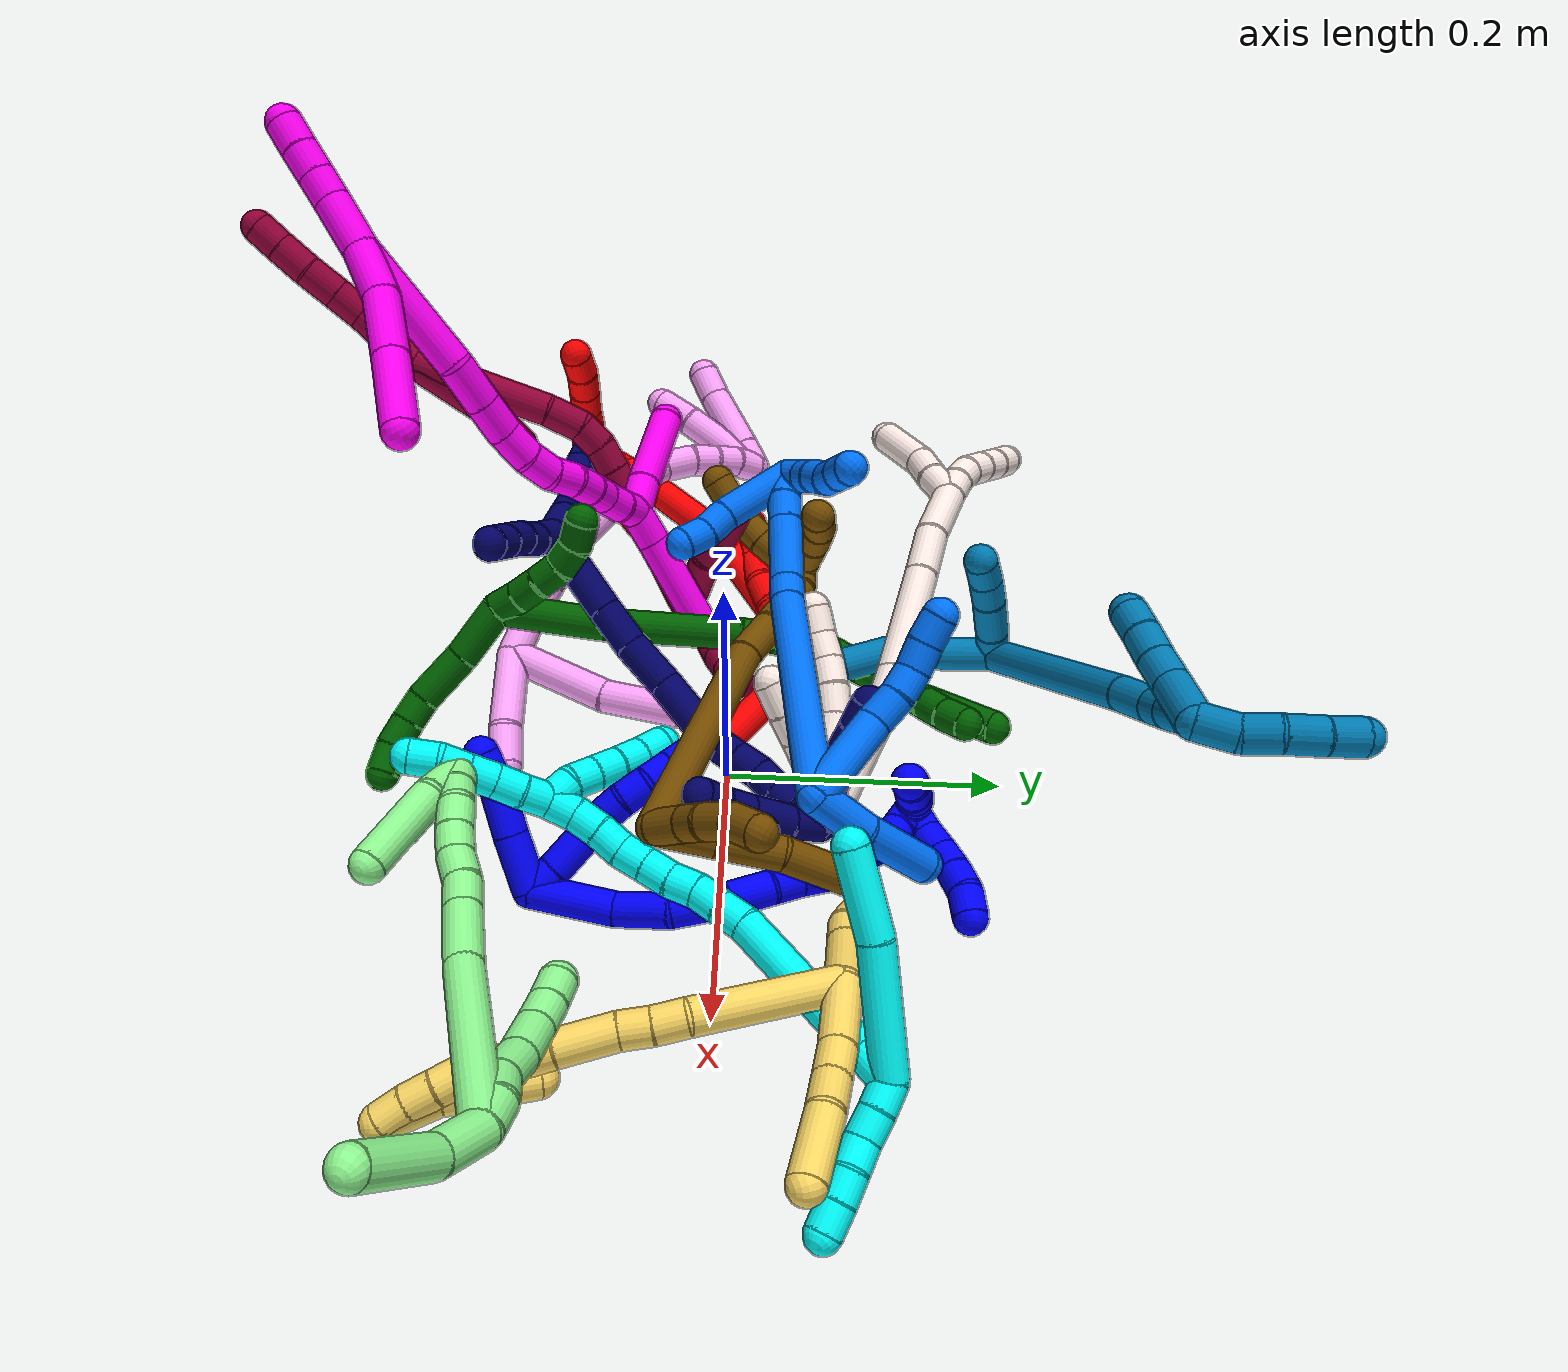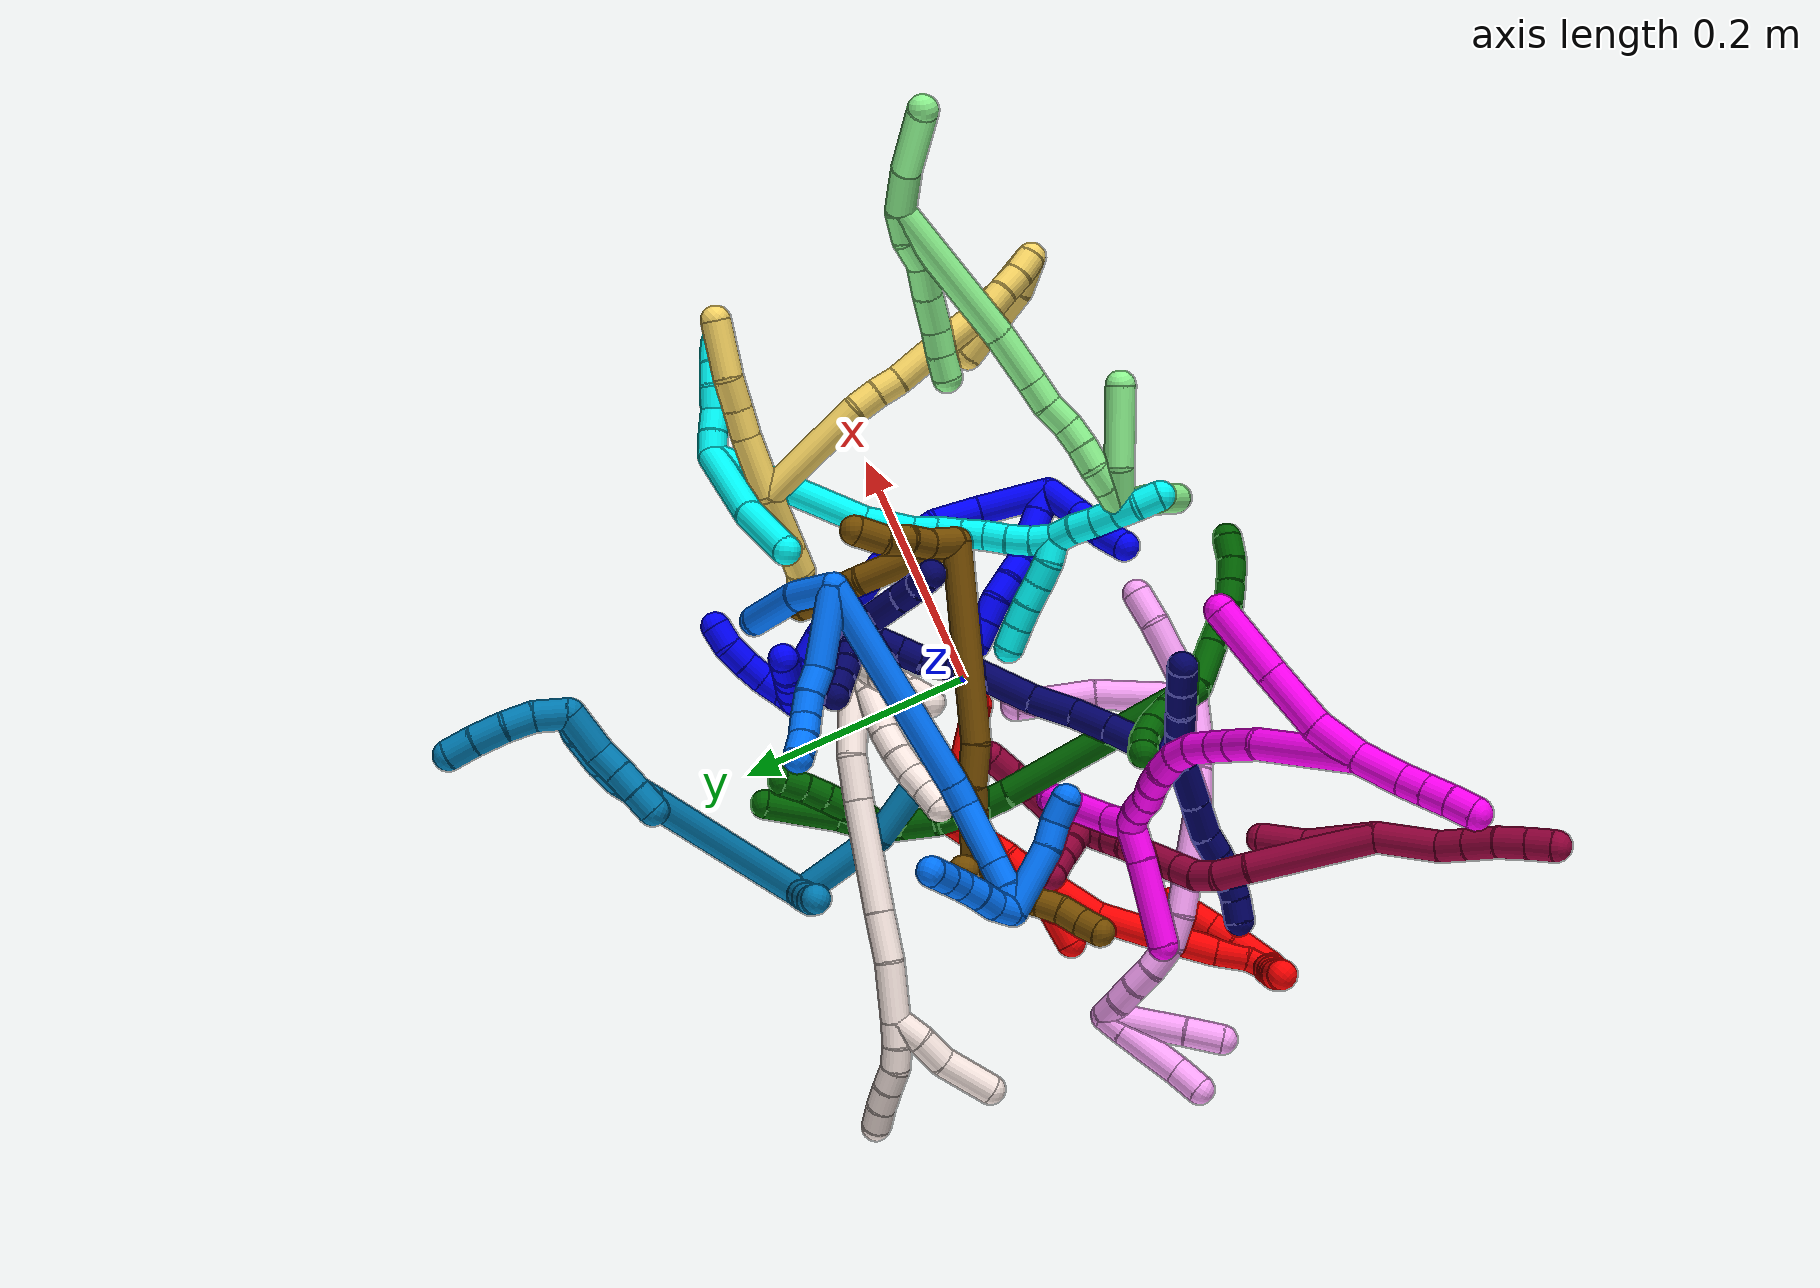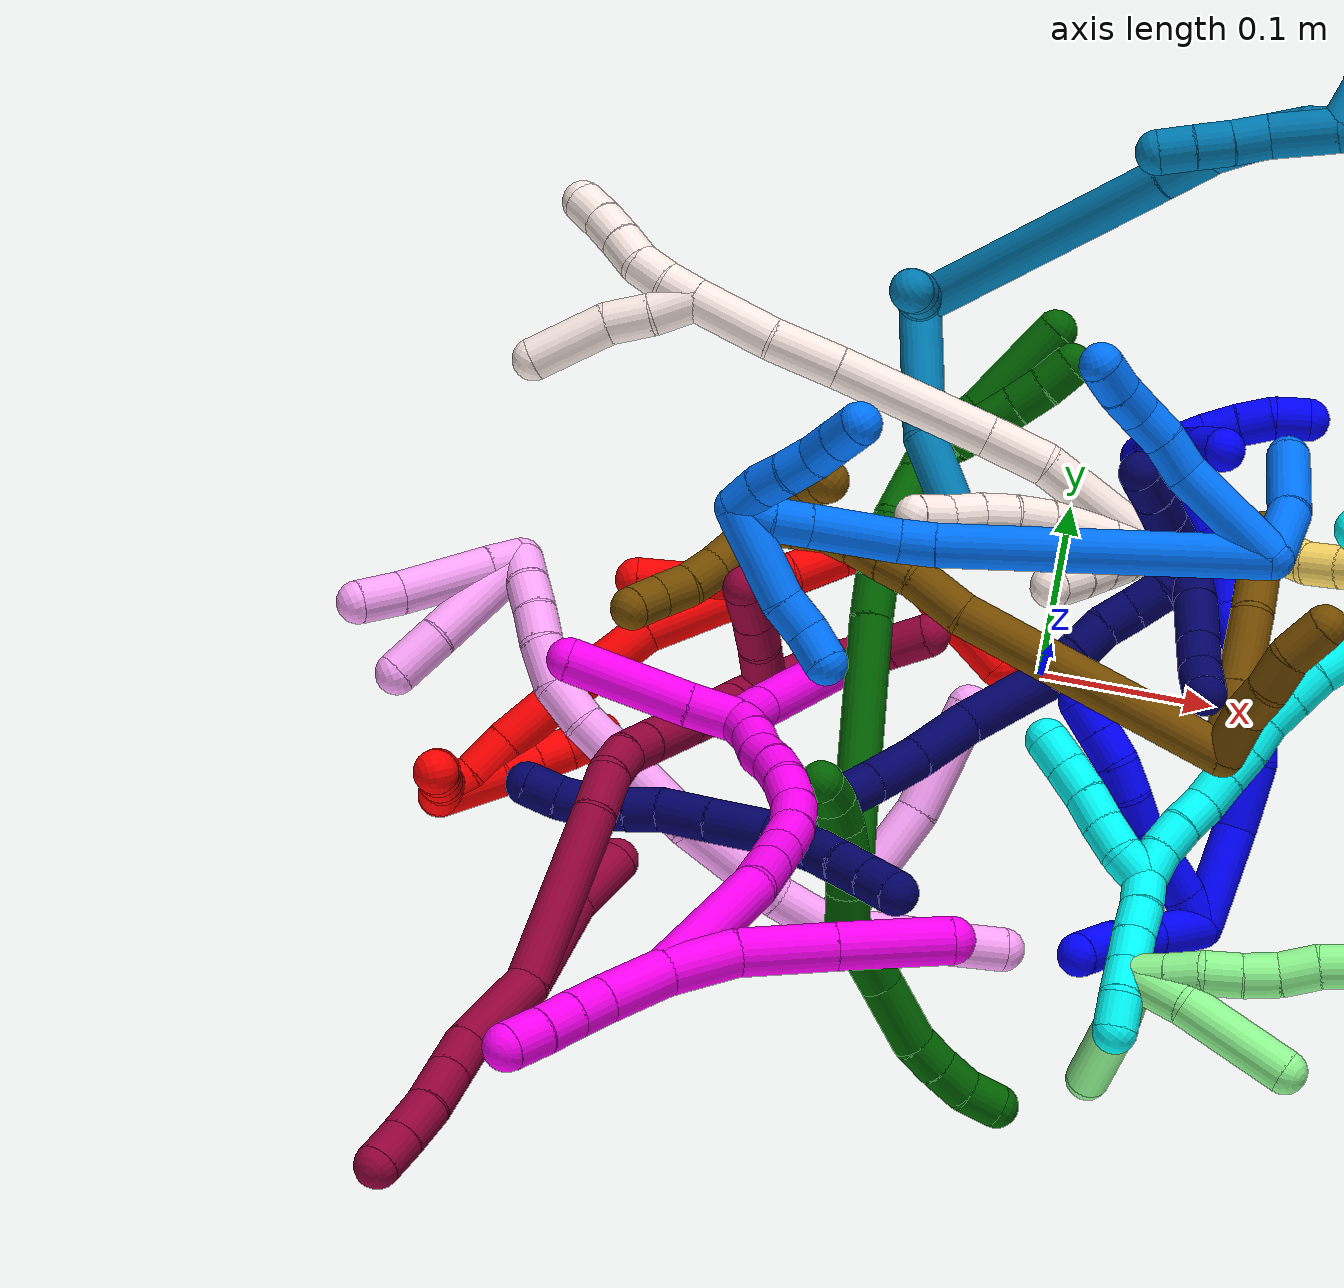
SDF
<sdf version="1.7">
 <world name="default">
  <plugin name="TubeGeneratorPlugin" filename="libtube_generator_plugin.so"/>
  <model name="photoneo_s_sensor">
   <static>1</static>
   <pose>0 0 2 1.57079 1.57079 3.14159</pose>
   <link name="link">
    <inertial><mass>0.1</mass></inertial>
    <sensor name="sensor" type="depth">
     <update_rate>30</update_rate>
     <camera>
      <horizontal_fov>1.22</horizontal_fov>
      <image><width>1920</width><height>1200</height><format>B8G8R8</format></image>
      <clip><near>0.1</near><far>4</far></clip>
      <depth_camera><output>points</output></depth_camera>
     </camera>
     <plugin name="camera_plugin" filename="libgazebo_ros_depth_camera.so">
      <baseline>0.2</baseline>
      <alwaysOn>1</alwaysOn>
      <updateRate>0.0</updateRate>
      <cameraName>camera_ir</cameraName>
      <imageTopicName>/camera/color/image_raw</imageTopicName>
      <cameraInfoTopicName>/camera/color/camera_info</cameraInfoTopicName>
      <depthImageTopicName>/camera/depth/image_raw</depthImageTopicName>
      <depthImageCameraInfoTopicName>/camera/depth/camera_info</depthImageCameraInfoTopicName>
      <pointCloudTopicName>/camera/depth/points</pointCloudTopicName>
      <frameName>fr_optical</frameName>
      <pointCloudCutoff>0.1</pointCloudCutoff>
      <pointCloudCutoffMax>2.0</pointCloudCutoffMax>
      <distortionK1>0</distortionK1>
      <distortionK2>0</distortionK2>
      <distortionK3>0</distortionK3>
      <distortionT1>0</distortionT1>
      <distortionT2>0</distortionT2>
      <CxPrime>0</CxPrime>
      <Cx>0</Cx>
      <Cy>0</Cy>
      <focalLength>0</focalLength>
      <hackBaseline>0</hackBaseline>
     </plugin>
    </sensor>
   </link>
  </model>
  <gravity>0 0 -9.8</gravity>
  <magnetic_field>6e-06 2.3e-05 -4.2e-05</magnetic_field>
  <atmosphere type="adiabatic"/>
  <physics name="default_physics" default="0" type="ode">
   <max_step_size>0.003</max_step_size>
   <real_time_factor>1</real_time_factor>
   <real_time_update_rate>1000</real_time_update_rate>
   <max_contacts>10000</max_contacts>
   <ode>
    <solver>
     <type>quick</type>
     <iters>100</iters>
     <sor>1.3</sor>
     <use_dynamic_moi_rescaling>0</use_dynamic_moi_rescaling>
    </solver>
    <constraints>
     <contact_max_correcting_vel>0</contact_max_correcting_vel>
     <contact_surface_layer>0.001</contact_surface_layer>
     <cfm>0</cfm>
     <erp>0.2</erp>
    </constraints>
   </ode>
  </physics>
  <scene><ambient>0.4 0.4 0.4 1</ambient><background>0.7 0.7 0.7 1</background><shadows>0</shadows></scene>
  <audio><device>default</device></audio>
  <spherical_coordinates>
   <surface_model>EARTH_WGS84</surface_model>
   <latitude_deg>0</latitude_deg>
   <longitude_deg>0</longitude_deg>
   <elevation>0</elevation>
   <heading_deg>0</heading_deg>
  </spherical_coordinates>
  <model name="bin">
   <static>1</static>
   <link name="bottom">
    <collision name="collision-bottom">
     <pose>0 0 -0.01 0 -0 0</pose>
     <geometry><box><size>0.8 0.6 0.02</size></box></geometry>
     <surface>
      <friction><ode><mu>100</mu><mu2>100</mu2></ode></friction>
      <contact><collide_bitmask>65535</collide_bitmask></contact>
     </surface>
    </collision>
   </link>
   <link name="west_wall">
    <collision name="collision-west_wall">
     <pose>-0.41 0 0.1 0 -0 0</pose>
     <geometry><box><size>0.02 0.6 0.2</size></box></geometry>
     <surface>
      <friction><ode><mu>100</mu><mu2>100</mu2></ode></friction>
      <contact><collide_bitmask>65535</collide_bitmask></contact>
     </surface>
    </collision>
   </link>
   <link name="east_wall">
    <collision name="collision-east_wall">
     <pose>0.41 0 0.1 0 -0 0</pose>
     <geometry><box><size>0.02 0.6 0.2</size></box></geometry>
     <surface>
      <friction><ode><mu>100</mu><mu2>100</mu2></ode></friction>
      <contact><collide_bitmask>65535</collide_bitmask></contact>
     </surface>
    </collision>
   </link>
   <link name="south_wall">
    <collision name="collision-south_wall">
     <pose>0 -0.31 0.1 0 -0 0</pose>
     <geometry><box><size>0.8 0.02 0.2</size></box></geometry>
     <surface>
      <friction><ode><mu>100</mu><mu2>100</mu2></ode></friction>
      <contact><collide_bitmask>65535</collide_bitmask></contact>
     </surface>
    </collision>
   </link>
   <link name="north_wall">
    <collision name="collision-north_wall">
     <pose>0 0.31 0.1 0 -0 0</pose>
     <geometry><box><size>0.8 0.02 0.2</size></box></geometry>
     <surface>
      <friction><ode><mu>100</mu><mu2>100</mu2></ode></friction>
      <contact><collide_bitmask>65535</collide_bitmask></contact>
     </surface>
    </collision>
   </link>
  </model>
  <model name="1">
   <static>0</static>
   <link name="1">
    <collision name="collision-cylinder-e_1_2_8">
     <pose>-0.000331 0.00731 -0.007769 -2.38662 -0.030997 0.078143</pose>
     <geometry><cylinder><radius>0.0125</radius><length>0.021345</length></cylinder></geometry>
     <surface>
      <friction><ode><mu>1.16</mu><mu2>1.16</mu2><slip1>0</slip1><slip2>0</slip2></ode></friction>
      <contact><ode><kp>1e+06</kp><kd>1</kd><max_vel>0</max_vel><min_depth>0.001</min_depth></ode></contact>
     </surface>
    </collision>
    <visual name="visual-cylinder-e_1_2_8">
     <pose>-0.000331 0.00731 -0.007769 -2.38662 -0.030997 0.078143</pose>
     <geometry><cylinder><radius>0.0125</radius><length>0.021345</length></cylinder></geometry>
     <material><ambient>0 0 1 1</ambient></material>
    </visual>
    <collision name="collision-cylinder-e_2_8_9">
     <pose>-0.00284 0.028673 -0.034826 -2.51193 -0.091033 0.277923</pose>
     <geometry><cylinder><radius>0.0125</radius><length>0.047927</length></cylinder></geometry>
     <surface>
      <friction><ode><mu>1.16</mu><mu2>1.16</mu2><slip1>0</slip1><slip2>0</slip2></ode></friction>
      <contact><ode><kp>1e+06</kp><kd>1</kd><max_vel>0</max_vel><min_depth>0.001</min_depth></ode></contact>
     </surface>
    </collision>
    <visual name="visual-cylinder-e_2_8_9">
     <pose>-0.00284 0.028673 -0.034826 -2.51193 -0.091033 0.277923</pose>
     <geometry><cylinder><radius>0.0125</radius><length>0.047927</length></cylinder></geometry>
     <material><ambient>0 0 1 1</ambient></material>
    </visual>
    <collision name="collision-cylinder-e_3_9_10">
     <pose>-0.007841 0.049629 -0.060778 -2.33867 -0.286126 0.654253</pose>
     <geometry><cylinder><radius>0.0125</radius><length>0.020004</length></cylinder></geometry>
     <surface>
      <friction><ode><mu>1.16</mu><mu2>1.16</mu2><slip1>0</slip1><slip2>0</slip2></ode></friction>
      <contact><ode><kp>1e+06</kp><kd>1</kd><max_vel>0</max_vel><min_depth>0.001</min_depth></ode></contact>
     </surface>
    </collision>
    <visual name="visual-cylinder-e_3_9_10">
     <pose>-0.007841 0.049629 -0.060778 -2.33867 -0.286126 0.654253</pose>
     <geometry><cylinder><radius>0.0125</radius><length>0.020004</length></cylinder></geometry>
     <material><ambient>0 0 1 1</ambient></material>
    </visual>
    <collision name="collision-cylinder-e_4_10_11">
     <pose>-0.011324 0.064355 -0.073934 -2.26333 -0.064839 0.137865</pose>
     <geometry><cylinder><radius>0.0125</radius><length>0.020374</length></cylinder></geometry>
     <surface>
      <friction><ode><mu>1.16</mu><mu2>1.16</mu2><slip1>0</slip1><slip2>0</slip2></ode></friction>
      <contact><ode><kp>1e+06</kp><kd>1</kd><max_vel>0</max_vel><min_depth>0.001</min_depth></ode></contact>
     </surface>
    </collision>
    <visual name="visual-cylinder-e_4_10_11">
     <pose>-0.011324 0.064355 -0.073934 -2.26333 -0.064839 0.137865</pose>
     <geometry><cylinder><radius>0.0125</radius><length>0.020374</length></cylinder></geometry>
     <material><ambient>0 0 1 1</ambient></material>
    </visual>
    <collision name="collision-cylinder-e_5_11_12">
     <pose>-0.009844 0.079415 -0.087186 -2.32231 0.212861 -0.482506</pose>
     <geometry><cylinder><radius>0.0125</radius><length>0.020266</length></cylinder></geometry>
     <surface>
      <friction><ode><mu>1.16</mu><mu2>1.16</mu2><slip1>0</slip1><slip2>0</slip2></ode></friction>
      <contact><ode><kp>1e+06</kp><kd>1</kd><max_vel>0</max_vel><min_depth>0.001</min_depth></ode></contact>
     </surface>
    </collision>
    <visual name="visual-cylinder-e_5_11_12">
     <pose>-0.009844 0.079415 -0.087186 -2.32231 0.212861 -0.482506</pose>
     <geometry><cylinder><radius>0.0125</radius><length>0.020266</length></cylinder></geometry>
     <material><ambient>0 0 1 1</ambient></material>
    </visual>
    <collision name="collision-cylinder-e_6_12_6">
     <pose>-0.005599 0.093845 -0.100633 -2.31955 0.21106 -0.476816</pose>
     <geometry><cylinder><radius>0.0125</radius><length>0.020085</length></cylinder></geometry>
     <surface>
      <friction><ode><mu>1.16</mu><mu2>1.16</mu2><slip1>0</slip1><slip2>0</slip2></ode></friction>
      <contact><ode><kp>1e+06</kp><kd>1</kd><max_vel>0</max_vel><min_depth>0.001</min_depth></ode></contact>
     </surface>
    </collision>
    <visual name="visual-cylinder-e_6_12_6">
     <pose>-0.005599 0.093845 -0.100633 -2.31955 0.21106 -0.476816</pose>
     <geometry><cylinder><radius>0.0125</radius><length>0.020085</length></cylinder></geometry>
     <material><ambient>0 0 1 1</ambient></material>
    </visual>
    <collision name="collision-cylinder-e_1_2_13">
     <pose>-0.005926 -0.008426 -0.017744 2.69827 -0.293018 -1.15946</pose>
     <geometry><cylinder><radius>0.0125</radius><length>0.041034</length></cylinder></geometry>
     <surface>
      <friction><ode><mu>1.16</mu><mu2>1.16</mu2><slip1>0</slip1><slip2>0</slip2></ode></friction>
      <contact><ode><kp>1e+06</kp><kd>1</kd><max_vel>0</max_vel><min_depth>0.001</min_depth></ode></contact>
     </surface>
    </collision>
    <visual name="visual-cylinder-e_1_2_13">
     <pose>-0.005926 -0.008426 -0.017744 2.69827 -0.293018 -1.15946</pose>
     <geometry><cylinder><radius>0.0125</radius><length>0.041034</length></cylinder></geometry>
     <material><ambient>0 0 1 1</ambient></material>
    </visual>
    <collision name="collision-cylinder-e_2_13_14">
     <pose>-0.016451 -0.022796 -0.049818 2.74835 -0.288169 -1.25904</pose>
     <geometry><cylinder><radius>0.0125</radius><length>0.032364</length></cylinder></geometry>
     <surface>
      <friction><ode><mu>1.16</mu><mu2>1.16</mu2><slip1>0</slip1><slip2>0</slip2></ode></friction>
      <contact><ode><kp>1e+06</kp><kd>1</kd><max_vel>0</max_vel><min_depth>0.001</min_depth></ode></contact>
     </surface>
    </collision>
    <visual name="visual-cylinder-e_2_13_14">
     <pose>-0.016451 -0.022796 -0.049818 2.74835 -0.288169 -1.25904</pose>
     <geometry><cylinder><radius>0.0125</radius><length>0.032364</length></cylinder></geometry>
     <material><ambient>0 0 1 1</ambient></material>
    </visual>
    <collision name="collision-cylinder-e_3_14_5">
     <pose>-0.024714 -0.035373 -0.075081 2.59636 -0.27903 -0.930942</pose>
     <geometry><cylinder><radius>0.0125</radius><length>0.026602</length></cylinder></geometry>
     <surface>
      <friction><ode><mu>1.16</mu><mu2>1.16</mu2><slip1>0</slip1><slip2>0</slip2></ode></friction>
      <contact><ode><kp>1e+06</kp><kd>1</kd><max_vel>0</max_vel><min_depth>0.001</min_depth></ode></contact>
     </surface>
    </collision>
    <visual name="visual-cylinder-e_3_14_5">
     <pose>-0.024714 -0.035373 -0.075081 2.59636 -0.27903 -0.930942</pose>
     <geometry><cylinder><radius>0.0125</radius><length>0.026602</length></cylinder></geometry>
     <material><ambient>0 0 1 1</ambient></material>
    </visual>
    <collision name="collision-cylinder-e_1_2_15">
     <pose>-0.001015 0.029984 0.003526 -1.45375 -0.033592 0.029875</pose>
     <geometry><cylinder><radius>0.0125</radius><length>0.060416</length></cylinder></geometry>
     <surface>
      <friction><ode><mu>1.16</mu><mu2>1.16</mu2><slip1>0</slip1><slip2>0</slip2></ode></friction>
      <contact><ode><kp>1e+06</kp><kd>1</kd><max_vel>0</max_vel><min_depth>0.001</min_depth></ode></contact>
     </surface>
    </collision>
    <visual name="visual-cylinder-e_1_2_15">
     <pose>-0.001015 0.029984 0.003526 -1.45375 -0.033592 0.029875</pose>
     <geometry><cylinder><radius>0.0125</radius><length>0.060416</length></cylinder></geometry>
     <material><ambient>0 0 1 1</ambient></material>
    </visual>
    <collision name="collision-cylinder-e_2_15_16">
     <pose>-0.007135 0.079113 0.006318 -1.60905 -0.260467 0.270507</pose>
     <geometry><cylinder><radius>0.0125</radius><length>0.039653</length></cylinder></geometry>
     <surface>
      <friction><ode><mu>1.16</mu><mu2>1.16</mu2><slip1>0</slip1><slip2>0</slip2></ode></friction>
      <contact><ode><kp>1e+06</kp><kd>1</kd><max_vel>0</max_vel><min_depth>0.001</min_depth></ode></contact>
     </surface>
    </collision>
    <visual name="visual-cylinder-e_2_15_16">
     <pose>-0.007135 0.079113 0.006318 -1.60905 -0.260467 0.270507</pose>
     <geometry><cylinder><radius>0.0125</radius><length>0.039653</length></cylinder></geometry>
     <material><ambient>0 0 1 1</ambient></material>
    </visual>
    <collision name="collision-cylinder-e_3_16_17">
     <pose>-0.013035 0.117423 -4.7e-05 -1.85662 -0.039704 0.053045</pose>
     <geometry><cylinder><radius>0.0125</radius><length>0.039986</length></cylinder></geometry>
     <surface>
      <friction><ode><mu>1.16</mu><mu2>1.16</mu2><slip1>0</slip1><slip2>0</slip2></ode></friction>
      <contact><ode><kp>1e+06</kp><kd>1</kd><max_vel>0</max_vel><min_depth>0.001</min_depth></ode></contact>
     </surface>
    </collision>
    <visual name="visual-cylinder-e_3_16_17">
     <pose>-0.013035 0.117423 -4.7e-05 -1.85662 -0.039704 0.053045</pose>
     <geometry><cylinder><radius>0.0125</radius><length>0.039986</length></cylinder></geometry>
     <material><ambient>0 0 1 1</ambient></material>
    </visual>
    <collision name="collision-cylinder-e_4_17_18">
     <pose>-0.011222 0.150696 -0.011629 -1.96993 0.168628 -0.253375</pose>
     <geometry><cylinder><radius>0.0125</radius><length>0.031061</length></cylinder></geometry>
     <surface>
      <friction><ode><mu>1.16</mu><mu2>1.16</mu2><slip1>0</slip1><slip2>0</slip2></ode></friction>
      <contact><ode><kp>1e+06</kp><kd>1</kd><max_vel>0</max_vel><min_depth>0.001</min_depth></ode></contact>
     </surface>
    </collision>
    <visual name="visual-cylinder-e_4_17_18">
     <pose>-0.011222 0.150696 -0.011629 -1.96993 0.168628 -0.253375</pose>
     <geometry><cylinder><radius>0.0125</radius><length>0.031061</length></cylinder></geometry>
     <material><ambient>0 0 1 1</ambient></material>
    </visual>
    <collision name="collision-cylinder-e_5_18_19">
     <pose>-0.004643 0.174106 -0.021777 -1.99469 0.371185 -0.565821</pose>
     <geometry><cylinder><radius>0.0125</radius><length>0.021906</length></cylinder></geometry>
     <surface>
      <friction><ode><mu>1.16</mu><mu2>1.16</mu2><slip1>0</slip1><slip2>0</slip2></ode></friction>
      <contact><ode><kp>1e+06</kp><kd>1</kd><max_vel>0</max_vel><min_depth>0.001</min_depth></ode></contact>
     </surface>
    </collision>
    <visual name="visual-cylinder-e_5_18_19">
     <pose>-0.004643 0.174106 -0.021777 -1.99469 0.371185 -0.565821</pose>
     <geometry><cylinder><radius>0.0125</radius><length>0.021906</length></cylinder></geometry>
     <material><ambient>0 0 1 1</ambient></material>
    </visual>
    <collision name="collision-cylinder-e_6_19_20">
     <pose>0.000422 0.193823 -0.029308 -1.88055 0.099503 -0.136223</pose>
     <geometry><cylinder><radius>0.0125</radius><length>0.021976</length></cylinder></geometry>
     <surface>
      <friction><ode><mu>1.16</mu><mu2>1.16</mu2><slip1>0</slip1><slip2>0</slip2></ode></friction>
      <contact><ode><kp>1e+06</kp><kd>1</kd><max_vel>0</max_vel><min_depth>0.001</min_depth></ode></contact>
     </surface>
    </collision>
    <visual name="visual-cylinder-e_6_19_20">
     <pose>0.000422 0.193823 -0.029308 -1.88055 0.099503 -0.136223</pose>
     <geometry><cylinder><radius>0.0125</radius><length>0.021976</length></cylinder></geometry>
     <material><ambient>0 0 1 1</ambient></material>
    </visual>
    <collision name="collision-cylinder-e_7_20_21">
     <pose>0.001668 0.213299 -0.039436 -2.21418 0.013654 -0.027303</pose>
     <geometry><cylinder><radius>0.0125</radius><length>0.022656</length></cylinder></geometry>
     <surface>
      <friction><ode><mu>1.16</mu><mu2>1.16</mu2><slip1>0</slip1><slip2>0</slip2></ode></friction>
      <contact><ode><kp>1e+06</kp><kd>1</kd><max_vel>0</max_vel><min_depth>0.001</min_depth></ode></contact>
     </surface>
    </collision>
    <visual name="visual-cylinder-e_7_20_21">
     <pose>0.001668 0.213299 -0.039436 -2.21418 0.013654 -0.027303</pose>
     <geometry><cylinder><radius>0.0125</radius><length>0.022656</length></cylinder></geometry>
     <material><ambient>0 0 1 1</ambient></material>
    </visual>
    <collision name="collision-cylinder-e_8_21_22">
     <pose>0.005611 0.23091 -0.051863 -2.15331 0.354415 -0.641874</pose>
     <geometry><cylinder><radius>0.0125</radius><length>0.021832</length></cylinder></geometry>
     <surface>
      <friction><ode><mu>1.16</mu><mu2>1.16</mu2><slip1>0</slip1><slip2>0</slip2></ode></friction>
      <contact><ode><kp>1e+06</kp><kd>1</kd><max_vel>0</max_vel><min_depth>0.001</min_depth></ode></contact>
     </surface>
    </collision>
    <visual name="visual-cylinder-e_8_21_22">
     <pose>0.005611 0.23091 -0.051863 -2.15331 0.354415 -0.641874</pose>
     <geometry><cylinder><radius>0.0125</radius><length>0.021832</length></cylinder></geometry>
     <material><ambient>0 0 1 1</ambient></material>
    </visual>
    <collision name="collision-cylinder-e_9_22_23">
     <pose>0.014005 0.244727 -0.064663 -2.50787 0.477756 -1.27758</pose>
     <geometry><cylinder><radius>0.0125</radius><length>0.020035</length></cylinder></geometry>
     <surface>
      <friction><ode><mu>1.16</mu><mu2>1.16</mu2><slip1>0</slip1><slip2>0</slip2></ode></friction>
      <contact><ode><kp>1e+06</kp><kd>1</kd><max_vel>0</max_vel><min_depth>0.001</min_depth></ode></contact>
     </surface>
    </collision>
    <visual name="visual-cylinder-e_9_22_23">
     <pose>0.014005 0.244727 -0.064663 -2.50787 0.477756 -1.27758</pose>
     <geometry><cylinder><radius>0.0125</radius><length>0.020035</length></cylinder></geometry>
     <material><ambient>0 0 1 1</ambient></material>
    </visual>
    <collision name="collision-cylinder-e_10_23_1">
     <pose>0.023784 0.254466 -0.079454 -2.61111 0.529618 -1.56908</pose>
     <geometry><cylinder><radius>0.0125</radius><length>0.02048</length></cylinder></geometry>
     <surface>
      <friction><ode><mu>1.16</mu><mu2>1.16</mu2><slip1>0</slip1><slip2>0</slip2></ode></friction>
      <contact><ode><kp>1e+06</kp><kd>1</kd><max_vel>0</max_vel><min_depth>0.001</min_depth></ode></contact>
     </surface>
    </collision>
    <visual name="visual-cylinder-e_10_23_1">
     <pose>0.023784 0.254466 -0.079454 -2.61111 0.529618 -1.56908</pose>
     <geometry><cylinder><radius>0.0125</radius><length>0.02048</length></cylinder></geometry>
     <material><ambient>0 0 1 1</ambient></material>
    </visual>
    <collision name="collision-cylinder-e_1_1_24">
     <pose>0.026311 0.264239 -0.079022 -0.58212 -0.267824 0.080671</pose>
     <geometry><cylinder><radius>0.0125</radius><length>0.02</length></cylinder></geometry>
     <surface>
      <friction><ode><mu>1.16</mu><mu2>1.16</mu2><slip1>0</slip1><slip2>0</slip2></ode></friction>
      <contact><ode><kp>1e+06</kp><kd>1</kd><max_vel>0</max_vel><min_depth>0.001</min_depth></ode></contact>
     </surface>
    </collision>
    <visual name="visual-cylinder-e_1_1_24">
     <pose>0.026311 0.264239 -0.079022 -0.58212 -0.267824 0.080671</pose>
     <geometry><cylinder><radius>0.0125</radius><length>0.02</length></cylinder></geometry>
     <material><ambient>0 0 1 1</ambient></material>
    </visual>
    <collision name="collision-cylinder-e_2_24_25">
     <pose>0.019352 0.275064 -0.063833 -0.658779 -0.445975 0.154722</pose>
     <geometry><cylinder><radius>0.0125</radius><length>0.02</length></cylinder></geometry>
     <surface>
      <friction><ode><mu>1.16</mu><mu2>1.16</mu2><slip1>0</slip1><slip2>0</slip2></ode></friction>
      <contact><ode><kp>1e+06</kp><kd>1</kd><max_vel>0</max_vel><min_depth>0.001</min_depth></ode></contact>
     </surface>
    </collision>
    <visual name="visual-cylinder-e_2_24_25">
     <pose>0.019352 0.275064 -0.063833 -0.658779 -0.445975 0.154722</pose>
     <geometry><cylinder><radius>0.0125</radius><length>0.02</length></cylinder></geometry>
     <material><ambient>0 0 1 1</ambient></material>
    </visual>
    <collision name="collision-cylinder-e_3_25_26">
     <pose>0.009299 0.284976 -0.049786 -0.565648 -0.611351 0.182904</pose>
     <geometry><cylinder><radius>0.0125</radius><length>0.02</length></cylinder></geometry>
     <surface>
      <friction><ode><mu>1.16</mu><mu2>1.16</mu2><slip1>0</slip1><slip2>0</slip2></ode></friction>
      <contact><ode><kp>1e+06</kp><kd>1</kd><max_vel>0</max_vel><min_depth>0.001</min_depth></ode></contact>
     </surface>
    </collision>
    <visual name="visual-cylinder-e_3_25_26">
     <pose>0.009299 0.284976 -0.049786 -0.565648 -0.611351 0.182904</pose>
     <geometry><cylinder><radius>0.0125</radius><length>0.02</length></cylinder></geometry>
     <material><ambient>0 0 1 1</ambient></material>
    </visual>
    <collision name="collision-cylinder-e_4_26_27">
     <pose>-0.001994 0.293117 -0.035451 -0.468175 -0.588689 0.144327</pose>
     <geometry><cylinder><radius>0.0125</radius><length>0.02</length></cylinder></geometry>
     <surface>
      <friction><ode><mu>1.16</mu><mu2>1.16</mu2><slip1>0</slip1><slip2>0</slip2></ode></friction>
      <contact><ode><kp>1e+06</kp><kd>1</kd><max_vel>0</max_vel><min_depth>0.001</min_depth></ode></contact>
     </surface>
    </collision>
    <visual name="visual-cylinder-e_4_26_27">
     <pose>-0.001994 0.293117 -0.035451 -0.468175 -0.588689 0.144327</pose>
     <geometry><cylinder><radius>0.0125</radius><length>0.02</length></cylinder></geometry>
     <material><ambient>0 0 1 1</ambient></material>
    </visual>
    <collision name="collision-cylinder-e_5_27_4">
     <pose>-0.011296 0.298746 -0.01895 -0.203685 -0.384295 0.039759</pose>
     <geometry><cylinder><radius>0.0125</radius><length>0.02</length></cylinder></geometry>
     <surface>
      <friction><ode><mu>1.16</mu><mu2>1.16</mu2><slip1>0</slip1><slip2>0</slip2></ode></friction>
      <contact><ode><kp>1e+06</kp><kd>1</kd><max_vel>0</max_vel><min_depth>0.001</min_depth></ode></contact>
     </surface>
    </collision>
    <visual name="visual-cylinder-e_5_27_4">
     <pose>-0.011296 0.298746 -0.01895 -0.203685 -0.384295 0.039759</pose>
     <geometry><cylinder><radius>0.0125</radius><length>0.02</length></cylinder></geometry>
     <material><ambient>0 0 1 1</ambient></material>
    </visual>
    <collision name="collision-cylinder-e_1_1_28">
     <pose>0.019086 0.259426 -0.088597 -2.83034 -1.41047 2.77707</pose>
     <geometry><cylinder><radius>0.0125</radius><length>0.02</length></cylinder></geometry>
     <surface>
      <friction><ode><mu>1.16</mu><mu2>1.16</mu2><slip1>0</slip1><slip2>0</slip2></ode></friction>
      <contact><ode><kp>1e+06</kp><kd>1</kd><max_vel>0</max_vel><min_depth>0.001</min_depth></ode></contact>
     </surface>
    </collision>
    <visual name="visual-cylinder-e_1_1_28">
     <pose>0.019086 0.259426 -0.088597 -2.83034 -1.41047 2.77707</pose>
     <geometry><cylinder><radius>0.0125</radius><length>0.02</length></cylinder></geometry>
     <material><ambient>0 0 1 1</ambient></material>
    </visual>
    <collision name="collision-cylinder-e_2_28_29">
     <pose>-0.00073 0.258993 -0.089604 1.06339 -1.46508 -0.973284</pose>
     <geometry><cylinder><radius>0.0125</radius><length>0.02</length></cylinder></geometry>
     <surface>
      <friction><ode><mu>1.16</mu><mu2>1.16</mu2><slip1>0</slip1><slip2>0</slip2></ode></friction>
      <contact><ode><kp>1e+06</kp><kd>1</kd><max_vel>0</max_vel><min_depth>0.001</min_depth></ode></contact>
     </surface>
    </collision>
    <visual name="visual-cylinder-e_2_28_29">
     <pose>-0.00073 0.258993 -0.089604 1.06339 -1.46508 -0.973284</pose>
     <geometry><cylinder><radius>0.0125</radius><length>0.02</length></cylinder></geometry>
     <material><ambient>0 0 1 1</ambient></material>
    </visual>
    <collision name="collision-cylinder-e_3_29_30">
     <pose>-0.020475 0.256284 -0.088223 1.11845 -1.37081 -0.945987</pose>
     <geometry><cylinder><radius>0.0125</radius><length>0.02</length></cylinder></geometry>
     <surface>
      <friction><ode><mu>1.16</mu><mu2>1.16</mu2><slip1>0</slip1><slip2>0</slip2></ode></friction>
      <contact><ode><kp>1e+06</kp><kd>1</kd><max_vel>0</max_vel><min_depth>0.001</min_depth></ode></contact>
     </surface>
    </collision>
    <visual name="visual-cylinder-e_3_29_30">
     <pose>-0.020475 0.256284 -0.088223 1.11845 -1.37081 -0.945987</pose>
     <geometry><cylinder><radius>0.0125</radius><length>0.02</length></cylinder></geometry>
     <material><ambient>0 0 1 1</ambient></material>
    </visual>
    <collision name="collision-cylinder-e_4_30_31">
     <pose>-0.04001 0.252893 -0.088986 2.36462 -1.33995 -2.18785</pose>
     <geometry><cylinder><radius>0.0125</radius><length>0.02</length></cylinder></geometry>
     <surface>
      <friction><ode><mu>1.16</mu><mu2>1.16</mu2><slip1>0</slip1><slip2>0</slip2></ode></friction>
      <contact><ode><kp>1e+06</kp><kd>1</kd><max_vel>0</max_vel><min_depth>0.001</min_depth></ode></contact>
     </surface>
    </collision>
    <visual name="visual-cylinder-e_4_30_31">
     <pose>-0.04001 0.252893 -0.088986 2.36462 -1.33995 -2.18785</pose>
     <geometry><cylinder><radius>0.0125</radius><length>0.02</length></cylinder></geometry>
     <material><ambient>0 0 1 1</ambient></material>
    </visual>
    <collision name="collision-cylinder-e_5_31_3">
     <pose>-0.059526 0.249816 -0.089148 0.786521 -1.36119 -0.648114</pose>
     <geometry><cylinder><radius>0.0125</radius><length>0.02</length></cylinder></geometry>
     <surface>
      <friction><ode><mu>1.16</mu><mu2>1.16</mu2><slip1>0</slip1><slip2>0</slip2></ode></friction>
      <contact><ode><kp>1e+06</kp><kd>1</kd><max_vel>0</max_vel><min_depth>0.001</min_depth></ode></contact>
     </surface>
    </collision>
    <visual name="visual-cylinder-e_5_31_3">
     <pose>-0.059526 0.249816 -0.089148 0.786521 -1.36119 -0.648114</pose>
     <geometry><cylinder><radius>0.0125</radius><length>0.02</length></cylinder></geometry>
     <material><ambient>0 0 1 1</ambient></material>
    </visual>
    <collision name="collision-sphere-3">
     <pose>-0.069307 0.248343 -0.087678 0 -0 0</pose>
     <geometry><sphere><radius>0.0125</radius></sphere></geometry>
     <surface>
      <friction><ode><mu>1.16</mu><mu2>1.16</mu2><slip1>0</slip1><slip2>0</slip2></ode></friction>
      <contact><ode><kp>1e+06</kp><kd>1</kd><max_vel>0</max_vel><min_depth>0.001</min_depth></ode></contact>
     </surface>
    </collision>
    <visual name="visual-sphere-3">
     <pose>-0.069307 0.248343 -0.087678 0 -0 0</pose>
     <geometry><sphere><radius>0.0125</radius></sphere></geometry>
     <material><ambient>0 0 1 1</ambient></material>
    </visual>
    <collision name="collision-sphere-31">
     <pose>-0.049745 0.251289 -0.090617 0 -0 0</pose>
     <geometry><sphere><radius>0.0125</radius></sphere></geometry>
     <surface>
      <friction><ode><mu>1.16</mu><mu2>1.16</mu2><slip1>0</slip1><slip2>0</slip2></ode></friction>
      <contact><ode><kp>1e+06</kp><kd>1</kd><max_vel>0</max_vel><min_depth>0.001</min_depth></ode></contact>
     </surface>
    </collision>
    <visual name="visual-sphere-31">
     <pose>-0.049745 0.251289 -0.090617 0 -0 0</pose>
     <geometry><sphere><radius>0.0125</radius></sphere></geometry>
     <material><ambient>0 0 1 1</ambient></material>
    </visual>
    <collision name="collision-sphere-30">
     <pose>-0.030275 0.254497 -0.087354 0 -0 0</pose>
     <geometry><sphere><radius>0.0125</radius></sphere></geometry>
     <surface>
      <friction><ode><mu>1.16</mu><mu2>1.16</mu2><slip1>0</slip1><slip2>0</slip2></ode></friction>
      <contact><ode><kp>1e+06</kp><kd>1</kd><max_vel>0</max_vel><min_depth>0.001</min_depth></ode></contact>
     </surface>
    </collision>
    <visual name="visual-sphere-30">
     <pose>-0.030275 0.254497 -0.087354 0 -0 0</pose>
     <geometry><sphere><radius>0.0125</radius></sphere></geometry>
     <material><ambient>0 0 1 1</ambient></material>
    </visual>
    <collision name="collision-sphere-29">
     <pose>-0.010674 0.258071 -0.089091 0 -0 0</pose>
     <geometry><sphere><radius>0.0125</radius></sphere></geometry>
     <surface>
      <friction><ode><mu>1.16</mu><mu2>1.16</mu2><slip1>0</slip1><slip2>0</slip2></ode></friction>
      <contact><ode><kp>1e+06</kp><kd>1</kd><max_vel>0</max_vel><min_depth>0.001</min_depth></ode></contact>
     </surface>
    </collision>
    <visual name="visual-sphere-29">
     <pose>-0.010674 0.258071 -0.089091 0 -0 0</pose>
     <geometry><sphere><radius>0.0125</radius></sphere></geometry>
     <material><ambient>0 0 1 1</ambient></material>
    </visual>
    <collision name="collision-sphere-28">
     <pose>0.009214 0.259915 -0.090116 0 -0 0</pose>
     <geometry><sphere><radius>0.0125</radius></sphere></geometry>
     <surface>
      <friction><ode><mu>1.16</mu><mu2>1.16</mu2><slip1>0</slip1><slip2>0</slip2></ode></friction>
      <contact><ode><kp>1e+06</kp><kd>1</kd><max_vel>0</max_vel><min_depth>0.001</min_depth></ode></contact>
     </surface>
    </collision>
    <visual name="visual-sphere-28">
     <pose>0.009214 0.259915 -0.090116 0 -0 0</pose>
     <geometry><sphere><radius>0.0125</radius></sphere></geometry>
     <material><ambient>0 0 1 1</ambient></material>
    </visual>
    <collision name="collision-sphere-4">
     <pose>-0.015045 0.300621 -0.009871 0 -0 0</pose>
     <geometry><sphere><radius>0.0125</radius></sphere></geometry>
     <surface>
      <friction><ode><mu>1.16</mu><mu2>1.16</mu2><slip1>0</slip1><slip2>0</slip2></ode></friction>
      <contact><ode><kp>1e+06</kp><kd>1</kd><max_vel>0</max_vel><min_depth>0.001</min_depth></ode></contact>
     </surface>
    </collision>
    <visual name="visual-sphere-4">
     <pose>-0.015045 0.300621 -0.009871 0 -0 0</pose>
     <geometry><sphere><radius>0.0125</radius></sphere></geometry>
     <material><ambient>0 0 1 1</ambient></material>
    </visual>
    <collision name="collision-sphere-27">
     <pose>-0.007547 0.29687 -0.028029 0 -0 0</pose>
     <geometry><sphere><radius>0.0125</radius></sphere></geometry>
     <surface>
      <friction><ode><mu>1.16</mu><mu2>1.16</mu2><slip1>0</slip1><slip2>0</slip2></ode></friction>
      <contact><ode><kp>1e+06</kp><kd>1</kd><max_vel>0</max_vel><min_depth>0.001</min_depth></ode></contact>
     </surface>
    </collision>
    <visual name="visual-sphere-27">
     <pose>-0.007547 0.29687 -0.028029 0 -0 0</pose>
     <geometry><sphere><radius>0.0125</radius></sphere></geometry>
     <material><ambient>0 0 1 1</ambient></material>
    </visual>
    <collision name="collision-sphere-26">
     <pose>0.003559 0.289365 -0.042872 0 -0 0</pose>
     <geometry><sphere><radius>0.0125</radius></sphere></geometry>
     <surface>
      <friction><ode><mu>1.16</mu><mu2>1.16</mu2><slip1>0</slip1><slip2>0</slip2></ode></friction>
      <contact><ode><kp>1e+06</kp><kd>1</kd><max_vel>0</max_vel><min_depth>0.001</min_depth></ode></contact>
     </surface>
    </collision>
    <visual name="visual-sphere-26">
     <pose>0.003559 0.289365 -0.042872 0 -0 0</pose>
     <geometry><sphere><radius>0.0125</radius></sphere></geometry>
     <material><ambient>0 0 1 1</ambient></material>
    </visual>
    <collision name="collision-sphere-25">
     <pose>0.015038 0.280587 -0.056699 0 -0 0</pose>
     <geometry><sphere><radius>0.0125</radius></sphere></geometry>
     <surface>
      <friction><ode><mu>1.16</mu><mu2>1.16</mu2><slip1>0</slip1><slip2>0</slip2></ode></friction>
      <contact><ode><kp>1e+06</kp><kd>1</kd><max_vel>0</max_vel><min_depth>0.001</min_depth></ode></contact>
     </surface>
    </collision>
    <visual name="visual-sphere-25">
     <pose>0.015038 0.280587 -0.056699 0 -0 0</pose>
     <geometry><sphere><radius>0.0125</radius></sphere></geometry>
     <material><ambient>0 0 1 1</ambient></material>
    </visual>
    <collision name="collision-sphere-24">
     <pose>0.023665 0.269541 -0.070967 0 -0 0</pose>
     <geometry><sphere><radius>0.0125</radius></sphere></geometry>
     <surface>
      <friction><ode><mu>1.16</mu><mu2>1.16</mu2><slip1>0</slip1><slip2>0</slip2></ode></friction>
      <contact><ode><kp>1e+06</kp><kd>1</kd><max_vel>0</max_vel><min_depth>0.001</min_depth></ode></contact>
     </surface>
    </collision>
    <visual name="visual-sphere-24">
     <pose>0.023665 0.269541 -0.070967 0 -0 0</pose>
     <geometry><sphere><radius>0.0125</radius></sphere></geometry>
     <material><ambient>0 0 1 1</ambient></material>
    </visual>
    <collision name="collision-sphere-1">
     <pose>0.028958 0.258937 -0.087077 0 -0 0</pose>
     <geometry><sphere><radius>0.0125</radius></sphere></geometry>
     <surface>
      <friction><ode><mu>1.16</mu><mu2>1.16</mu2><slip1>0</slip1><slip2>0</slip2></ode></friction>
      <contact><ode><kp>1e+06</kp><kd>1</kd><max_vel>0</max_vel><min_depth>0.001</min_depth></ode></contact>
     </surface>
    </collision>
    <visual name="visual-sphere-1">
     <pose>0.028958 0.258937 -0.087077 0 -0 0</pose>
     <geometry><sphere><radius>0.0125</radius></sphere></geometry>
     <material><ambient>0 0 1 1</ambient></material>
    </visual>
    <collision name="collision-sphere-23">
     <pose>0.018611 0.249995 -0.071832 0 -0 0</pose>
     <geometry><sphere><radius>0.0125</radius></sphere></geometry>
     <surface>
      <friction><ode><mu>1.16</mu><mu2>1.16</mu2><slip1>0</slip1><slip2>0</slip2></ode></friction>
      <contact><ode><kp>1e+06</kp><kd>1</kd><max_vel>0</max_vel><min_depth>0.001</min_depth></ode></contact>
     </surface>
    </collision>
    <visual name="visual-sphere-23">
     <pose>0.018611 0.249995 -0.071832 0 -0 0</pose>
     <geometry><sphere><radius>0.0125</radius></sphere></geometry>
     <material><ambient>0 0 1 1</ambient></material>
    </visual>
    <collision name="collision-sphere-22">
     <pose>0.009399 0.23946 -0.057495 0 -0 0</pose>
     <geometry><sphere><radius>0.0125</radius></sphere></geometry>
     <surface>
      <friction><ode><mu>1.16</mu><mu2>1.16</mu2><slip1>0</slip1><slip2>0</slip2></ode></friction>
      <contact><ode><kp>1e+06</kp><kd>1</kd><max_vel>0</max_vel><min_depth>0.001</min_depth></ode></contact>
     </surface>
    </collision>
    <visual name="visual-sphere-22">
     <pose>0.009399 0.23946 -0.057495 0 -0 0</pose>
     <geometry><sphere><radius>0.0125</radius></sphere></geometry>
     <material><ambient>0 0 1 1</ambient></material>
    </visual>
    <collision name="collision-sphere-21">
     <pose>0.001823 0.222361 -0.046231 0 -0 0</pose>
     <geometry><sphere><radius>0.0125</radius></sphere></geometry>
     <surface>
      <friction><ode><mu>1.16</mu><mu2>1.16</mu2><slip1>0</slip1><slip2>0</slip2></ode></friction>
      <contact><ode><kp>1e+06</kp><kd>1</kd><max_vel>0</max_vel><min_depth>0.001</min_depth></ode></contact>
     </surface>
    </collision>
    <visual name="visual-sphere-21">
     <pose>0.001823 0.222361 -0.046231 0 -0 0</pose>
     <geometry><sphere><radius>0.0125</radius></sphere></geometry>
     <material><ambient>0 0 1 1</ambient></material>
    </visual>
    <collision name="collision-sphere-12">
     <pose>-0.007703 0.086652 -0.093948 0 -0 0</pose>
     <geometry><sphere><radius>0.0125</radius></sphere></geometry>
     <surface>
      <friction><ode><mu>1.16</mu><mu2>1.16</mu2><slip1>0</slip1><slip2>0</slip2></ode></friction>
      <contact><ode><kp>1e+06</kp><kd>1</kd><max_vel>0</max_vel><min_depth>0.001</min_depth></ode></contact>
     </surface>
    </collision>
    <visual name="visual-sphere-12">
     <pose>-0.007703 0.086652 -0.093948 0 -0 0</pose>
     <geometry><sphere><radius>0.0125</radius></sphere></geometry>
     <material><ambient>0 0 1 1</ambient></material>
    </visual>
    <collision name="collision-sphere-11">
     <pose>-0.011984 0.072179 -0.080424 0 -0 0</pose>
     <geometry><sphere><radius>0.0125</radius></sphere></geometry>
     <surface>
      <friction><ode><mu>1.16</mu><mu2>1.16</mu2><slip1>0</slip1><slip2>0</slip2></ode></friction>
      <contact><ode><kp>1e+06</kp><kd>1</kd><max_vel>0</max_vel><min_depth>0.001</min_depth></ode></contact>
     </surface>
    </collision>
    <visual name="visual-sphere-11">
     <pose>-0.011984 0.072179 -0.080424 0 -0 0</pose>
     <geometry><sphere><radius>0.0125</radius></sphere></geometry>
     <material><ambient>0 0 1 1</ambient></material>
    </visual>
    <collision name="collision-sphere-10">
     <pose>-0.010664 0.056532 -0.067444 0 -0 0</pose>
     <geometry><sphere><radius>0.0125</radius></sphere></geometry>
     <surface>
      <friction><ode><mu>1.16</mu><mu2>1.16</mu2><slip1>0</slip1><slip2>0</slip2></ode></friction>
      <contact><ode><kp>1e+06</kp><kd>1</kd><max_vel>0</max_vel><min_depth>0.001</min_depth></ode></contact>
     </surface>
    </collision>
    <visual name="visual-sphere-10">
     <pose>-0.010664 0.056532 -0.067444 0 -0 0</pose>
     <geometry><sphere><radius>0.0125</radius></sphere></geometry>
     <material><ambient>0 0 1 1</ambient></material>
    </visual>
    <collision name="collision-sphere-9">
     <pose>-0.005018 0.042726 -0.054113 0 -0 0</pose>
     <geometry><sphere><radius>0.0125</radius></sphere></geometry>
     <surface>
      <friction><ode><mu>1.16</mu><mu2>1.16</mu2><slip1>0</slip1><slip2>0</slip2></ode></friction>
      <contact><ode><kp>1e+06</kp><kd>1</kd><max_vel>0</max_vel><min_depth>0.001</min_depth></ode></contact>
     </surface>
    </collision>
    <visual name="visual-sphere-9">
     <pose>-0.005018 0.042726 -0.054113 0 -0 0</pose>
     <geometry><sphere><radius>0.0125</radius></sphere></geometry>
     <material><ambient>0 0 1 1</ambient></material>
    </visual>
    <collision name="collision-sphere-2">
     <geometry><sphere><radius>0.0125</radius></sphere></geometry>
     <surface>
      <friction><ode><mu>1.16</mu><mu2>1.16</mu2><slip1>0</slip1><slip2>0</slip2></ode></friction>
      <contact><ode><kp>1e+06</kp><kd>1</kd><max_vel>0</max_vel><min_depth>0.001</min_depth></ode></contact>
     </surface>
    </collision>
    <visual name="visual-sphere-2">
     <geometry><sphere><radius>0.0125</radius></sphere></geometry>
     <material><ambient>0 0 1 1</ambient></material>
    </visual>
    <collision name="collision-sphere-19">
     <pose>-0.00067 0.18341 -0.025975 0 -0 0</pose>
     <geometry><sphere><radius>0.0125</radius></sphere></geometry>
     <surface>
      <friction><ode><mu>1.16</mu><mu2>1.16</mu2><slip1>0</slip1><slip2>0</slip2></ode></friction>
      <contact><ode><kp>1e+06</kp><kd>1</kd><max_vel>0</max_vel><min_depth>0.001</min_depth></ode></contact>
     </surface>
    </collision>
    <visual name="visual-sphere-19">
     <pose>-0.00067 0.18341 -0.025975 0 -0 0</pose>
     <geometry><sphere><radius>0.0125</radius></sphere></geometry>
     <material><ambient>0 0 1 1</ambient></material>
    </visual>
    <collision name="collision-sphere-8">
     <pose>-0.000662 0.01462 -0.015538 0 -0 0</pose>
     <geometry><sphere><radius>0.0125</radius></sphere></geometry>
     <surface>
      <friction><ode><mu>1.16</mu><mu2>1.16</mu2><slip1>0</slip1><slip2>0</slip2></ode></friction>
      <contact><ode><kp>1e+06</kp><kd>1</kd><max_vel>0</max_vel><min_depth>0.001</min_depth></ode></contact>
     </surface>
    </collision>
    <visual name="visual-sphere-8">
     <pose>-0.000662 0.01462 -0.015538 0 -0 0</pose>
     <geometry><sphere><radius>0.0125</radius></sphere></geometry>
     <material><ambient>0 0 1 1</ambient></material>
    </visual>
    <collision name="collision-sphere-6">
     <pose>-0.003496 0.101038 -0.107317 0 -0 0</pose>
     <geometry><sphere><radius>0.0125</radius></sphere></geometry>
     <surface>
      <friction><ode><mu>1.16</mu><mu2>1.16</mu2><slip1>0</slip1><slip2>0</slip2></ode></friction>
      <contact><ode><kp>1e+06</kp><kd>1</kd><max_vel>0</max_vel><min_depth>0.001</min_depth></ode></contact>
     </surface>
    </collision>
    <visual name="visual-sphere-6">
     <pose>-0.003496 0.101038 -0.107317 0 -0 0</pose>
     <geometry><sphere><radius>0.0125</radius></sphere></geometry>
     <material><ambient>0 0 1 1</ambient></material>
    </visual>
    <collision name="collision-sphere-13">
     <pose>-0.011852 -0.016851 -0.035487 0 -0 0</pose>
     <geometry><sphere><radius>0.0125</radius></sphere></geometry>
     <surface>
      <friction><ode><mu>1.16</mu><mu2>1.16</mu2><slip1>0</slip1><slip2>0</slip2></ode></friction>
      <contact><ode><kp>1e+06</kp><kd>1</kd><max_vel>0</max_vel><min_depth>0.001</min_depth></ode></contact>
     </surface>
    </collision>
    <visual name="visual-sphere-13">
     <pose>-0.011852 -0.016851 -0.035487 0 -0 0</pose>
     <geometry><sphere><radius>0.0125</radius></sphere></geometry>
     <material><ambient>0 0 1 1</ambient></material>
    </visual>
    <collision name="collision-sphere-14">
     <pose>-0.02105 -0.028741 -0.064149 0 -0 0</pose>
     <geometry><sphere><radius>0.0125</radius></sphere></geometry>
     <surface>
      <friction><ode><mu>1.16</mu><mu2>1.16</mu2><slip1>0</slip1><slip2>0</slip2></ode></friction>
      <contact><ode><kp>1e+06</kp><kd>1</kd><max_vel>0</max_vel><min_depth>0.001</min_depth></ode></contact>
     </surface>
    </collision>
    <visual name="visual-sphere-14">
     <pose>-0.02105 -0.028741 -0.064149 0 -0 0</pose>
     <geometry><sphere><radius>0.0125</radius></sphere></geometry>
     <material><ambient>0 0 1 1</ambient></material>
    </visual>
    <collision name="collision-sphere-5">
     <pose>-0.028377 -0.042004 -0.086014 0 -0 0</pose>
     <geometry><sphere><radius>0.0125</radius></sphere></geometry>
     <surface>
      <friction><ode><mu>1.16</mu><mu2>1.16</mu2><slip1>0</slip1><slip2>0</slip2></ode></friction>
      <contact><ode><kp>1e+06</kp><kd>1</kd><max_vel>0</max_vel><min_depth>0.001</min_depth></ode></contact>
     </surface>
    </collision>
    <visual name="visual-sphere-5">
     <pose>-0.028377 -0.042004 -0.086014 0 -0 0</pose>
     <geometry><sphere><radius>0.0125</radius></sphere></geometry>
     <material><ambient>0 0 1 1</ambient></material>
    </visual>
    <collision name="collision-sphere-15">
     <pose>-0.002029 0.059969 0.007051 0 -0 0</pose>
     <geometry><sphere><radius>0.0125</radius></sphere></geometry>
     <surface>
      <friction><ode><mu>1.16</mu><mu2>1.16</mu2><slip1>0</slip1><slip2>0</slip2></ode></friction>
      <contact><ode><kp>1e+06</kp><kd>1</kd><max_vel>0</max_vel><min_depth>0.001</min_depth></ode></contact>
     </surface>
    </collision>
    <visual name="visual-sphere-15">
     <pose>-0.002029 0.059969 0.007051 0 -0 0</pose>
     <geometry><sphere><radius>0.0125</radius></sphere></geometry>
     <material><ambient>0 0 1 1</ambient></material>
    </visual>
    <collision name="collision-sphere-16">
     <pose>-0.012241 0.098256 0.005586 0 -0 0</pose>
     <geometry><sphere><radius>0.0125</radius></sphere></geometry>
     <surface>
      <friction><ode><mu>1.16</mu><mu2>1.16</mu2><slip1>0</slip1><slip2>0</slip2></ode></friction>
      <contact><ode><kp>1e+06</kp><kd>1</kd><max_vel>0</max_vel><min_depth>0.001</min_depth></ode></contact>
     </surface>
    </collision>
    <visual name="visual-sphere-16">
     <pose>-0.012241 0.098256 0.005586 0 -0 0</pose>
     <geometry><sphere><radius>0.0125</radius></sphere></geometry>
     <material><ambient>0 0 1 1</ambient></material>
    </visual>
    <collision name="collision-sphere-17">
     <pose>-0.013828 0.136589 -0.005679 0 -0 0</pose>
     <geometry><sphere><radius>0.0125</radius></sphere></geometry>
     <surface>
      <friction><ode><mu>1.16</mu><mu2>1.16</mu2><slip1>0</slip1><slip2>0</slip2></ode></friction>
      <contact><ode><kp>1e+06</kp><kd>1</kd><max_vel>0</max_vel><min_depth>0.001</min_depth></ode></contact>
     </surface>
    </collision>
    <visual name="visual-sphere-17">
     <pose>-0.013828 0.136589 -0.005679 0 -0 0</pose>
     <geometry><sphere><radius>0.0125</radius></sphere></geometry>
     <material><ambient>0 0 1 1</ambient></material>
    </visual>
    <collision name="collision-sphere-18">
     <pose>-0.008615 0.164803 -0.017579 0 -0 0</pose>
     <geometry><sphere><radius>0.0125</radius></sphere></geometry>
     <surface>
      <friction><ode><mu>1.16</mu><mu2>1.16</mu2><slip1>0</slip1><slip2>0</slip2></ode></friction>
      <contact><ode><kp>1e+06</kp><kd>1</kd><max_vel>0</max_vel><min_depth>0.001</min_depth></ode></contact>
     </surface>
    </collision>
    <visual name="visual-sphere-18">
     <pose>-0.008615 0.164803 -0.017579 0 -0 0</pose>
     <geometry><sphere><radius>0.0125</radius></sphere></geometry>
     <material><ambient>0 0 1 1</ambient></material>
    </visual>
    <collision name="collision-sphere-20">
     <pose>0.001513 0.204236 -0.032641 0 -0 0</pose>
     <geometry><sphere><radius>0.0125</radius></sphere></geometry>
     <surface>
      <friction><ode><mu>1.16</mu><mu2>1.16</mu2><slip1>0</slip1><slip2>0</slip2></ode></friction>
      <contact><ode><kp>1e+06</kp><kd>1</kd><max_vel>0</max_vel><min_depth>0.001</min_depth></ode></contact>
     </surface>
    </collision>
    <visual name="visual-sphere-20">
     <pose>0.001513 0.204236 -0.032641 0 -0 0</pose>
     <geometry><sphere><radius>0.0125</radius></sphere></geometry>
     <material><ambient>0 0 1 1</ambient></material>
    </visual>
    <inertial>
     <pose>-0.005138 0.135415 -0.043312 0 -0 0</pose>
     <mass>0.75</mass>
     <inertia><ixx>5e-05</ixx><ixy>0</ixy><ixz>0</ixz><iyy>1e-05</iyy><iyz>0</iyz><izz>-5.4e-05</izz></inertia>
    </inertial>
   </link>
   <pose>0.114126 -0.129155 0.015271 -3.04019 1.13496 -3.09428</pose>
  </model>
  <model name="2">
   <static>0</static>
   <link name="2">
    <collision name="collision-cylinder-e_1_2_8">
     <pose>0.000711 -0.002378 0.01456 0.161924 0.048138 0.003907</pose>
     <geometry><cylinder><radius>0.0125</radius><length>0.029539</length></cylinder></geometry>
     <surface>
      <friction><ode><mu>1.16</mu><mu2>1.16</mu2><slip1>0</slip1><slip2>0</slip2></ode></friction>
      <contact><ode><kp>1e+06</kp><kd>1</kd><max_vel>0</max_vel><min_depth>0.001</min_depth></ode></contact>
     </surface>
    </collision>
    <visual name="visual-cylinder-e_1_2_8">
     <pose>0.000711 -0.002378 0.01456 0.161924 0.048138 0.003907</pose>
     <geometry><cylinder><radius>0.0125</radius><length>0.029539</length></cylinder></geometry>
     <material><ambient>1 0 0 1</ambient></material>
    </visual>
    <collision name="collision-cylinder-e_2_8_9">
     <pose>0.002696 -0.006528 0.044192 0.116995 0.083803 0.004911</pose>
     <geometry><cylinder><radius>0.0125</radius><length>0.03046</length></cylinder></geometry>
     <surface>
      <friction><ode><mu>1.16</mu><mu2>1.16</mu2><slip1>0</slip1><slip2>0</slip2></ode></friction>
      <contact><ode><kp>1e+06</kp><kd>1</kd><max_vel>0</max_vel><min_depth>0.001</min_depth></ode></contact>
     </surface>
    </collision>
    <visual name="visual-cylinder-e_2_8_9">
     <pose>0.002696 -0.006528 0.044192 0.116995 0.083803 0.004911</pose>
     <geometry><cylinder><radius>0.0125</radius><length>0.03046</length></cylinder></geometry>
     <material><ambient>1 0 0 1</ambient></material>
    </visual>
    <collision name="collision-cylinder-e_3_9_10">
     <pose>0.00231 -0.009905 0.069817 0.150943 -0.154341 -0.011694</pose>
     <geometry><cylinder><radius>0.0125</radius><length>0.021604</length></cylinder></geometry>
     <surface>
      <friction><ode><mu>1.16</mu><mu2>1.16</mu2><slip1>0</slip1><slip2>0</slip2></ode></friction>
      <contact><ode><kp>1e+06</kp><kd>1</kd><max_vel>0</max_vel><min_depth>0.001</min_depth></ode></contact>
     </surface>
    </collision>
    <visual name="visual-cylinder-e_3_9_10">
     <pose>0.00231 -0.009905 0.069817 0.150943 -0.154341 -0.011694</pose>
     <geometry><cylinder><radius>0.0125</radius><length>0.021604</length></cylinder></geometry>
     <material><ambient>1 0 0 1</ambient></material>
    </visual>
    <collision name="collision-cylinder-e_4_10_11">
     <pose>-0.004489 -0.01574 0.091919 0.351045 -0.395778 -0.071091</pose>
     <geometry><cylinder><radius>0.0125</radius><length>0.026662</length></cylinder></geometry>
     <surface>
      <friction><ode><mu>1.16</mu><mu2>1.16</mu2><slip1>0</slip1><slip2>0</slip2></ode></friction>
      <contact><ode><kp>1e+06</kp><kd>1</kd><max_vel>0</max_vel><min_depth>0.001</min_depth></ode></contact>
     </surface>
    </collision>
    <visual name="visual-cylinder-e_4_10_11">
     <pose>-0.004489 -0.01574 0.091919 0.351045 -0.395778 -0.071091</pose>
     <geometry><cylinder><radius>0.0125</radius><length>0.026662</length></cylinder></geometry>
     <material><ambient>1 0 0 1</ambient></material>
    </visual>
    <collision name="collision-cylinder-e_5_11_6">
     <pose>-0.019304 -0.022186 0.121825 0.120168 -0.482131 -0.029576</pose>
     <geometry><cylinder><radius>0.0125</radius><length>0.041735</length></cylinder></geometry>
     <surface>
      <friction><ode><mu>1.16</mu><mu2>1.16</mu2><slip1>0</slip1><slip2>0</slip2></ode></friction>
      <contact><ode><kp>1e+06</kp><kd>1</kd><max_vel>0</max_vel><min_depth>0.001</min_depth></ode></contact>
     </surface>
    </collision>
    <visual name="visual-cylinder-e_5_11_6">
     <pose>-0.019304 -0.022186 0.121825 0.120168 -0.482131 -0.029576</pose>
     <geometry><cylinder><radius>0.0125</radius><length>0.041735</length></cylinder></geometry>
     <material><ambient>1 0 0 1</ambient></material>
    </visual>
    <collision name="collision-cylinder-e_1_2_12">
     <pose>0.017743 -0.003513 -0.006407 2.64007 1.18012 2.41089</pose>
     <geometry><cylinder><radius>0.0125</radius><length>0.038377</length></cylinder></geometry>
     <surface>
      <friction><ode><mu>1.16</mu><mu2>1.16</mu2><slip1>0</slip1><slip2>0</slip2></ode></friction>
      <contact><ode><kp>1e+06</kp><kd>1</kd><max_vel>0</max_vel><min_depth>0.001</min_depth></ode></contact>
     </surface>
    </collision>
    <visual name="visual-cylinder-e_1_2_12">
     <pose>0.017743 -0.003513 -0.006407 2.64007 1.18012 2.41089</pose>
     <geometry><cylinder><radius>0.0125</radius><length>0.038377</length></cylinder></geometry>
     <material><ambient>1 0 0 1</ambient></material>
    </visual>
    <collision name="collision-cylinder-e_2_12_5">
     <pose>0.06149 -0.016966 -0.026018 2.49626 1.00468 2.0481</pose>
     <geometry><cylinder><radius>0.0125</radius><length>0.061623</length></cylinder></geometry>
     <surface>
      <friction><ode><mu>1.16</mu><mu2>1.16</mu2><slip1>0</slip1><slip2>0</slip2></ode></friction>
      <contact><ode><kp>1e+06</kp><kd>1</kd><max_vel>0</max_vel><min_depth>0.001</min_depth></ode></contact>
     </surface>
    </collision>
    <visual name="visual-cylinder-e_2_12_5">
     <pose>0.06149 -0.016966 -0.026018 2.49626 1.00468 2.0481</pose>
     <geometry><cylinder><radius>0.0125</radius><length>0.061623</length></cylinder></geometry>
     <material><ambient>1 0 0 1</ambient></material>
    </visual>
    <collision name="collision-cylinder-e_1_2_13">
     <pose>-0.001036 -0.019642 0.07153 0.268 -0.013961 -0.001882</pose>
     <geometry><cylinder><radius>0.0125</radius><length>0.14837</length></cylinder></geometry>
     <surface>
      <friction><ode><mu>1.16</mu><mu2>1.16</mu2><slip1>0</slip1><slip2>0</slip2></ode></friction>
      <contact><ode><kp>1e+06</kp><kd>1</kd><max_vel>0</max_vel><min_depth>0.001</min_depth></ode></contact>
     </surface>
    </collision>
    <visual name="visual-cylinder-e_1_2_13">
     <pose>-0.001036 -0.019642 0.07153 0.268 -0.013961 -0.001882</pose>
     <geometry><cylinder><radius>0.0125</radius><length>0.14837</length></cylinder></geometry>
     <material><ambient>1 0 0 1</ambient></material>
    </visual>
    <collision name="collision-cylinder-e_2_13_14">
     <pose>0.004941 -0.052328 0.171876 0.425032 0.218148 0.04725</pose>
     <geometry><cylinder><radius>0.0125</radius><length>0.064799</length></cylinder></geometry>
     <surface>
      <friction><ode><mu>1.16</mu><mu2>1.16</mu2><slip1>0</slip1><slip2>0</slip2></ode></friction>
      <contact><ode><kp>1e+06</kp><kd>1</kd><max_vel>0</max_vel><min_depth>0.001</min_depth></ode></contact>
     </surface>
    </collision>
    <visual name="visual-cylinder-e_2_13_14">
     <pose>0.004941 -0.052328 0.171876 0.425032 0.218148 0.04725</pose>
     <geometry><cylinder><radius>0.0125</radius><length>0.064799</length></cylinder></geometry>
     <material><ambient>1 0 0 1</ambient></material>
    </visual>
    <collision name="collision-cylinder-e_3_14_15">
     <pose>0.016403 -0.073729 0.217269 0.467026 0.235293 0.05621</pose>
     <geometry><cylinder><radius>0.0125</radius><length>0.038179</length></cylinder></geometry>
     <surface>
      <friction><ode><mu>1.16</mu><mu2>1.16</mu2><slip1>0</slip1><slip2>0</slip2></ode></friction>
      <contact><ode><kp>1e+06</kp><kd>1</kd><max_vel>0</max_vel><min_depth>0.001</min_depth></ode></contact>
     </surface>
    </collision>
    <visual name="visual-cylinder-e_3_14_15">
     <pose>0.016403 -0.073729 0.217269 0.467026 0.235293 0.05621</pose>
     <geometry><cylinder><radius>0.0125</radius><length>0.038179</length></cylinder></geometry>
     <material><ambient>1 0 0 1</ambient></material>
    </visual>
    <collision name="collision-cylinder-e_4_15_16">
     <pose>0.025746 -0.087526 0.245033 0.452438 0.37475 0.08722</pose>
     <geometry><cylinder><radius>0.0125</radius><length>0.026736</length></cylinder></geometry>
     <surface>
      <friction><ode><mu>1.16</mu><mu2>1.16</mu2><slip1>0</slip1><slip2>0</slip2></ode></friction>
      <contact><ode><kp>1e+06</kp><kd>1</kd><max_vel>0</max_vel><min_depth>0.001</min_depth></ode></contact>
     </surface>
    </collision>
    <visual name="visual-cylinder-e_4_15_16">
     <pose>0.025746 -0.087526 0.245033 0.452438 0.37475 0.08722</pose>
     <geometry><cylinder><radius>0.0125</radius><length>0.026736</length></cylinder></geometry>
     <material><ambient>1 0 0 1</ambient></material>
    </visual>
    <collision name="collision-cylinder-e_5_16_1">
     <pose>0.031752 -0.097155 0.266286 0.394592 0.101686 0.020343</pose>
     <geometry><cylinder><radius>0.0125</radius><length>0.021917</length></cylinder></geometry>
     <surface>
      <friction><ode><mu>1.16</mu><mu2>1.16</mu2><slip1>0</slip1><slip2>0</slip2></ode></friction>
      <contact><ode><kp>1e+06</kp><kd>1</kd><max_vel>0</max_vel><min_depth>0.001</min_depth></ode></contact>
     </surface>
    </collision>
    <visual name="visual-cylinder-e_5_16_1">
     <pose>0.031752 -0.097155 0.266286 0.394592 0.101686 0.020343</pose>
     <geometry><cylinder><radius>0.0125</radius><length>0.021917</length></cylinder></geometry>
     <material><ambient>1 0 0 1</ambient></material>
    </visual>
    <collision name="collision-cylinder-e_1_1_17">
     <pose>0.033328 -0.09763 0.257447 -2.94746 0.024081 -0.24608</pose>
     <geometry><cylinder><radius>0.0125</radius><length>0.038539</length></cylinder></geometry>
     <surface>
      <friction><ode><mu>1.16</mu><mu2>1.16</mu2><slip1>0</slip1><slip2>0</slip2></ode></friction>
      <contact><ode><kp>1e+06</kp><kd>1</kd><max_vel>0</max_vel><min_depth>0.001</min_depth></ode></contact>
     </surface>
    </collision>
    <visual name="visual-cylinder-e_1_1_17">
     <pose>0.033328 -0.09763 0.257447 -2.94746 0.024081 -0.24608</pose>
     <geometry><cylinder><radius>0.0125</radius><length>0.038539</length></cylinder></geometry>
     <material><ambient>1 0 0 1</ambient></material>
    </visual>
    <collision name="collision-cylinder-e_2_17_18">
     <pose>0.032583 -0.09288 0.228191 -3.04208 -0.115694 1.72121</pose>
     <geometry><cylinder><radius>0.0125</radius><length>0.020952</length></cylinder></geometry>
     <surface>
      <friction><ode><mu>1.16</mu><mu2>1.16</mu2><slip1>0</slip1><slip2>0</slip2></ode></friction>
      <contact><ode><kp>1e+06</kp><kd>1</kd><max_vel>0</max_vel><min_depth>0.001</min_depth></ode></contact>
     </surface>
    </collision>
    <visual name="visual-cylinder-e_2_17_18">
     <pose>0.032583 -0.09288 0.228191 -3.04208 -0.115694 1.72121</pose>
     <geometry><cylinder><radius>0.0125</radius><length>0.020952</length></cylinder></geometry>
     <material><ambient>1 0 0 1</ambient></material>
    </visual>
    <collision name="collision-cylinder-e_3_18_19">
     <pose>0.03051 -0.090777 0.207916 -3.03431 -0.086318 1.35476</pose>
     <geometry><cylinder><radius>0.0125</radius><length>0.020029</length></cylinder></geometry>
     <surface>
      <friction><ode><mu>1.16</mu><mu2>1.16</mu2><slip1>0</slip1><slip2>0</slip2></ode></friction>
      <contact><ode><kp>1e+06</kp><kd>1</kd><max_vel>0</max_vel><min_depth>0.001</min_depth></ode></contact>
     </surface>
    </collision>
    <visual name="visual-cylinder-e_3_18_19">
     <pose>0.03051 -0.090777 0.207916 -3.03431 -0.086318 1.35476</pose>
     <geometry><cylinder><radius>0.0125</radius><length>0.020029</length></cylinder></geometry>
     <material><ambient>1 0 0 1</ambient></material>
    </visual>
    <collision name="collision-cylinder-e_4_19_4">
     <pose>0.029657 -0.086249 0.188359 -2.79686 0.000933 -0.005358</pose>
     <geometry><cylinder><radius>0.0125</radius><length>0.02048</length></cylinder></geometry>
     <surface>
      <friction><ode><mu>1.16</mu><mu2>1.16</mu2><slip1>0</slip1><slip2>0</slip2></ode></friction>
      <contact><ode><kp>1e+06</kp><kd>1</kd><max_vel>0</max_vel><min_depth>0.001</min_depth></ode></contact>
     </surface>
    </collision>
    <visual name="visual-cylinder-e_4_19_4">
     <pose>0.029657 -0.086249 0.188359 -2.79686 0.000933 -0.005358</pose>
     <geometry><cylinder><radius>0.0125</radius><length>0.02048</length></cylinder></geometry>
     <material><ambient>1 0 0 1</ambient></material>
    </visual>
    <collision name="collision-cylinder-e_1_1_20">
     <pose>0.035888 -0.091911 0.277708 -1.42777 0.307158 -0.266614</pose>
     <geometry><cylinder><radius>0.0125</radius><length>0.02</length></cylinder></geometry>
     <surface>
      <friction><ode><mu>1.16</mu><mu2>1.16</mu2><slip1>0</slip1><slip2>0</slip2></ode></friction>
      <contact><ode><kp>1e+06</kp><kd>1</kd><max_vel>0</max_vel><min_depth>0.001</min_depth></ode></contact>
     </surface>
    </collision>
    <visual name="visual-cylinder-e_1_1_20">
     <pose>0.035888 -0.091911 0.277708 -1.42777 0.307158 -0.266614</pose>
     <geometry><cylinder><radius>0.0125</radius><length>0.02</length></cylinder></geometry>
     <material><ambient>1 0 0 1</ambient></material>
    </visual>
    <collision name="collision-cylinder-e_2_20_21">
     <pose>0.043718 -0.074408 0.282501 -1.16842 0.501418 -0.335481</pose>
     <geometry><cylinder><radius>0.0125</radius><length>0.02</length></cylinder></geometry>
     <surface>
      <friction><ode><mu>1.16</mu><mu2>1.16</mu2><slip1>0</slip1><slip2>0</slip2></ode></friction>
      <contact><ode><kp>1e+06</kp><kd>1</kd><max_vel>0</max_vel><min_depth>0.001</min_depth></ode></contact>
     </surface>
    </collision>
    <visual name="visual-cylinder-e_2_20_21">
     <pose>0.043718 -0.074408 0.282501 -1.16842 0.501418 -0.335481</pose>
     <geometry><cylinder><radius>0.0125</radius><length>0.02</length></cylinder></geometry>
     <material><ambient>1 0 0 1</ambient></material>
    </visual>
    <collision name="collision-cylinder-e_3_21_22">
     <pose>0.052752 -0.057845 0.289095 -1.21467 0.436393 -0.305778</pose>
     <geometry><cylinder><radius>0.0125</radius><length>0.02</length></cylinder></geometry>
     <surface>
      <friction><ode><mu>1.16</mu><mu2>1.16</mu2><slip1>0</slip1><slip2>0</slip2></ode></friction>
      <contact><ode><kp>1e+06</kp><kd>1</kd><max_vel>0</max_vel><min_depth>0.001</min_depth></ode></contact>
     </surface>
    </collision>
    <visual name="visual-cylinder-e_3_21_22">
     <pose>0.052752 -0.057845 0.289095 -1.21467 0.436393 -0.305778</pose>
     <geometry><cylinder><radius>0.0125</radius><length>0.02</length></cylinder></geometry>
     <material><ambient>1 0 0 1</ambient></material>
    </visual>
    <collision name="collision-cylinder-e_4_22_23">
     <pose>0.061554 -0.040957 0.295188 -1.23457 0.475291 -0.340539</pose>
     <geometry><cylinder><radius>0.0125</radius><length>0.02</length></cylinder></geometry>
     <surface>
      <friction><ode><mu>1.16</mu><mu2>1.16</mu2><slip1>0</slip1><slip2>0</slip2></ode></friction>
      <contact><ode><kp>1e+06</kp><kd>1</kd><max_vel>0</max_vel><min_depth>0.001</min_depth></ode></contact>
     </surface>
    </collision>
    <visual name="visual-cylinder-e_4_22_23">
     <pose>0.061554 -0.040957 0.295188 -1.23457 0.475291 -0.340539</pose>
     <geometry><cylinder><radius>0.0125</radius><length>0.02</length></cylinder></geometry>
     <material><ambient>1 0 0 1</ambient></material>
    </visual>
    <collision name="collision-cylinder-e_5_23_3">
     <pose>0.07182 -0.025151 0.301684 -1.12278 0.60524 -0.387758</pose>
     <geometry><cylinder><radius>0.0125</radius><length>0.02</length></cylinder></geometry>
     <surface>
      <friction><ode><mu>1.16</mu><mu2>1.16</mu2><slip1>0</slip1><slip2>0</slip2></ode></friction>
      <contact><ode><kp>1e+06</kp><kd>1</kd><max_vel>0</max_vel><min_depth>0.001</min_depth></ode></contact>
     </surface>
    </collision>
    <visual name="visual-cylinder-e_5_23_3">
     <pose>0.07182 -0.025151 0.301684 -1.12278 0.60524 -0.387758</pose>
     <geometry><cylinder><radius>0.0125</radius><length>0.02</length></cylinder></geometry>
     <material><ambient>1 0 0 1</ambient></material>
    </visual>
    <collision name="collision-sphere-3">
     <pose>0.077509 -0.017739 0.305246 0 -0 0</pose>
     <geometry><sphere><radius>0.0125</radius></sphere></geometry>
     <surface>
      <friction><ode><mu>1.16</mu><mu2>1.16</mu2><slip1>0</slip1><slip2>0</slip2></ode></friction>
      <contact><ode><kp>1e+06</kp><kd>1</kd><max_vel>0</max_vel><min_depth>0.001</min_depth></ode></contact>
     </surface>
    </collision>
    <visual name="visual-sphere-3">
     <pose>0.077509 -0.017739 0.305246 0 -0 0</pose>
     <geometry><sphere><radius>0.0125</radius></sphere></geometry>
     <material><ambient>1 0 0 1</ambient></material>
    </visual>
    <collision name="collision-sphere-23">
     <pose>0.06613 -0.032563 0.298122 0 -0 0</pose>
     <geometry><sphere><radius>0.0125</radius></sphere></geometry>
     <surface>
      <friction><ode><mu>1.16</mu><mu2>1.16</mu2><slip1>0</slip1><slip2>0</slip2></ode></friction>
      <contact><ode><kp>1e+06</kp><kd>1</kd><max_vel>0</max_vel><min_depth>0.001</min_depth></ode></contact>
     </surface>
    </collision>
    <visual name="visual-sphere-23">
     <pose>0.06613 -0.032563 0.298122 0 -0 0</pose>
     <geometry><sphere><radius>0.0125</radius></sphere></geometry>
     <material><ambient>1 0 0 1</ambient></material>
    </visual>
    <collision name="collision-sphere-22">
     <pose>0.056978 -0.049351 0.292254 0 -0 0</pose>
     <geometry><sphere><radius>0.0125</radius></sphere></geometry>
     <surface>
      <friction><ode><mu>1.16</mu><mu2>1.16</mu2><slip1>0</slip1><slip2>0</slip2></ode></friction>
      <contact><ode><kp>1e+06</kp><kd>1</kd><max_vel>0</max_vel><min_depth>0.001</min_depth></ode></contact>
     </surface>
    </collision>
    <visual name="visual-sphere-22">
     <pose>0.056978 -0.049351 0.292254 0 -0 0</pose>
     <geometry><sphere><radius>0.0125</radius></sphere></geometry>
     <material><ambient>1 0 0 1</ambient></material>
    </visual>
    <collision name="collision-sphere-21">
     <pose>0.048525 -0.066339 0.285935 0 -0 0</pose>
     <geometry><sphere><radius>0.0125</radius></sphere></geometry>
     <surface>
      <friction><ode><mu>1.16</mu><mu2>1.16</mu2><slip1>0</slip1><slip2>0</slip2></ode></friction>
      <contact><ode><kp>1e+06</kp><kd>1</kd><max_vel>0</max_vel><min_depth>0.001</min_depth></ode></contact>
     </surface>
    </collision>
    <visual name="visual-sphere-21">
     <pose>0.048525 -0.066339 0.285935 0 -0 0</pose>
     <geometry><sphere><radius>0.0125</radius></sphere></geometry>
     <material><ambient>1 0 0 1</ambient></material>
    </visual>
    <collision name="collision-sphere-20">
     <pose>0.038911 -0.082477 0.279067 0 -0 0</pose>
     <geometry><sphere><radius>0.0125</radius></sphere></geometry>
     <surface>
      <friction><ode><mu>1.16</mu><mu2>1.16</mu2><slip1>0</slip1><slip2>0</slip2></ode></friction>
      <contact><ode><kp>1e+06</kp><kd>1</kd><max_vel>0</max_vel><min_depth>0.001</min_depth></ode></contact>
     </surface>
    </collision>
    <visual name="visual-sphere-20">
     <pose>0.038911 -0.082477 0.279067 0 -0 0</pose>
     <geometry><sphere><radius>0.0125</radius></sphere></geometry>
     <material><ambient>1 0 0 1</ambient></material>
    </visual>
    <collision name="collision-sphere-4">
     <pose>0.029666 -0.082788 0.178722 0 -0 0</pose>
     <geometry><sphere><radius>0.0125</radius></sphere></geometry>
     <surface>
      <friction><ode><mu>1.16</mu><mu2>1.16</mu2><slip1>0</slip1><slip2>0</slip2></ode></friction>
      <contact><ode><kp>1e+06</kp><kd>1</kd><max_vel>0</max_vel><min_depth>0.001</min_depth></ode></contact>
     </surface>
    </collision>
    <visual name="visual-sphere-4">
     <pose>0.029666 -0.082788 0.178722 0 -0 0</pose>
     <geometry><sphere><radius>0.0125</radius></sphere></geometry>
     <material><ambient>1 0 0 1</ambient></material>
    </visual>
    <collision name="collision-sphere-6">
     <pose>-0.02898 -0.024402 0.14018 0 -0 0</pose>
     <geometry><sphere><radius>0.0125</radius></sphere></geometry>
     <surface>
      <friction><ode><mu>1.16</mu><mu2>1.16</mu2><slip1>0</slip1><slip2>0</slip2></ode></friction>
      <contact><ode><kp>1e+06</kp><kd>1</kd><max_vel>0</max_vel><min_depth>0.001</min_depth></ode></contact>
     </surface>
    </collision>
    <visual name="visual-sphere-6">
     <pose>-0.02898 -0.024402 0.14018 0 -0 0</pose>
     <geometry><sphere><radius>0.0125</radius></sphere></geometry>
     <material><ambient>1 0 0 1</ambient></material>
    </visual>
    <collision name="collision-sphere-11">
     <pose>-0.009629 -0.019969 0.10347 0 -0 0</pose>
     <geometry><sphere><radius>0.0125</radius></sphere></geometry>
     <surface>
      <friction><ode><mu>1.16</mu><mu2>1.16</mu2><slip1>0</slip1><slip2>0</slip2></ode></friction>
      <contact><ode><kp>1e+06</kp><kd>1</kd><max_vel>0</max_vel><min_depth>0.001</min_depth></ode></contact>
     </surface>
    </collision>
    <visual name="visual-sphere-11">
     <pose>-0.009629 -0.019969 0.10347 0 -0 0</pose>
     <geometry><sphere><radius>0.0125</radius></sphere></geometry>
     <material><ambient>1 0 0 1</ambient></material>
    </visual>
    <collision name="collision-sphere-10">
     <pose>0.00065 -0.01151 0.080369 0 -0 0</pose>
     <geometry><sphere><radius>0.0125</radius></sphere></geometry>
     <surface>
      <friction><ode><mu>1.16</mu><mu2>1.16</mu2><slip1>0</slip1><slip2>0</slip2></ode></friction>
      <contact><ode><kp>1e+06</kp><kd>1</kd><max_vel>0</max_vel><min_depth>0.001</min_depth></ode></contact>
     </surface>
    </collision>
    <visual name="visual-sphere-10">
     <pose>0.00065 -0.01151 0.080369 0 -0 0</pose>
     <geometry><sphere><radius>0.0125</radius></sphere></geometry>
     <material><ambient>1 0 0 1</ambient></material>
    </visual>
    <collision name="collision-sphere-9">
     <pose>0.003971 -0.0083 0.059265 0 -0 0</pose>
     <geometry><sphere><radius>0.0125</radius></sphere></geometry>
     <surface>
      <friction><ode><mu>1.16</mu><mu2>1.16</mu2><slip1>0</slip1><slip2>0</slip2></ode></friction>
      <contact><ode><kp>1e+06</kp><kd>1</kd><max_vel>0</max_vel><min_depth>0.001</min_depth></ode></contact>
     </surface>
    </collision>
    <visual name="visual-sphere-9">
     <pose>0.003971 -0.0083 0.059265 0 -0 0</pose>
     <geometry><sphere><radius>0.0125</radius></sphere></geometry>
     <material><ambient>1 0 0 1</ambient></material>
    </visual>
    <collision name="collision-sphere-2">
     <geometry><sphere><radius>0.0125</radius></sphere></geometry>
     <surface>
      <friction><ode><mu>1.16</mu><mu2>1.16</mu2><slip1>0</slip1><slip2>0</slip2></ode></friction>
      <contact><ode><kp>1e+06</kp><kd>1</kd><max_vel>0</max_vel><min_depth>0.001</min_depth></ode></contact>
     </surface>
    </collision>
    <visual name="visual-sphere-2">
     <geometry><sphere><radius>0.0125</radius></sphere></geometry>
     <material><ambient>1 0 0 1</ambient></material>
    </visual>
    <collision name="collision-sphere-19">
     <pose>0.029647 -0.089709 0.197997 0 -0 0</pose>
     <geometry><sphere><radius>0.0125</radius></sphere></geometry>
     <surface>
      <friction><ode><mu>1.16</mu><mu2>1.16</mu2><slip1>0</slip1><slip2>0</slip2></ode></friction>
      <contact><ode><kp>1e+06</kp><kd>1</kd><max_vel>0</max_vel><min_depth>0.001</min_depth></ode></contact>
     </surface>
    </collision>
    <visual name="visual-sphere-19">
     <pose>0.029647 -0.089709 0.197997 0 -0 0</pose>
     <geometry><sphere><radius>0.0125</radius></sphere></geometry>
     <material><ambient>1 0 0 1</ambient></material>
    </visual>
    <collision name="collision-sphere-8">
     <pose>0.001421 -0.004757 0.029119 0 -0 0</pose>
     <geometry><sphere><radius>0.0125</radius></sphere></geometry>
     <surface>
      <friction><ode><mu>1.16</mu><mu2>1.16</mu2><slip1>0</slip1><slip2>0</slip2></ode></friction>
      <contact><ode><kp>1e+06</kp><kd>1</kd><max_vel>0</max_vel><min_depth>0.001</min_depth></ode></contact>
     </surface>
    </collision>
    <visual name="visual-sphere-8">
     <pose>0.001421 -0.004757 0.029119 0 -0 0</pose>
     <geometry><sphere><radius>0.0125</radius></sphere></geometry>
     <material><ambient>1 0 0 1</ambient></material>
    </visual>
    <collision name="collision-sphere-12">
     <pose>0.035485 -0.007026 -0.012815 0 -0 0</pose>
     <geometry><sphere><radius>0.0125</radius></sphere></geometry>
     <surface>
      <friction><ode><mu>1.16</mu><mu2>1.16</mu2><slip1>0</slip1><slip2>0</slip2></ode></friction>
      <contact><ode><kp>1e+06</kp><kd>1</kd><max_vel>0</max_vel><min_depth>0.001</min_depth></ode></contact>
     </surface>
    </collision>
    <visual name="visual-sphere-12">
     <pose>0.035485 -0.007026 -0.012815 0 -0 0</pose>
     <geometry><sphere><radius>0.0125</radius></sphere></geometry>
     <material><ambient>1 0 0 1</ambient></material>
    </visual>
    <collision name="collision-sphere-5">
     <pose>0.087494 -0.026906 -0.03922 0 -0 0</pose>
     <geometry><sphere><radius>0.0125</radius></sphere></geometry>
     <surface>
      <friction><ode><mu>1.16</mu><mu2>1.16</mu2><slip1>0</slip1><slip2>0</slip2></ode></friction>
      <contact><ode><kp>1e+06</kp><kd>1</kd><max_vel>0</max_vel><min_depth>0.001</min_depth></ode></contact>
     </surface>
    </collision>
    <visual name="visual-sphere-5">
     <pose>0.087494 -0.026906 -0.03922 0 -0 0</pose>
     <geometry><sphere><radius>0.0125</radius></sphere></geometry>
     <material><ambient>1 0 0 1</ambient></material>
    </visual>
    <collision name="collision-sphere-13">
     <pose>-0.002071 -0.039285 0.143059 0 -0 0</pose>
     <geometry><sphere><radius>0.0125</radius></sphere></geometry>
     <surface>
      <friction><ode><mu>1.16</mu><mu2>1.16</mu2><slip1>0</slip1><slip2>0</slip2></ode></friction>
      <contact><ode><kp>1e+06</kp><kd>1</kd><max_vel>0</max_vel><min_depth>0.001</min_depth></ode></contact>
     </surface>
    </collision>
    <visual name="visual-sphere-13">
     <pose>-0.002071 -0.039285 0.143059 0 -0 0</pose>
     <geometry><sphere><radius>0.0125</radius></sphere></geometry>
     <material><ambient>1 0 0 1</ambient></material>
    </visual>
    <collision name="collision-sphere-14">
     <pose>0.011953 -0.065371 0.200693 0 -0 0</pose>
     <geometry><sphere><radius>0.0125</radius></sphere></geometry>
     <surface>
      <friction><ode><mu>1.16</mu><mu2>1.16</mu2><slip1>0</slip1><slip2>0</slip2></ode></friction>
      <contact><ode><kp>1e+06</kp><kd>1</kd><max_vel>0</max_vel><min_depth>0.001</min_depth></ode></contact>
     </surface>
    </collision>
    <visual name="visual-sphere-14">
     <pose>0.011953 -0.065371 0.200693 0 -0 0</pose>
     <geometry><sphere><radius>0.0125</radius></sphere></geometry>
     <material><ambient>1 0 0 1</ambient></material>
    </visual>
    <collision name="collision-sphere-15">
     <pose>0.020853 -0.082087 0.233845 0 -0 0</pose>
     <geometry><sphere><radius>0.0125</radius></sphere></geometry>
     <surface>
      <friction><ode><mu>1.16</mu><mu2>1.16</mu2><slip1>0</slip1><slip2>0</slip2></ode></friction>
      <contact><ode><kp>1e+06</kp><kd>1</kd><max_vel>0</max_vel><min_depth>0.001</min_depth></ode></contact>
     </surface>
    </collision>
    <visual name="visual-sphere-15">
     <pose>0.020853 -0.082087 0.233845 0 -0 0</pose>
     <geometry><sphere><radius>0.0125</radius></sphere></geometry>
     <material><ambient>1 0 0 1</ambient></material>
    </visual>
    <collision name="collision-sphere-16">
     <pose>0.03064 -0.092964 0.256222 0 -0 0</pose>
     <geometry><sphere><radius>0.0125</radius></sphere></geometry>
     <surface>
      <friction><ode><mu>1.16</mu><mu2>1.16</mu2><slip1>0</slip1><slip2>0</slip2></ode></friction>
      <contact><ode><kp>1e+06</kp><kd>1</kd><max_vel>0</max_vel><min_depth>0.001</min_depth></ode></contact>
     </surface>
    </collision>
    <visual name="visual-sphere-16">
     <pose>0.03064 -0.092964 0.256222 0 -0 0</pose>
     <geometry><sphere><radius>0.0125</radius></sphere></geometry>
     <material><ambient>1 0 0 1</ambient></material>
    </visual>
    <collision name="collision-sphere-1">
     <pose>0.032864 -0.101346 0.27635 0 -0 0</pose>
     <geometry><sphere><radius>0.0125</radius></sphere></geometry>
     <surface>
      <friction><ode><mu>1.16</mu><mu2>1.16</mu2><slip1>0</slip1><slip2>0</slip2></ode></friction>
      <contact><ode><kp>1e+06</kp><kd>1</kd><max_vel>0</max_vel><min_depth>0.001</min_depth></ode></contact>
     </surface>
    </collision>
    <visual name="visual-sphere-1">
     <pose>0.032864 -0.101346 0.27635 0 -0 0</pose>
     <geometry><sphere><radius>0.0125</radius></sphere></geometry>
     <material><ambient>1 0 0 1</ambient></material>
    </visual>
    <collision name="collision-sphere-18">
     <pose>0.031374 -0.091846 0.217836 0 -0 0</pose>
     <geometry><sphere><radius>0.0125</radius></sphere></geometry>
     <surface>
      <friction><ode><mu>1.16</mu><mu2>1.16</mu2><slip1>0</slip1><slip2>0</slip2></ode></friction>
      <contact><ode><kp>1e+06</kp><kd>1</kd><max_vel>0</max_vel><min_depth>0.001</min_depth></ode></contact>
     </surface>
    </collision>
    <visual name="visual-sphere-18">
     <pose>0.031374 -0.091846 0.217836 0 -0 0</pose>
     <geometry><sphere><radius>0.0125</radius></sphere></geometry>
     <material><ambient>1 0 0 1</ambient></material>
    </visual>
    <collision name="collision-sphere-17">
     <pose>0.033792 -0.093913 0.238545 0 -0 0</pose>
     <geometry><sphere><radius>0.0125</radius></sphere></geometry>
     <surface>
      <friction><ode><mu>1.16</mu><mu2>1.16</mu2><slip1>0</slip1><slip2>0</slip2></ode></friction>
      <contact><ode><kp>1e+06</kp><kd>1</kd><max_vel>0</max_vel><min_depth>0.001</min_depth></ode></contact>
     </surface>
    </collision>
    <visual name="visual-sphere-17">
     <pose>0.033792 -0.093913 0.238545 0 -0 0</pose>
     <geometry><sphere><radius>0.0125</radius></sphere></geometry>
     <material><ambient>1 0 0 1</ambient></material>
    </visual>
    <inertial>
     <pose>0.019167 -0.042263 0.137402 0 -0 0</pose>
     <mass>0.75</mass>
     <inertia><ixx>0.00036</ixx><ixy>0</ixy><ixz>0</ixz><iyy>0.000347</iyy><iyz>0</iyz><izz>8.8e-05</izz></inertia>
    </inertial>
   </link>
   <pose>-0.102876 0.059352 0.0115 1.2015 -0.433218 -0.937021</pose>
  </model>
  <model name="3">
   <static>0</static>
   <link name="3">
    <collision name="collision-cylinder-e_1_2_8">
     <pose>-0.037035 0.0159 -0.019755 -2.4639 -0.970389 1.96309</pose>
     <geometry><cylinder><radius>0.0125</radius><length>0.089771</length></cylinder></geometry>
     <surface>
      <friction><ode><mu>1.16</mu><mu2>1.16</mu2><slip1>0</slip1><slip2>0</slip2></ode></friction>
      <contact><ode><kp>1e+06</kp><kd>1</kd><max_vel>0</max_vel><min_depth>0.001</min_depth></ode></contact>
     </surface>
    </collision>
    <visual name="visual-cylinder-e_1_2_8">
     <pose>-0.037035 0.0159 -0.019755 -2.4639 -0.970389 1.96309</pose>
     <geometry><cylinder><radius>0.0125</radius><length>0.089771</length></cylinder></geometry>
     <material><ambient>0.003922 1 0.996078 1</ambient></material>
    </visual>
    <collision name="collision-cylinder-e_2_8_6">
     <pose>-0.101144 0.038641 -0.050785 -2.59622 -1.11754 2.30043</pose>
     <geometry><cylinder><radius>0.0125</radius><length>0.060229</length></cylinder></geometry>
     <surface>
      <friction><ode><mu>1.16</mu><mu2>1.16</mu2><slip1>0</slip1><slip2>0</slip2></ode></friction>
      <contact><ode><kp>1e+06</kp><kd>1</kd><max_vel>0</max_vel><min_depth>0.001</min_depth></ode></contact>
     </surface>
    </collision>
    <visual name="visual-cylinder-e_2_8_6">
     <pose>-0.101144 0.038641 -0.050785 -2.59622 -1.11754 2.30043</pose>
     <geometry><cylinder><radius>0.0125</radius><length>0.060229</length></cylinder></geometry>
     <material><ambient>0.003922 1 0.996078 1</ambient></material>
    </visual>
    <collision name="collision-cylinder-e_1_2_9">
     <pose>0.003008 -0.002527 0.009196 0.268148 0.305511 0.041526</pose>
     <geometry><cylinder><radius>0.0125</radius><length>0.02</length></cylinder></geometry>
     <surface>
      <friction><ode><mu>1.16</mu><mu2>1.16</mu2><slip1>0</slip1><slip2>0</slip2></ode></friction>
      <contact><ode><kp>1e+06</kp><kd>1</kd><max_vel>0</max_vel><min_depth>0.001</min_depth></ode></contact>
     </surface>
    </collision>
    <visual name="visual-cylinder-e_1_2_9">
     <pose>0.003008 -0.002527 0.009196 0.268148 0.305511 0.041526</pose>
     <geometry><cylinder><radius>0.0125</radius><length>0.02</length></cylinder></geometry>
     <material><ambient>0.003922 1 0.996078 1</ambient></material>
    </visual>
    <collision name="collision-cylinder-e_2_9_10">
     <pose>0.008797 -0.008409 0.027392 0.356907 0.281903 0.051176</pose>
     <geometry><cylinder><radius>0.0125</radius><length>0.02</length></cylinder></geometry>
     <surface>
      <friction><ode><mu>1.16</mu><mu2>1.16</mu2><slip1>0</slip1><slip2>0</slip2></ode></friction>
      <contact><ode><kp>1e+06</kp><kd>1</kd><max_vel>0</max_vel><min_depth>0.001</min_depth></ode></contact>
     </surface>
    </collision>
    <visual name="visual-cylinder-e_2_9_10">
     <pose>0.008797 -0.008409 0.027392 0.356907 0.281903 0.051176</pose>
     <geometry><cylinder><radius>0.0125</radius><length>0.02</length></cylinder></geometry>
     <material><ambient>0.003922 1 0.996078 1</ambient></material>
    </visual>
    <collision name="collision-cylinder-e_3_10_11">
     <pose>0.013817 -0.012367 0.04612 0.061746 0.225635 0.006998</pose>
     <geometry><cylinder><radius>0.0125</radius><length>0.02</length></cylinder></geometry>
     <surface>
      <friction><ode><mu>1.16</mu><mu2>1.16</mu2><slip1>0</slip1><slip2>0</slip2></ode></friction>
      <contact><ode><kp>1e+06</kp><kd>1</kd><max_vel>0</max_vel><min_depth>0.001</min_depth></ode></contact>
     </surface>
    </collision>
    <visual name="visual-cylinder-e_3_10_11">
     <pose>0.013817 -0.012367 0.04612 0.061746 0.225635 0.006998</pose>
     <geometry><cylinder><radius>0.0125</radius><length>0.02</length></cylinder></geometry>
     <material><ambient>0.003922 1 0.996078 1</ambient></material>
    </visual>
    <collision name="collision-cylinder-e_4_11_12">
     <pose>0.01914 -0.015223 0.065089 0.239318 0.313743 0.03803</pose>
     <geometry><cylinder><radius>0.0125</radius><length>0.02</length></cylinder></geometry>
     <surface>
      <friction><ode><mu>1.16</mu><mu2>1.16</mu2><slip1>0</slip1><slip2>0</slip2></ode></friction>
      <contact><ode><kp>1e+06</kp><kd>1</kd><max_vel>0</max_vel><min_depth>0.001</min_depth></ode></contact>
     </surface>
    </collision>
    <visual name="visual-cylinder-e_4_11_12">
     <pose>0.01914 -0.015223 0.065089 0.239318 0.313743 0.03803</pose>
     <geometry><cylinder><radius>0.0125</radius><length>0.02</length></cylinder></geometry>
     <material><ambient>0.003922 1 0.996078 1</ambient></material>
    </visual>
    <collision name="collision-cylinder-e_5_12_5">
     <pose>0.025175 -0.020389 0.083431 0.309625 0.299301 0.047052</pose>
     <geometry><cylinder><radius>0.0125</radius><length>0.02</length></cylinder></geometry>
     <surface>
      <friction><ode><mu>1.16</mu><mu2>1.16</mu2><slip1>0</slip1><slip2>0</slip2></ode></friction>
      <contact><ode><kp>1e+06</kp><kd>1</kd><max_vel>0</max_vel><min_depth>0.001</min_depth></ode></contact>
     </surface>
    </collision>
    <visual name="visual-cylinder-e_5_12_5">
     <pose>0.025175 -0.020389 0.083431 0.309625 0.299301 0.047052</pose>
     <geometry><cylinder><radius>0.0125</radius><length>0.02</length></cylinder></geometry>
     <material><ambient>0.003922 1 0.996078 1</ambient></material>
    </visual>
    <collision name="collision-cylinder-e_1_2_13">
     <pose>-0.011168 -0.006075 -0.004047 2.15844 -0.991945 -1.58133</pose>
     <geometry><cylinder><radius>0.0125</radius><length>0.026684</length></cylinder></geometry>
     <surface>
      <friction><ode><mu>1.16</mu><mu2>1.16</mu2><slip1>0</slip1><slip2>0</slip2></ode></friction>
      <contact><ode><kp>1e+06</kp><kd>1</kd><max_vel>0</max_vel><min_depth>0.001</min_depth></ode></contact>
     </surface>
    </collision>
    <visual name="visual-cylinder-e_1_2_13">
     <pose>-0.011168 -0.006075 -0.004047 2.15844 -0.991945 -1.58133</pose>
     <geometry><cylinder><radius>0.0125</radius><length>0.026684</length></cylinder></geometry>
     <material><ambient>0.003922 1 0.996078 1</ambient></material>
    </visual>
    <collision name="collision-cylinder-e_2_13_14">
     <pose>-0.068423 -0.039263 -0.024781 2.1225 -0.966244 -1.50772</pose>
     <geometry><cylinder><radius>0.0125</radius><length>0.112028</length></cylinder></geometry>
     <surface>
      <friction><ode><mu>1.16</mu><mu2>1.16</mu2><slip1>0</slip1><slip2>0</slip2></ode></friction>
      <contact><ode><kp>1e+06</kp><kd>1</kd><max_vel>0</max_vel><min_depth>0.001</min_depth></ode></contact>
     </surface>
    </collision>
    <visual name="visual-cylinder-e_2_13_14">
     <pose>-0.068423 -0.039263 -0.024781 2.1225 -0.966244 -1.50772</pose>
     <geometry><cylinder><radius>0.0125</radius><length>0.112028</length></cylinder></geometry>
     <material><ambient>0.003922 1 0.996078 1</ambient></material>
    </visual>
    <collision name="collision-cylinder-e_3_14_15">
     <pose>-0.122814 -0.072754 -0.042811 1.77833 -0.905539 -1.08022</pose>
     <geometry><cylinder><radius>0.0125</radius><length>0.021113</length></cylinder></geometry>
     <surface>
      <friction><ode><mu>1.16</mu><mu2>1.16</mu2><slip1>0</slip1><slip2>0</slip2></ode></friction>
      <contact><ode><kp>1e+06</kp><kd>1</kd><max_vel>0</max_vel><min_depth>0.001</min_depth></ode></contact>
     </surface>
    </collision>
    <visual name="visual-cylinder-e_3_14_15">
     <pose>-0.122814 -0.072754 -0.042811 1.77833 -0.905539 -1.08022</pose>
     <geometry><cylinder><radius>0.0125</radius><length>0.021113</length></cylinder></geometry>
     <material><ambient>0.003922 1 0.996078 1</ambient></material>
    </visual>
    <collision name="collision-cylinder-e_4_15_16">
     <pose>-0.139238 -0.084933 -0.045398 1.78203 -0.939537 -1.12162</pose>
     <geometry><cylinder><radius>0.0125</radius><length>0.020113</length></cylinder></geometry>
     <surface>
      <friction><ode><mu>1.16</mu><mu2>1.16</mu2><slip1>0</slip1><slip2>0</slip2></ode></friction>
      <contact><ode><kp>1e+06</kp><kd>1</kd><max_vel>0</max_vel><min_depth>0.001</min_depth></ode></contact>
     </surface>
    </collision>
    <visual name="visual-cylinder-e_4_15_16">
     <pose>-0.139238 -0.084933 -0.045398 1.78203 -0.939537 -1.12162</pose>
     <geometry><cylinder><radius>0.0125</radius><length>0.020113</length></cylinder></geometry>
     <material><ambient>0.003922 1 0.996078 1</ambient></material>
    </visual>
    <collision name="collision-cylinder-e_5_16_17">
     <pose>-0.155232 -0.096811 -0.045547 1.39239 -0.90603 -0.772796</pose>
     <geometry><cylinder><radius>0.0125</radius><length>0.020011</length></cylinder></geometry>
     <surface>
      <friction><ode><mu>1.16</mu><mu2>1.16</mu2><slip1>0</slip1><slip2>0</slip2></ode></friction>
      <contact><ode><kp>1e+06</kp><kd>1</kd><max_vel>0</max_vel><min_depth>0.001</min_depth></ode></contact>
     </surface>
    </collision>
    <visual name="visual-cylinder-e_5_16_17">
     <pose>-0.155232 -0.096811 -0.045547 1.39239 -0.90603 -0.772796</pose>
     <geometry><cylinder><radius>0.0125</radius><length>0.020011</length></cylinder></geometry>
     <material><ambient>0.003922 1 0.996078 1</ambient></material>
    </visual>
    <collision name="collision-cylinder-e_6_17_18">
     <pose>-0.171631 -0.108126 -0.044566 1.59267 -1.01945 -1.03819</pose>
     <geometry><cylinder><radius>0.0125</radius><length>0.020014</length></cylinder></geometry>
     <surface>
      <friction><ode><mu>1.16</mu><mu2>1.16</mu2><slip1>0</slip1><slip2>0</slip2></ode></friction>
      <contact><ode><kp>1e+06</kp><kd>1</kd><max_vel>0</max_vel><min_depth>0.001</min_depth></ode></contact>
     </surface>
    </collision>
    <visual name="visual-cylinder-e_6_17_18">
     <pose>-0.171631 -0.108126 -0.044566 1.59267 -1.01945 -1.03819</pose>
     <geometry><cylinder><radius>0.0125</radius><length>0.020014</length></cylinder></geometry>
     <material><ambient>0.003922 1 0.996078 1</ambient></material>
    </visual>
    <collision name="collision-cylinder-e_7_18_19">
     <pose>-0.188828 -0.118352 -0.044437 1.52193 -1.04857 -1.00673</pose>
     <geometry><cylinder><radius>0.0125</radius><length>0.020012</length></cylinder></geometry>
     <surface>
      <friction><ode><mu>1.16</mu><mu2>1.16</mu2><slip1>0</slip1><slip2>0</slip2></ode></friction>
      <contact><ode><kp>1e+06</kp><kd>1</kd><max_vel>0</max_vel><min_depth>0.001</min_depth></ode></contact>
     </surface>
    </collision>
    <visual name="visual-cylinder-e_7_18_19">
     <pose>-0.188828 -0.118352 -0.044437 1.52193 -1.04857 -1.00673</pose>
     <geometry><cylinder><radius>0.0125</radius><length>0.020012</length></cylinder></geometry>
     <material><ambient>0.003922 1 0.996078 1</ambient></material>
    </visual>
    <collision name="collision-cylinder-e_8_19_20">
     <pose>-0.207045 -0.126302 -0.044724 1.74788 -1.26516 -1.43869</pose>
     <geometry><cylinder><radius>0.0125</radius><length>0.020018</length></cylinder></geometry>
     <surface>
      <friction><ode><mu>1.16</mu><mu2>1.16</mu2><slip1>0</slip1><slip2>0</slip2></ode></friction>
      <contact><ode><kp>1e+06</kp><kd>1</kd><max_vel>0</max_vel><min_depth>0.001</min_depth></ode></contact>
     </surface>
    </collision>
    <visual name="visual-cylinder-e_8_19_20">
     <pose>-0.207045 -0.126302 -0.044724 1.74788 -1.26516 -1.43869</pose>
     <geometry><cylinder><radius>0.0125</radius><length>0.020018</length></cylinder></geometry>
     <material><ambient>0.003922 1 0.996078 1</ambient></material>
    </visual>
    <collision name="collision-cylinder-e_9_20_21">
     <pose>-0.22581 -0.133133 -0.045023 1.51108 -1.17302 -1.11859</pose>
     <geometry><cylinder><radius>0.0125</radius><length>0.020001</length></cylinder></geometry>
     <surface>
      <friction><ode><mu>1.16</mu><mu2>1.16</mu2><slip1>0</slip1><slip2>0</slip2></ode></friction>
      <contact><ode><kp>1e+06</kp><kd>1</kd><max_vel>0</max_vel><min_depth>0.001</min_depth></ode></contact>
     </surface>
    </collision>
    <visual name="visual-cylinder-e_9_20_21">
     <pose>-0.22581 -0.133133 -0.045023 1.51108 -1.17302 -1.11859</pose>
     <geometry><cylinder><radius>0.0125</radius><length>0.020001</length></cylinder></geometry>
     <material><ambient>0.003922 1 0.996078 1</ambient></material>
    </visual>
    <collision name="collision-cylinder-e_10_21_1">
     <pose>-0.244142 -0.140498 -0.042603 1.01162 -1.14561 -0.686166</pose>
     <geometry><cylinder><radius>0.0125</radius><length>0.020004</length></cylinder></geometry>
     <surface>
      <friction><ode><mu>1.16</mu><mu2>1.16</mu2><slip1>0</slip1><slip2>0</slip2></ode></friction>
      <contact><ode><kp>1e+06</kp><kd>1</kd><max_vel>0</max_vel><min_depth>0.001</min_depth></ode></contact>
     </surface>
    </collision>
    <visual name="visual-cylinder-e_10_21_1">
     <pose>-0.244142 -0.140498 -0.042603 1.01162 -1.14561 -0.686166</pose>
     <geometry><cylinder><radius>0.0125</radius><length>0.020004</length></cylinder></geometry>
     <material><ambient>0.003922 1 0.996078 1</ambient></material>
    </visual>
    <collision name="collision-cylinder-e_1_1_22">
     <pose>-0.252677 -0.142011 -0.050199 -2.94153 0.057653 -0.559508</pose>
     <geometry><cylinder><radius>0.0125</radius><length>0.02</length></cylinder></geometry>
     <surface>
      <friction><ode><mu>1.16</mu><mu2>1.16</mu2><slip1>0</slip1><slip2>0</slip2></ode></friction>
      <contact><ode><kp>1e+06</kp><kd>1</kd><max_vel>0</max_vel><min_depth>0.001</min_depth></ode></contact>
     </surface>
    </collision>
    <visual name="visual-cylinder-e_1_1_22">
     <pose>-0.252677 -0.142011 -0.050199 -2.94153 0.057653 -0.559508</pose>
     <geometry><cylinder><radius>0.0125</radius><length>0.02</length></cylinder></geometry>
     <material><ambient>0.003922 1 0.996078 1</ambient></material>
    </visual>
    <collision name="collision-cylinder-e_2_22_23">
     <pose>-0.248386 -0.139377 -0.069244 -3.07148 0.380654 -2.78147</pose>
     <geometry><cylinder><radius>0.0125</radius><length>0.02</length></cylinder></geometry>
     <surface>
      <friction><ode><mu>1.16</mu><mu2>1.16</mu2><slip1>0</slip1><slip2>0</slip2></ode></friction>
      <contact><ode><kp>1e+06</kp><kd>1</kd><max_vel>0</max_vel><min_depth>0.001</min_depth></ode></contact>
     </surface>
    </collision>
    <visual name="visual-cylinder-e_2_22_23">
     <pose>-0.248386 -0.139377 -0.069244 -3.07148 0.380654 -2.78147</pose>
     <geometry><cylinder><radius>0.0125</radius><length>0.02</length></cylinder></geometry>
     <material><ambient>0.003922 1 0.996078 1</ambient></material>
    </visual>
    <collision name="collision-cylinder-e_3_23_24">
     <pose>-0.241017 -0.137293 -0.087704 -2.98702 0.373966 -2.36458</pose>
     <geometry><cylinder><radius>0.0125</radius><length>0.02</length></cylinder></geometry>
     <surface>
      <friction><ode><mu>1.16</mu><mu2>1.16</mu2><slip1>0</slip1><slip2>0</slip2></ode></friction>
      <contact><ode><kp>1e+06</kp><kd>1</kd><max_vel>0</max_vel><min_depth>0.001</min_depth></ode></contact>
     </surface>
    </collision>
    <visual name="visual-cylinder-e_3_23_24">
     <pose>-0.241017 -0.137293 -0.087704 -2.98702 0.373966 -2.36458</pose>
     <geometry><cylinder><radius>0.0125</radius><length>0.02</length></cylinder></geometry>
     <material><ambient>0.003922 1 0.996078 1</ambient></material>
    </visual>
    <collision name="collision-cylinder-e_4_24_25">
     <pose>-0.234045 -0.135126 -0.106306 -3.06371 0.338325 -2.69301</pose>
     <geometry><cylinder><radius>0.0125</radius><length>0.02</length></cylinder></geometry>
     <surface>
      <friction><ode><mu>1.16</mu><mu2>1.16</mu2><slip1>0</slip1><slip2>0</slip2></ode></friction>
      <contact><ode><kp>1e+06</kp><kd>1</kd><max_vel>0</max_vel><min_depth>0.001</min_depth></ode></contact>
     </surface>
    </collision>
    <visual name="visual-cylinder-e_4_24_25">
     <pose>-0.234045 -0.135126 -0.106306 -3.06371 0.338325 -2.69301</pose>
     <geometry><cylinder><radius>0.0125</radius><length>0.02</length></cylinder></geometry>
     <material><ambient>0.003922 1 0.996078 1</ambient></material>
    </visual>
    <collision name="collision-cylinder-e_5_25_4">
     <pose>-0.227838 -0.133426 -0.125236 -3.04053 0.292958 -2.48112</pose>
     <geometry><cylinder><radius>0.0125</radius><length>0.02</length></cylinder></geometry>
     <surface>
      <friction><ode><mu>1.16</mu><mu2>1.16</mu2><slip1>0</slip1><slip2>0</slip2></ode></friction>
      <contact><ode><kp>1e+06</kp><kd>1</kd><max_vel>0</max_vel><min_depth>0.001</min_depth></ode></contact>
     </surface>
    </collision>
    <visual name="visual-cylinder-e_5_25_4">
     <pose>-0.227838 -0.133426 -0.125236 -3.04053 0.292958 -2.48112</pose>
     <geometry><cylinder><radius>0.0125</radius><length>0.02</length></cylinder></geometry>
     <material><ambient>0.003922 1 0.996078 1</ambient></material>
    </visual>
    <collision name="collision-cylinder-e_1_1_26">
     <pose>-0.261926 -0.144813 -0.035504 0.164954 -1.0497 -0.095656</pose>
     <geometry><cylinder><radius>0.0125</radius><length>0.02</length></cylinder></geometry>
     <surface>
      <friction><ode><mu>1.16</mu><mu2>1.16</mu2><slip1>0</slip1><slip2>0</slip2></ode></friction>
      <contact><ode><kp>1e+06</kp><kd>1</kd><max_vel>0</max_vel><min_depth>0.001</min_depth></ode></contact>
     </surface>
    </collision>
    <visual name="visual-cylinder-e_1_1_26">
     <pose>-0.261926 -0.144813 -0.035504 0.164954 -1.0497 -0.095656</pose>
     <geometry><cylinder><radius>0.0125</radius><length>0.02</length></cylinder></geometry>
     <material><ambient>0.003922 1 0.996078 1</ambient></material>
    </visual>
    <collision name="collision-cylinder-e_2_26_27">
     <pose>-0.279581 -0.147539 -0.026633 0.449084 -1.11566 -0.283098</pose>
     <geometry><cylinder><radius>0.0125</radius><length>0.02</length></cylinder></geometry>
     <surface>
      <friction><ode><mu>1.16</mu><mu2>1.16</mu2><slip1>0</slip1><slip2>0</slip2></ode></friction>
      <contact><ode><kp>1e+06</kp><kd>1</kd><max_vel>0</max_vel><min_depth>0.001</min_depth></ode></contact>
     </surface>
    </collision>
    <visual name="visual-cylinder-e_2_26_27">
     <pose>-0.279581 -0.147539 -0.026633 0.449084 -1.11566 -0.283098</pose>
     <geometry><cylinder><radius>0.0125</radius><length>0.02</length></cylinder></geometry>
     <material><ambient>0.003922 1 0.996078 1</ambient></material>
    </visual>
    <collision name="collision-cylinder-e_3_27_28">
     <pose>-0.297343 -0.15119 -0.018214 0.372553 -1.07161 -0.222867</pose>
     <geometry><cylinder><radius>0.0125</radius><length>0.02</length></cylinder></geometry>
     <surface>
      <friction><ode><mu>1.16</mu><mu2>1.16</mu2><slip1>0</slip1><slip2>0</slip2></ode></friction>
      <contact><ode><kp>1e+06</kp><kd>1</kd><max_vel>0</max_vel><min_depth>0.001</min_depth></ode></contact>
     </surface>
    </collision>
    <visual name="visual-cylinder-e_3_27_28">
     <pose>-0.297343 -0.15119 -0.018214 0.372553 -1.07161 -0.222867</pose>
     <geometry><cylinder><radius>0.0125</radius><length>0.02</length></cylinder></geometry>
     <material><ambient>0.003922 1 0.996078 1</ambient></material>
    </visual>
    <collision name="collision-cylinder-e_4_28_29">
     <pose>-0.314982 -0.154586 -0.009423 0.364689 -1.08852 -0.222282</pose>
     <geometry><cylinder><radius>0.0125</radius><length>0.02</length></cylinder></geometry>
     <surface>
      <friction><ode><mu>1.16</mu><mu2>1.16</mu2><slip1>0</slip1><slip2>0</slip2></ode></friction>
      <contact><ode><kp>1e+06</kp><kd>1</kd><max_vel>0</max_vel><min_depth>0.001</min_depth></ode></contact>
     </surface>
    </collision>
    <visual name="visual-cylinder-e_4_28_29">
     <pose>-0.314982 -0.154586 -0.009423 0.364689 -1.08852 -0.222282</pose>
     <geometry><cylinder><radius>0.0125</radius><length>0.02</length></cylinder></geometry>
     <material><ambient>0.003922 1 0.996078 1</ambient></material>
    </visual>
    <collision name="collision-cylinder-e_5_29_3">
     <pose>-0.33141 -0.160663 -0.000279 0.743401 -0.858573 -0.35317</pose>
     <geometry><cylinder><radius>0.0125</radius><length>0.02</length></cylinder></geometry>
     <surface>
      <friction><ode><mu>1.16</mu><mu2>1.16</mu2><slip1>0</slip1><slip2>0</slip2></ode></friction>
      <contact><ode><kp>1e+06</kp><kd>1</kd><max_vel>0</max_vel><min_depth>0.001</min_depth></ode></contact>
     </surface>
    </collision>
    <visual name="visual-cylinder-e_5_29_3">
     <pose>-0.33141 -0.160663 -0.000279 0.743401 -0.858573 -0.35317</pose>
     <geometry><cylinder><radius>0.0125</radius><length>0.02</length></cylinder></geometry>
     <material><ambient>0.003922 1 0.996078 1</ambient></material>
    </visual>
    <collision name="collision-sphere-3">
     <pose>-0.33898 -0.165086 0.004532 0 -0 0</pose>
     <geometry><sphere><radius>0.0125</radius></sphere></geometry>
     <surface>
      <friction><ode><mu>1.16</mu><mu2>1.16</mu2><slip1>0</slip1><slip2>0</slip2></ode></friction>
      <contact><ode><kp>1e+06</kp><kd>1</kd><max_vel>0</max_vel><min_depth>0.001</min_depth></ode></contact>
     </surface>
    </collision>
    <visual name="visual-sphere-3">
     <pose>-0.33898 -0.165086 0.004532 0 -0 0</pose>
     <geometry><sphere><radius>0.0125</radius></sphere></geometry>
     <material><ambient>0.003922 1 0.996078 1</ambient></material>
    </visual>
    <collision name="collision-sphere-29">
     <pose>-0.323841 -0.15624 -0.00509 0 -0 0</pose>
     <geometry><sphere><radius>0.0125</radius></sphere></geometry>
     <surface>
      <friction><ode><mu>1.16</mu><mu2>1.16</mu2><slip1>0</slip1><slip2>0</slip2></ode></friction>
      <contact><ode><kp>1e+06</kp><kd>1</kd><max_vel>0</max_vel><min_depth>0.001</min_depth></ode></contact>
     </surface>
    </collision>
    <visual name="visual-sphere-29">
     <pose>-0.323841 -0.15624 -0.00509 0 -0 0</pose>
     <geometry><sphere><radius>0.0125</radius></sphere></geometry>
     <material><ambient>0.003922 1 0.996078 1</ambient></material>
    </visual>
    <collision name="collision-sphere-28">
     <pose>-0.306123 -0.152932 -0.013756 0 -0 0</pose>
     <geometry><sphere><radius>0.0125</radius></sphere></geometry>
     <surface>
      <friction><ode><mu>1.16</mu><mu2>1.16</mu2><slip1>0</slip1><slip2>0</slip2></ode></friction>
      <contact><ode><kp>1e+06</kp><kd>1</kd><max_vel>0</max_vel><min_depth>0.001</min_depth></ode></contact>
     </surface>
    </collision>
    <visual name="visual-sphere-28">
     <pose>-0.306123 -0.152932 -0.013756 0 -0 0</pose>
     <geometry><sphere><radius>0.0125</radius></sphere></geometry>
     <material><ambient>0.003922 1 0.996078 1</ambient></material>
    </visual>
    <collision name="collision-sphere-27">
     <pose>-0.288563 -0.149447 -0.022673 0 -0 0</pose>
     <geometry><sphere><radius>0.0125</radius></sphere></geometry>
     <surface>
      <friction><ode><mu>1.16</mu><mu2>1.16</mu2><slip1>0</slip1><slip2>0</slip2></ode></friction>
      <contact><ode><kp>1e+06</kp><kd>1</kd><max_vel>0</max_vel><min_depth>0.001</min_depth></ode></contact>
     </surface>
    </collision>
    <visual name="visual-sphere-27">
     <pose>-0.288563 -0.149447 -0.022673 0 -0 0</pose>
     <geometry><sphere><radius>0.0125</radius></sphere></geometry>
     <material><ambient>0.003922 1 0.996078 1</ambient></material>
    </visual>
    <collision name="collision-sphere-26">
     <pose>-0.270599 -0.14563 -0.030593 0 -0 0</pose>
     <geometry><sphere><radius>0.0125</radius></sphere></geometry>
     <surface>
      <friction><ode><mu>1.16</mu><mu2>1.16</mu2><slip1>0</slip1><slip2>0</slip2></ode></friction>
      <contact><ode><kp>1e+06</kp><kd>1</kd><max_vel>0</max_vel><min_depth>0.001</min_depth></ode></contact>
     </surface>
    </collision>
    <visual name="visual-sphere-26">
     <pose>-0.270599 -0.14563 -0.030593 0 -0 0</pose>
     <geometry><sphere><radius>0.0125</radius></sphere></geometry>
     <material><ambient>0.003922 1 0.996078 1</ambient></material>
    </visual>
    <collision name="collision-sphere-4">
     <pose>-0.224951 -0.13246 -0.134761 0 -0 0</pose>
     <geometry><sphere><radius>0.0125</radius></sphere></geometry>
     <surface>
      <friction><ode><mu>1.16</mu><mu2>1.16</mu2><slip1>0</slip1><slip2>0</slip2></ode></friction>
      <contact><ode><kp>1e+06</kp><kd>1</kd><max_vel>0</max_vel><min_depth>0.001</min_depth></ode></contact>
     </surface>
    </collision>
    <visual name="visual-sphere-4">
     <pose>-0.224951 -0.13246 -0.134761 0 -0 0</pose>
     <geometry><sphere><radius>0.0125</radius></sphere></geometry>
     <material><ambient>0.003922 1 0.996078 1</ambient></material>
    </visual>
    <collision name="collision-sphere-25">
     <pose>-0.230726 -0.134392 -0.115711 0 -0 0</pose>
     <geometry><sphere><radius>0.0125</radius></sphere></geometry>
     <surface>
      <friction><ode><mu>1.16</mu><mu2>1.16</mu2><slip1>0</slip1><slip2>0</slip2></ode></friction>
      <contact><ode><kp>1e+06</kp><kd>1</kd><max_vel>0</max_vel><min_depth>0.001</min_depth></ode></contact>
     </surface>
    </collision>
    <visual name="visual-sphere-25">
     <pose>-0.230726 -0.134392 -0.115711 0 -0 0</pose>
     <geometry><sphere><radius>0.0125</radius></sphere></geometry>
     <material><ambient>0.003922 1 0.996078 1</ambient></material>
    </visual>
    <collision name="collision-sphere-24">
     <pose>-0.237364 -0.13586 -0.096902 0 -0 0</pose>
     <geometry><sphere><radius>0.0125</radius></sphere></geometry>
     <surface>
      <friction><ode><mu>1.16</mu><mu2>1.16</mu2><slip1>0</slip1><slip2>0</slip2></ode></friction>
      <contact><ode><kp>1e+06</kp><kd>1</kd><max_vel>0</max_vel><min_depth>0.001</min_depth></ode></contact>
     </surface>
    </collision>
    <visual name="visual-sphere-24">
     <pose>-0.237364 -0.13586 -0.096902 0 -0 0</pose>
     <geometry><sphere><radius>0.0125</radius></sphere></geometry>
     <material><ambient>0.003922 1 0.996078 1</ambient></material>
    </visual>
    <collision name="collision-sphere-23">
     <pose>-0.244671 -0.138726 -0.078506 0 -0 0</pose>
     <geometry><sphere><radius>0.0125</radius></sphere></geometry>
     <surface>
      <friction><ode><mu>1.16</mu><mu2>1.16</mu2><slip1>0</slip1><slip2>0</slip2></ode></friction>
      <contact><ode><kp>1e+06</kp><kd>1</kd><max_vel>0</max_vel><min_depth>0.001</min_depth></ode></contact>
     </surface>
    </collision>
    <visual name="visual-sphere-23">
     <pose>-0.244671 -0.138726 -0.078506 0 -0 0</pose>
     <geometry><sphere><radius>0.0125</radius></sphere></geometry>
     <material><ambient>0.003922 1 0.996078 1</ambient></material>
    </visual>
    <collision name="collision-sphere-22">
     <pose>-0.252101 -0.140027 -0.059983 0 -0 0</pose>
     <geometry><sphere><radius>0.0125</radius></sphere></geometry>
     <surface>
      <friction><ode><mu>1.16</mu><mu2>1.16</mu2><slip1>0</slip1><slip2>0</slip2></ode></friction>
      <contact><ode><kp>1e+06</kp><kd>1</kd><max_vel>0</max_vel><min_depth>0.001</min_depth></ode></contact>
     </surface>
    </collision>
    <visual name="visual-sphere-22">
     <pose>-0.252101 -0.140027 -0.059983 0 -0 0</pose>
     <geometry><sphere><radius>0.0125</radius></sphere></geometry>
     <material><ambient>0.003922 1 0.996078 1</ambient></material>
    </visual>
    <collision name="collision-sphere-1">
     <pose>-0.253254 -0.143995 -0.040415 0 -0 0</pose>
     <geometry><sphere><radius>0.0125</radius></sphere></geometry>
     <surface>
      <friction><ode><mu>1.16</mu><mu2>1.16</mu2><slip1>0</slip1><slip2>0</slip2></ode></friction>
      <contact><ode><kp>1e+06</kp><kd>1</kd><max_vel>0</max_vel><min_depth>0.001</min_depth></ode></contact>
     </surface>
    </collision>
    <visual name="visual-sphere-1">
     <pose>-0.253254 -0.143995 -0.040415 0 -0 0</pose>
     <geometry><sphere><radius>0.0125</radius></sphere></geometry>
     <material><ambient>0.003922 1 0.996078 1</ambient></material>
    </visual>
    <collision name="collision-sphere-21">
     <pose>-0.23503 -0.137001 -0.044792 0 -0 0</pose>
     <geometry><sphere><radius>0.0125</radius></sphere></geometry>
     <surface>
      <friction><ode><mu>1.16</mu><mu2>1.16</mu2><slip1>0</slip1><slip2>0</slip2></ode></friction>
      <contact><ode><kp>1e+06</kp><kd>1</kd><max_vel>0</max_vel><min_depth>0.001</min_depth></ode></contact>
     </surface>
    </collision>
    <visual name="visual-sphere-21">
     <pose>-0.23503 -0.137001 -0.044792 0 -0 0</pose>
     <geometry><sphere><radius>0.0125</radius></sphere></geometry>
     <material><ambient>0.003922 1 0.996078 1</ambient></material>
    </visual>
    <collision name="collision-sphere-11">
     <pose>0.016054 -0.012968 0.055848 0 -0 0</pose>
     <geometry><sphere><radius>0.0125</radius></sphere></geometry>
     <surface>
      <friction><ode><mu>1.16</mu><mu2>1.16</mu2><slip1>0</slip1><slip2>0</slip2></ode></friction>
      <contact><ode><kp>1e+06</kp><kd>1</kd><max_vel>0</max_vel><min_depth>0.001</min_depth></ode></contact>
     </surface>
    </collision>
    <visual name="visual-sphere-11">
     <pose>0.016054 -0.012968 0.055848 0 -0 0</pose>
     <geometry><sphere><radius>0.0125</radius></sphere></geometry>
     <material><ambient>0.003922 1 0.996078 1</ambient></material>
    </visual>
    <collision name="collision-sphere-10">
     <pose>0.011579 -0.011765 0.036392 0 -0 0</pose>
     <geometry><sphere><radius>0.0125</radius></sphere></geometry>
     <surface>
      <friction><ode><mu>1.16</mu><mu2>1.16</mu2><slip1>0</slip1><slip2>0</slip2></ode></friction>
      <contact><ode><kp>1e+06</kp><kd>1</kd><max_vel>0</max_vel><min_depth>0.001</min_depth></ode></contact>
     </surface>
    </collision>
    <visual name="visual-sphere-10">
     <pose>0.011579 -0.011765 0.036392 0 -0 0</pose>
     <geometry><sphere><radius>0.0125</radius></sphere></geometry>
     <material><ambient>0.003922 1 0.996078 1</ambient></material>
    </visual>
    <collision name="collision-sphere-6">
     <pose>-0.128218 0.045482 -0.062059 0 -0 0</pose>
     <geometry><sphere><radius>0.0125</radius></sphere></geometry>
     <surface>
      <friction><ode><mu>1.16</mu><mu2>1.16</mu2><slip1>0</slip1><slip2>0</slip2></ode></friction>
      <contact><ode><kp>1e+06</kp><kd>1</kd><max_vel>0</max_vel><min_depth>0.001</min_depth></ode></contact>
     </surface>
    </collision>
    <visual name="visual-sphere-6">
     <pose>-0.128218 0.045482 -0.062059 0 -0 0</pose>
     <geometry><sphere><radius>0.0125</radius></sphere></geometry>
     <material><ambient>0.003922 1 0.996078 1</ambient></material>
    </visual>
    <collision name="collision-sphere-9">
     <pose>0.006016 -0.005054 0.018392 0 -0 0</pose>
     <geometry><sphere><radius>0.0125</radius></sphere></geometry>
     <surface>
      <friction><ode><mu>1.16</mu><mu2>1.16</mu2><slip1>0</slip1><slip2>0</slip2></ode></friction>
      <contact><ode><kp>1e+06</kp><kd>1</kd><max_vel>0</max_vel><min_depth>0.001</min_depth></ode></contact>
     </surface>
    </collision>
    <visual name="visual-sphere-9">
     <pose>0.006016 -0.005054 0.018392 0 -0 0</pose>
     <geometry><sphere><radius>0.0125</radius></sphere></geometry>
     <material><ambient>0.003922 1 0.996078 1</ambient></material>
    </visual>
    <collision name="collision-sphere-2">
     <geometry><sphere><radius>0.0125</radius></sphere></geometry>
     <surface>
      <friction><ode><mu>1.16</mu><mu2>1.16</mu2><slip1>0</slip1><slip2>0</slip2></ode></friction>
      <contact><ode><kp>1e+06</kp><kd>1</kd><max_vel>0</max_vel><min_depth>0.001</min_depth></ode></contact>
     </surface>
    </collision>
    <visual name="visual-sphere-2">
     <geometry><sphere><radius>0.0125</radius></sphere></geometry>
     <material><ambient>0.003922 1 0.996078 1</ambient></material>
    </visual>
    <collision name="collision-sphere-19">
     <pose>-0.1975 -0.123337 -0.044193 0 -0 0</pose>
     <geometry><sphere><radius>0.0125</radius></sphere></geometry>
     <surface>
      <friction><ode><mu>1.16</mu><mu2>1.16</mu2><slip1>0</slip1><slip2>0</slip2></ode></friction>
      <contact><ode><kp>1e+06</kp><kd>1</kd><max_vel>0</max_vel><min_depth>0.001</min_depth></ode></contact>
     </surface>
    </collision>
    <visual name="visual-sphere-19">
     <pose>-0.1975 -0.123337 -0.044193 0 -0 0</pose>
     <geometry><sphere><radius>0.0125</radius></sphere></geometry>
     <material><ambient>0.003922 1 0.996078 1</ambient></material>
    </visual>
    <collision name="collision-sphere-8">
     <pose>-0.07407 0.0318 -0.039511 0 -0 0</pose>
     <geometry><sphere><radius>0.0125</radius></sphere></geometry>
     <surface>
      <friction><ode><mu>1.16</mu><mu2>1.16</mu2><slip1>0</slip1><slip2>0</slip2></ode></friction>
      <contact><ode><kp>1e+06</kp><kd>1</kd><max_vel>0</max_vel><min_depth>0.001</min_depth></ode></contact>
     </surface>
    </collision>
    <visual name="visual-sphere-8">
     <pose>-0.07407 0.0318 -0.039511 0 -0 0</pose>
     <geometry><sphere><radius>0.0125</radius></sphere></geometry>
     <material><ambient>0.003922 1 0.996078 1</ambient></material>
    </visual>
    <collision name="collision-sphere-12">
     <pose>0.022226 -0.017478 0.07433 0 -0 0</pose>
     <geometry><sphere><radius>0.0125</radius></sphere></geometry>
     <surface>
      <friction><ode><mu>1.16</mu><mu2>1.16</mu2><slip1>0</slip1><slip2>0</slip2></ode></friction>
      <contact><ode><kp>1e+06</kp><kd>1</kd><max_vel>0</max_vel><min_depth>0.001</min_depth></ode></contact>
     </surface>
    </collision>
    <visual name="visual-sphere-12">
     <pose>0.022226 -0.017478 0.07433 0 -0 0</pose>
     <geometry><sphere><radius>0.0125</radius></sphere></geometry>
     <material><ambient>0.003922 1 0.996078 1</ambient></material>
    </visual>
    <collision name="collision-sphere-5">
     <pose>0.028123 -0.023301 0.092532 0 -0 0</pose>
     <geometry><sphere><radius>0.0125</radius></sphere></geometry>
     <surface>
      <friction><ode><mu>1.16</mu><mu2>1.16</mu2><slip1>0</slip1><slip2>0</slip2></ode></friction>
      <contact><ode><kp>1e+06</kp><kd>1</kd><max_vel>0</max_vel><min_depth>0.001</min_depth></ode></contact>
     </surface>
    </collision>
    <visual name="visual-sphere-5">
     <pose>0.028123 -0.023301 0.092532 0 -0 0</pose>
     <geometry><sphere><radius>0.0125</radius></sphere></geometry>
     <material><ambient>0.003922 1 0.996078 1</ambient></material>
    </visual>
    <collision name="collision-sphere-13">
     <pose>-0.022337 -0.012149 -0.008093 0 -0 0</pose>
     <geometry><sphere><radius>0.0125</radius></sphere></geometry>
     <surface>
      <friction><ode><mu>1.16</mu><mu2>1.16</mu2><slip1>0</slip1><slip2>0</slip2></ode></friction>
      <contact><ode><kp>1e+06</kp><kd>1</kd><max_vel>0</max_vel><min_depth>0.001</min_depth></ode></contact>
     </surface>
    </collision>
    <visual name="visual-sphere-13">
     <pose>-0.022337 -0.012149 -0.008093 0 -0 0</pose>
     <geometry><sphere><radius>0.0125</radius></sphere></geometry>
     <material><ambient>0.003922 1 0.996078 1</ambient></material>
    </visual>
    <collision name="collision-sphere-14">
     <pose>-0.114509 -0.066378 -0.041468 0 -0 0</pose>
     <geometry><sphere><radius>0.0125</radius></sphere></geometry>
     <surface>
      <friction><ode><mu>1.16</mu><mu2>1.16</mu2><slip1>0</slip1><slip2>0</slip2></ode></friction>
      <contact><ode><kp>1e+06</kp><kd>1</kd><max_vel>0</max_vel><min_depth>0.001</min_depth></ode></contact>
     </surface>
    </collision>
    <visual name="visual-sphere-14">
     <pose>-0.114509 -0.066378 -0.041468 0 -0 0</pose>
     <geometry><sphere><radius>0.0125</radius></sphere></geometry>
     <material><ambient>0.003922 1 0.996078 1</ambient></material>
    </visual>
    <collision name="collision-sphere-15">
     <pose>-0.13112 -0.07913 -0.044153 0 -0 0</pose>
     <geometry><sphere><radius>0.0125</radius></sphere></geometry>
     <surface>
      <friction><ode><mu>1.16</mu><mu2>1.16</mu2><slip1>0</slip1><slip2>0</slip2></ode></friction>
      <contact><ode><kp>1e+06</kp><kd>1</kd><max_vel>0</max_vel><min_depth>0.001</min_depth></ode></contact>
     </surface>
    </collision>
    <visual name="visual-sphere-15">
     <pose>-0.13112 -0.07913 -0.044153 0 -0 0</pose>
     <geometry><sphere><radius>0.0125</radius></sphere></geometry>
     <material><ambient>0.003922 1 0.996078 1</ambient></material>
    </visual>
    <collision name="collision-sphere-16">
     <pose>-0.147357 -0.090737 -0.046642 0 -0 0</pose>
     <geometry><sphere><radius>0.0125</radius></sphere></geometry>
     <surface>
      <friction><ode><mu>1.16</mu><mu2>1.16</mu2><slip1>0</slip1><slip2>0</slip2></ode></friction>
      <contact><ode><kp>1e+06</kp><kd>1</kd><max_vel>0</max_vel><min_depth>0.001</min_depth></ode></contact>
     </surface>
    </collision>
    <visual name="visual-sphere-16">
     <pose>-0.147357 -0.090737 -0.046642 0 -0 0</pose>
     <geometry><sphere><radius>0.0125</radius></sphere></geometry>
     <material><ambient>0.003922 1 0.996078 1</ambient></material>
    </visual>
    <collision name="collision-sphere-17">
     <pose>-0.163107 -0.102885 -0.044451 0 -0 0</pose>
     <geometry><sphere><radius>0.0125</radius></sphere></geometry>
     <surface>
      <friction><ode><mu>1.16</mu><mu2>1.16</mu2><slip1>0</slip1><slip2>0</slip2></ode></friction>
      <contact><ode><kp>1e+06</kp><kd>1</kd><max_vel>0</max_vel><min_depth>0.001</min_depth></ode></contact>
     </surface>
    </collision>
    <visual name="visual-sphere-17">
     <pose>-0.163107 -0.102885 -0.044451 0 -0 0</pose>
     <geometry><sphere><radius>0.0125</radius></sphere></geometry>
     <material><ambient>0.003922 1 0.996078 1</ambient></material>
    </visual>
    <collision name="collision-sphere-18">
     <pose>-0.180155 -0.113367 -0.044681 0 -0 0</pose>
     <geometry><sphere><radius>0.0125</radius></sphere></geometry>
     <surface>
      <friction><ode><mu>1.16</mu><mu2>1.16</mu2><slip1>0</slip1><slip2>0</slip2></ode></friction>
      <contact><ode><kp>1e+06</kp><kd>1</kd><max_vel>0</max_vel><min_depth>0.001</min_depth></ode></contact>
     </surface>
    </collision>
    <visual name="visual-sphere-18">
     <pose>-0.180155 -0.113367 -0.044681 0 -0 0</pose>
     <geometry><sphere><radius>0.0125</radius></sphere></geometry>
     <material><ambient>0.003922 1 0.996078 1</ambient></material>
    </visual>
    <collision name="collision-sphere-20">
     <pose>-0.216591 -0.129266 -0.045254 0 -0 0</pose>
     <geometry><sphere><radius>0.0125</radius></sphere></geometry>
     <surface>
      <friction><ode><mu>1.16</mu><mu2>1.16</mu2><slip1>0</slip1><slip2>0</slip2></ode></friction>
      <contact><ode><kp>1e+06</kp><kd>1</kd><max_vel>0</max_vel><min_depth>0.001</min_depth></ode></contact>
     </surface>
    </collision>
    <visual name="visual-sphere-20">
     <pose>-0.216591 -0.129266 -0.045254 0 -0 0</pose>
     <geometry><sphere><radius>0.0125</radius></sphere></geometry>
     <material><ambient>0.003922 1 0.996078 1</ambient></material>
    </visual>
    <inertial>
     <pose>-0.132032 -0.064828 -0.027766 0 -0 0</pose>
     <mass>0.75</mass>
     <inertia>
      <ixx>-7.7e-05</ixx>
      <ixy>0</ixy>
      <ixz>0</ixz>
      <iyy>0.000128</iyy>
      <iyz>0</iyz>
      <izz>0.000222</izz>
     </inertia>
    </inertial>
   </link>
   <pose>0.254692 0.114895 0.036876 1.42248 0.63586 0.974985</pose>
  </model>
  <model name="4">
   <static>0</static>
   <link name="4">
    <collision name="collision-cylinder-e_1_2_8">
     <pose>-0.020682 -0.001251 -0.035818 3.10669 -0.523386 -3.01145</pose>
     <geometry><cylinder><radius>0.0125</radius><length>0.082759</length></cylinder></geometry>
     <surface>
      <friction><ode><mu>1.16</mu><mu2>1.16</mu2><slip1>0</slip1><slip2>0</slip2></ode></friction>
      <contact><ode><kp>1e+06</kp><kd>1</kd><max_vel>0</max_vel><min_depth>0.001</min_depth></ode></contact>
     </surface>
    </collision>
    <visual name="visual-cylinder-e_1_2_8">
     <pose>-0.020682 -0.001251 -0.035818 3.10669 -0.523386 -3.01145</pose>
     <geometry><cylinder><radius>0.0125</radius><length>0.082759</length></cylinder></geometry>
     <material><ambient>1 0.65098 0.996078 1</ambient></material>
    </visual>
    <collision name="collision-cylinder-e_2_8_6">
     <pose>-0.063592 -0.001332 -0.096834 -3.09521 -0.722336 3.01893</pose>
     <geometry><cylinder><radius>0.0125</radius><length>0.067241</length></cylinder></geometry>
     <surface>
      <friction><ode><mu>1.16</mu><mu2>1.16</mu2><slip1>0</slip1><slip2>0</slip2></ode></friction>
      <contact><ode><kp>1e+06</kp><kd>1</kd><max_vel>0</max_vel><min_depth>0.001</min_depth></ode></contact>
     </surface>
    </collision>
    <visual name="visual-cylinder-e_2_8_6">
     <pose>-0.063592 -0.001332 -0.096834 -3.09521 -0.722336 3.01893</pose>
     <geometry><cylinder><radius>0.0125</radius><length>0.067241</length></cylinder></geometry>
     <material><ambient>1 0.65098 0.996078 1</ambient></material>
    </visual>
    <collision name="collision-cylinder-e_1_2_9">
     <pose>0.017543 0.004902 -0.030396 -2.98169 0.517924 -2.5542</pose>
     <geometry><cylinder><radius>0.0125</radius><length>0.070872</length></cylinder></geometry>
     <surface>
      <friction><ode><mu>1.16</mu><mu2>1.16</mu2><slip1>0</slip1><slip2>0</slip2></ode></friction>
      <contact><ode><kp>1e+06</kp><kd>1</kd><max_vel>0</max_vel><min_depth>0.001</min_depth></ode></contact>
     </surface>
    </collision>
    <visual name="visual-cylinder-e_1_2_9">
     <pose>0.017543 0.004902 -0.030396 -2.98169 0.517924 -2.5542</pose>
     <geometry><cylinder><radius>0.0125</radius><length>0.070872</length></cylinder></geometry>
     <material><ambient>1 0.65098 0.996078 1</ambient></material>
    </visual>
    <collision name="collision-cylinder-e_2_9_5">
     <pose>0.042031 0.008126 -0.073483 3.01009 0.497003 2.63381</pose>
     <geometry><cylinder><radius>0.0125</radius><length>0.029128</length></cylinder></geometry>
     <surface>
      <friction><ode><mu>1.16</mu><mu2>1.16</mu2><slip1>0</slip1><slip2>0</slip2></ode></friction>
      <contact><ode><kp>1e+06</kp><kd>1</kd><max_vel>0</max_vel><min_depth>0.001</min_depth></ode></contact>
     </surface>
    </collision>
    <visual name="visual-cylinder-e_2_9_5">
     <pose>0.042031 0.008126 -0.073483 3.01009 0.497003 2.63381</pose>
     <geometry><cylinder><radius>0.0125</radius><length>0.029128</length></cylinder></geometry>
     <material><ambient>1 0.65098 0.996078 1</ambient></material>
    </visual>
    <collision name="collision-cylinder-e_1_2_10">
     <pose>-0.014026 0.001666 0.010932 -0.151241 -0.903166 0.07346</pose>
     <geometry><cylinder><radius>0.0125</radius><length>0.035722</length></cylinder></geometry>
     <surface>
      <friction><ode><mu>1.16</mu><mu2>1.16</mu2><slip1>0</slip1><slip2>0</slip2></ode></friction>
      <contact><ode><kp>1e+06</kp><kd>1</kd><max_vel>0</max_vel><min_depth>0.001</min_depth></ode></contact>
     </surface>
    </collision>
    <visual name="visual-cylinder-e_1_2_10">
     <pose>-0.014026 0.001666 0.010932 -0.151241 -0.903166 0.07346</pose>
     <geometry><cylinder><radius>0.0125</radius><length>0.035722</length></cylinder></geometry>
     <material><ambient>1 0.65098 0.996078 1</ambient></material>
    </visual>
    <collision name="collision-cylinder-e_2_10_11">
     <pose>-0.039988 0.005956 0.028525 -0.375269 -1.03052 0.214215</pose>
     <geometry><cylinder><radius>0.0125</radius><length>0.027836</length></cylinder></geometry>
     <surface>
      <friction><ode><mu>1.16</mu><mu2>1.16</mu2><slip1>0</slip1><slip2>0</slip2></ode></friction>
      <contact><ode><kp>1e+06</kp><kd>1</kd><max_vel>0</max_vel><min_depth>0.001</min_depth></ode></contact>
     </surface>
    </collision>
    <visual name="visual-cylinder-e_2_10_11">
     <pose>-0.039988 0.005956 0.028525 -0.375269 -1.03052 0.214215</pose>
     <geometry><cylinder><radius>0.0125</radius><length>0.027836</length></cylinder></geometry>
     <material><ambient>1 0.65098 0.996078 1</ambient></material>
    </visual>
    <collision name="collision-cylinder-e_3_11_12">
     <pose>-0.06845 0.011721 0.045098 -0.306831 -1.0092 0.17039</pose>
     <geometry><cylinder><radius>0.0125</radius><length>0.039052</length></cylinder></geometry>
     <surface>
      <friction><ode><mu>1.16</mu><mu2>1.16</mu2><slip1>0</slip1><slip2>0</slip2></ode></friction>
      <contact><ode><kp>1e+06</kp><kd>1</kd><max_vel>0</max_vel><min_depth>0.001</min_depth></ode></contact>
     </surface>
    </collision>
    <visual name="visual-cylinder-e_3_11_12">
     <pose>-0.06845 0.011721 0.045098 -0.306831 -1.0092 0.17039</pose>
     <geometry><cylinder><radius>0.0125</radius><length>0.039052</length></cylinder></geometry>
     <material><ambient>1 0.65098 0.996078 1</ambient></material>
    </visual>
    <collision name="collision-cylinder-e_4_12_13">
     <pose>-0.122688 0.009695 0.07056 0.320825 -1.16091 -0.211434</pose>
     <geometry><cylinder><radius>0.0125</radius><length>0.082232</length></cylinder></geometry>
     <surface>
      <friction><ode><mu>1.16</mu><mu2>1.16</mu2><slip1>0</slip1><slip2>0</slip2></ode></friction>
      <contact><ode><kp>1e+06</kp><kd>1</kd><max_vel>0</max_vel><min_depth>0.001</min_depth></ode></contact>
     </surface>
    </collision>
    <visual name="visual-cylinder-e_4_12_13">
     <pose>-0.122688 0.009695 0.07056 0.320825 -1.16091 -0.211434</pose>
     <geometry><cylinder><radius>0.0125</radius><length>0.082232</length></cylinder></geometry>
     <material><ambient>1 0.65098 0.996078 1</ambient></material>
    </visual>
    <collision name="collision-cylinder-e_5_13_14">
     <pose>-0.172585 0.000772 0.089186 0.88441 -1.19165 -0.621275</pose>
     <geometry><cylinder><radius>0.0125</radius><length>0.026237</length></cylinder></geometry>
     <surface>
      <friction><ode><mu>1.16</mu><mu2>1.16</mu2><slip1>0</slip1><slip2>0</slip2></ode></friction>
      <contact><ode><kp>1e+06</kp><kd>1</kd><max_vel>0</max_vel><min_depth>0.001</min_depth></ode></contact>
     </surface>
    </collision>
    <visual name="visual-cylinder-e_5_13_14">
     <pose>-0.172585 0.000772 0.089186 0.88441 -1.19165 -0.621275</pose>
     <geometry><cylinder><radius>0.0125</radius><length>0.026237</length></cylinder></geometry>
     <material><ambient>1 0.65098 0.996078 1</ambient></material>
    </visual>
    <collision name="collision-cylinder-e_6_14_15">
     <pose>-0.19783 -0.007238 0.091 1.85954 -1.24324 -1.53008</pose>
     <geometry><cylinder><radius>0.0125</radius><length>0.027583</length></cylinder></geometry>
     <surface>
      <friction><ode><mu>1.16</mu><mu2>1.16</mu2><slip1>0</slip1><slip2>0</slip2></ode></friction>
      <contact><ode><kp>1e+06</kp><kd>1</kd><max_vel>0</max_vel><min_depth>0.001</min_depth></ode></contact>
     </surface>
    </collision>
    <visual name="visual-cylinder-e_6_14_15">
     <pose>-0.19783 -0.007238 0.091 1.85954 -1.24324 -1.53008</pose>
     <geometry><cylinder><radius>0.0125</radius><length>0.027583</length></cylinder></geometry>
     <material><ambient>1 0.65098 0.996078 1</ambient></material>
    </visual>
    <collision name="collision-cylinder-e_7_15_16">
     <pose>-0.219833 -0.016188 0.087607 1.99644 -1.04785 -1.46157</pose>
     <geometry><cylinder><radius>0.0125</radius><length>0.020652</length></cylinder></geometry>
     <surface>
      <friction><ode><mu>1.16</mu><mu2>1.16</mu2><slip1>0</slip1><slip2>0</slip2></ode></friction>
      <contact><ode><kp>1e+06</kp><kd>1</kd><max_vel>0</max_vel><min_depth>0.001</min_depth></ode></contact>
     </surface>
    </collision>
    <visual name="visual-cylinder-e_7_15_16">
     <pose>-0.219833 -0.016188 0.087607 1.99644 -1.04785 -1.46157</pose>
     <geometry><cylinder><radius>0.0125</radius><length>0.020652</length></cylinder></geometry>
     <material><ambient>1 0.65098 0.996078 1</ambient></material>
    </visual>
    <collision name="collision-cylinder-e_8_16_17">
     <pose>-0.237065 -0.026534 0.083851 1.85121 -0.953715 -1.2031</pose>
     <geometry><cylinder><radius>0.0125</radius><length>0.02032</length></cylinder></geometry>
     <surface>
      <friction><ode><mu>1.16</mu><mu2>1.16</mu2><slip1>0</slip1><slip2>0</slip2></ode></friction>
      <contact><ode><kp>1e+06</kp><kd>1</kd><max_vel>0</max_vel><min_depth>0.001</min_depth></ode></contact>
     </surface>
    </collision>
    <visual name="visual-cylinder-e_8_16_17">
     <pose>-0.237065 -0.026534 0.083851 1.85121 -0.953715 -1.2031</pose>
     <geometry><cylinder><radius>0.0125</radius><length>0.02032</length></cylinder></geometry>
     <material><ambient>1 0.65098 0.996078 1</ambient></material>
    </visual>
    <collision name="collision-cylinder-e_9_17_1">
     <pose>-0.25257 -0.03915 0.080471 1.81733 -0.787862 -0.979733</pose>
     <geometry><cylinder><radius>0.0125</radius><length>0.020367</length></cylinder></geometry>
     <surface>
      <friction><ode><mu>1.16</mu><mu2>1.16</mu2><slip1>0</slip1><slip2>0</slip2></ode></friction>
      <contact><ode><kp>1e+06</kp><kd>1</kd><max_vel>0</max_vel><min_depth>0.001</min_depth></ode></contact>
     </surface>
    </collision>
    <visual name="visual-cylinder-e_9_17_1">
     <pose>-0.25257 -0.03915 0.080471 1.81733 -0.787862 -0.979733</pose>
     <geometry><cylinder><radius>0.0125</radius><length>0.020367</length></cylinder></geometry>
     <material><ambient>1 0.65098 0.996078 1</ambient></material>
    </visual>
    <collision name="collision-cylinder-e_1_1_18">
     <pose>-0.248226 -0.038372 0.109913 -0.243313 0.345309 -0.042636</pose>
     <geometry><cylinder><radius>0.0125</radius><length>0.068317</length></cylinder></geometry>
     <surface>
      <friction><ode><mu>1.16</mu><mu2>1.16</mu2><slip1>0</slip1><slip2>0</slip2></ode></friction>
      <contact><ode><kp>1e+06</kp><kd>1</kd><max_vel>0</max_vel><min_depth>0.001</min_depth></ode></contact>
     </surface>
    </collision>
    <visual name="visual-cylinder-e_1_1_18">
     <pose>-0.248226 -0.038372 0.109913 -0.243313 0.345309 -0.042636</pose>
     <geometry><cylinder><radius>0.0125</radius><length>0.068317</length></cylinder></geometry>
     <material><ambient>1 0.65098 0.996078 1</ambient></material>
    </visual>
    <collision name="collision-cylinder-e_2_18_4">
     <pose>-0.231278 -0.02918 0.155936 -0.097316 0.346889 -0.017063</pose>
     <geometry><cylinder><radius>0.0125</radius><length>0.031683</length></cylinder></geometry>
     <surface>
      <friction><ode><mu>1.16</mu><mu2>1.16</mu2><slip1>0</slip1><slip2>0</slip2></ode></friction>
      <contact><ode><kp>1e+06</kp><kd>1</kd><max_vel>0</max_vel><min_depth>0.001</min_depth></ode></contact>
     </surface>
    </collision>
    <visual name="visual-cylinder-e_2_18_4">
     <pose>-0.231278 -0.02918 0.155936 -0.097316 0.346889 -0.017063</pose>
     <geometry><cylinder><radius>0.0125</radius><length>0.031683</length></cylinder></geometry>
     <material><ambient>1 0.65098 0.996078 1</ambient></material>
    </visual>
    <collision name="collision-cylinder-e_1_1_19">
     <pose>-0.261076 -0.04422 0.088651 -0.188496 -0.126621 0.011985</pose>
     <geometry><cylinder><radius>0.0125</radius><length>0.020389</length></cylinder></geometry>
     <surface>
      <friction><ode><mu>1.16</mu><mu2>1.16</mu2><slip1>0</slip1><slip2>0</slip2></ode></friction>
      <contact><ode><kp>1e+06</kp><kd>1</kd><max_vel>0</max_vel><min_depth>0.001</min_depth></ode></contact>
     </surface>
    </collision>
    <visual name="visual-cylinder-e_1_1_19">
     <pose>-0.261076 -0.04422 0.088651 -0.188496 -0.126621 0.011985</pose>
     <geometry><cylinder><radius>0.0125</radius><length>0.020389</length></cylinder></geometry>
     <material><ambient>1 0.65098 0.996078 1</ambient></material>
    </visual>
    <collision name="collision-cylinder-e_2_19_20">
     <pose>-0.2649 -0.037317 0.12529 -0.185378 -0.093096 0.00866</pose>
     <geometry><cylinder><radius>0.0125</radius><length>0.054577</length></cylinder></geometry>
     <surface>
      <friction><ode><mu>1.16</mu><mu2>1.16</mu2><slip1>0</slip1><slip2>0</slip2></ode></friction>
      <contact><ode><kp>1e+06</kp><kd>1</kd><max_vel>0</max_vel><min_depth>0.001</min_depth></ode></contact>
     </surface>
    </collision>
    <visual name="visual-cylinder-e_2_19_20">
     <pose>-0.2649 -0.037317 0.12529 -0.185378 -0.093096 0.00866</pose>
     <geometry><cylinder><radius>0.0125</radius><length>0.054577</length></cylinder></geometry>
     <material><ambient>1 0.65098 0.996078 1</ambient></material>
    </visual>
    <collision name="collision-cylinder-e_3_20_3">
     <pose>-0.269366 -0.029346 0.164002 -0.24194 -0.154792 0.018854</pose>
     <geometry><cylinder><radius>0.0125</radius><length>0.025034</length></cylinder></geometry>
     <surface>
      <friction><ode><mu>1.16</mu><mu2>1.16</mu2><slip1>0</slip1><slip2>0</slip2></ode></friction>
      <contact><ode><kp>1e+06</kp><kd>1</kd><max_vel>0</max_vel><min_depth>0.001</min_depth></ode></contact>
     </surface>
    </collision>
    <visual name="visual-cylinder-e_3_20_3">
     <pose>-0.269366 -0.029346 0.164002 -0.24194 -0.154792 0.018854</pose>
     <geometry><cylinder><radius>0.0125</radius><length>0.025034</length></cylinder></geometry>
     <material><ambient>1 0.65098 0.996078 1</ambient></material>
    </visual>
    <collision name="collision-sphere-3">
     <pose>-0.271296 -0.026383 0.176009 0 -0 0</pose>
     <geometry><sphere><radius>0.0125</radius></sphere></geometry>
     <surface>
      <friction><ode><mu>1.16</mu><mu2>1.16</mu2><slip1>0</slip1><slip2>0</slip2></ode></friction>
      <contact><ode><kp>1e+06</kp><kd>1</kd><max_vel>0</max_vel><min_depth>0.001</min_depth></ode></contact>
     </surface>
    </collision>
    <visual name="visual-sphere-3">
     <pose>-0.271296 -0.026383 0.176009 0 -0 0</pose>
     <geometry><sphere><radius>0.0125</radius></sphere></geometry>
     <material><ambient>1 0.65098 0.996078 1</ambient></material>
    </visual>
    <collision name="collision-sphere-20">
     <pose>-0.267437 -0.032309 0.151995 0 -0 0</pose>
     <geometry><sphere><radius>0.0125</radius></sphere></geometry>
     <surface>
      <friction><ode><mu>1.16</mu><mu2>1.16</mu2><slip1>0</slip1><slip2>0</slip2></ode></friction>
      <contact><ode><kp>1e+06</kp><kd>1</kd><max_vel>0</max_vel><min_depth>0.001</min_depth></ode></contact>
     </surface>
    </collision>
    <visual name="visual-sphere-20">
     <pose>-0.267437 -0.032309 0.151995 0 -0 0</pose>
     <geometry><sphere><radius>0.0125</radius></sphere></geometry>
     <material><ambient>1 0.65098 0.996078 1</ambient></material>
    </visual>
    <collision name="collision-sphere-19">
     <pose>-0.262363 -0.042325 0.098585 0 -0 0</pose>
     <geometry><sphere><radius>0.0125</radius></sphere></geometry>
     <surface>
      <friction><ode><mu>1.16</mu><mu2>1.16</mu2><slip1>0</slip1><slip2>0</slip2></ode></friction>
      <contact><ode><kp>1e+06</kp><kd>1</kd><max_vel>0</max_vel><min_depth>0.001</min_depth></ode></contact>
     </surface>
    </collision>
    <visual name="visual-sphere-19">
     <pose>-0.262363 -0.042325 0.098585 0 -0 0</pose>
     <geometry><sphere><radius>0.0125</radius></sphere></geometry>
     <material><ambient>1 0.65098 0.996078 1</ambient></material>
    </visual>
    <collision name="collision-sphere-10">
     <pose>-0.028052 0.003332 0.021864 0 -0 0</pose>
     <geometry><sphere><radius>0.0125</radius></sphere></geometry>
     <surface>
      <friction><ode><mu>1.16</mu><mu2>1.16</mu2><slip1>0</slip1><slip2>0</slip2></ode></friction>
      <contact><ode><kp>1e+06</kp><kd>1</kd><max_vel>0</max_vel><min_depth>0.001</min_depth></ode></contact>
     </surface>
    </collision>
    <visual name="visual-sphere-10">
     <pose>-0.028052 0.003332 0.021864 0 -0 0</pose>
     <geometry><sphere><radius>0.0125</radius></sphere></geometry>
     <material><ambient>1 0.65098 0.996078 1</ambient></material>
    </visual>
    <collision name="collision-sphere-5">
     <pose>0.048975 0.006447 -0.086174 0 -0 0</pose>
     <geometry><sphere><radius>0.0125</radius></sphere></geometry>
     <surface>
      <friction><ode><mu>1.16</mu><mu2>1.16</mu2><slip1>0</slip1><slip2>0</slip2></ode></friction>
      <contact><ode><kp>1e+06</kp><kd>1</kd><max_vel>0</max_vel><min_depth>0.001</min_depth></ode></contact>
     </surface>
    </collision>
    <visual name="visual-sphere-5">
     <pose>0.048975 0.006447 -0.086174 0 -0 0</pose>
     <geometry><sphere><radius>0.0125</radius></sphere></geometry>
     <material><ambient>1 0.65098 0.996078 1</ambient></material>
    </visual>
    <collision name="collision-sphere-6">
     <pose>-0.08582 -0.000162 -0.122031 0 -0 0</pose>
     <geometry><sphere><radius>0.0125</radius></sphere></geometry>
     <surface>
      <friction><ode><mu>1.16</mu><mu2>1.16</mu2><slip1>0</slip1><slip2>0</slip2></ode></friction>
      <contact><ode><kp>1e+06</kp><kd>1</kd><max_vel>0</max_vel><min_depth>0.001</min_depth></ode></contact>
     </surface>
    </collision>
    <visual name="visual-sphere-6">
     <pose>-0.08582 -0.000162 -0.122031 0 -0 0</pose>
     <geometry><sphere><radius>0.0125</radius></sphere></geometry>
     <material><ambient>1 0.65098 0.996078 1</ambient></material>
    </visual>
    <collision name="collision-sphere-9">
     <pose>0.035087 0.009804 -0.060791 0 -0 0</pose>
     <geometry><sphere><radius>0.0125</radius></sphere></geometry>
     <surface>
      <friction><ode><mu>1.16</mu><mu2>1.16</mu2><slip1>0</slip1><slip2>0</slip2></ode></friction>
      <contact><ode><kp>1e+06</kp><kd>1</kd><max_vel>0</max_vel><min_depth>0.001</min_depth></ode></contact>
     </surface>
    </collision>
    <visual name="visual-sphere-9">
     <pose>0.035087 0.009804 -0.060791 0 -0 0</pose>
     <geometry><sphere><radius>0.0125</radius></sphere></geometry>
     <material><ambient>1 0.65098 0.996078 1</ambient></material>
    </visual>
    <collision name="collision-sphere-2">
     <geometry><sphere><radius>0.0125</radius></sphere></geometry>
     <surface>
      <friction><ode><mu>1.16</mu><mu2>1.16</mu2><slip1>0</slip1><slip2>0</slip2></ode></friction>
      <contact><ode><kp>1e+06</kp><kd>1</kd><max_vel>0</max_vel><min_depth>0.001</min_depth></ode></contact>
     </surface>
    </collision>
    <visual name="visual-sphere-2">
     <geometry><sphere><radius>0.0125</radius></sphere></geometry>
     <material><ambient>1 0.65098 0.996078 1</ambient></material>
    </visual>
    <collision name="collision-sphere-8">
     <pose>-0.041364 -0.002501 -0.071637 0 -0 0</pose>
     <geometry><sphere><radius>0.0125</radius></sphere></geometry>
     <surface>
      <friction><ode><mu>1.16</mu><mu2>1.16</mu2><slip1>0</slip1><slip2>0</slip2></ode></friction>
      <contact><ode><kp>1e+06</kp><kd>1</kd><max_vel>0</max_vel><min_depth>0.001</min_depth></ode></contact>
     </surface>
    </collision>
    <visual name="visual-sphere-8">
     <pose>-0.041364 -0.002501 -0.071637 0 -0 0</pose>
     <geometry><sphere><radius>0.0125</radius></sphere></geometry>
     <material><ambient>1 0.65098 0.996078 1</ambient></material>
    </visual>
    <collision name="collision-sphere-11">
     <pose>-0.051923 0.00858 0.035186 0 -0 0</pose>
     <geometry><sphere><radius>0.0125</radius></sphere></geometry>
     <surface>
      <friction><ode><mu>1.16</mu><mu2>1.16</mu2><slip1>0</slip1><slip2>0</slip2></ode></friction>
      <contact><ode><kp>1e+06</kp><kd>1</kd><max_vel>0</max_vel><min_depth>0.001</min_depth></ode></contact>
     </surface>
    </collision>
    <visual name="visual-sphere-11">
     <pose>-0.051923 0.00858 0.035186 0 -0 0</pose>
     <geometry><sphere><radius>0.0125</radius></sphere></geometry>
     <material><ambient>1 0.65098 0.996078 1</ambient></material>
    </visual>
    <collision name="collision-sphere-12">
     <pose>-0.084978 0.014862 0.055011 0 -0 0</pose>
     <geometry><sphere><radius>0.0125</radius></sphere></geometry>
     <surface>
      <friction><ode><mu>1.16</mu><mu2>1.16</mu2><slip1>0</slip1><slip2>0</slip2></ode></friction>
      <contact><ode><kp>1e+06</kp><kd>1</kd><max_vel>0</max_vel><min_depth>0.001</min_depth></ode></contact>
     </surface>
    </collision>
    <visual name="visual-sphere-12">
     <pose>-0.084978 0.014862 0.055011 0 -0 0</pose>
     <geometry><sphere><radius>0.0125</radius></sphere></geometry>
     <material><ambient>1 0.65098 0.996078 1</ambient></material>
    </visual>
    <collision name="collision-sphere-13">
     <pose>-0.160398 0.004528 0.086109 0 -0 0</pose>
     <geometry><sphere><radius>0.0125</radius></sphere></geometry>
     <surface>
      <friction><ode><mu>1.16</mu><mu2>1.16</mu2><slip1>0</slip1><slip2>0</slip2></ode></friction>
      <contact><ode><kp>1e+06</kp><kd>1</kd><max_vel>0</max_vel><min_depth>0.001</min_depth></ode></contact>
     </surface>
    </collision>
    <visual name="visual-sphere-13">
     <pose>-0.160398 0.004528 0.086109 0 -0 0</pose>
     <geometry><sphere><radius>0.0125</radius></sphere></geometry>
     <material><ambient>1 0.65098 0.996078 1</ambient></material>
    </visual>
    <collision name="collision-sphere-14">
     <pose>-0.184771 -0.002984 0.092263 0 -0 0</pose>
     <geometry><sphere><radius>0.0125</radius></sphere></geometry>
     <surface>
      <friction><ode><mu>1.16</mu><mu2>1.16</mu2><slip1>0</slip1><slip2>0</slip2></ode></friction>
      <contact><ode><kp>1e+06</kp><kd>1</kd><max_vel>0</max_vel><min_depth>0.001</min_depth></ode></contact>
     </surface>
    </collision>
    <visual name="visual-sphere-14">
     <pose>-0.184771 -0.002984 0.092263 0 -0 0</pose>
     <geometry><sphere><radius>0.0125</radius></sphere></geometry>
     <material><ambient>1 0.65098 0.996078 1</ambient></material>
    </visual>
    <collision name="collision-sphere-15">
     <pose>-0.210888 -0.011491 0.089737 0 -0 0</pose>
     <geometry><sphere><radius>0.0125</radius></sphere></geometry>
     <surface>
      <friction><ode><mu>1.16</mu><mu2>1.16</mu2><slip1>0</slip1><slip2>0</slip2></ode></friction>
      <contact><ode><kp>1e+06</kp><kd>1</kd><max_vel>0</max_vel><min_depth>0.001</min_depth></ode></contact>
     </surface>
    </collision>
    <visual name="visual-sphere-15">
     <pose>-0.210888 -0.011491 0.089737 0 -0 0</pose>
     <geometry><sphere><radius>0.0125</radius></sphere></geometry>
     <material><ambient>1 0.65098 0.996078 1</ambient></material>
    </visual>
    <collision name="collision-sphere-16">
     <pose>-0.228779 -0.020885 0.085478 0 -0 0</pose>
     <geometry><sphere><radius>0.0125</radius></sphere></geometry>
     <surface>
      <friction><ode><mu>1.16</mu><mu2>1.16</mu2><slip1>0</slip1><slip2>0</slip2></ode></friction>
      <contact><ode><kp>1e+06</kp><kd>1</kd><max_vel>0</max_vel><min_depth>0.001</min_depth></ode></contact>
     </surface>
    </collision>
    <visual name="visual-sphere-16">
     <pose>-0.228779 -0.020885 0.085478 0 -0 0</pose>
     <geometry><sphere><radius>0.0125</radius></sphere></geometry>
     <material><ambient>1 0.65098 0.996078 1</ambient></material>
    </visual>
    <collision name="collision-sphere-17">
     <pose>-0.245351 -0.032184 0.082224 0 -0 0</pose>
     <geometry><sphere><radius>0.0125</radius></sphere></geometry>
     <surface>
      <friction><ode><mu>1.16</mu><mu2>1.16</mu2><slip1>0</slip1><slip2>0</slip2></ode></friction>
      <contact><ode><kp>1e+06</kp><kd>1</kd><max_vel>0</max_vel><min_depth>0.001</min_depth></ode></contact>
     </surface>
    </collision>
    <visual name="visual-sphere-17">
     <pose>-0.245351 -0.032184 0.082224 0 -0 0</pose>
     <geometry><sphere><radius>0.0125</radius></sphere></geometry>
     <material><ambient>1 0.65098 0.996078 1</ambient></material>
    </visual>
    <collision name="collision-sphere-1">
     <pose>-0.259788 -0.046115 0.078718 0 -0 0</pose>
     <geometry><sphere><radius>0.0125</radius></sphere></geometry>
     <surface>
      <friction><ode><mu>1.16</mu><mu2>1.16</mu2><slip1>0</slip1><slip2>0</slip2></ode></friction>
      <contact><ode><kp>1e+06</kp><kd>1</kd><max_vel>0</max_vel><min_depth>0.001</min_depth></ode></contact>
     </surface>
    </collision>
    <visual name="visual-sphere-1">
     <pose>-0.259788 -0.046115 0.078718 0 -0 0</pose>
     <geometry><sphere><radius>0.0125</radius></sphere></geometry>
     <material><ambient>1 0.65098 0.996078 1</ambient></material>
    </visual>
    <collision name="collision-sphere-18">
     <pose>-0.236664 -0.030628 0.141109 0 -0 0</pose>
     <geometry><sphere><radius>0.0125</radius></sphere></geometry>
     <surface>
      <friction><ode><mu>1.16</mu><mu2>1.16</mu2><slip1>0</slip1><slip2>0</slip2></ode></friction>
      <contact><ode><kp>1e+06</kp><kd>1</kd><max_vel>0</max_vel><min_depth>0.001</min_depth></ode></contact>
     </surface>
    </collision>
    <visual name="visual-sphere-18">
     <pose>-0.236664 -0.030628 0.141109 0 -0 0</pose>
     <geometry><sphere><radius>0.0125</radius></sphere></geometry>
     <material><ambient>1 0.65098 0.996078 1</ambient></material>
    </visual>
    <collision name="collision-sphere-4">
     <pose>-0.225892 -0.027733 0.170763 0 -0 0</pose>
     <geometry><sphere><radius>0.0125</radius></sphere></geometry>
     <surface>
      <friction><ode><mu>1.16</mu><mu2>1.16</mu2><slip1>0</slip1><slip2>0</slip2></ode></friction>
      <contact><ode><kp>1e+06</kp><kd>1</kd><max_vel>0</max_vel><min_depth>0.001</min_depth></ode></contact>
     </surface>
    </collision>
    <visual name="visual-sphere-4">
     <pose>-0.225892 -0.027733 0.170763 0 -0 0</pose>
     <geometry><sphere><radius>0.0125</radius></sphere></geometry>
     <material><ambient>1 0.65098 0.996078 1</ambient></material>
    </visual>
    <inertial>
     <pose>-0.124255 -0.009597 0.040241 0 -0 0</pose>
     <mass>0.75</mass>
     <inertia>
      <ixx>-5.7e-05</ixx>
      <ixy>0</ixy>
      <ixz>0</ixz>
      <iyy>0.000206</iyy>
      <iyz>0</iyz>
      <izz>8.2e-05</izz>
     </inertia>
    </inertial>
   </link>
   <pose>-0.092596 -0.169099 0.020309 1.49687 0.176362 -0.992311</pose>
  </model>
  <model name="5">
   <static>0</static>
   <link name="5">
    <collision name="collision-cylinder-e_1_2_8">
     <pose>0.02026 -0.008271 0.013496 0.549827 0.907576 0.27342</pose>
     <geometry><cylinder><radius>0.0125</radius><length>0.051421</length></cylinder></geometry>
     <surface>
      <friction><ode><mu>1.16</mu><mu2>1.16</mu2><slip1>0</slip1><slip2>0</slip2></ode></friction>
      <contact><ode><kp>1e+06</kp><kd>1</kd><max_vel>0</max_vel><min_depth>0.001</min_depth></ode></contact>
     </surface>
    </collision>
    <visual name="visual-cylinder-e_1_2_8">
     <pose>0.02026 -0.008271 0.013496 0.549827 0.907576 0.27342</pose>
     <geometry><cylinder><radius>0.0125</radius><length>0.051421</length></cylinder></geometry>
     <material><ambient>1 0.858824 0.4 1</ambient></material>
    </visual>
    <collision name="collision-cylinder-e_2_8_9">
     <pose>0.049697 -0.02009 0.034209 0.456907 0.851172 0.210016</pose>
     <geometry><cylinder><radius>0.0125</radius><length>0.024403</length></cylinder></geometry>
     <surface>
      <friction><ode><mu>1.16</mu><mu2>1.16</mu2><slip1>0</slip1><slip2>0</slip2></ode></friction>
      <contact><ode><kp>1e+06</kp><kd>1</kd><max_vel>0</max_vel><min_depth>0.001</min_depth></ode></contact>
     </surface>
    </collision>
    <visual name="visual-cylinder-e_2_8_9">
     <pose>0.049697 -0.02009 0.034209 0.456907 0.851172 0.210016</pose>
     <geometry><cylinder><radius>0.0125</radius><length>0.024403</length></cylinder></geometry>
     <material><ambient>1 0.858824 0.4 1</ambient></material>
    </visual>
    <collision name="collision-cylinder-e_3_9_10">
     <pose>0.069437 -0.025913 0.049385 0.278421 0.906143 0.13622</pose>
     <geometry><cylinder><radius>0.0125</radius><length>0.026841</length></cylinder></geometry>
     <surface>
      <friction><ode><mu>1.16</mu><mu2>1.16</mu2><slip1>0</slip1><slip2>0</slip2></ode></friction>
      <contact><ode><kp>1e+06</kp><kd>1</kd><max_vel>0</max_vel><min_depth>0.001</min_depth></ode></contact>
     </surface>
    </collision>
    <visual name="visual-cylinder-e_3_9_10">
     <pose>0.069437 -0.025913 0.049385 0.278421 0.906143 0.13622</pose>
     <geometry><cylinder><radius>0.0125</radius><length>0.026841</length></cylinder></geometry>
     <material><ambient>1 0.858824 0.4 1</ambient></material>
    </visual>
    <collision name="collision-cylinder-e_4_10_6">
     <pose>0.09587 -0.037699 0.072104 0.572408 0.734905 0.225599</pose>
     <geometry><cylinder><radius>0.0125</radius><length>0.047335</length></cylinder></geometry>
     <surface>
      <friction><ode><mu>1.16</mu><mu2>1.16</mu2><slip1>0</slip1><slip2>0</slip2></ode></friction>
      <contact><ode><kp>1e+06</kp><kd>1</kd><max_vel>0</max_vel><min_depth>0.001</min_depth></ode></contact>
     </surface>
    </collision>
    <visual name="visual-cylinder-e_4_10_6">
     <pose>0.09587 -0.037699 0.072104 0.572408 0.734905 0.225599</pose>
     <geometry><cylinder><radius>0.0125</radius><length>0.047335</length></cylinder></geometry>
     <material><ambient>1 0.858824 0.4 1</ambient></material>
    </visual>
    <collision name="collision-cylinder-e_1_2_11">
     <pose>-0.024041 -0.000904 -0.014456 3.07911 -1.02856 -3.03108</pose>
     <geometry><cylinder><radius>0.0125</radius><length>0.056134</length></cylinder></geometry>
     <surface>
      <friction><ode><mu>1.16</mu><mu2>1.16</mu2><slip1>0</slip1><slip2>0</slip2></ode></friction>
      <contact><ode><kp>1e+06</kp><kd>1</kd><max_vel>0</max_vel><min_depth>0.001</min_depth></ode></contact>
     </surface>
    </collision>
    <visual name="visual-cylinder-e_1_2_11">
     <pose>-0.024041 -0.000904 -0.014456 3.07911 -1.02856 -3.03108</pose>
     <geometry><cylinder><radius>0.0125</radius><length>0.056134</length></cylinder></geometry>
     <material><ambient>1 0.858824 0.4 1</ambient></material>
    </visual>
    <collision name="collision-cylinder-e_2_11_12">
     <pose>-0.057488 -0.001099 -0.034661 -3.01881 -1.01883 2.9224</pose>
     <geometry><cylinder><radius>0.0125</radius><length>0.022093</length></cylinder></geometry>
     <surface>
      <friction><ode><mu>1.16</mu><mu2>1.16</mu2><slip1>0</slip1><slip2>0</slip2></ode></friction>
      <contact><ode><kp>1e+06</kp><kd>1</kd><max_vel>0</max_vel><min_depth>0.001</min_depth></ode></contact>
     </surface>
    </collision>
    <visual name="visual-cylinder-e_2_11_12">
     <pose>-0.057488 -0.001099 -0.034661 -3.01881 -1.01883 2.9224</pose>
     <geometry><cylinder><radius>0.0125</radius><length>0.022093</length></cylinder></geometry>
     <material><ambient>1 0.858824 0.4 1</ambient></material>
    </visual>
    <collision name="collision-cylinder-e_3_12_5">
     <pose>-0.074308 -0.00128 -0.048332 3.02968 -0.749101 -2.85852</pose>
     <geometry><cylinder><radius>0.0125</radius><length>0.021773</length></cylinder></geometry>
     <surface>
      <friction><ode><mu>1.16</mu><mu2>1.16</mu2><slip1>0</slip1><slip2>0</slip2></ode></friction>
      <contact><ode><kp>1e+06</kp><kd>1</kd><max_vel>0</max_vel><min_depth>0.001</min_depth></ode></contact>
     </surface>
    </collision>
    <visual name="visual-cylinder-e_3_12_5">
     <pose>-0.074308 -0.00128 -0.048332 3.02968 -0.749101 -2.85852</pose>
     <geometry><cylinder><radius>0.0125</radius><length>0.021773</length></cylinder></geometry>
     <material><ambient>1 0.858824 0.4 1</ambient></material>
    </visual>
    <collision name="collision-cylinder-e_1_2_13">
     <pose>-0.00752 -0.00207 0.050048 0.04133 -0.149008 -0.003085</pose>
     <geometry><cylinder><radius>0.0125</radius><length>0.101305</length></cylinder></geometry>
     <surface>
      <friction><ode><mu>1.16</mu><mu2>1.16</mu2><slip1>0</slip1><slip2>0</slip2></ode></friction>
      <contact><ode><kp>1e+06</kp><kd>1</kd><max_vel>0</max_vel><min_depth>0.001</min_depth></ode></contact>
     </surface>
    </collision>
    <visual name="visual-cylinder-e_1_2_13">
     <pose>-0.00752 -0.00207 0.050048 0.04133 -0.149008 -0.003085</pose>
     <geometry><cylinder><radius>0.0125</radius><length>0.101305</length></cylinder></geometry>
     <material><ambient>1 0.858824 0.4 1</ambient></material>
    </visual>
    <collision name="collision-cylinder-e_2_13_14">
     <pose>-0.018852 -0.006327 0.110051 0.216303 -0.358001 -0.039285</pose>
     <geometry><cylinder><radius>0.0125</radius><length>0.021764</length></cylinder></geometry>
     <surface>
      <friction><ode><mu>1.16</mu><mu2>1.16</mu2><slip1>0</slip1><slip2>0</slip2></ode></friction>
      <contact><ode><kp>1e+06</kp><kd>1</kd><max_vel>0</max_vel><min_depth>0.001</min_depth></ode></contact>
     </surface>
    </collision>
    <visual name="visual-cylinder-e_2_13_14">
     <pose>-0.018852 -0.006327 0.110051 0.216303 -0.358001 -0.039285</pose>
     <geometry><cylinder><radius>0.0125</radius><length>0.021764</length></cylinder></geometry>
     <material><ambient>1 0.858824 0.4 1</ambient></material>
    </visual>
    <collision name="collision-cylinder-e_3_14_15">
     <pose>-0.027129 -0.009963 0.129408 0.152934 -0.438669 -0.034155</pose>
     <geometry><cylinder><radius>0.0125</radius><length>0.021018</length></cylinder></geometry>
     <surface>
      <friction><ode><mu>1.16</mu><mu2>1.16</mu2><slip1>0</slip1><slip2>0</slip2></ode></friction>
      <contact><ode><kp>1e+06</kp><kd>1</kd><max_vel>0</max_vel><min_depth>0.001</min_depth></ode></contact>
     </surface>
    </collision>
    <visual name="visual-cylinder-e_3_14_15">
     <pose>-0.027129 -0.009963 0.129408 0.152934 -0.438669 -0.034155</pose>
     <geometry><cylinder><radius>0.0125</radius><length>0.021018</length></cylinder></geometry>
     <material><ambient>1 0.858824 0.4 1</ambient></material>
    </visual>
    <collision name="collision-cylinder-e_4_15_16">
     <pose>-0.037708 -0.0156 0.157813 0.216883 -0.304523 -0.033409</pose>
     <geometry><cylinder><radius>0.0125</radius><length>0.040793</length></cylinder></geometry>
     <surface>
      <friction><ode><mu>1.16</mu><mu2>1.16</mu2><slip1>0</slip1><slip2>0</slip2></ode></friction>
      <contact><ode><kp>1e+06</kp><kd>1</kd><max_vel>0</max_vel><min_depth>0.001</min_depth></ode></contact>
     </surface>
    </collision>
    <visual name="visual-cylinder-e_4_15_16">
     <pose>-0.037708 -0.0156 0.157813 0.216883 -0.304523 -0.033409</pose>
     <geometry><cylinder><radius>0.0125</radius><length>0.040793</length></cylinder></geometry>
     <material><ambient>1 0.858824 0.4 1</ambient></material>
    </visual>
    <collision name="collision-cylinder-e_5_16_17">
     <pose>-0.050135 -0.024433 0.192429 0.289241 -0.369647 -0.054442</pose>
     <geometry><cylinder><radius>0.0125</radius><length>0.034941</length></cylinder></geometry>
     <surface>
      <friction><ode><mu>1.16</mu><mu2>1.16</mu2><slip1>0</slip1><slip2>0</slip2></ode></friction>
      <contact><ode><kp>1e+06</kp><kd>1</kd><max_vel>0</max_vel><min_depth>0.001</min_depth></ode></contact>
     </surface>
    </collision>
    <visual name="visual-cylinder-e_5_16_17">
     <pose>-0.050135 -0.024433 0.192429 0.289241 -0.369647 -0.054442</pose>
     <geometry><cylinder><radius>0.0125</radius><length>0.034941</length></cylinder></geometry>
     <material><ambient>1 0.858824 0.4 1</ambient></material>
    </visual>
    <collision name="collision-cylinder-e_6_17_18">
     <pose>-0.060231 -0.031096 0.217167 0.217495 -0.384803 -0.042532</pose>
     <geometry><cylinder><radius>0.0125</radius><length>0.020162</length></cylinder></geometry>
     <surface>
      <friction><ode><mu>1.16</mu><mu2>1.16</mu2><slip1>0</slip1><slip2>0</slip2></ode></friction>
      <contact><ode><kp>1e+06</kp><kd>1</kd><max_vel>0</max_vel><min_depth>0.001</min_depth></ode></contact>
     </surface>
    </collision>
    <visual name="visual-cylinder-e_6_17_18">
     <pose>-0.060231 -0.031096 0.217167 0.217495 -0.384803 -0.042532</pose>
     <geometry><cylinder><radius>0.0125</radius><length>0.020162</length></cylinder></geometry>
     <material><ambient>1 0.858824 0.4 1</ambient></material>
    </visual>
    <collision name="collision-cylinder-e_7_18_19">
     <pose>-0.066014 -0.036974 0.235297 0.405028 -0.201163 -0.041438</pose>
     <geometry><cylinder><radius>0.0125</radius><length>0.020003</length></cylinder></geometry>
     <surface>
      <friction><ode><mu>1.16</mu><mu2>1.16</mu2><slip1>0</slip1><slip2>0</slip2></ode></friction>
      <contact><ode><kp>1e+06</kp><kd>1</kd><max_vel>0</max_vel><min_depth>0.001</min_depth></ode></contact>
     </surface>
    </collision>
    <visual name="visual-cylinder-e_7_18_19">
     <pose>-0.066014 -0.036974 0.235297 0.405028 -0.201163 -0.041438</pose>
     <geometry><cylinder><radius>0.0125</radius><length>0.020003</length></cylinder></geometry>
     <material><ambient>1 0.858824 0.4 1</ambient></material>
    </visual>
    <collision name="collision-cylinder-e_8_19_20">
     <pose>-0.070712 -0.045143 0.25292 0.463654 -0.273294 -0.064899</pose>
     <geometry><cylinder><radius>0.0125</radius><length>0.020008</length></cylinder></geometry>
     <surface>
      <friction><ode><mu>1.16</mu><mu2>1.16</mu2><slip1>0</slip1><slip2>0</slip2></ode></friction>
      <contact><ode><kp>1e+06</kp><kd>1</kd><max_vel>0</max_vel><min_depth>0.001</min_depth></ode></contact>
     </surface>
    </collision>
    <visual name="visual-cylinder-e_8_19_20">
     <pose>-0.070712 -0.045143 0.25292 0.463654 -0.273294 -0.064899</pose>
     <geometry><cylinder><radius>0.0125</radius><length>0.020008</length></cylinder></geometry>
     <material><ambient>1 0.858824 0.4 1</ambient></material>
    </visual>
    <collision name="collision-cylinder-e_9_20_1">
     <pose>-0.075172 -0.054472 0.270007 0.535028 -0.17684 -0.048586</pose>
     <geometry><cylinder><radius>0.0125</radius><length>0.020007</length></cylinder></geometry>
     <surface>
      <friction><ode><mu>1.16</mu><mu2>1.16</mu2><slip1>0</slip1><slip2>0</slip2></ode></friction>
      <contact><ode><kp>1e+06</kp><kd>1</kd><max_vel>0</max_vel><min_depth>0.001</min_depth></ode></contact>
     </surface>
    </collision>
    <visual name="visual-cylinder-e_9_20_1">
     <pose>-0.075172 -0.054472 0.270007 0.535028 -0.17684 -0.048586</pose>
     <geometry><cylinder><radius>0.0125</radius><length>0.020007</length></cylinder></geometry>
     <material><ambient>1 0.858824 0.4 1</ambient></material>
    </visual>
    <collision name="collision-cylinder-e_1_1_21">
     <pose>-0.082031 -0.059364 0.263973 -3.13269 -0.338011 3.08944</pose>
     <geometry><cylinder><radius>0.0125</radius><length>0.030752</length></cylinder></geometry>
     <surface>
      <friction><ode><mu>1.16</mu><mu2>1.16</mu2><slip1>0</slip1><slip2>0</slip2></ode></friction>
      <contact><ode><kp>1e+06</kp><kd>1</kd><max_vel>0</max_vel><min_depth>0.001</min_depth></ode></contact>
     </surface>
    </collision>
    <visual name="visual-cylinder-e_1_1_21">
     <pose>-0.082031 -0.059364 0.263973 -3.13269 -0.338011 3.08944</pose>
     <geometry><cylinder><radius>0.0125</radius><length>0.030752</length></cylinder></geometry>
     <material><ambient>1 0.858824 0.4 1</ambient></material>
    </visual>
    <collision name="collision-cylinder-e_2_21_22">
     <pose>-0.087652 -0.05966 0.235528 3.1111 -0.037383 -1.77328</pose>
     <geometry><cylinder><radius>0.0125</radius><length>0.02791</length></cylinder></geometry>
     <surface>
      <friction><ode><mu>1.16</mu><mu2>1.16</mu2><slip1>0</slip1><slip2>0</slip2></ode></friction>
      <contact><ode><kp>1e+06</kp><kd>1</kd><max_vel>0</max_vel><min_depth>0.001</min_depth></ode></contact>
     </surface>
    </collision>
    <visual name="visual-cylinder-e_2_21_22">
     <pose>-0.087652 -0.05966 0.235528 3.1111 -0.037383 -1.77328</pose>
     <geometry><cylinder><radius>0.0125</radius><length>0.02791</length></cylinder></geometry>
     <material><ambient>1 0.858824 0.4 1</ambient></material>
    </visual>
    <collision name="collision-cylinder-e_3_22_4">
     <pose>-0.088822 -0.060547 0.200936 3.11926 -0.031392 -1.9049</pose>
     <geometry><cylinder><radius>0.0125</radius><length>0.041338</length></cylinder></geometry>
     <surface>
      <friction><ode><mu>1.16</mu><mu2>1.16</mu2><slip1>0</slip1><slip2>0</slip2></ode></friction>
      <contact><ode><kp>1e+06</kp><kd>1</kd><max_vel>0</max_vel><min_depth>0.001</min_depth></ode></contact>
     </surface>
    </collision>
    <visual name="visual-cylinder-e_3_22_4">
     <pose>-0.088822 -0.060547 0.200936 3.11926 -0.031392 -1.9049</pose>
     <geometry><cylinder><radius>0.0125</radius><length>0.041338</length></cylinder></geometry>
     <material><ambient>1 0.858824 0.4 1</ambient></material>
    </visual>
    <collision name="collision-cylinder-e_1_1_23">
     <pose>-0.074611 -0.054567 0.260326 -2.8766 0.12278 -0.86426</pose>
     <geometry><cylinder><radius>0.0125</radius><length>0.037902</length></cylinder></geometry>
     <surface>
      <friction><ode><mu>1.16</mu><mu2>1.16</mu2><slip1>0</slip1><slip2>0</slip2></ode></friction>
      <contact><ode><kp>1e+06</kp><kd>1</kd><max_vel>0</max_vel><min_depth>0.001</min_depth></ode></contact>
     </surface>
    </collision>
    <visual name="visual-cylinder-e_1_1_23">
     <pose>-0.074611 -0.054567 0.260326 -2.8766 0.12278 -0.86426</pose>
     <geometry><cylinder><radius>0.0125</radius><length>0.037902</length></cylinder></geometry>
     <material><ambient>1 0.858824 0.4 1</ambient></material>
    </visual>
    <collision name="collision-cylinder-e_2_23_3">
     <pose>-0.067032 -0.04952 0.211574 -3.13763 0.170173 -3.09514</pose>
     <geometry><cylinder><radius>0.0125</radius><length>0.062098</length></cylinder></geometry>
     <surface>
      <friction><ode><mu>1.16</mu><mu2>1.16</mu2><slip1>0</slip1><slip2>0</slip2></ode></friction>
      <contact><ode><kp>1e+06</kp><kd>1</kd><max_vel>0</max_vel><min_depth>0.001</min_depth></ode></contact>
     </surface>
    </collision>
    <visual name="visual-cylinder-e_2_23_3">
     <pose>-0.067032 -0.04952 0.211574 -3.13763 0.170173 -3.09514</pose>
     <geometry><cylinder><radius>0.0125</radius><length>0.062098</length></cylinder></geometry>
     <material><ambient>1 0.858824 0.4 1</ambient></material>
    </visual>
    <collision name="collision-sphere-3">
     <pose>-0.061774 -0.049399 0.180974 0 -0 0</pose>
     <geometry><sphere><radius>0.0125</radius></sphere></geometry>
     <surface>
      <friction><ode><mu>1.16</mu><mu2>1.16</mu2><slip1>0</slip1><slip2>0</slip2></ode></friction>
      <contact><ode><kp>1e+06</kp><kd>1</kd><max_vel>0</max_vel><min_depth>0.001</min_depth></ode></contact>
     </surface>
    </collision>
    <visual name="visual-sphere-3">
     <pose>-0.061774 -0.049399 0.180974 0 -0 0</pose>
     <geometry><sphere><radius>0.0125</radius></sphere></geometry>
     <material><ambient>1 0.858824 0.4 1</ambient></material>
    </visual>
    <collision name="collision-sphere-23">
     <pose>-0.07229 -0.049641 0.242174 0 -0 0</pose>
     <geometry><sphere><radius>0.0125</radius></sphere></geometry>
     <surface>
      <friction><ode><mu>1.16</mu><mu2>1.16</mu2><slip1>0</slip1><slip2>0</slip2></ode></friction>
      <contact><ode><kp>1e+06</kp><kd>1</kd><max_vel>0</max_vel><min_depth>0.001</min_depth></ode></contact>
     </surface>
    </collision>
    <visual name="visual-sphere-23">
     <pose>-0.07229 -0.049641 0.242174 0 -0 0</pose>
     <geometry><sphere><radius>0.0125</radius></sphere></geometry>
     <material><ambient>1 0.858824 0.4 1</ambient></material>
    </visual>
    <collision name="collision-sphere-4">
     <pose>-0.089471 -0.061008 0.180283 0 -0 0</pose>
     <geometry><sphere><radius>0.0125</radius></sphere></geometry>
     <surface>
      <friction><ode><mu>1.16</mu><mu2>1.16</mu2><slip1>0</slip1><slip2>0</slip2></ode></friction>
      <contact><ode><kp>1e+06</kp><kd>1</kd><max_vel>0</max_vel><min_depth>0.001</min_depth></ode></contact>
     </surface>
    </collision>
    <visual name="visual-sphere-4">
     <pose>-0.089471 -0.061008 0.180283 0 -0 0</pose>
     <geometry><sphere><radius>0.0125</radius></sphere></geometry>
     <material><ambient>1 0.858824 0.4 1</ambient></material>
    </visual>
    <collision name="collision-sphere-22">
     <pose>-0.088173 -0.060085 0.22159 0 -0 0</pose>
     <geometry><sphere><radius>0.0125</radius></sphere></geometry>
     <surface>
      <friction><ode><mu>1.16</mu><mu2>1.16</mu2><slip1>0</slip1><slip2>0</slip2></ode></friction>
      <contact><ode><kp>1e+06</kp><kd>1</kd><max_vel>0</max_vel><min_depth>0.001</min_depth></ode></contact>
     </surface>
    </collision>
    <visual name="visual-sphere-22">
     <pose>-0.088173 -0.060085 0.22159 0 -0 0</pose>
     <geometry><sphere><radius>0.0125</radius></sphere></geometry>
     <material><ambient>1 0.858824 0.4 1</ambient></material>
    </visual>
    <collision name="collision-sphere-21">
     <pose>-0.08713 -0.059235 0.249467 0 -0 0</pose>
     <geometry><sphere><radius>0.0125</radius></sphere></geometry>
     <surface>
      <friction><ode><mu>1.16</mu><mu2>1.16</mu2><slip1>0</slip1><slip2>0</slip2></ode></friction>
      <contact><ode><kp>1e+06</kp><kd>1</kd><max_vel>0</max_vel><min_depth>0.001</min_depth></ode></contact>
     </surface>
    </collision>
    <visual name="visual-sphere-21">
     <pose>-0.08713 -0.059235 0.249467 0 -0 0</pose>
     <geometry><sphere><radius>0.0125</radius></sphere></geometry>
     <material><ambient>1 0.858824 0.4 1</ambient></material>
    </visual>
    <collision name="collision-sphere-1">
     <pose>-0.076932 -0.059493 0.278478 0 -0 0</pose>
     <geometry><sphere><radius>0.0125</radius></sphere></geometry>
     <surface>
      <friction><ode><mu>1.16</mu><mu2>1.16</mu2><slip1>0</slip1><slip2>0</slip2></ode></friction>
      <contact><ode><kp>1e+06</kp><kd>1</kd><max_vel>0</max_vel><min_depth>0.001</min_depth></ode></contact>
     </surface>
    </collision>
    <visual name="visual-sphere-1">
     <pose>-0.076932 -0.059493 0.278478 0 -0 0</pose>
     <geometry><sphere><radius>0.0125</radius></sphere></geometry>
     <material><ambient>1 0.858824 0.4 1</ambient></material>
    </visual>
    <collision name="collision-sphere-11">
     <pose>-0.048082 -0.001809 -0.028912 0 -0 0</pose>
     <geometry><sphere><radius>0.0125</radius></sphere></geometry>
     <surface>
      <friction><ode><mu>1.16</mu><mu2>1.16</mu2><slip1>0</slip1><slip2>0</slip2></ode></friction>
      <contact><ode><kp>1e+06</kp><kd>1</kd><max_vel>0</max_vel><min_depth>0.001</min_depth></ode></contact>
     </surface>
    </collision>
    <visual name="visual-sphere-11">
     <pose>-0.048082 -0.001809 -0.028912 0 -0 0</pose>
     <geometry><sphere><radius>0.0125</radius></sphere></geometry>
     <material><ambient>1 0.858824 0.4 1</ambient></material>
    </visual>
    <collision name="collision-sphere-6">
     <pose>0.111739 -0.04721 0.086863 0 -0 0</pose>
     <geometry><sphere><radius>0.0125</radius></sphere></geometry>
     <surface>
      <friction><ode><mu>1.16</mu><mu2>1.16</mu2><slip1>0</slip1><slip2>0</slip2></ode></friction>
      <contact><ode><kp>1e+06</kp><kd>1</kd><max_vel>0</max_vel><min_depth>0.001</min_depth></ode></contact>
     </surface>
    </collision>
    <visual name="visual-sphere-6">
     <pose>0.111739 -0.04721 0.086863 0 -0 0</pose>
     <geometry><sphere><radius>0.0125</radius></sphere></geometry>
     <material><ambient>1 0.858824 0.4 1</ambient></material>
    </visual>
    <collision name="collision-sphere-10">
     <pose>0.08 -0.028188 0.057344 0 -0 0</pose>
     <geometry><sphere><radius>0.0125</radius></sphere></geometry>
     <surface>
      <friction><ode><mu>1.16</mu><mu2>1.16</mu2><slip1>0</slip1><slip2>0</slip2></ode></friction>
      <contact><ode><kp>1e+06</kp><kd>1</kd><max_vel>0</max_vel><min_depth>0.001</min_depth></ode></contact>
     </surface>
    </collision>
    <visual name="visual-sphere-10">
     <pose>0.08 -0.028188 0.057344 0 -0 0</pose>
     <geometry><sphere><radius>0.0125</radius></sphere></geometry>
     <material><ambient>1 0.858824 0.4 1</ambient></material>
    </visual>
    <collision name="collision-sphere-9">
     <pose>0.058873 -0.023638 0.041426 0 -0 0</pose>
     <geometry><sphere><radius>0.0125</radius></sphere></geometry>
     <surface>
      <friction><ode><mu>1.16</mu><mu2>1.16</mu2><slip1>0</slip1><slip2>0</slip2></ode></friction>
      <contact><ode><kp>1e+06</kp><kd>1</kd><max_vel>0</max_vel><min_depth>0.001</min_depth></ode></contact>
     </surface>
    </collision>
    <visual name="visual-sphere-9">
     <pose>0.058873 -0.023638 0.041426 0 -0 0</pose>
     <geometry><sphere><radius>0.0125</radius></sphere></geometry>
     <material><ambient>1 0.858824 0.4 1</ambient></material>
    </visual>
    <collision name="collision-sphere-2">
     <geometry><sphere><radius>0.0125</radius></sphere></geometry>
     <surface>
      <friction><ode><mu>1.16</mu><mu2>1.16</mu2><slip1>0</slip1><slip2>0</slip2></ode></friction>
      <contact><ode><kp>1e+06</kp><kd>1</kd><max_vel>0</max_vel><min_depth>0.001</min_depth></ode></contact>
     </surface>
    </collision>
    <visual name="visual-sphere-2">
     <geometry><sphere><radius>0.0125</radius></sphere></geometry>
     <material><ambient>1 0.858824 0.4 1</ambient></material>
    </visual>
    <collision name="collision-sphere-19">
     <pose>-0.068012 -0.040835 0.244304 0 -0 0</pose>
     <geometry><sphere><radius>0.0125</radius></sphere></geometry>
     <surface>
      <friction><ode><mu>1.16</mu><mu2>1.16</mu2><slip1>0</slip1><slip2>0</slip2></ode></friction>
      <contact><ode><kp>1e+06</kp><kd>1</kd><max_vel>0</max_vel><min_depth>0.001</min_depth></ode></contact>
     </surface>
    </collision>
    <visual name="visual-sphere-19">
     <pose>-0.068012 -0.040835 0.244304 0 -0 0</pose>
     <geometry><sphere><radius>0.0125</radius></sphere></geometry>
     <material><ambient>1 0.858824 0.4 1</ambient></material>
    </visual>
    <collision name="collision-sphere-8">
     <pose>0.040521 -0.016543 0.026992 0 -0 0</pose>
     <geometry><sphere><radius>0.0125</radius></sphere></geometry>
     <surface>
      <friction><ode><mu>1.16</mu><mu2>1.16</mu2><slip1>0</slip1><slip2>0</slip2></ode></friction>
      <contact><ode><kp>1e+06</kp><kd>1</kd><max_vel>0</max_vel><min_depth>0.001</min_depth></ode></contact>
     </surface>
    </collision>
    <visual name="visual-sphere-8">
     <pose>0.040521 -0.016543 0.026992 0 -0 0</pose>
     <geometry><sphere><radius>0.0125</radius></sphere></geometry>
     <material><ambient>1 0.858824 0.4 1</ambient></material>
    </visual>
    <collision name="collision-sphere-12">
     <pose>-0.066894 -0.00039 -0.040409 0 -0 0</pose>
     <geometry><sphere><radius>0.0125</radius></sphere></geometry>
     <surface>
      <friction><ode><mu>1.16</mu><mu2>1.16</mu2><slip1>0</slip1><slip2>0</slip2></ode></friction>
      <contact><ode><kp>1e+06</kp><kd>1</kd><max_vel>0</max_vel><min_depth>0.001</min_depth></ode></contact>
     </surface>
    </collision>
    <visual name="visual-sphere-12">
     <pose>-0.066894 -0.00039 -0.040409 0 -0 0</pose>
     <geometry><sphere><radius>0.0125</radius></sphere></geometry>
     <material><ambient>1 0.858824 0.4 1</ambient></material>
    </visual>
    <collision name="collision-sphere-5">
     <pose>-0.081721 -0.002171 -0.056254 0 -0 0</pose>
     <geometry><sphere><radius>0.0125</radius></sphere></geometry>
     <surface>
      <friction><ode><mu>1.16</mu><mu2>1.16</mu2><slip1>0</slip1><slip2>0</slip2></ode></friction>
      <contact><ode><kp>1e+06</kp><kd>1</kd><max_vel>0</max_vel><min_depth>0.001</min_depth></ode></contact>
     </surface>
    </collision>
    <visual name="visual-sphere-5">
     <pose>-0.081721 -0.002171 -0.056254 0 -0 0</pose>
     <geometry><sphere><radius>0.0125</radius></sphere></geometry>
     <material><ambient>1 0.858824 0.4 1</ambient></material>
    </visual>
    <collision name="collision-sphere-13">
     <pose>-0.015039 -0.004139 0.100097 0 -0 0</pose>
     <geometry><sphere><radius>0.0125</radius></sphere></geometry>
     <surface>
      <friction><ode><mu>1.16</mu><mu2>1.16</mu2><slip1>0</slip1><slip2>0</slip2></ode></friction>
      <contact><ode><kp>1e+06</kp><kd>1</kd><max_vel>0</max_vel><min_depth>0.001</min_depth></ode></contact>
     </surface>
    </collision>
    <visual name="visual-sphere-13">
     <pose>-0.015039 -0.004139 0.100097 0 -0 0</pose>
     <geometry><sphere><radius>0.0125</radius></sphere></geometry>
     <material><ambient>1 0.858824 0.4 1</ambient></material>
    </visual>
    <collision name="collision-sphere-14">
     <pose>-0.022665 -0.008514 0.120005 0 -0 0</pose>
     <geometry><sphere><radius>0.0125</radius></sphere></geometry>
     <surface>
      <friction><ode><mu>1.16</mu><mu2>1.16</mu2><slip1>0</slip1><slip2>0</slip2></ode></friction>
      <contact><ode><kp>1e+06</kp><kd>1</kd><max_vel>0</max_vel><min_depth>0.001</min_depth></ode></contact>
     </surface>
    </collision>
    <visual name="visual-sphere-14">
     <pose>-0.022665 -0.008514 0.120005 0 -0 0</pose>
     <geometry><sphere><radius>0.0125</radius></sphere></geometry>
     <material><ambient>1 0.858824 0.4 1</ambient></material>
    </visual>
    <collision name="collision-sphere-15">
     <pose>-0.031592 -0.011413 0.138811 0 -0 0</pose>
     <geometry><sphere><radius>0.0125</radius></sphere></geometry>
     <surface>
      <friction><ode><mu>1.16</mu><mu2>1.16</mu2><slip1>0</slip1><slip2>0</slip2></ode></friction>
      <contact><ode><kp>1e+06</kp><kd>1</kd><max_vel>0</max_vel><min_depth>0.001</min_depth></ode></contact>
     </surface>
    </collision>
    <visual name="visual-sphere-15">
     <pose>-0.031592 -0.011413 0.138811 0 -0 0</pose>
     <geometry><sphere><radius>0.0125</radius></sphere></geometry>
     <material><ambient>1 0.858824 0.4 1</ambient></material>
    </visual>
    <collision name="collision-sphere-16">
     <pose>-0.043824 -0.019787 0.176815 0 -0 0</pose>
     <geometry><sphere><radius>0.0125</radius></sphere></geometry>
     <surface>
      <friction><ode><mu>1.16</mu><mu2>1.16</mu2><slip1>0</slip1><slip2>0</slip2></ode></friction>
      <contact><ode><kp>1e+06</kp><kd>1</kd><max_vel>0</max_vel><min_depth>0.001</min_depth></ode></contact>
     </surface>
    </collision>
    <visual name="visual-sphere-16">
     <pose>-0.043824 -0.019787 0.176815 0 -0 0</pose>
     <geometry><sphere><radius>0.0125</radius></sphere></geometry>
     <material><ambient>1 0.858824 0.4 1</ambient></material>
    </visual>
    <collision name="collision-sphere-17">
     <pose>-0.056447 -0.02908 0.208043 0 -0 0</pose>
     <geometry><sphere><radius>0.0125</radius></sphere></geometry>
     <surface>
      <friction><ode><mu>1.16</mu><mu2>1.16</mu2><slip1>0</slip1><slip2>0</slip2></ode></friction>
      <contact><ode><kp>1e+06</kp><kd>1</kd><max_vel>0</max_vel><min_depth>0.001</min_depth></ode></contact>
     </surface>
    </collision>
    <visual name="visual-sphere-17">
     <pose>-0.056447 -0.02908 0.208043 0 -0 0</pose>
     <geometry><sphere><radius>0.0125</radius></sphere></geometry>
     <material><ambient>1 0.858824 0.4 1</ambient></material>
    </visual>
    <collision name="collision-sphere-18">
     <pose>-0.064016 -0.033112 0.22629 0 -0 0</pose>
     <geometry><sphere><radius>0.0125</radius></sphere></geometry>
     <surface>
      <friction><ode><mu>1.16</mu><mu2>1.16</mu2><slip1>0</slip1><slip2>0</slip2></ode></friction>
      <contact><ode><kp>1e+06</kp><kd>1</kd><max_vel>0</max_vel><min_depth>0.001</min_depth></ode></contact>
     </surface>
    </collision>
    <visual name="visual-sphere-18">
     <pose>-0.064016 -0.033112 0.22629 0 -0 0</pose>
     <geometry><sphere><radius>0.0125</radius></sphere></geometry>
     <material><ambient>1 0.858824 0.4 1</ambient></material>
    </visual>
    <collision name="collision-sphere-20">
     <pose>-0.073413 -0.049451 0.261535 0 -0 0</pose>
     <geometry><sphere><radius>0.0125</radius></sphere></geometry>
     <surface>
      <friction><ode><mu>1.16</mu><mu2>1.16</mu2><slip1>0</slip1><slip2>0</slip2></ode></friction>
      <contact><ode><kp>1e+06</kp><kd>1</kd><max_vel>0</max_vel><min_depth>0.001</min_depth></ode></contact>
     </surface>
    </collision>
    <visual name="visual-sphere-20">
     <pose>-0.073413 -0.049451 0.261535 0 -0 0</pose>
     <geometry><sphere><radius>0.0125</radius></sphere></geometry>
     <material><ambient>1 0.858824 0.4 1</ambient></material>
    </visual>
    <inertial>
     <pose>-0.028931 -0.026722 0.12338 0 -0 0</pose>
     <mass>0.75</mass>
     <inertia><ixx>7.6e-05</ixx><ixy>0</ixy><ixz>0</ixz><iyy>0.000162</iyy><iyz>0</iyz><izz>4e-05</izz></inertia>
    </inertial>
   </link>
   <pose>0.204162 0.084444 0.065436 1.31251 -0.494351 0.578436</pose>
  </model>
  <model name="6">
   <static>0</static>
   <link name="6">
    <collision name="collision-cylinder-e_1_2_8">
     <pose>5.8e-05 -0.00803 -0.020703 2.77158 0.002593 0.013853</pose>
     <geometry><cylinder><radius>0.0125</radius><length>0.044412</length></cylinder></geometry>
     <surface>
      <friction><ode><mu>1.16</mu><mu2>1.16</mu2><slip1>0</slip1><slip2>0</slip2></ode></friction>
      <contact><ode><kp>1e+06</kp><kd>1</kd><max_vel>0</max_vel><min_depth>0.001</min_depth></ode></contact>
     </surface>
    </collision>
    <visual name="visual-cylinder-e_1_2_8">
     <pose>5.8e-05 -0.00803 -0.020703 2.77158 0.002593 0.013853</pose>
     <geometry><cylinder><radius>0.0125</radius><length>0.044412</length></cylinder></geometry>
     <material><ambient>0 0.392157 0.003922 1</ambient></material>
    </visual>
    <collision name="collision-cylinder-e_2_8_9">
     <pose>0.002719 -0.025255 -0.060343 2.6896 0.123053 0.523566</pose>
     <geometry><cylinder><radius>0.0125</radius><length>0.042421</length></cylinder></geometry>
     <surface>
      <friction><ode><mu>1.16</mu><mu2>1.16</mu2><slip1>0</slip1><slip2>0</slip2></ode></friction>
      <contact><ode><kp>1e+06</kp><kd>1</kd><max_vel>0</max_vel><min_depth>0.001</min_depth></ode></contact>
     </surface>
    </collision>
    <visual name="visual-cylinder-e_2_8_9">
     <pose>0.002719 -0.025255 -0.060343 2.6896 0.123053 0.523566</pose>
     <geometry><cylinder><radius>0.0125</radius><length>0.042421</length></cylinder></geometry>
     <material><ambient>0 0.392157 0.003922 1</ambient></material>
    </visual>
    <collision name="collision-cylinder-e_3_9_10">
     <pose>0.008128 -0.036816 -0.088781 2.89741 0.279067 1.70544</pose>
     <geometry><cylinder><radius>0.0125</radius><length>0.020374</length></cylinder></geometry>
     <surface>
      <friction><ode><mu>1.16</mu><mu2>1.16</mu2><slip1>0</slip1><slip2>0</slip2></ode></friction>
      <contact><ode><kp>1e+06</kp><kd>1</kd><max_vel>0</max_vel><min_depth>0.001</min_depth></ode></contact>
     </surface>
    </collision>
    <visual name="visual-cylinder-e_3_9_10">
     <pose>0.008128 -0.036816 -0.088781 2.89741 0.279067 1.70544</pose>
     <geometry><cylinder><radius>0.0125</radius><length>0.020374</length></cylinder></geometry>
     <material><ambient>0 0.392157 0.003922 1</ambient></material>
    </visual>
    <collision name="collision-cylinder-e_4_10_11">
     <pose>0.014401 -0.041168 -0.108262 2.94529 0.328443 2.06931</pose>
     <geometry><cylinder><radius>0.0125</radius><length>0.021497</length></cylinder></geometry>
     <surface>
      <friction><ode><mu>1.16</mu><mu2>1.16</mu2><slip1>0</slip1><slip2>0</slip2></ode></friction>
      <contact><ode><kp>1e+06</kp><kd>1</kd><max_vel>0</max_vel><min_depth>0.001</min_depth></ode></contact>
     </surface>
    </collision>
    <visual name="visual-cylinder-e_4_10_11">
     <pose>0.014401 -0.041168 -0.108262 2.94529 0.328443 2.06931</pose>
     <geometry><cylinder><radius>0.0125</radius><length>0.021497</length></cylinder></geometry>
     <material><ambient>0 0.392157 0.003922 1</ambient></material>
    </visual>
    <collision name="collision-cylinder-e_5_11_6">
     <pose>0.022253 -0.042684 -0.127932 -3.09335 0.424451 -2.91858</pose>
     <geometry><cylinder><radius>0.0125</radius><length>0.021296</length></cylinder></geometry>
     <surface>
      <friction><ode><mu>1.16</mu><mu2>1.16</mu2><slip1>0</slip1><slip2>0</slip2></ode></friction>
      <contact><ode><kp>1e+06</kp><kd>1</kd><max_vel>0</max_vel><min_depth>0.001</min_depth></ode></contact>
     </surface>
    </collision>
    <visual name="visual-cylinder-e_5_11_6">
     <pose>0.022253 -0.042684 -0.127932 -3.09335 0.424451 -2.91858</pose>
     <geometry><cylinder><radius>0.0125</radius><length>0.021296</length></cylinder></geometry>
     <material><ambient>0 0.392157 0.003922 1</ambient></material>
    </visual>
    <collision name="collision-cylinder-e_1_2_12">
     <pose>0.00224 0.006907 0.006876 -0.787606 0.225899 -0.094194</pose>
     <geometry><cylinder><radius>0.0125</radius><length>0.02</length></cylinder></geometry>
     <surface>
      <friction><ode><mu>1.16</mu><mu2>1.16</mu2><slip1>0</slip1><slip2>0</slip2></ode></friction>
      <contact><ode><kp>1e+06</kp><kd>1</kd><max_vel>0</max_vel><min_depth>0.001</min_depth></ode></contact>
     </surface>
    </collision>
    <visual name="visual-cylinder-e_1_2_12">
     <pose>0.00224 0.006907 0.006876 -0.787606 0.225899 -0.094194</pose>
     <geometry><cylinder><radius>0.0125</radius><length>0.02</length></cylinder></geometry>
     <material><ambient>0 0.392157 0.003922 1</ambient></material>
    </visual>
    <collision name="collision-cylinder-e_2_12_13">
     <pose>0.007057 0.020207 0.020996 -0.723183 0.260689 -0.099079</pose>
     <geometry><cylinder><radius>0.0125</radius><length>0.02</length></cylinder></geometry>
     <surface>
      <friction><ode><mu>1.16</mu><mu2>1.16</mu2><slip1>0</slip1><slip2>0</slip2></ode></friction>
      <contact><ode><kp>1e+06</kp><kd>1</kd><max_vel>0</max_vel><min_depth>0.001</min_depth></ode></contact>
     </surface>
    </collision>
    <visual name="visual-cylinder-e_2_12_13">
     <pose>0.007057 0.020207 0.020996 -0.723183 0.260689 -0.099079</pose>
     <geometry><cylinder><radius>0.0125</radius><length>0.02</length></cylinder></geometry>
     <material><ambient>0 0.392157 0.003922 1</ambient></material>
    </visual>
    <collision name="collision-cylinder-e_3_13_14">
     <pose>0.010793 0.032788 0.036011 -0.672385 0.116084 -0.040607</pose>
     <geometry><cylinder><radius>0.0125</radius><length>0.02</length></cylinder></geometry>
     <surface>
      <friction><ode><mu>1.16</mu><mu2>1.16</mu2><slip1>0</slip1><slip2>0</slip2></ode></friction>
      <contact><ode><kp>1e+06</kp><kd>1</kd><max_vel>0</max_vel><min_depth>0.001</min_depth></ode></contact>
     </surface>
    </collision>
    <visual name="visual-cylinder-e_3_13_14">
     <pose>0.010793 0.032788 0.036011 -0.672385 0.116084 -0.040607</pose>
     <geometry><cylinder><radius>0.0125</radius><length>0.02</length></cylinder></geometry>
     <material><ambient>0 0.392157 0.003922 1</ambient></material>
    </visual>
    <collision name="collision-cylinder-e_4_14_15">
     <pose>0.014164 0.04265 0.052814 -0.386466 0.223176 -0.043845</pose>
     <geometry><cylinder><radius>0.0125</radius><length>0.02</length></cylinder></geometry>
     <surface>
      <friction><ode><mu>1.16</mu><mu2>1.16</mu2><slip1>0</slip1><slip2>0</slip2></ode></friction>
      <contact><ode><kp>1e+06</kp><kd>1</kd><max_vel>0</max_vel><min_depth>0.001</min_depth></ode></contact>
     </surface>
    </collision>
    <visual name="visual-cylinder-e_4_14_15">
     <pose>0.014164 0.04265 0.052814 -0.386466 0.223176 -0.043845</pose>
     <geometry><cylinder><radius>0.0125</radius><length>0.02</length></cylinder></geometry>
     <material><ambient>0 0.392157 0.003922 1</ambient></material>
    </visual>
    <collision name="collision-cylinder-e_5_15_5">
     <pose>0.019752 0.046886 0.071244 -0.059558 0.344173 -0.010354</pose>
     <geometry><cylinder><radius>0.0125</radius><length>0.02</length></cylinder></geometry>
     <surface>
      <friction><ode><mu>1.16</mu><mu2>1.16</mu2><slip1>0</slip1><slip2>0</slip2></ode></friction>
      <contact><ode><kp>1e+06</kp><kd>1</kd><max_vel>0</max_vel><min_depth>0.001</min_depth></ode></contact>
     </surface>
    </collision>
    <visual name="visual-cylinder-e_5_15_5">
     <pose>0.019752 0.046886 0.071244 -0.059558 0.344173 -0.010354</pose>
     <geometry><cylinder><radius>0.0125</radius><length>0.02</length></cylinder></geometry>
     <material><ambient>0 0.392157 0.003922 1</ambient></material>
    </visual>
    <collision name="collision-cylinder-e_1_2_16">
     <pose>-0.014377 0.036668 0.004623 -1.44538 -0.370992 0.327989</pose>
     <geometry><cylinder><radius>0.0125</radius><length>0.079311</length></cylinder></geometry>
     <surface>
      <friction><ode><mu>1.16</mu><mu2>1.16</mu2><slip1>0</slip1><slip2>0</slip2></ode></friction>
      <contact><ode><kp>1e+06</kp><kd>1</kd><max_vel>0</max_vel><min_depth>0.001</min_depth></ode></contact>
     </surface>
    </collision>
    <visual name="visual-cylinder-e_1_2_16">
     <pose>-0.014377 0.036668 0.004623 -1.44538 -0.370992 0.327989</pose>
     <geometry><cylinder><radius>0.0125</radius><length>0.079311</length></cylinder></geometry>
     <material><ambient>0 0.392157 0.003922 1</ambient></material>
    </visual>
    <collision name="collision-cylinder-e_2_16_17">
     <pose>-0.043148 0.12183 0.019677 -1.35892 -0.282432 0.228667</pose>
     <geometry><cylinder><radius>0.0125</radius><length>0.103302</length></cylinder></geometry>
     <surface>
      <friction><ode><mu>1.16</mu><mu2>1.16</mu2><slip1>0</slip1><slip2>0</slip2></ode></friction>
      <contact><ode><kp>1e+06</kp><kd>1</kd><max_vel>0</max_vel><min_depth>0.001</min_depth></ode></contact>
     </surface>
    </collision>
    <visual name="visual-cylinder-e_2_16_17">
     <pose>-0.043148 0.12183 0.019677 -1.35892 -0.282432 0.228667</pose>
     <geometry><cylinder><radius>0.0125</radius><length>0.103302</length></cylinder></geometry>
     <material><ambient>0 0.392157 0.003922 1</ambient></material>
    </visual>
    <collision name="collision-cylinder-e_3_17_18">
     <pose>-0.060977 0.182765 0.032033 -1.41735 -0.266336 0.228668</pose>
     <geometry><cylinder><radius>0.0125</radius><length>0.026095</length></cylinder></geometry>
     <surface>
      <friction><ode><mu>1.16</mu><mu2>1.16</mu2><slip1>0</slip1><slip2>0</slip2></ode></friction>
      <contact><ode><kp>1e+06</kp><kd>1</kd><max_vel>0</max_vel><min_depth>0.001</min_depth></ode></contact>
     </surface>
    </collision>
    <visual name="visual-cylinder-e_3_17_18">
     <pose>-0.060977 0.182765 0.032033 -1.41735 -0.266336 0.228668</pose>
     <geometry><cylinder><radius>0.0125</radius><length>0.026095</length></cylinder></geometry>
     <material><ambient>0 0.392157 0.003922 1</ambient></material>
    </visual>
    <collision name="collision-cylinder-e_4_18_19">
     <pose>-0.066463 0.213375 0.035963 -1.4608 -0.111781 0.100137</pose>
     <geometry><cylinder><radius>0.0125</radius><length>0.036791</length></cylinder></geometry>
     <surface>
      <friction><ode><mu>1.16</mu><mu2>1.16</mu2><slip1>0</slip1><slip2>0</slip2></ode></friction>
      <contact><ode><kp>1e+06</kp><kd>1</kd><max_vel>0</max_vel><min_depth>0.001</min_depth></ode></contact>
     </surface>
    </collision>
    <visual name="visual-cylinder-e_4_18_19">
     <pose>-0.066463 0.213375 0.035963 -1.4608 -0.111781 0.100137</pose>
     <geometry><cylinder><radius>0.0125</radius><length>0.036791</length></cylinder></geometry>
     <material><ambient>0 0.392157 0.003922 1</ambient></material>
    </visual>
    <collision name="collision-cylinder-e_5_19_20">
     <pose>-0.071753 0.247242 0.034445 -1.79174 -0.198626 0.247731</pose>
     <geometry><cylinder><radius>0.0125</radius><length>0.03282</length></cylinder></geometry>
     <surface>
      <friction><ode><mu>1.16</mu><mu2>1.16</mu2><slip1>0</slip1><slip2>0</slip2></ode></friction>
      <contact><ode><kp>1e+06</kp><kd>1</kd><max_vel>0</max_vel><min_depth>0.001</min_depth></ode></contact>
     </surface>
    </collision>
    <visual name="visual-cylinder-e_5_19_20">
     <pose>-0.071753 0.247242 0.034445 -1.79174 -0.198626 0.247731</pose>
     <geometry><cylinder><radius>0.0125</radius><length>0.03282</length></cylinder></geometry>
     <material><ambient>0 0.392157 0.003922 1</ambient></material>
    </visual>
    <collision name="collision-cylinder-e_6_20_1">
     <pose>-0.077208 0.273299 0.02863 -1.78822 -0.20595 0.255917</pose>
     <geometry><cylinder><radius>0.0125</radius><length>0.021681</length></cylinder></geometry>
     <surface>
      <friction><ode><mu>1.16</mu><mu2>1.16</mu2><slip1>0</slip1><slip2>0</slip2></ode></friction>
      <contact><ode><kp>1e+06</kp><kd>1</kd><max_vel>0</max_vel><min_depth>0.001</min_depth></ode></contact>
     </surface>
    </collision>
    <visual name="visual-cylinder-e_6_20_1">
     <pose>-0.077208 0.273299 0.02863 -1.78822 -0.20595 0.255917</pose>
     <geometry><cylinder><radius>0.0125</radius><length>0.021681</length></cylinder></geometry>
     <material><ambient>0 0.392157 0.003922 1</ambient></material>
    </visual>
    <collision name="collision-cylinder-e_1_1_21">
     <pose>-0.070664 0.288447 0.025767 -1.69028 1.06777 -1.17558</pose>
     <geometry><cylinder><radius>0.0125</radius><length>0.02</length></cylinder></geometry>
     <surface>
      <friction><ode><mu>1.16</mu><mu2>1.16</mu2><slip1>0</slip1><slip2>0</slip2></ode></friction>
      <contact><ode><kp>1e+06</kp><kd>1</kd><max_vel>0</max_vel><min_depth>0.001</min_depth></ode></contact>
     </surface>
    </collision>
    <visual name="visual-cylinder-e_1_1_21">
     <pose>-0.070664 0.288447 0.025767 -1.69028 1.06777 -1.17558</pose>
     <geometry><cylinder><radius>0.0125</radius><length>0.02</length></cylinder></geometry>
     <material><ambient>0 0.392157 0.003922 1</ambient></material>
    </visual>
    <collision name="collision-cylinder-e_2_21_22">
     <pose>-0.053624 0.298816 0.025744 -1.47222 0.975258 -0.895828</pose>
     <geometry><cylinder><radius>0.0125</radius><length>0.02</length></cylinder></geometry>
     <surface>
      <friction><ode><mu>1.16</mu><mu2>1.16</mu2><slip1>0</slip1><slip2>0</slip2></ode></friction>
      <contact><ode><kp>1e+06</kp><kd>1</kd><max_vel>0</max_vel><min_depth>0.001</min_depth></ode></contact>
     </surface>
    </collision>
    <visual name="visual-cylinder-e_2_21_22">
     <pose>-0.053624 0.298816 0.025744 -1.47222 0.975258 -0.895828</pose>
     <geometry><cylinder><radius>0.0125</radius><length>0.02</length></cylinder></geometry>
     <material><ambient>0 0.392157 0.003922 1</ambient></material>
    </visual>
    <collision name="collision-cylinder-e_3_22_23">
     <pose>-0.038687 0.31172 0.02486 -1.76451 0.728573 -0.867841</pose>
     <geometry><cylinder><radius>0.0125</radius><length>0.02</length></cylinder></geometry>
     <surface>
      <friction><ode><mu>1.16</mu><mu2>1.16</mu2><slip1>0</slip1><slip2>0</slip2></ode></friction>
      <contact><ode><kp>1e+06</kp><kd>1</kd><max_vel>0</max_vel><min_depth>0.001</min_depth></ode></contact>
     </surface>
    </collision>
    <visual name="visual-cylinder-e_3_22_23">
     <pose>-0.038687 0.31172 0.02486 -1.76451 0.728573 -0.867841</pose>
     <geometry><cylinder><radius>0.0125</radius><length>0.02</length></cylinder></geometry>
     <material><ambient>0 0.392157 0.003922 1</ambient></material>
    </visual>
    <collision name="collision-cylinder-e_4_23_24">
     <pose>-0.025475 0.326501 0.022242 -1.72786 0.714813 -0.824382</pose>
     <geometry><cylinder><radius>0.0125</radius><length>0.02</length></cylinder></geometry>
     <surface>
      <friction><ode><mu>1.16</mu><mu2>1.16</mu2><slip1>0</slip1><slip2>0</slip2></ode></friction>
      <contact><ode><kp>1e+06</kp><kd>1</kd><max_vel>0</max_vel><min_depth>0.001</min_depth></ode></contact>
     </surface>
    </collision>
    <visual name="visual-cylinder-e_4_23_24">
     <pose>-0.025475 0.326501 0.022242 -1.72786 0.714813 -0.824382</pose>
     <geometry><cylinder><radius>0.0125</radius><length>0.02</length></cylinder></geometry>
     <material><ambient>0 0.392157 0.003922 1</ambient></material>
    </visual>
    <collision name="collision-cylinder-e_5_24_4">
     <pose>-0.013023 0.342018 0.020521 -1.63769 0.630705 -0.67126</pose>
     <geometry><cylinder><radius>0.0125</radius><length>0.02</length></cylinder></geometry>
     <surface>
      <friction><ode><mu>1.16</mu><mu2>1.16</mu2><slip1>0</slip1><slip2>0</slip2></ode></friction>
      <contact><ode><kp>1e+06</kp><kd>1</kd><max_vel>0</max_vel><min_depth>0.001</min_depth></ode></contact>
     </surface>
    </collision>
    <visual name="visual-cylinder-e_5_24_4">
     <pose>-0.013023 0.342018 0.020521 -1.63769 0.630705 -0.67126</pose>
     <geometry><cylinder><radius>0.0125</radius><length>0.02</length></cylinder></geometry>
     <material><ambient>0 0.392157 0.003922 1</ambient></material>
    </visual>
    <collision name="collision-cylinder-e_1_1_25">
     <pose>-0.069724 0.299432 0.024498 -1.68717 0.548444 -0.61234</pose>
     <geometry><cylinder><radius>0.0125</radius><length>0.037215</length></cylinder></geometry>
     <surface>
      <friction><ode><mu>1.16</mu><mu2>1.16</mu2><slip1>0</slip1><slip2>0</slip2></ode></friction>
      <contact><ode><kp>1e+06</kp><kd>1</kd><max_vel>0</max_vel><min_depth>0.001</min_depth></ode></contact>
     </surface>
    </collision>
    <visual name="visual-cylinder-e_1_1_25">
     <pose>-0.069724 0.299432 0.024498 -1.68717 0.548444 -0.61234</pose>
     <geometry><cylinder><radius>0.0125</radius><length>0.037215</length></cylinder></geometry>
     <material><ambient>0 0.392157 0.003922 1</ambient></material>
    </visual>
    <collision name="collision-cylinder-e_2_25_3">
     <pose>-0.045556 0.343053 0.021879 -1.59862 0.478912 -0.491896</pose>
     <geometry><cylinder><radius>0.0125</radius><length>0.062785</length></cylinder></geometry>
     <surface>
      <friction><ode><mu>1.16</mu><mu2>1.16</mu2><slip1>0</slip1><slip2>0</slip2></ode></friction>
      <contact><ode><kp>1e+06</kp><kd>1</kd><max_vel>0</max_vel><min_depth>0.001</min_depth></ode></contact>
     </surface>
    </collision>
    <visual name="visual-cylinder-e_2_25_3">
     <pose>-0.045556 0.343053 0.021879 -1.59862 0.478912 -0.491896</pose>
     <geometry><cylinder><radius>0.0125</radius><length>0.062785</length></cylinder></geometry>
     <material><ambient>0 0.392157 0.003922 1</ambient></material>
    </visual>
    <collision name="collision-sphere-3">
     <pose>-0.03109 0.370903 0.021104 0 -0 0</pose>
     <geometry><sphere><radius>0.0125</radius></sphere></geometry>
     <surface>
      <friction><ode><mu>1.16</mu><mu2>1.16</mu2><slip1>0</slip1><slip2>0</slip2></ode></friction>
      <contact><ode><kp>1e+06</kp><kd>1</kd><max_vel>0</max_vel><min_depth>0.001</min_depth></ode></contact>
     </surface>
    </collision>
    <visual name="visual-sphere-3">
     <pose>-0.03109 0.370903 0.021104 0 -0 0</pose>
     <geometry><sphere><radius>0.0125</radius></sphere></geometry>
     <material><ambient>0 0.392157 0.003922 1</ambient></material>
    </visual>
    <collision name="collision-sphere-25">
     <pose>-0.060022 0.315203 0.022654 0 -0 0</pose>
     <geometry><sphere><radius>0.0125</radius></sphere></geometry>
     <surface>
      <friction><ode><mu>1.16</mu><mu2>1.16</mu2><slip1>0</slip1><slip2>0</slip2></ode></friction>
      <contact><ode><kp>1e+06</kp><kd>1</kd><max_vel>0</max_vel><min_depth>0.001</min_depth></ode></contact>
     </surface>
    </collision>
    <visual name="visual-sphere-25">
     <pose>-0.060022 0.315203 0.022654 0 -0 0</pose>
     <geometry><sphere><radius>0.0125</radius></sphere></geometry>
     <material><ambient>0 0.392157 0.003922 1</ambient></material>
    </visual>
    <collision name="collision-sphere-4">
     <pose>-0.007125 0.350076 0.019981 0 -0 0</pose>
     <geometry><sphere><radius>0.0125</radius></sphere></geometry>
     <surface>
      <friction><ode><mu>1.16</mu><mu2>1.16</mu2><slip1>0</slip1><slip2>0</slip2></ode></friction>
      <contact><ode><kp>1e+06</kp><kd>1</kd><max_vel>0</max_vel><min_depth>0.001</min_depth></ode></contact>
     </surface>
    </collision>
    <visual name="visual-sphere-4">
     <pose>-0.007125 0.350076 0.019981 0 -0 0</pose>
     <geometry><sphere><radius>0.0125</radius></sphere></geometry>
     <material><ambient>0 0.392157 0.003922 1</ambient></material>
    </visual>
    <collision name="collision-sphere-24">
     <pose>-0.01892 0.33396 0.021061 0 -0 0</pose>
     <geometry><sphere><radius>0.0125</radius></sphere></geometry>
     <surface>
      <friction><ode><mu>1.16</mu><mu2>1.16</mu2><slip1>0</slip1><slip2>0</slip2></ode></friction>
      <contact><ode><kp>1e+06</kp><kd>1</kd><max_vel>0</max_vel><min_depth>0.001</min_depth></ode></contact>
     </surface>
    </collision>
    <visual name="visual-sphere-24">
     <pose>-0.01892 0.33396 0.021061 0 -0 0</pose>
     <geometry><sphere><radius>0.0125</radius></sphere></geometry>
     <material><ambient>0 0.392157 0.003922 1</ambient></material>
    </visual>
    <collision name="collision-sphere-23">
     <pose>-0.032029 0.319042 0.023423 0 -0 0</pose>
     <geometry><sphere><radius>0.0125</radius></sphere></geometry>
     <surface>
      <friction><ode><mu>1.16</mu><mu2>1.16</mu2><slip1>0</slip1><slip2>0</slip2></ode></friction>
      <contact><ode><kp>1e+06</kp><kd>1</kd><max_vel>0</max_vel><min_depth>0.001</min_depth></ode></contact>
     </surface>
    </collision>
    <visual name="visual-sphere-23">
     <pose>-0.032029 0.319042 0.023423 0 -0 0</pose>
     <geometry><sphere><radius>0.0125</radius></sphere></geometry>
     <material><ambient>0 0.392157 0.003922 1</ambient></material>
    </visual>
    <collision name="collision-sphere-22">
     <pose>-0.045345 0.304398 0.026296 0 -0 0</pose>
     <geometry><sphere><radius>0.0125</radius></sphere></geometry>
     <surface>
      <friction><ode><mu>1.16</mu><mu2>1.16</mu2><slip1>0</slip1><slip2>0</slip2></ode></friction>
      <contact><ode><kp>1e+06</kp><kd>1</kd><max_vel>0</max_vel><min_depth>0.001</min_depth></ode></contact>
     </surface>
    </collision>
    <visual name="visual-sphere-22">
     <pose>-0.045345 0.304398 0.026296 0 -0 0</pose>
     <geometry><sphere><radius>0.0125</radius></sphere></geometry>
     <material><ambient>0 0.392157 0.003922 1</ambient></material>
    </visual>
    <collision name="collision-sphere-21">
     <pose>-0.061902 0.293234 0.025192 0 -0 0</pose>
     <geometry><sphere><radius>0.0125</radius></sphere></geometry>
     <surface>
      <friction><ode><mu>1.16</mu><mu2>1.16</mu2><slip1>0</slip1><slip2>0</slip2></ode></friction>
      <contact><ode><kp>1e+06</kp><kd>1</kd><max_vel>0</max_vel><min_depth>0.001</min_depth></ode></contact>
     </surface>
    </collision>
    <visual name="visual-sphere-21">
     <pose>-0.061902 0.293234 0.025192 0 -0 0</pose>
     <geometry><sphere><radius>0.0125</radius></sphere></geometry>
     <material><ambient>0 0.392157 0.003922 1</ambient></material>
    </visual>
    <collision name="collision-sphere-1">
     <pose>-0.079425 0.283661 0.026341 0 -0 0</pose>
     <geometry><sphere><radius>0.0125</radius></sphere></geometry>
     <surface>
      <friction><ode><mu>1.16</mu><mu2>1.16</mu2><slip1>0</slip1><slip2>0</slip2></ode></friction>
      <contact><ode><kp>1e+06</kp><kd>1</kd><max_vel>0</max_vel><min_depth>0.001</min_depth></ode></contact>
     </surface>
    </collision>
    <visual name="visual-sphere-1">
     <pose>-0.079425 0.283661 0.026341 0 -0 0</pose>
     <geometry><sphere><radius>0.0125</radius></sphere></geometry>
     <material><ambient>0 0.392157 0.003922 1</ambient></material>
    </visual>
    <collision name="collision-sphere-6">
     <pose>0.026638 -0.042217 -0.137624 0 -0 0</pose>
     <geometry><sphere><radius>0.0125</radius></sphere></geometry>
     <surface>
      <friction><ode><mu>1.16</mu><mu2>1.16</mu2><slip1>0</slip1><slip2>0</slip2></ode></friction>
      <contact><ode><kp>1e+06</kp><kd>1</kd><max_vel>0</max_vel><min_depth>0.001</min_depth></ode></contact>
     </surface>
    </collision>
    <visual name="visual-sphere-6">
     <pose>0.026638 -0.042217 -0.137624 0 -0 0</pose>
     <geometry><sphere><radius>0.0125</radius></sphere></geometry>
     <material><ambient>0 0.392157 0.003922 1</ambient></material>
    </visual>
    <collision name="collision-sphere-11">
     <pose>0.017869 -0.043152 -0.118241 0 -0 0</pose>
     <geometry><sphere><radius>0.0125</radius></sphere></geometry>
     <surface>
      <friction><ode><mu>1.16</mu><mu2>1.16</mu2><slip1>0</slip1><slip2>0</slip2></ode></friction>
      <contact><ode><kp>1e+06</kp><kd>1</kd><max_vel>0</max_vel><min_depth>0.001</min_depth></ode></contact>
     </surface>
    </collision>
    <visual name="visual-sphere-11">
     <pose>0.017869 -0.043152 -0.118241 0 -0 0</pose>
     <geometry><sphere><radius>0.0125</radius></sphere></geometry>
     <material><ambient>0 0.392157 0.003922 1</ambient></material>
    </visual>
    <collision name="collision-sphere-10">
     <pose>0.010934 -0.039184 -0.098283 0 -0 0</pose>
     <geometry><sphere><radius>0.0125</radius></sphere></geometry>
     <surface>
      <friction><ode><mu>1.16</mu><mu2>1.16</mu2><slip1>0</slip1><slip2>0</slip2></ode></friction>
      <contact><ode><kp>1e+06</kp><kd>1</kd><max_vel>0</max_vel><min_depth>0.001</min_depth></ode></contact>
     </surface>
    </collision>
    <visual name="visual-sphere-10">
     <pose>0.010934 -0.039184 -0.098283 0 -0 0</pose>
     <geometry><sphere><radius>0.0125</radius></sphere></geometry>
     <material><ambient>0 0.392157 0.003922 1</ambient></material>
    </visual>
    <collision name="collision-sphere-9">
     <pose>0.005322 -0.034449 -0.079279 0 -0 0</pose>
     <geometry><sphere><radius>0.0125</radius></sphere></geometry>
     <surface>
      <friction><ode><mu>1.16</mu><mu2>1.16</mu2><slip1>0</slip1><slip2>0</slip2></ode></friction>
      <contact><ode><kp>1e+06</kp><kd>1</kd><max_vel>0</max_vel><min_depth>0.001</min_depth></ode></contact>
     </surface>
    </collision>
    <visual name="visual-sphere-9">
     <pose>0.005322 -0.034449 -0.079279 0 -0 0</pose>
     <geometry><sphere><radius>0.0125</radius></sphere></geometry>
     <material><ambient>0 0.392157 0.003922 1</ambient></material>
    </visual>
    <collision name="collision-sphere-2">
     <geometry><sphere><radius>0.0125</radius></sphere></geometry>
     <surface>
      <friction><ode><mu>1.16</mu><mu2>1.16</mu2><slip1>0</slip1><slip2>0</slip2></ode></friction>
      <contact><ode><kp>1e+06</kp><kd>1</kd><max_vel>0</max_vel><min_depth>0.001</min_depth></ode></contact>
     </surface>
    </collision>
    <visual name="visual-sphere-2">
     <geometry><sphere><radius>0.0125</radius></sphere></geometry>
     <material><ambient>0 0.392157 0.003922 1</ambient></material>
    </visual>
    <collision name="collision-sphere-19">
     <pose>-0.068515 0.231545 0.03797 0 -0 0</pose>
     <geometry><sphere><radius>0.0125</radius></sphere></geometry>
     <surface>
      <friction><ode><mu>1.16</mu><mu2>1.16</mu2><slip1>0</slip1><slip2>0</slip2></ode></friction>
      <contact><ode><kp>1e+06</kp><kd>1</kd><max_vel>0</max_vel><min_depth>0.001</min_depth></ode></contact>
     </surface>
    </collision>
    <visual name="visual-sphere-19">
     <pose>-0.068515 0.231545 0.03797 0 -0 0</pose>
     <geometry><sphere><radius>0.0125</radius></sphere></geometry>
     <material><ambient>0 0.392157 0.003922 1</ambient></material>
    </visual>
    <collision name="collision-sphere-8">
     <pose>0.000115 -0.016061 -0.041407 0 -0 0</pose>
     <geometry><sphere><radius>0.0125</radius></sphere></geometry>
     <surface>
      <friction><ode><mu>1.16</mu><mu2>1.16</mu2><slip1>0</slip1><slip2>0</slip2></ode></friction>
      <contact><ode><kp>1e+06</kp><kd>1</kd><max_vel>0</max_vel><min_depth>0.001</min_depth></ode></contact>
     </surface>
    </collision>
    <visual name="visual-sphere-8">
     <pose>0.000115 -0.016061 -0.041407 0 -0 0</pose>
     <geometry><sphere><radius>0.0125</radius></sphere></geometry>
     <material><ambient>0 0.392157 0.003922 1</ambient></material>
    </visual>
    <collision name="collision-sphere-12">
     <pose>0.00448 0.013813 0.013752 0 -0 0</pose>
     <geometry><sphere><radius>0.0125</radius></sphere></geometry>
     <surface>
      <friction><ode><mu>1.16</mu><mu2>1.16</mu2><slip1>0</slip1><slip2>0</slip2></ode></friction>
      <contact><ode><kp>1e+06</kp><kd>1</kd><max_vel>0</max_vel><min_depth>0.001</min_depth></ode></contact>
     </surface>
    </collision>
    <visual name="visual-sphere-12">
     <pose>0.00448 0.013813 0.013752 0 -0 0</pose>
     <geometry><sphere><radius>0.0125</radius></sphere></geometry>
     <material><ambient>0 0.392157 0.003922 1</ambient></material>
    </visual>
    <collision name="collision-sphere-13">
     <pose>0.009635 0.026602 0.02824 0 -0 0</pose>
     <geometry><sphere><radius>0.0125</radius></sphere></geometry>
     <surface>
      <friction><ode><mu>1.16</mu><mu2>1.16</mu2><slip1>0</slip1><slip2>0</slip2></ode></friction>
      <contact><ode><kp>1e+06</kp><kd>1</kd><max_vel>0</max_vel><min_depth>0.001</min_depth></ode></contact>
     </surface>
    </collision>
    <visual name="visual-sphere-13">
     <pose>0.009635 0.026602 0.02824 0 -0 0</pose>
     <geometry><sphere><radius>0.0125</radius></sphere></geometry>
     <material><ambient>0 0.392157 0.003922 1</ambient></material>
    </visual>
    <collision name="collision-sphere-14">
     <pose>0.011951 0.038975 0.043781 0 -0 0</pose>
     <geometry><sphere><radius>0.0125</radius></sphere></geometry>
     <surface>
      <friction><ode><mu>1.16</mu><mu2>1.16</mu2><slip1>0</slip1><slip2>0</slip2></ode></friction>
      <contact><ode><kp>1e+06</kp><kd>1</kd><max_vel>0</max_vel><min_depth>0.001</min_depth></ode></contact>
     </surface>
    </collision>
    <visual name="visual-sphere-14">
     <pose>0.011951 0.038975 0.043781 0 -0 0</pose>
     <geometry><sphere><radius>0.0125</radius></sphere></geometry>
     <material><ambient>0 0.392157 0.003922 1</ambient></material>
    </visual>
    <collision name="collision-sphere-15">
     <pose>0.016378 0.046326 0.061847 0 -0 0</pose>
     <geometry><sphere><radius>0.0125</radius></sphere></geometry>
     <surface>
      <friction><ode><mu>1.16</mu><mu2>1.16</mu2><slip1>0</slip1><slip2>0</slip2></ode></friction>
      <contact><ode><kp>1e+06</kp><kd>1</kd><max_vel>0</max_vel><min_depth>0.001</min_depth></ode></contact>
     </surface>
    </collision>
    <visual name="visual-sphere-15">
     <pose>0.016378 0.046326 0.061847 0 -0 0</pose>
     <geometry><sphere><radius>0.0125</radius></sphere></geometry>
     <material><ambient>0 0.392157 0.003922 1</ambient></material>
    </visual>
    <collision name="collision-sphere-5">
     <pose>0.023126 0.047447 0.080641 0 -0 0</pose>
     <geometry><sphere><radius>0.0125</radius></sphere></geometry>
     <surface>
      <friction><ode><mu>1.16</mu><mu2>1.16</mu2><slip1>0</slip1><slip2>0</slip2></ode></friction>
      <contact><ode><kp>1e+06</kp><kd>1</kd><max_vel>0</max_vel><min_depth>0.001</min_depth></ode></contact>
     </surface>
    </collision>
    <visual name="visual-sphere-5">
     <pose>0.023126 0.047447 0.080641 0 -0 0</pose>
     <geometry><sphere><radius>0.0125</radius></sphere></geometry>
     <material><ambient>0 0.392157 0.003922 1</ambient></material>
    </visual>
    <collision name="collision-sphere-16">
     <pose>-0.028754 0.073335 0.009246 0 -0 0</pose>
     <geometry><sphere><radius>0.0125</radius></sphere></geometry>
     <surface>
      <friction><ode><mu>1.16</mu><mu2>1.16</mu2><slip1>0</slip1><slip2>0</slip2></ode></friction>
      <contact><ode><kp>1e+06</kp><kd>1</kd><max_vel>0</max_vel><min_depth>0.001</min_depth></ode></contact>
     </surface>
    </collision>
    <visual name="visual-sphere-16">
     <pose>-0.028754 0.073335 0.009246 0 -0 0</pose>
     <geometry><sphere><radius>0.0125</radius></sphere></geometry>
     <material><ambient>0 0.392157 0.003922 1</ambient></material>
    </visual>
    <collision name="collision-sphere-17">
     <pose>-0.057543 0.170326 0.030109 0 -0 0</pose>
     <geometry><sphere><radius>0.0125</radius></sphere></geometry>
     <surface>
      <friction><ode><mu>1.16</mu><mu2>1.16</mu2><slip1>0</slip1><slip2>0</slip2></ode></friction>
      <contact><ode><kp>1e+06</kp><kd>1</kd><max_vel>0</max_vel><min_depth>0.001</min_depth></ode></contact>
     </surface>
    </collision>
    <visual name="visual-sphere-17">
     <pose>-0.057543 0.170326 0.030109 0 -0 0</pose>
     <geometry><sphere><radius>0.0125</radius></sphere></geometry>
     <material><ambient>0 0.392157 0.003922 1</ambient></material>
    </visual>
    <collision name="collision-sphere-18">
     <pose>-0.064411 0.195204 0.033957 0 -0 0</pose>
     <geometry><sphere><radius>0.0125</radius></sphere></geometry>
     <surface>
      <friction><ode><mu>1.16</mu><mu2>1.16</mu2><slip1>0</slip1><slip2>0</slip2></ode></friction>
      <contact><ode><kp>1e+06</kp><kd>1</kd><max_vel>0</max_vel><min_depth>0.001</min_depth></ode></contact>
     </surface>
    </collision>
    <visual name="visual-sphere-18">
     <pose>-0.064411 0.195204 0.033957 0 -0 0</pose>
     <geometry><sphere><radius>0.0125</radius></sphere></geometry>
     <material><ambient>0 0.392157 0.003922 1</ambient></material>
    </visual>
    <collision name="collision-sphere-20">
     <pose>-0.074991 0.262938 0.030919 0 -0 0</pose>
     <geometry><sphere><radius>0.0125</radius></sphere></geometry>
     <surface>
      <friction><ode><mu>1.16</mu><mu2>1.16</mu2><slip1>0</slip1><slip2>0</slip2></ode></friction>
      <contact><ode><kp>1e+06</kp><kd>1</kd><max_vel>0</max_vel><min_depth>0.001</min_depth></ode></contact>
     </surface>
    </collision>
    <visual name="visual-sphere-20">
     <pose>-0.074991 0.262938 0.030919 0 -0 0</pose>
     <geometry><sphere><radius>0.0125</radius></sphere></geometry>
     <material><ambient>0 0.392157 0.003922 1</ambient></material>
    </visual>
    <inertial>
     <pose>-0.028 0.140269 0.005862 0 -0 0</pose>
     <mass>0.75</mass>
     <inertia>
      <ixx>0.000222</ixx>
      <ixy>0</ixy>
      <ixz>0</ixz>
      <iyy>0.000101</iyy>
      <iyz>0</iyz>
      <izz>-0.000152</izz>
     </inertia>
    </inertial>
   </link>
   <pose>-0.083202 -0.172344 0.083459 -0.159258 -0.799448 -0.13598</pose>
  </model>
  <model name="7">
   <static>0</static>
   <link name="7">
    <collision name="collision-cylinder-e_1_2_8">
     <pose>-0.016747 0.007857 0.004632 -1.03809 -1.07207 0.654363</pose>
     <geometry><cylinder><radius>0.0125</radius><length>0.038139</length></cylinder></geometry>
     <surface>
      <friction><ode><mu>1.16</mu><mu2>1.16</mu2><slip1>0</slip1><slip2>0</slip2></ode></friction>
      <contact><ode><kp>1e+06</kp><kd>1</kd><max_vel>0</max_vel><min_depth>0.001</min_depth></ode></contact>
     </surface>
    </collision>
    <visual name="visual-cylinder-e_1_2_8">
     <pose>-0.016747 0.007857 0.004632 -1.03809 -1.07207 0.654363</pose>
     <geometry><cylinder><radius>0.0125</radius><length>0.038139</length></cylinder></geometry>
     <material><ambient>0.003922 0 0.403922 1</ambient></material>
    </visual>
    <collision name="collision-cylinder-e_2_8_9">
     <pose>-0.04707 0.022232 0.013062 -1.04323 -1.06366 0.652149</pose>
     <geometry><cylinder><radius>0.0125</radius><length>0.031062</length></cylinder></geometry>
     <surface>
      <friction><ode><mu>1.16</mu><mu2>1.16</mu2><slip1>0</slip1><slip2>0</slip2></ode></friction>
      <contact><ode><kp>1e+06</kp><kd>1</kd><max_vel>0</max_vel><min_depth>0.001</min_depth></ode></contact>
     </surface>
    </collision>
    <visual name="visual-cylinder-e_2_8_9">
     <pose>-0.04707 0.022232 0.013062 -1.04323 -1.06366 0.652149</pose>
     <geometry><cylinder><radius>0.0125</radius><length>0.031062</length></cylinder></geometry>
     <material><ambient>0.003922 0 0.403922 1</ambient></material>
    </visual>
    <collision name="collision-cylinder-e_3_9_10">
     <pose>-0.069719 0.031066 0.020603 -0.554142 -1.11906 0.352521</pose>
     <geometry><cylinder><radius>0.0125</radius><length>0.020168</length></cylinder></geometry>
     <surface>
      <friction><ode><mu>1.16</mu><mu2>1.16</mu2><slip1>0</slip1><slip2>0</slip2></ode></friction>
      <contact><ode><kp>1e+06</kp><kd>1</kd><max_vel>0</max_vel><min_depth>0.001</min_depth></ode></contact>
     </surface>
    </collision>
    <visual name="visual-cylinder-e_3_9_10">
     <pose>-0.069719 0.031066 0.020603 -0.554142 -1.11906 0.352521</pose>
     <geometry><cylinder><radius>0.0125</radius><length>0.020168</length></cylinder></geometry>
     <material><ambient>0.003922 0 0.403922 1</ambient></material>
    </visual>
    <collision name="collision-cylinder-e_4_10_11">
     <pose>-0.087716 0.036342 0.028472 -0.622264 -1.05352 0.369767</pose>
     <geometry><cylinder><radius>0.0125</radius><length>0.020537</length></cylinder></geometry>
     <surface>
      <friction><ode><mu>1.16</mu><mu2>1.16</mu2><slip1>0</slip1><slip2>0</slip2></ode></friction>
      <contact><ode><kp>1e+06</kp><kd>1</kd><max_vel>0</max_vel><min_depth>0.001</min_depth></ode></contact>
     </surface>
    </collision>
    <visual name="visual-cylinder-e_4_10_11">
     <pose>-0.087716 0.036342 0.028472 -0.622264 -1.05352 0.369767</pose>
     <geometry><cylinder><radius>0.0125</radius><length>0.020537</length></cylinder></geometry>
     <material><ambient>0.003922 0 0.403922 1</ambient></material>
    </visual>
    <collision name="collision-cylinder-e_5_11_12">
     <pose>-0.10451 0.043645 0.036989 -0.779855 -0.905391 0.394578</pose>
     <geometry><cylinder><radius>0.0125</radius><length>0.020007</length></cylinder></geometry>
     <surface>
      <friction><ode><mu>1.16</mu><mu2>1.16</mu2><slip1>0</slip1><slip2>0</slip2></ode></friction>
      <contact><ode><kp>1e+06</kp><kd>1</kd><max_vel>0</max_vel><min_depth>0.001</min_depth></ode></contact>
     </surface>
    </collision>
    <visual name="visual-cylinder-e_5_11_12">
     <pose>-0.10451 0.043645 0.036989 -0.779855 -0.905391 0.394578</pose>
     <geometry><cylinder><radius>0.0125</radius><length>0.020007</length></cylinder></geometry>
     <material><ambient>0.003922 0 0.403922 1</ambient></material>
    </visual>
    <collision name="collision-cylinder-e_6_12_6">
     <pose>-0.11895 0.053539 0.046566 -0.819497 -0.713088 0.320766</pose>
     <geometry><cylinder><radius>0.0125</radius><length>0.020087</length></cylinder></geometry>
     <surface>
      <friction><ode><mu>1.16</mu><mu2>1.16</mu2><slip1>0</slip1><slip2>0</slip2></ode></friction>
      <contact><ode><kp>1e+06</kp><kd>1</kd><max_vel>0</max_vel><min_depth>0.001</min_depth></ode></contact>
     </surface>
    </collision>
    <visual name="visual-cylinder-e_6_12_6">
     <pose>-0.11895 0.053539 0.046566 -0.819497 -0.713088 0.320766</pose>
     <geometry><cylinder><radius>0.0125</radius><length>0.020087</length></cylinder></geometry>
     <material><ambient>0.003922 0 0.403922 1</ambient></material>
    </visual>
    <collision name="collision-cylinder-e_1_2_13">
     <pose>0.014872 -0.009357 0.001105 1.45321 1.00606 0.909725</pose>
     <geometry><cylinder><radius>0.0125</radius><length>0.035211</length></cylinder></geometry>
     <surface>
      <friction><ode><mu>1.16</mu><mu2>1.16</mu2><slip1>0</slip1><slip2>0</slip2></ode></friction>
      <contact><ode><kp>1e+06</kp><kd>1</kd><max_vel>0</max_vel><min_depth>0.001</min_depth></ode></contact>
     </surface>
    </collision>
    <visual name="visual-cylinder-e_1_2_13">
     <pose>0.014872 -0.009357 0.001105 1.45321 1.00606 0.909725</pose>
     <geometry><cylinder><radius>0.0125</radius><length>0.035211</length></cylinder></geometry>
     <material><ambient>0.003922 0 0.403922 1</ambient></material>
    </visual>
    <collision name="collision-cylinder-e_2_13_14">
     <pose>0.038535 -0.024743 0.004266 1.24228 0.943798 0.700354</pose>
     <geometry><cylinder><radius>0.0125</radius><length>0.021712</length></cylinder></geometry>
     <surface>
      <friction><ode><mu>1.16</mu><mu2>1.16</mu2><slip1>0</slip1><slip2>0</slip2></ode></friction>
      <contact><ode><kp>1e+06</kp><kd>1</kd><max_vel>0</max_vel><min_depth>0.001</min_depth></ode></contact>
     </surface>
    </collision>
    <visual name="visual-cylinder-e_2_13_14">
     <pose>0.038535 -0.024743 0.004266 1.24228 0.943798 0.700354</pose>
     <geometry><cylinder><radius>0.0125</radius><length>0.021712</length></cylinder></geometry>
     <material><ambient>0.003922 0 0.403922 1</ambient></material>
    </visual>
    <collision name="collision-cylinder-e_3_14_15">
     <pose>0.056297 -0.037513 0.007063 1.46112 0.923514 0.838791</pose>
     <geometry><cylinder><radius>0.0125</radius><length>0.022491</length></cylinder></geometry>
     <surface>
      <friction><ode><mu>1.16</mu><mu2>1.16</mu2><slip1>0</slip1><slip2>0</slip2></ode></friction>
      <contact><ode><kp>1e+06</kp><kd>1</kd><max_vel>0</max_vel><min_depth>0.001</min_depth></ode></contact>
     </surface>
    </collision>
    <visual name="visual-cylinder-e_3_14_15">
     <pose>0.056297 -0.037513 0.007063 1.46112 0.923514 0.838791</pose>
     <geometry><cylinder><radius>0.0125</radius><length>0.022491</length></cylinder></geometry>
     <material><ambient>0.003922 0 0.403922 1</ambient></material>
    </visual>
    <collision name="collision-cylinder-e_4_15_5">
     <pose>0.073475 -0.050426 0.008495 1.4595 0.923016 0.837117</pose>
     <geometry><cylinder><radius>0.0125</radius><length>0.020586</length></cylinder></geometry>
     <surface>
      <friction><ode><mu>1.16</mu><mu2>1.16</mu2><slip1>0</slip1><slip2>0</slip2></ode></friction>
      <contact><ode><kp>1e+06</kp><kd>1</kd><max_vel>0</max_vel><min_depth>0.001</min_depth></ode></contact>
     </surface>
    </collision>
    <visual name="visual-cylinder-e_4_15_5">
     <pose>0.073475 -0.050426 0.008495 1.4595 0.923016 0.837117</pose>
     <geometry><cylinder><radius>0.0125</radius><length>0.020586</length></cylinder></geometry>
     <material><ambient>0.003922 0 0.403922 1</ambient></material>
    </visual>
    <collision name="collision-cylinder-e_1_2_16">
     <pose>0.014939 0.012666 -0.028256 -2.72019 0.449509 -1.63739</pose>
     <geometry><cylinder><radius>0.0125</radius><length>0.068761</length></cylinder></geometry>
     <surface>
      <friction><ode><mu>1.16</mu><mu2>1.16</mu2><slip1>0</slip1><slip2>0</slip2></ode></friction>
      <contact><ode><kp>1e+06</kp><kd>1</kd><max_vel>0</max_vel><min_depth>0.001</min_depth></ode></contact>
     </surface>
    </collision>
    <visual name="visual-cylinder-e_1_2_16">
     <pose>0.014939 0.012666 -0.028256 -2.72019 0.449509 -1.63739</pose>
     <geometry><cylinder><radius>0.0125</radius><length>0.068761</length></cylinder></geometry>
     <material><ambient>0.003922 0 0.403922 1</ambient></material>
    </visual>
    <collision name="collision-cylinder-e_2_16_17">
     <pose>0.036746 0.031868 -0.069965 -2.68934 0.430473 -1.51983</pose>
     <geometry><cylinder><radius>0.0125</radius><length>0.032915</length></cylinder></geometry>
     <surface>
      <friction><ode><mu>1.16</mu><mu2>1.16</mu2><slip1>0</slip1><slip2>0</slip2></ode></friction>
      <contact><ode><kp>1e+06</kp><kd>1</kd><max_vel>0</max_vel><min_depth>0.001</min_depth></ode></contact>
     </surface>
    </collision>
    <visual name="visual-cylinder-e_2_16_17">
     <pose>0.036746 0.031868 -0.069965 -2.68934 0.430473 -1.51983</pose>
     <geometry><cylinder><radius>0.0125</radius><length>0.032915</length></cylinder></geometry>
     <material><ambient>0.003922 0 0.403922 1</ambient></material>
    </visual>
    <collision name="collision-cylinder-e_3_17_18">
     <pose>0.052276 0.04749 -0.098199 -2.59044 0.46304 -1.38991</pose>
     <geometry><cylinder><radius>0.0125</radius><length>0.038788</length></cylinder></geometry>
     <surface>
      <friction><ode><mu>1.16</mu><mu2>1.16</mu2><slip1>0</slip1><slip2>0</slip2></ode></friction>
      <contact><ode><kp>1e+06</kp><kd>1</kd><max_vel>0</max_vel><min_depth>0.001</min_depth></ode></contact>
     </surface>
    </collision>
    <visual name="visual-cylinder-e_3_17_18">
     <pose>0.052276 0.04749 -0.098199 -2.59044 0.46304 -1.38991</pose>
     <geometry><cylinder><radius>0.0125</radius><length>0.038788</length></cylinder></geometry>
     <material><ambient>0.003922 0 0.403922 1</ambient></material>
    </visual>
    <collision name="collision-cylinder-e_4_18_19">
     <pose>0.077573 0.066752 -0.1322 -2.65466 0.652966 -1.87576</pose>
     <geometry><cylinder><radius>0.0125</radius><length>0.054756</length></cylinder></geometry>
     <surface>
      <friction><ode><mu>1.16</mu><mu2>1.16</mu2><slip1>0</slip1><slip2>0</slip2></ode></friction>
      <contact><ode><kp>1e+06</kp><kd>1</kd><max_vel>0</max_vel><min_depth>0.001</min_depth></ode></contact>
     </surface>
    </collision>
    <visual name="visual-cylinder-e_4_18_19">
     <pose>0.077573 0.066752 -0.1322 -2.65466 0.652966 -1.87576</pose>
     <geometry><cylinder><radius>0.0125</radius><length>0.054756</length></cylinder></geometry>
     <material><ambient>0.003922 0 0.403922 1</ambient></material>
    </visual>
    <collision name="collision-cylinder-e_5_19_20">
     <pose>0.10192 0.083382 -0.157562 -2.33144 0.71355 -1.43112</pose>
     <geometry><cylinder><radius>0.0125</radius><length>0.023571</length></cylinder></geometry>
     <surface>
      <friction><ode><mu>1.16</mu><mu2>1.16</mu2><slip1>0</slip1><slip2>0</slip2></ode></friction>
      <contact><ode><kp>1e+06</kp><kd>1</kd><max_vel>0</max_vel><min_depth>0.001</min_depth></ode></contact>
     </surface>
    </collision>
    <visual name="visual-cylinder-e_5_19_20">
     <pose>0.10192 0.083382 -0.157562 -2.33144 0.71355 -1.43112</pose>
     <geometry><cylinder><radius>0.0125</radius><length>0.023571</length></cylinder></geometry>
     <material><ambient>0.003922 0 0.403922 1</ambient></material>
    </visual>
    <collision name="collision-cylinder-e_6_20_21">
     <pose>0.116086 0.095928 -0.169152 -2.3005 0.668339 -1.32026</pose>
     <geometry><cylinder><radius>0.0125</radius><length>0.020825</length></cylinder></geometry>
     <surface>
      <friction><ode><mu>1.16</mu><mu2>1.16</mu2><slip1>0</slip1><slip2>0</slip2></ode></friction>
      <contact><ode><kp>1e+06</kp><kd>1</kd><max_vel>0</max_vel><min_depth>0.001</min_depth></ode></contact>
     </surface>
    </collision>
    <visual name="visual-cylinder-e_6_20_21">
     <pose>0.116086 0.095928 -0.169152 -2.3005 0.668339 -1.32026</pose>
     <geometry><cylinder><radius>0.0125</radius><length>0.020825</length></cylinder></geometry>
     <material><ambient>0.003922 0 0.403922 1</ambient></material>
    </visual>
    <collision name="collision-cylinder-e_7_21_22">
     <pose>0.129664 0.105813 -0.180639 -2.58073 0.784939 -1.9258</pose>
     <geometry><cylinder><radius>0.0125</radius><length>0.020162</length></cylinder></geometry>
     <surface>
      <friction><ode><mu>1.16</mu><mu2>1.16</mu2><slip1>0</slip1><slip2>0</slip2></ode></friction>
      <contact><ode><kp>1e+06</kp><kd>1</kd><max_vel>0</max_vel><min_depth>0.001</min_depth></ode></contact>
     </surface>
    </collision>
    <visual name="visual-cylinder-e_7_21_22">
     <pose>0.129664 0.105813 -0.180639 -2.58073 0.784939 -1.9258</pose>
     <geometry><cylinder><radius>0.0125</radius><length>0.020162</length></cylinder></geometry>
     <material><ambient>0.003922 0 0.403922 1</ambient></material>
    </visual>
    <collision name="collision-cylinder-e_8_22_23">
     <pose>0.144719 0.113395 -0.191496 -2.47526 0.912827 -1.91366</pose>
     <geometry><cylinder><radius>0.0125</radius><length>0.020045</length></cylinder></geometry>
     <surface>
      <friction><ode><mu>1.16</mu><mu2>1.16</mu2><slip1>0</slip1><slip2>0</slip2></ode></friction>
      <contact><ode><kp>1e+06</kp><kd>1</kd><max_vel>0</max_vel><min_depth>0.001</min_depth></ode></contact>
     </surface>
    </collision>
    <visual name="visual-cylinder-e_8_22_23">
     <pose>0.144719 0.113395 -0.191496 -2.47526 0.912827 -1.91366</pose>
     <geometry><cylinder><radius>0.0125</radius><length>0.020045</length></cylinder></geometry>
     <material><ambient>0.003922 0 0.403922 1</ambient></material>
    </visual>
    <collision name="collision-cylinder-e_9_23_1">
     <pose>0.159125 0.122975 -0.201441 -2.29532 0.697042 -1.3578</pose>
     <geometry><cylinder><radius>0.0125</radius><length>0.020177</length></cylinder></geometry>
     <surface>
      <friction><ode><mu>1.16</mu><mu2>1.16</mu2><slip1>0</slip1><slip2>0</slip2></ode></friction>
      <contact><ode><kp>1e+06</kp><kd>1</kd><max_vel>0</max_vel><min_depth>0.001</min_depth></ode></contact>
     </surface>
    </collision>
    <visual name="visual-cylinder-e_9_23_1">
     <pose>0.159125 0.122975 -0.201441 -2.29532 0.697042 -1.3578</pose>
     <geometry><cylinder><radius>0.0125</radius><length>0.020177</length></cylinder></geometry>
     <material><ambient>0.003922 0 0.403922 1</ambient></material>
    </visual>
    <collision name="collision-cylinder-e_1_1_24">
     <pose>0.168308 0.116985 -0.202889 1.26818 0.215829 0.159004</pose>
     <geometry><cylinder><radius>0.0125</radius><length>0.025272</length></cylinder></geometry>
     <surface>
      <friction><ode><mu>1.16</mu><mu2>1.16</mu2><slip1>0</slip1><slip2>0</slip2></ode></friction>
      <contact><ode><kp>1e+06</kp><kd>1</kd><max_vel>0</max_vel><min_depth>0.001</min_depth></ode></contact>
     </surface>
    </collision>
    <visual name="visual-cylinder-e_1_1_24">
     <pose>0.168308 0.116985 -0.202889 1.26818 0.215829 0.159004</pose>
     <geometry><cylinder><radius>0.0125</radius><length>0.025272</length></cylinder></geometry>
     <material><ambient>0.003922 0 0.403922 1</ambient></material>
    </visual>
    <collision name="collision-cylinder-e_2_24_25">
     <pose>0.173795 0.090659 -0.191895 1.10474 0.169199 0.104444</pose>
     <geometry><cylinder><radius>0.0125</radius><length>0.033032</length></cylinder></geometry>
     <surface>
      <friction><ode><mu>1.16</mu><mu2>1.16</mu2><slip1>0</slip1><slip2>0</slip2></ode></friction>
      <contact><ode><kp>1e+06</kp><kd>1</kd><max_vel>0</max_vel><min_depth>0.001</min_depth></ode></contact>
     </surface>
    </collision>
    <visual name="visual-cylinder-e_2_24_25">
     <pose>0.173795 0.090659 -0.191895 1.10474 0.169199 0.104444</pose>
     <geometry><cylinder><radius>0.0125</radius><length>0.033032</length></cylinder></geometry>
     <material><ambient>0.003922 0 0.403922 1</ambient></material>
    </visual>
    <collision name="collision-cylinder-e_3_25_26">
     <pose>0.178653 0.067065 -0.179615 1.06905 0.198487 0.117757</pose>
     <geometry><cylinder><radius>0.0125</radius><length>0.021057</length></cylinder></geometry>
     <surface>
      <friction><ode><mu>1.16</mu><mu2>1.16</mu2><slip1>0</slip1><slip2>0</slip2></ode></friction>
      <contact><ode><kp>1e+06</kp><kd>1</kd><max_vel>0</max_vel><min_depth>0.001</min_depth></ode></contact>
     </surface>
    </collision>
    <visual name="visual-cylinder-e_3_25_26">
     <pose>0.178653 0.067065 -0.179615 1.06905 0.198487 0.117757</pose>
     <geometry><cylinder><radius>0.0125</radius><length>0.021057</length></cylinder></geometry>
     <material><ambient>0.003922 0 0.403922 1</ambient></material>
    </visual>
    <collision name="collision-cylinder-e_4_26_4">
     <pose>0.184273 0.050012 -0.169186 0.971749 0.350612 0.186536</pose>
     <geometry><cylinder><radius>0.0125</radius><length>0.020638</length></cylinder></geometry>
     <surface>
      <friction><ode><mu>1.16</mu><mu2>1.16</mu2><slip1>0</slip1><slip2>0</slip2></ode></friction>
      <contact><ode><kp>1e+06</kp><kd>1</kd><max_vel>0</max_vel><min_depth>0.001</min_depth></ode></contact>
     </surface>
    </collision>
    <visual name="visual-cylinder-e_4_26_4">
     <pose>0.184273 0.050012 -0.169186 0.971749 0.350612 0.186536</pose>
     <geometry><cylinder><radius>0.0125</radius><length>0.020638</length></cylinder></geometry>
     <material><ambient>0.003922 0 0.403922 1</ambient></material>
    </visual>
    <collision name="collision-cylinder-e_1_1_27">
     <pose>0.168379 0.1306 -0.197138 -0.191959 0.281462 -0.027276</pose>
     <geometry><cylinder><radius>0.0125</radius><length>0.02</length></cylinder></geometry>
     <surface>
      <friction><ode><mu>1.16</mu><mu2>1.16</mu2><slip1>0</slip1><slip2>0</slip2></ode></friction>
      <contact><ode><kp>1e+06</kp><kd>1</kd><max_vel>0</max_vel><min_depth>0.001</min_depth></ode></contact>
     </surface>
    </collision>
    <visual name="visual-cylinder-e_1_1_27">
     <pose>0.168379 0.1306 -0.197138 -0.191959 0.281462 -0.027276</pose>
     <geometry><cylinder><radius>0.0125</radius><length>0.02</length></cylinder></geometry>
     <material><ambient>0.003922 0 0.403922 1</ambient></material>
    </visual>
    <collision name="collision-cylinder-e_2_27_28">
     <pose>0.176857 0.134342 -0.179717 -0.234548 0.606573 -0.073705</pose>
     <geometry><cylinder><radius>0.0125</radius><length>0.02</length></cylinder></geometry>
     <surface>
      <friction><ode><mu>1.16</mu><mu2>1.16</mu2><slip1>0</slip1><slip2>0</slip2></ode></friction>
      <contact><ode><kp>1e+06</kp><kd>1</kd><max_vel>0</max_vel><min_depth>0.001</min_depth></ode></contact>
     </surface>
    </collision>
    <visual name="visual-cylinder-e_2_27_28">
     <pose>0.176857 0.134342 -0.179717 -0.234548 0.606573 -0.073705</pose>
     <geometry><cylinder><radius>0.0125</radius><length>0.02</length></cylinder></geometry>
     <material><ambient>0.003922 0 0.403922 1</ambient></material>
    </visual>
    <collision name="collision-cylinder-e_3_28_29">
     <pose>0.185984 0.13953 -0.162921 -0.356448 0.349684 -0.063619</pose>
     <geometry><cylinder><radius>0.0125</radius><length>0.02</length></cylinder></geometry>
     <surface>
      <friction><ode><mu>1.16</mu><mu2>1.16</mu2><slip1>0</slip1><slip2>0</slip2></ode></friction>
      <contact><ode><kp>1e+06</kp><kd>1</kd><max_vel>0</max_vel><min_depth>0.001</min_depth></ode></contact>
     </surface>
    </collision>
    <visual name="visual-cylinder-e_3_28_29">
     <pose>0.185984 0.13953 -0.162921 -0.356448 0.349684 -0.063619</pose>
     <geometry><cylinder><radius>0.0125</radius><length>0.02</length></cylinder></geometry>
     <material><ambient>0.003922 0 0.403922 1</ambient></material>
    </visual>
    <collision name="collision-cylinder-e_4_29_30">
     <pose>0.192514 0.147235 -0.145705 -0.484443 0.315586 -0.078586</pose>
     <geometry><cylinder><radius>0.0125</radius><length>0.02</length></cylinder></geometry>
     <surface>
      <friction><ode><mu>1.16</mu><mu2>1.16</mu2><slip1>0</slip1><slip2>0</slip2></ode></friction>
      <contact><ode><kp>1e+06</kp><kd>1</kd><max_vel>0</max_vel><min_depth>0.001</min_depth></ode></contact>
     </surface>
    </collision>
    <visual name="visual-cylinder-e_4_29_30">
     <pose>0.192514 0.147235 -0.145705 -0.484443 0.315586 -0.078586</pose>
     <geometry><cylinder><radius>0.0125</radius><length>0.02</length></cylinder></geometry>
     <material><ambient>0.003922 0 0.403922 1</ambient></material>
    </visual>
    <collision name="collision-cylinder-e_5_30_3">
     <pose>0.19816 0.156392 -0.128856 -0.510926 0.257032 -0.067475</pose>
     <geometry><cylinder><radius>0.0125</radius><length>0.02</length></cylinder></geometry>
     <surface>
      <friction><ode><mu>1.16</mu><mu2>1.16</mu2><slip1>0</slip1><slip2>0</slip2></ode></friction>
      <contact><ode><kp>1e+06</kp><kd>1</kd><max_vel>0</max_vel><min_depth>0.001</min_depth></ode></contact>
     </surface>
    </collision>
    <visual name="visual-cylinder-e_5_30_3">
     <pose>0.19816 0.156392 -0.128856 -0.510926 0.257032 -0.067475</pose>
     <geometry><cylinder><radius>0.0125</radius><length>0.02</length></cylinder></geometry>
     <material><ambient>0.003922 0 0.403922 1</ambient></material>
    </visual>
    <collision name="collision-sphere-3">
     <pose>0.200702 0.161121 -0.120419 0 -0 0</pose>
     <geometry><sphere><radius>0.0125</radius></sphere></geometry>
     <surface>
      <friction><ode><mu>1.16</mu><mu2>1.16</mu2><slip1>0</slip1><slip2>0</slip2></ode></friction>
      <contact><ode><kp>1e+06</kp><kd>1</kd><max_vel>0</max_vel><min_depth>0.001</min_depth></ode></contact>
     </surface>
    </collision>
    <visual name="visual-sphere-3">
     <pose>0.200702 0.161121 -0.120419 0 -0 0</pose>
     <geometry><sphere><radius>0.0125</radius></sphere></geometry>
     <material><ambient>0.003922 0 0.403922 1</ambient></material>
    </visual>
    <collision name="collision-sphere-30">
     <pose>0.195618 0.151663 -0.137292 0 -0 0</pose>
     <geometry><sphere><radius>0.0125</radius></sphere></geometry>
     <surface>
      <friction><ode><mu>1.16</mu><mu2>1.16</mu2><slip1>0</slip1><slip2>0</slip2></ode></friction>
      <contact><ode><kp>1e+06</kp><kd>1</kd><max_vel>0</max_vel><min_depth>0.001</min_depth></ode></contact>
     </surface>
    </collision>
    <visual name="visual-sphere-30">
     <pose>0.195618 0.151663 -0.137292 0 -0 0</pose>
     <geometry><sphere><radius>0.0125</radius></sphere></geometry>
     <material><ambient>0.003922 0 0.403922 1</ambient></material>
    </visual>
    <collision name="collision-sphere-29">
     <pose>0.18941 0.142808 -0.154117 0 -0 0</pose>
     <geometry><sphere><radius>0.0125</radius></sphere></geometry>
     <surface>
      <friction><ode><mu>1.16</mu><mu2>1.16</mu2><slip1>0</slip1><slip2>0</slip2></ode></friction>
      <contact><ode><kp>1e+06</kp><kd>1</kd><max_vel>0</max_vel><min_depth>0.001</min_depth></ode></contact>
     </surface>
    </collision>
    <visual name="visual-sphere-29">
     <pose>0.18941 0.142808 -0.154117 0 -0 0</pose>
     <geometry><sphere><radius>0.0125</radius></sphere></geometry>
     <material><ambient>0.003922 0 0.403922 1</ambient></material>
    </visual>
    <collision name="collision-sphere-28">
     <pose>0.182558 0.136252 -0.171725 0 -0 0</pose>
     <geometry><sphere><radius>0.0125</radius></sphere></geometry>
     <surface>
      <friction><ode><mu>1.16</mu><mu2>1.16</mu2><slip1>0</slip1><slip2>0</slip2></ode></friction>
      <contact><ode><kp>1e+06</kp><kd>1</kd><max_vel>0</max_vel><min_depth>0.001</min_depth></ode></contact>
     </surface>
    </collision>
    <visual name="visual-sphere-28">
     <pose>0.182558 0.136252 -0.171725 0 -0 0</pose>
     <geometry><sphere><radius>0.0125</radius></sphere></geometry>
     <material><ambient>0.003922 0 0.403922 1</ambient></material>
    </visual>
    <collision name="collision-sphere-27">
     <pose>0.171157 0.132433 -0.187708 0 -0 0</pose>
     <geometry><sphere><radius>0.0125</radius></sphere></geometry>
     <surface>
      <friction><ode><mu>1.16</mu><mu2>1.16</mu2><slip1>0</slip1><slip2>0</slip2></ode></friction>
      <contact><ode><kp>1e+06</kp><kd>1</kd><max_vel>0</max_vel><min_depth>0.001</min_depth></ode></contact>
     </surface>
    </collision>
    <visual name="visual-sphere-27">
     <pose>0.171157 0.132433 -0.187708 0 -0 0</pose>
     <geometry><sphere><radius>0.0125</radius></sphere></geometry>
     <material><ambient>0.003922 0 0.403922 1</ambient></material>
    </visual>
    <collision name="collision-sphere-4">
     <pose>0.187817 0.042008 -0.163721 0 -0 0</pose>
     <geometry><sphere><radius>0.0125</radius></sphere></geometry>
     <surface>
      <friction><ode><mu>1.16</mu><mu2>1.16</mu2><slip1>0</slip1><slip2>0</slip2></ode></friction>
      <contact><ode><kp>1e+06</kp><kd>1</kd><max_vel>0</max_vel><min_depth>0.001</min_depth></ode></contact>
     </surface>
    </collision>
    <visual name="visual-sphere-4">
     <pose>0.187817 0.042008 -0.163721 0 -0 0</pose>
     <geometry><sphere><radius>0.0125</radius></sphere></geometry>
     <material><ambient>0.003922 0 0.403922 1</ambient></material>
    </visual>
    <collision name="collision-sphere-26">
     <pose>0.180729 0.058016 -0.17465 0 -0 0</pose>
     <geometry><sphere><radius>0.0125</radius></sphere></geometry>
     <surface>
      <friction><ode><mu>1.16</mu><mu2>1.16</mu2><slip1>0</slip1><slip2>0</slip2></ode></friction>
      <contact><ode><kp>1e+06</kp><kd>1</kd><max_vel>0</max_vel><min_depth>0.001</min_depth></ode></contact>
     </surface>
    </collision>
    <visual name="visual-sphere-26">
     <pose>0.180729 0.058016 -0.17465 0 -0 0</pose>
     <geometry><sphere><radius>0.0125</radius></sphere></geometry>
     <material><ambient>0.003922 0 0.403922 1</ambient></material>
    </visual>
    <collision name="collision-sphere-25">
     <pose>0.176576 0.076115 -0.184579 0 -0 0</pose>
     <geometry><sphere><radius>0.0125</radius></sphere></geometry>
     <surface>
      <friction><ode><mu>1.16</mu><mu2>1.16</mu2><slip1>0</slip1><slip2>0</slip2></ode></friction>
      <contact><ode><kp>1e+06</kp><kd>1</kd><max_vel>0</max_vel><min_depth>0.001</min_depth></ode></contact>
     </surface>
    </collision>
    <visual name="visual-sphere-25">
     <pose>0.176576 0.076115 -0.184579 0 -0 0</pose>
     <geometry><sphere><radius>0.0125</radius></sphere></geometry>
     <material><ambient>0.003922 0 0.403922 1</ambient></material>
    </visual>
    <collision name="collision-sphere-24">
     <pose>0.171014 0.105203 -0.199211 0 -0 0</pose>
     <geometry><sphere><radius>0.0125</radius></sphere></geometry>
     <surface>
      <friction><ode><mu>1.16</mu><mu2>1.16</mu2><slip1>0</slip1><slip2>0</slip2></ode></friction>
      <contact><ode><kp>1e+06</kp><kd>1</kd><max_vel>0</max_vel><min_depth>0.001</min_depth></ode></contact>
     </surface>
    </collision>
    <visual name="visual-sphere-24">
     <pose>0.171014 0.105203 -0.199211 0 -0 0</pose>
     <geometry><sphere><radius>0.0125</radius></sphere></geometry>
     <material><ambient>0.003922 0 0.403922 1</ambient></material>
    </visual>
    <collision name="collision-sphere-1">
     <pose>0.165602 0.128767 -0.206568 0 -0 0</pose>
     <geometry><sphere><radius>0.0125</radius></sphere></geometry>
     <surface>
      <friction><ode><mu>1.16</mu><mu2>1.16</mu2><slip1>0</slip1><slip2>0</slip2></ode></friction>
      <contact><ode><kp>1e+06</kp><kd>1</kd><max_vel>0</max_vel><min_depth>0.001</min_depth></ode></contact>
     </surface>
    </collision>
    <visual name="visual-sphere-1">
     <pose>0.165602 0.128767 -0.206568 0 -0 0</pose>
     <geometry><sphere><radius>0.0125</radius></sphere></geometry>
     <material><ambient>0.003922 0 0.403922 1</ambient></material>
    </visual>
    <collision name="collision-sphere-23">
     <pose>0.152649 0.117183 -0.196314 0 -0 0</pose>
     <geometry><sphere><radius>0.0125</radius></sphere></geometry>
     <surface>
      <friction><ode><mu>1.16</mu><mu2>1.16</mu2><slip1>0</slip1><slip2>0</slip2></ode></friction>
      <contact><ode><kp>1e+06</kp><kd>1</kd><max_vel>0</max_vel><min_depth>0.001</min_depth></ode></contact>
     </surface>
    </collision>
    <visual name="visual-sphere-23">
     <pose>0.152649 0.117183 -0.196314 0 -0 0</pose>
     <geometry><sphere><radius>0.0125</radius></sphere></geometry>
     <material><ambient>0.003922 0 0.403922 1</ambient></material>
    </visual>
    <collision name="collision-sphere-22">
     <pose>0.136789 0.109606 -0.186678 0 -0 0</pose>
     <geometry><sphere><radius>0.0125</radius></sphere></geometry>
     <surface>
      <friction><ode><mu>1.16</mu><mu2>1.16</mu2><slip1>0</slip1><slip2>0</slip2></ode></friction>
      <contact><ode><kp>1e+06</kp><kd>1</kd><max_vel>0</max_vel><min_depth>0.001</min_depth></ode></contact>
     </surface>
    </collision>
    <visual name="visual-sphere-22">
     <pose>0.136789 0.109606 -0.186678 0 -0 0</pose>
     <geometry><sphere><radius>0.0125</radius></sphere></geometry>
     <material><ambient>0.003922 0 0.403922 1</ambient></material>
    </visual>
    <collision name="collision-sphere-21">
     <pose>0.122539 0.10202 -0.174601 0 -0 0</pose>
     <geometry><sphere><radius>0.0125</radius></sphere></geometry>
     <surface>
      <friction><ode><mu>1.16</mu><mu2>1.16</mu2><slip1>0</slip1><slip2>0</slip2></ode></friction>
      <contact><ode><kp>1e+06</kp><kd>1</kd><max_vel>0</max_vel><min_depth>0.001</min_depth></ode></contact>
     </surface>
    </collision>
    <visual name="visual-sphere-21">
     <pose>0.122539 0.10202 -0.174601 0 -0 0</pose>
     <geometry><sphere><radius>0.0125</radius></sphere></geometry>
     <material><ambient>0.003922 0 0.403922 1</ambient></material>
    </visual>
    <collision name="collision-sphere-12">
     <pose>-0.11238 0.047988 0.041381 0 -0 0</pose>
     <geometry><sphere><radius>0.0125</radius></sphere></geometry>
     <surface>
      <friction><ode><mu>1.16</mu><mu2>1.16</mu2><slip1>0</slip1><slip2>0</slip2></ode></friction>
      <contact><ode><kp>1e+06</kp><kd>1</kd><max_vel>0</max_vel><min_depth>0.001</min_depth></ode></contact>
     </surface>
    </collision>
    <visual name="visual-sphere-12">
     <pose>-0.11238 0.047988 0.041381 0 -0 0</pose>
     <geometry><sphere><radius>0.0125</radius></sphere></geometry>
     <material><ambient>0.003922 0 0.403922 1</ambient></material>
    </visual>
    <collision name="collision-sphere-11">
     <pose>-0.096641 0.039302 0.032598 0 -0 0</pose>
     <geometry><sphere><radius>0.0125</radius></sphere></geometry>
     <surface>
      <friction><ode><mu>1.16</mu><mu2>1.16</mu2><slip1>0</slip1><slip2>0</slip2></ode></friction>
      <contact><ode><kp>1e+06</kp><kd>1</kd><max_vel>0</max_vel><min_depth>0.001</min_depth></ode></contact>
     </surface>
    </collision>
    <visual name="visual-sphere-11">
     <pose>-0.096641 0.039302 0.032598 0 -0 0</pose>
     <geometry><sphere><radius>0.0125</radius></sphere></geometry>
     <material><ambient>0.003922 0 0.403922 1</ambient></material>
    </visual>
    <collision name="collision-sphere-10">
     <pose>-0.078791 0.033382 0.024346 0 -0 0</pose>
     <geometry><sphere><radius>0.0125</radius></sphere></geometry>
     <surface>
      <friction><ode><mu>1.16</mu><mu2>1.16</mu2><slip1>0</slip1><slip2>0</slip2></ode></friction>
      <contact><ode><kp>1e+06</kp><kd>1</kd><max_vel>0</max_vel><min_depth>0.001</min_depth></ode></contact>
     </surface>
    </collision>
    <visual name="visual-sphere-10">
     <pose>-0.078791 0.033382 0.024346 0 -0 0</pose>
     <geometry><sphere><radius>0.0125</radius></sphere></geometry>
     <material><ambient>0.003922 0 0.403922 1</ambient></material>
    </visual>
    <collision name="collision-sphere-9">
     <pose>-0.060646 0.02875 0.01686 0 -0 0</pose>
     <geometry><sphere><radius>0.0125</radius></sphere></geometry>
     <surface>
      <friction><ode><mu>1.16</mu><mu2>1.16</mu2><slip1>0</slip1><slip2>0</slip2></ode></friction>
      <contact><ode><kp>1e+06</kp><kd>1</kd><max_vel>0</max_vel><min_depth>0.001</min_depth></ode></contact>
     </surface>
    </collision>
    <visual name="visual-sphere-9">
     <pose>-0.060646 0.02875 0.01686 0 -0 0</pose>
     <geometry><sphere><radius>0.0125</radius></sphere></geometry>
     <material><ambient>0.003922 0 0.403922 1</ambient></material>
    </visual>
    <collision name="collision-sphere-2">
     <geometry><sphere><radius>0.0125</radius></sphere></geometry>
     <surface>
      <friction><ode><mu>1.16</mu><mu2>1.16</mu2><slip1>0</slip1><slip2>0</slip2></ode></friction>
      <contact><ode><kp>1e+06</kp><kd>1</kd><max_vel>0</max_vel><min_depth>0.001</min_depth></ode></contact>
     </surface>
    </collision>
    <visual name="visual-sphere-2">
     <geometry><sphere><radius>0.0125</radius></sphere></geometry>
     <material><ambient>0.003922 0 0.403922 1</ambient></material>
    </visual>
    <collision name="collision-sphere-19">
     <pose>0.094206 0.076927 -0.151419 0 -0 0</pose>
     <geometry><sphere><radius>0.0125</radius></sphere></geometry>
     <surface>
      <friction><ode><mu>1.16</mu><mu2>1.16</mu2><slip1>0</slip1><slip2>0</slip2></ode></friction>
      <contact><ode><kp>1e+06</kp><kd>1</kd><max_vel>0</max_vel><min_depth>0.001</min_depth></ode></contact>
     </surface>
    </collision>
    <visual name="visual-sphere-19">
     <pose>0.094206 0.076927 -0.151419 0 -0 0</pose>
     <geometry><sphere><radius>0.0125</radius></sphere></geometry>
     <material><ambient>0.003922 0 0.403922 1</ambient></material>
    </visual>
    <collision name="collision-sphere-8">
     <pose>-0.033493 0.015715 0.009265 0 -0 0</pose>
     <geometry><sphere><radius>0.0125</radius></sphere></geometry>
     <surface>
      <friction><ode><mu>1.16</mu><mu2>1.16</mu2><slip1>0</slip1><slip2>0</slip2></ode></friction>
      <contact><ode><kp>1e+06</kp><kd>1</kd><max_vel>0</max_vel><min_depth>0.001</min_depth></ode></contact>
     </surface>
    </collision>
    <visual name="visual-sphere-8">
     <pose>-0.033493 0.015715 0.009265 0 -0 0</pose>
     <geometry><sphere><radius>0.0125</radius></sphere></geometry>
     <material><ambient>0.003922 0 0.403922 1</ambient></material>
    </visual>
    <collision name="collision-sphere-6">
     <pose>-0.12552 0.05909 0.051751 0 -0 0</pose>
     <geometry><sphere><radius>0.0125</radius></sphere></geometry>
     <surface>
      <friction><ode><mu>1.16</mu><mu2>1.16</mu2><slip1>0</slip1><slip2>0</slip2></ode></friction>
      <contact><ode><kp>1e+06</kp><kd>1</kd><max_vel>0</max_vel><min_depth>0.001</min_depth></ode></contact>
     </surface>
    </collision>
    <visual name="visual-sphere-6">
     <pose>-0.12552 0.05909 0.051751 0 -0 0</pose>
     <geometry><sphere><radius>0.0125</radius></sphere></geometry>
     <material><ambient>0.003922 0 0.403922 1</ambient></material>
    </visual>
    <collision name="collision-sphere-13">
     <pose>0.029743 -0.018715 0.002211 0 -0 0</pose>
     <geometry><sphere><radius>0.0125</radius></sphere></geometry>
     <surface>
      <friction><ode><mu>1.16</mu><mu2>1.16</mu2><slip1>0</slip1><slip2>0</slip2></ode></friction>
      <contact><ode><kp>1e+06</kp><kd>1</kd><max_vel>0</max_vel><min_depth>0.001</min_depth></ode></contact>
     </surface>
    </collision>
    <visual name="visual-sphere-13">
     <pose>0.029743 -0.018715 0.002211 0 -0 0</pose>
     <geometry><sphere><radius>0.0125</radius></sphere></geometry>
     <material><ambient>0.003922 0 0.403922 1</ambient></material>
    </visual>
    <collision name="collision-sphere-14">
     <pose>0.047326 -0.030772 0.006321 0 -0 0</pose>
     <geometry><sphere><radius>0.0125</radius></sphere></geometry>
     <surface>
      <friction><ode><mu>1.16</mu><mu2>1.16</mu2><slip1>0</slip1><slip2>0</slip2></ode></friction>
      <contact><ode><kp>1e+06</kp><kd>1</kd><max_vel>0</max_vel><min_depth>0.001</min_depth></ode></contact>
     </surface>
    </collision>
    <visual name="visual-sphere-14">
     <pose>0.047326 -0.030772 0.006321 0 -0 0</pose>
     <geometry><sphere><radius>0.0125</radius></sphere></geometry>
     <material><ambient>0.003922 0 0.403922 1</ambient></material>
    </visual>
    <collision name="collision-sphere-15">
     <pose>0.065268 -0.044253 0.007805 0 -0 0</pose>
     <geometry><sphere><radius>0.0125</radius></sphere></geometry>
     <surface>
      <friction><ode><mu>1.16</mu><mu2>1.16</mu2><slip1>0</slip1><slip2>0</slip2></ode></friction>
      <contact><ode><kp>1e+06</kp><kd>1</kd><max_vel>0</max_vel><min_depth>0.001</min_depth></ode></contact>
     </surface>
    </collision>
    <visual name="visual-sphere-15">
     <pose>0.065268 -0.044253 0.007805 0 -0 0</pose>
     <geometry><sphere><radius>0.0125</radius></sphere></geometry>
     <material><ambient>0.003922 0 0.403922 1</ambient></material>
    </visual>
    <collision name="collision-sphere-5">
     <pose>0.081683 -0.056598 0.009185 0 -0 0</pose>
     <geometry><sphere><radius>0.0125</radius></sphere></geometry>
     <surface>
      <friction><ode><mu>1.16</mu><mu2>1.16</mu2><slip1>0</slip1><slip2>0</slip2></ode></friction>
      <contact><ode><kp>1e+06</kp><kd>1</kd><max_vel>0</max_vel><min_depth>0.001</min_depth></ode></contact>
     </surface>
    </collision>
    <visual name="visual-sphere-5">
     <pose>0.081683 -0.056598 0.009185 0 -0 0</pose>
     <geometry><sphere><radius>0.0125</radius></sphere></geometry>
     <material><ambient>0.003922 0 0.403922 1</ambient></material>
    </visual>
    <collision name="collision-sphere-16">
     <pose>0.029878 0.025332 -0.056512 0 -0 0</pose>
     <geometry><sphere><radius>0.0125</radius></sphere></geometry>
     <surface>
      <friction><ode><mu>1.16</mu><mu2>1.16</mu2><slip1>0</slip1><slip2>0</slip2></ode></friction>
      <contact><ode><kp>1e+06</kp><kd>1</kd><max_vel>0</max_vel><min_depth>0.001</min_depth></ode></contact>
     </surface>
    </collision>
    <visual name="visual-sphere-16">
     <pose>0.029878 0.025332 -0.056512 0 -0 0</pose>
     <geometry><sphere><radius>0.0125</radius></sphere></geometry>
     <material><ambient>0.003922 0 0.403922 1</ambient></material>
    </visual>
    <collision name="collision-sphere-17">
     <pose>0.043614 0.038403 -0.083417 0 -0 0</pose>
     <geometry><sphere><radius>0.0125</radius></sphere></geometry>
     <surface>
      <friction><ode><mu>1.16</mu><mu2>1.16</mu2><slip1>0</slip1><slip2>0</slip2></ode></friction>
      <contact><ode><kp>1e+06</kp><kd>1</kd><max_vel>0</max_vel><min_depth>0.001</min_depth></ode></contact>
     </surface>
    </collision>
    <visual name="visual-sphere-17">
     <pose>0.043614 0.038403 -0.083417 0 -0 0</pose>
     <geometry><sphere><radius>0.0125</radius></sphere></geometry>
     <material><ambient>0.003922 0 0.403922 1</ambient></material>
    </visual>
    <collision name="collision-sphere-18">
     <pose>0.060939 0.056577 -0.112982 0 -0 0</pose>
     <geometry><sphere><radius>0.0125</radius></sphere></geometry>
     <surface>
      <friction><ode><mu>1.16</mu><mu2>1.16</mu2><slip1>0</slip1><slip2>0</slip2></ode></friction>
      <contact><ode><kp>1e+06</kp><kd>1</kd><max_vel>0</max_vel><min_depth>0.001</min_depth></ode></contact>
     </surface>
    </collision>
    <visual name="visual-sphere-18">
     <pose>0.060939 0.056577 -0.112982 0 -0 0</pose>
     <geometry><sphere><radius>0.0125</radius></sphere></geometry>
     <material><ambient>0.003922 0 0.403922 1</ambient></material>
    </visual>
    <collision name="collision-sphere-20">
     <pose>0.109634 0.089837 -0.163704 0 -0 0</pose>
     <geometry><sphere><radius>0.0125</radius></sphere></geometry>
     <surface>
      <friction><ode><mu>1.16</mu><mu2>1.16</mu2><slip1>0</slip1><slip2>0</slip2></ode></friction>
      <contact><ode><kp>1e+06</kp><kd>1</kd><max_vel>0</max_vel><min_depth>0.001</min_depth></ode></contact>
     </surface>
    </collision>
    <visual name="visual-sphere-20">
     <pose>0.109634 0.089837 -0.163704 0 -0 0</pose>
     <geometry><sphere><radius>0.0125</radius></sphere></geometry>
     <material><ambient>0.003922 0 0.403922 1</ambient></material>
    </visual>
    <inertial>
     <pose>0.069874 0.056518 -0.087171 0 -0 0</pose>
     <mass>0.75</mass>
     <inertia><ixx>-8e-06</ixx><ixy>0</ixy><ixz>0</ixz><iyy>1.4e-05</iyy><iyz>0</iyz><izz>-5.3e-05</izz></inertia>
    </inertial>
   </link>
   <pose>-0.13185 -0.134796 0.112628 -0.116641 -0.675024 0.418186</pose>
  </model>
  <model name="8">
   <static>0</static>
   <link name="8">
    <collision name="collision-cylinder-e_1_2_8">
     <pose>-0.001532 -0.005192 0.025868 0.198075 -0.058006 -0.005765</pose>
     <geometry><cylinder><radius>0.0125</radius><length>0.052858</length></cylinder></geometry>
     <surface>
      <friction><ode><mu>1.16</mu><mu2>1.16</mu2><slip1>0</slip1><slip2>0</slip2></ode></friction>
      <contact><ode><kp>1e+06</kp><kd>1</kd><max_vel>0</max_vel><min_depth>0.001</min_depth></ode></contact>
     </surface>
    </collision>
    <visual name="visual-cylinder-e_1_2_8">
     <pose>-0.001532 -0.005192 0.025868 0.198075 -0.058006 -0.005765</pose>
     <geometry><cylinder><radius>0.0125</radius><length>0.052858</length></cylinder></geometry>
     <material><ambient>0.584314 0 0.227451 1</ambient></material>
    </visual>
    <collision name="collision-cylinder-e_2_8_9">
     <pose>-0.001298 -0.010593 0.063726 0.01743 0.146266 0.001277</pose>
     <geometry><cylinder><radius>0.0125</radius><length>0.02424</length></cylinder></geometry>
     <surface>
      <friction><ode><mu>1.16</mu><mu2>1.16</mu2><slip1>0</slip1><slip2>0</slip2></ode></friction>
      <contact><ode><kp>1e+06</kp><kd>1</kd><max_vel>0</max_vel><min_depth>0.001</min_depth></ode></contact>
     </surface>
    </collision>
    <visual name="visual-cylinder-e_2_8_9">
     <pose>-0.001298 -0.010593 0.063726 0.01743 0.146266 0.001277</pose>
     <geometry><cylinder><radius>0.0125</radius><length>0.02424</length></cylinder></geometry>
     <material><ambient>0.584314 0 0.227451 1</ambient></material>
    </visual>
    <collision name="collision-cylinder-e_3_9_10">
     <pose>0.002402 -0.011146 0.0886 0.026681 0.148911 0.00199</pose>
     <geometry><cylinder><radius>0.0125</radius><length>0.026069</length></cylinder></geometry>
     <surface>
      <friction><ode><mu>1.16</mu><mu2>1.16</mu2><slip1>0</slip1><slip2>0</slip2></ode></friction>
      <contact><ode><kp>1e+06</kp><kd>1</kd><max_vel>0</max_vel><min_depth>0.001</min_depth></ode></contact>
     </surface>
    </collision>
    <visual name="visual-cylinder-e_3_9_10">
     <pose>0.002402 -0.011146 0.0886 0.026681 0.148911 0.00199</pose>
     <geometry><cylinder><radius>0.0125</radius><length>0.026069</length></cylinder></geometry>
     <material><ambient>0.584314 0 0.227451 1</ambient></material>
    </visual>
    <collision name="collision-cylinder-e_4_10_11">
     <pose>0.004802 -0.012972 0.114155 0.116442 0.036477 0.002126</pose>
     <geometry><cylinder><radius>0.0125</radius><length>0.025529</length></cylinder></geometry>
     <surface>
      <friction><ode><mu>1.16</mu><mu2>1.16</mu2><slip1>0</slip1><slip2>0</slip2></ode></friction>
      <contact><ode><kp>1e+06</kp><kd>1</kd><max_vel>0</max_vel><min_depth>0.001</min_depth></ode></contact>
     </surface>
    </collision>
    <visual name="visual-cylinder-e_4_10_11">
     <pose>0.004802 -0.012972 0.114155 0.116442 0.036477 0.002126</pose>
     <geometry><cylinder><radius>0.0125</radius><length>0.025529</length></cylinder></geometry>
     <material><ambient>0.584314 0 0.227451 1</ambient></material>
    </visual>
    <collision name="collision-cylinder-e_5_11_6">
     <pose>0.005244 -0.015773 0.137395 0.12415 -0.002153 -0.000134</pose>
     <geometry><cylinder><radius>0.0125</radius><length>0.021305</length></cylinder></geometry>
     <surface>
      <friction><ode><mu>1.16</mu><mu2>1.16</mu2><slip1>0</slip1><slip2>0</slip2></ode></friction>
      <contact><ode><kp>1e+06</kp><kd>1</kd><max_vel>0</max_vel><min_depth>0.001</min_depth></ode></contact>
     </surface>
    </collision>
    <visual name="visual-cylinder-e_5_11_6">
     <pose>0.005244 -0.015773 0.137395 0.12415 -0.002153 -0.000134</pose>
     <geometry><cylinder><radius>0.0125</radius><length>0.021305</length></cylinder></geometry>
     <material><ambient>0.584314 0 0.227451 1</ambient></material>
    </visual>
    <collision name="collision-cylinder-e_1_2_12">
     <pose>-0.005413 0.004574 -0.029227 -2.98636 -0.180981 1.72441</pose>
     <geometry><cylinder><radius>0.0125</radius><length>0.060147</length></cylinder></geometry>
     <surface>
      <friction><ode><mu>1.16</mu><mu2>1.16</mu2><slip1>0</slip1><slip2>0</slip2></ode></friction>
      <contact><ode><kp>1e+06</kp><kd>1</kd><max_vel>0</max_vel><min_depth>0.001</min_depth></ode></contact>
     </surface>
    </collision>
    <visual name="visual-cylinder-e_1_2_12">
     <pose>-0.005413 0.004574 -0.029227 -2.98636 -0.180981 1.72441</pose>
     <geometry><cylinder><radius>0.0125</radius><length>0.060147</length></cylinder></geometry>
     <material><ambient>0.584314 0 0.227451 1</ambient></material>
    </visual>
    <collision name="collision-cylinder-e_2_12_5">
     <pose>-0.009904 0.012143 -0.078132 -2.9905 0.046314 -0.593903</pose>
     <geometry><cylinder><radius>0.0125</radius><length>0.039853</length></cylinder></geometry>
     <surface>
      <friction><ode><mu>1.16</mu><mu2>1.16</mu2><slip1>0</slip1><slip2>0</slip2></ode></friction>
      <contact><ode><kp>1e+06</kp><kd>1</kd><max_vel>0</max_vel><min_depth>0.001</min_depth></ode></contact>
     </surface>
    </collision>
    <visual name="visual-cylinder-e_2_12_5">
     <pose>-0.009904 0.012143 -0.078132 -2.9905 0.046314 -0.593903</pose>
     <geometry><cylinder><radius>0.0125</radius><length>0.039853</length></cylinder></geometry>
     <material><ambient>0.584314 0 0.227451 1</ambient></material>
    </visual>
    <collision name="collision-cylinder-e_1_2_13">
     <pose>-0.016056 0.01905 -0.046398 -2.75199 -0.309815 1.33903</pose>
     <geometry><cylinder><radius>0.0125</radius><length>0.105328</length></cylinder></geometry>
     <surface>
      <friction><ode><mu>1.16</mu><mu2>1.16</mu2><slip1>0</slip1><slip2>0</slip2></ode></friction>
      <contact><ode><kp>1e+06</kp><kd>1</kd><max_vel>0</max_vel><min_depth>0.001</min_depth></ode></contact>
     </surface>
    </collision>
    <visual name="visual-cylinder-e_1_2_13">
     <pose>-0.016056 0.01905 -0.046398 -2.75199 -0.309815 1.33903</pose>
     <geometry><cylinder><radius>0.0125</radius><length>0.105328</length></cylinder></geometry>
     <material><ambient>0.584314 0 0.227451 1</ambient></material>
    </visual>
    <collision name="collision-cylinder-e_2_13_14">
     <pose>-0.036422 0.040573 -0.105729 -2.95274 -0.316287 2.06979</pose>
     <geometry><cylinder><radius>0.0125</radius><length>0.027709</length></cylinder></geometry>
     <surface>
      <friction><ode><mu>1.16</mu><mu2>1.16</mu2><slip1>0</slip1><slip2>0</slip2></ode></friction>
      <contact><ode><kp>1e+06</kp><kd>1</kd><max_vel>0</max_vel><min_depth>0.001</min_depth></ode></contact>
     </surface>
    </collision>
    <visual name="visual-cylinder-e_2_13_14">
     <pose>-0.036422 0.040573 -0.105729 -2.95274 -0.316287 2.06979</pose>
     <geometry><cylinder><radius>0.0125</radius><length>0.027709</length></cylinder></geometry>
     <material><ambient>0.584314 0 0.227451 1</ambient></material>
    </visual>
    <collision name="collision-cylinder-e_3_14_15">
     <pose>-0.041738 0.042368 -0.129137 3.07707 -0.095637 -1.95489</pose>
     <geometry><cylinder><radius>0.0125</radius><length>0.021089</length></cylinder></geometry>
     <surface>
      <friction><ode><mu>1.16</mu><mu2>1.16</mu2><slip1>0</slip1><slip2>0</slip2></ode></friction>
      <contact><ode><kp>1e+06</kp><kd>1</kd><max_vel>0</max_vel><min_depth>0.001</min_depth></ode></contact>
     </surface>
    </collision>
    <visual name="visual-cylinder-e_3_14_15">
     <pose>-0.041738 0.042368 -0.129137 3.07707 -0.095637 -1.95489</pose>
     <geometry><cylinder><radius>0.0125</radius><length>0.021089</length></cylinder></geometry>
     <material><ambient>0.584314 0 0.227451 1</ambient></material>
    </visual>
    <collision name="collision-cylinder-e_4_15_16">
     <pose>-0.040702 0.040124 -0.149733 2.98799 0.196888 1.81775</pose>
     <geometry><cylinder><radius>0.0125</radius><length>0.020888</length></cylinder></geometry>
     <surface>
      <friction><ode><mu>1.16</mu><mu2>1.16</mu2><slip1>0</slip1><slip2>0</slip2></ode></friction>
      <contact><ode><kp>1e+06</kp><kd>1</kd><max_vel>0</max_vel><min_depth>0.001</min_depth></ode></contact>
     </surface>
    </collision>
    <visual name="visual-cylinder-e_4_15_16">
     <pose>-0.040702 0.040124 -0.149733 2.98799 0.196888 1.81775</pose>
     <geometry><cylinder><radius>0.0125</radius><length>0.020888</length></cylinder></geometry>
     <material><ambient>0.584314 0 0.227451 1</ambient></material>
    </visual>
    <collision name="collision-cylinder-e_5_16_17">
     <pose>-0.034747 0.034766 -0.179481 2.95078 0.193262 1.58361</pose>
     <geometry><cylinder><radius>0.0125</radius><length>0.040737</length></cylinder></geometry>
     <surface>
      <friction><ode><mu>1.16</mu><mu2>1.16</mu2><slip1>0</slip1><slip2>0</slip2></ode></friction>
      <contact><ode><kp>1e+06</kp><kd>1</kd><max_vel>0</max_vel><min_depth>0.001</min_depth></ode></contact>
     </surface>
    </collision>
    <visual name="visual-cylinder-e_5_16_17">
     <pose>-0.034747 0.034766 -0.179481 2.95078 0.193262 1.58361</pose>
     <geometry><cylinder><radius>0.0125</radius><length>0.040737</length></cylinder></geometry>
     <material><ambient>0.584314 0 0.227451 1</ambient></material>
    </visual>
    <collision name="collision-cylinder-e_6_17_18">
     <pose>-0.027773 0.030836 -0.210088 3.12902 0.271942 3.04976</pose>
     <geometry><cylinder><radius>0.0125</radius><length>0.0228</length></cylinder></geometry>
     <surface>
      <friction><ode><mu>1.16</mu><mu2>1.16</mu2><slip1>0</slip1><slip2>0</slip2></ode></friction>
      <contact><ode><kp>1e+06</kp><kd>1</kd><max_vel>0</max_vel><min_depth>0.001</min_depth></ode></contact>
     </surface>
    </collision>
    <visual name="visual-cylinder-e_6_17_18">
     <pose>-0.027773 0.030836 -0.210088 3.12902 0.271942 3.04976</pose>
     <geometry><cylinder><radius>0.0125</radius><length>0.0228</length></cylinder></geometry>
     <material><ambient>0.584314 0 0.227451 1</ambient></material>
    </visual>
    <collision name="collision-cylinder-e_7_18_19">
     <pose>-0.023212 0.028088 -0.231204 2.88951 0.142257 1.02443</pose>
     <geometry><cylinder><radius>0.0125</radius><length>0.021146</length></cylinder></geometry>
     <surface>
      <friction><ode><mu>1.16</mu><mu2>1.16</mu2><slip1>0</slip1><slip2>0</slip2></ode></friction>
      <contact><ode><kp>1e+06</kp><kd>1</kd><max_vel>0</max_vel><min_depth>0.001</min_depth></ode></contact>
     </surface>
    </collision>
    <visual name="visual-cylinder-e_7_18_19">
     <pose>-0.023212 0.028088 -0.231204 2.88951 0.142257 1.02443</pose>
     <geometry><cylinder><radius>0.0125</radius><length>0.021146</length></cylinder></geometry>
     <material><ambient>0.584314 0 0.227451 1</ambient></material>
    </visual>
    <collision name="collision-cylinder-e_8_19_20">
     <pose>-0.020511 0.022429 -0.250789 2.8296 0.120464 0.732303</pose>
     <geometry><cylinder><radius>0.0125</radius><length>0.020005</length></cylinder></geometry>
     <surface>
      <friction><ode><mu>1.16</mu><mu2>1.16</mu2><slip1>0</slip1><slip2>0</slip2></ode></friction>
      <contact><ode><kp>1e+06</kp><kd>1</kd><max_vel>0</max_vel><min_depth>0.001</min_depth></ode></contact>
     </surface>
    </collision>
    <visual name="visual-cylinder-e_8_19_20">
     <pose>-0.020511 0.022429 -0.250789 2.8296 0.120464 0.732303</pose>
     <geometry><cylinder><radius>0.0125</radius><length>0.020005</length></cylinder></geometry>
     <material><ambient>0.584314 0 0.227451 1</ambient></material>
    </visual>
    <collision name="collision-cylinder-e_9_20_1">
     <pose>-0.016707 0.018157 -0.269973 3.01646 0.259295 2.24571</pose>
     <geometry><cylinder><radius>0.0125</radius><length>0.020298</length></cylinder></geometry>
     <surface>
      <friction><ode><mu>1.16</mu><mu2>1.16</mu2><slip1>0</slip1><slip2>0</slip2></ode></friction>
      <contact><ode><kp>1e+06</kp><kd>1</kd><max_vel>0</max_vel><min_depth>0.001</min_depth></ode></contact>
     </surface>
    </collision>
    <visual name="visual-cylinder-e_9_20_1">
     <pose>-0.016707 0.018157 -0.269973 3.01646 0.259295 2.24571</pose>
     <geometry><cylinder><radius>0.0125</radius><length>0.020298</length></cylinder></geometry>
     <material><ambient>0.584314 0 0.227451 1</ambient></material>
    </visual>
    <collision name="collision-cylinder-e_1_1_21">
     <pose>-0.021242 0.038912 -0.268391 -1.09538 -0.28109 0.172157</pose>
     <geometry><cylinder><radius>0.0125</radius><length>0.051461</length></cylinder></geometry>
     <surface>
      <friction><ode><mu>1.16</mu><mu2>1.16</mu2><slip1>0</slip1><slip2>0</slip2></ode></friction>
      <contact><ode><kp>1e+06</kp><kd>1</kd><max_vel>0</max_vel><min_depth>0.001</min_depth></ode></contact>
     </surface>
    </collision>
    <visual name="visual-cylinder-e_1_1_21">
     <pose>-0.021242 0.038912 -0.268391 -1.09538 -0.28109 0.172157</pose>
     <geometry><cylinder><radius>0.0125</radius><length>0.051461</length></cylinder></geometry>
     <material><ambient>0.584314 0 0.227451 1</ambient></material>
    </visual>
    <collision name="collision-cylinder-e_2_21_22">
     <pose>-0.0333 0.069929 -0.254245 -1.26723 -0.479086 0.355079</pose>
     <geometry><cylinder><radius>0.0125</radius><length>0.021346</length></cylinder></geometry>
     <surface>
      <friction><ode><mu>1.16</mu><mu2>1.16</mu2><slip1>0</slip1><slip2>0</slip2></ode></friction>
      <contact><ode><kp>1e+06</kp><kd>1</kd><max_vel>0</max_vel><min_depth>0.001</min_depth></ode></contact>
     </surface>
    </collision>
    <visual name="visual-cylinder-e_2_21_22">
     <pose>-0.0333 0.069929 -0.254245 -1.26723 -0.479086 0.355079</pose>
     <geometry><cylinder><radius>0.0125</radius><length>0.021346</length></cylinder></geometry>
     <material><ambient>0.584314 0 0.227451 1</ambient></material>
    </visual>
    <collision name="collision-cylinder-e_3_22_4">
     <pose>-0.0444 0.090106 -0.246659 -1.16728 -0.471865 0.314899</pose>
     <geometry><cylinder><radius>0.0125</radius><length>0.027193</length></cylinder></geometry>
     <surface>
      <friction><ode><mu>1.16</mu><mu2>1.16</mu2><slip1>0</slip1><slip2>0</slip2></ode></friction>
      <contact><ode><kp>1e+06</kp><kd>1</kd><max_vel>0</max_vel><min_depth>0.001</min_depth></ode></contact>
     </surface>
    </collision>
    <visual name="visual-cylinder-e_3_22_4">
     <pose>-0.0444 0.090106 -0.246659 -1.16728 -0.471865 0.314899</pose>
     <geometry><cylinder><radius>0.0125</radius><length>0.027193</length></cylinder></geometry>
     <material><ambient>0.584314 0 0.227451 1</ambient></material>
    </visual>
    <collision name="collision-cylinder-e_1_1_23">
     <pose>-0.006787 0.025063 -0.290989 -2.51722 0.484355 -1.30657</pose>
     <geometry><cylinder><radius>0.0125</radius><length>0.03143</length></cylinder></geometry>
     <surface>
      <friction><ode><mu>1.16</mu><mu2>1.16</mu2><slip1>0</slip1><slip2>0</slip2></ode></friction>
      <contact><ode><kp>1e+06</kp><kd>1</kd><max_vel>0</max_vel><min_depth>0.001</min_depth></ode></contact>
     </surface>
    </collision>
    <visual name="visual-cylinder-e_1_1_23">
     <pose>-0.006787 0.025063 -0.290989 -2.51722 0.484355 -1.30657</pose>
     <geometry><cylinder><radius>0.0125</radius><length>0.03143</length></cylinder></geometry>
     <material><ambient>0.584314 0 0.227451 1</ambient></material>
    </visual>
    <collision name="collision-cylinder-e_2_23_24">
     <pose>0.00852 0.040539 -0.309216 -2.32799 0.668897 -1.35749</pose>
     <geometry><cylinder><radius>0.0125</radius><length>0.025768</length></cylinder></geometry>
     <surface>
      <friction><ode><mu>1.16</mu><mu2>1.16</mu2><slip1>0</slip1><slip2>0</slip2></ode></friction>
      <contact><ode><kp>1e+06</kp><kd>1</kd><max_vel>0</max_vel><min_depth>0.001</min_depth></ode></contact>
     </surface>
    </collision>
    <visual name="visual-cylinder-e_2_23_24">
     <pose>0.00852 0.040539 -0.309216 -2.32799 0.668897 -1.35749</pose>
     <geometry><cylinder><radius>0.0125</radius><length>0.025768</length></cylinder></geometry>
     <material><ambient>0.584314 0 0.227451 1</ambient></material>
    </visual>
    <collision name="collision-cylinder-e_3_24_25">
     <pose>0.022413 0.055445 -0.319969 -2.03765 0.608902 -0.94362</pose>
     <geometry><cylinder><radius>0.0125</radius><length>0.020642</length></cylinder></geometry>
     <surface>
      <friction><ode><mu>1.16</mu><mu2>1.16</mu2><slip1>0</slip1><slip2>0</slip2></ode></friction>
      <contact><ode><kp>1e+06</kp><kd>1</kd><max_vel>0</max_vel><min_depth>0.001</min_depth></ode></contact>
     </surface>
    </collision>
    <visual name="visual-cylinder-e_3_24_25">
     <pose>0.022413 0.055445 -0.319969 -2.03765 0.608902 -0.94362</pose>
     <geometry><cylinder><radius>0.0125</radius><length>0.020642</length></cylinder></geometry>
     <material><ambient>0.584314 0 0.227451 1</ambient></material>
    </visual>
    <collision name="collision-cylinder-e_4_25_3">
     <pose>0.034583 0.071267 -0.327682 -2.01204 0.601107 -0.909872</pose>
     <geometry><cylinder><radius>0.0125</radius><length>0.02216</length></cylinder></geometry>
     <surface>
      <friction><ode><mu>1.16</mu><mu2>1.16</mu2><slip1>0</slip1><slip2>0</slip2></ode></friction>
      <contact><ode><kp>1e+06</kp><kd>1</kd><max_vel>0</max_vel><min_depth>0.001</min_depth></ode></contact>
     </surface>
    </collision>
    <visual name="visual-cylinder-e_4_25_3">
     <pose>0.034583 0.071267 -0.327682 -2.01204 0.601107 -0.909872</pose>
     <geometry><cylinder><radius>0.0125</radius><length>0.02216</length></cylinder></geometry>
     <material><ambient>0.584314 0 0.227451 1</ambient></material>
    </visual>
    <collision name="collision-sphere-3">
     <pose>0.040849 0.07953 -0.331584 0 -0 0</pose>
     <geometry><sphere><radius>0.0125</radius></sphere></geometry>
     <surface>
      <friction><ode><mu>1.16</mu><mu2>1.16</mu2><slip1>0</slip1><slip2>0</slip2></ode></friction>
      <contact><ode><kp>1e+06</kp><kd>1</kd><max_vel>0</max_vel><min_depth>0.001</min_depth></ode></contact>
     </surface>
    </collision>
    <visual name="visual-sphere-3">
     <pose>0.040849 0.07953 -0.331584 0 -0 0</pose>
     <geometry><sphere><radius>0.0125</radius></sphere></geometry>
     <material><ambient>0.584314 0 0.227451 1</ambient></material>
    </visual>
    <collision name="collision-sphere-25">
     <pose>0.028317 0.063005 -0.323779 0 -0 0</pose>
     <geometry><sphere><radius>0.0125</radius></sphere></geometry>
     <surface>
      <friction><ode><mu>1.16</mu><mu2>1.16</mu2><slip1>0</slip1><slip2>0</slip2></ode></friction>
      <contact><ode><kp>1e+06</kp><kd>1</kd><max_vel>0</max_vel><min_depth>0.001</min_depth></ode></contact>
     </surface>
    </collision>
    <visual name="visual-sphere-25">
     <pose>0.028317 0.063005 -0.323779 0 -0 0</pose>
     <geometry><sphere><radius>0.0125</radius></sphere></geometry>
     <material><ambient>0.584314 0 0.227451 1</ambient></material>
    </visual>
    <collision name="collision-sphere-24">
     <pose>0.01651 0.047884 -0.316158 0 -0 0</pose>
     <geometry><sphere><radius>0.0125</radius></sphere></geometry>
     <surface>
      <friction><ode><mu>1.16</mu><mu2>1.16</mu2><slip1>0</slip1><slip2>0</slip2></ode></friction>
      <contact><ode><kp>1e+06</kp><kd>1</kd><max_vel>0</max_vel><min_depth>0.001</min_depth></ode></contact>
     </surface>
    </collision>
    <visual name="visual-sphere-24">
     <pose>0.01651 0.047884 -0.316158 0 -0 0</pose>
     <geometry><sphere><radius>0.0125</radius></sphere></geometry>
     <material><ambient>0.584314 0 0.227451 1</ambient></material>
    </visual>
    <collision name="collision-sphere-23">
     <pose>0.000531 0.033193 -0.302273 0 -0 0</pose>
     <geometry><sphere><radius>0.0125</radius></sphere></geometry>
     <surface>
      <friction><ode><mu>1.16</mu><mu2>1.16</mu2><slip1>0</slip1><slip2>0</slip2></ode></friction>
      <contact><ode><kp>1e+06</kp><kd>1</kd><max_vel>0</max_vel><min_depth>0.001</min_depth></ode></contact>
     </surface>
    </collision>
    <visual name="visual-sphere-23">
     <pose>0.000531 0.033193 -0.302273 0 -0 0</pose>
     <geometry><sphere><radius>0.0125</radius></sphere></geometry>
     <material><ambient>0.584314 0 0.227451 1</ambient></material>
    </visual>
    <collision name="collision-sphere-4">
     <pose>-0.05058 0.101244 -0.241903 0 -0 0</pose>
     <geometry><sphere><radius>0.0125</radius></sphere></geometry>
     <surface>
      <friction><ode><mu>1.16</mu><mu2>1.16</mu2><slip1>0</slip1><slip2>0</slip2></ode></friction>
      <contact><ode><kp>1e+06</kp><kd>1</kd><max_vel>0</max_vel><min_depth>0.001</min_depth></ode></contact>
     </surface>
    </collision>
    <visual name="visual-sphere-4">
     <pose>-0.05058 0.101244 -0.241903 0 -0 0</pose>
     <geometry><sphere><radius>0.0125</radius></sphere></geometry>
     <material><ambient>0.584314 0 0.227451 1</ambient></material>
    </visual>
    <collision name="collision-sphere-22">
     <pose>-0.03822 0.078968 -0.251414 0 -0 0</pose>
     <geometry><sphere><radius>0.0125</radius></sphere></geometry>
     <surface>
      <friction><ode><mu>1.16</mu><mu2>1.16</mu2><slip1>0</slip1><slip2>0</slip2></ode></friction>
      <contact><ode><kp>1e+06</kp><kd>1</kd><max_vel>0</max_vel><min_depth>0.001</min_depth></ode></contact>
     </surface>
    </collision>
    <visual name="visual-sphere-22">
     <pose>-0.03822 0.078968 -0.251414 0 -0 0</pose>
     <geometry><sphere><radius>0.0125</radius></sphere></geometry>
     <material><ambient>0.584314 0 0.227451 1</ambient></material>
    </visual>
    <collision name="collision-sphere-21">
     <pose>-0.02838 0.060891 -0.257076 0 -0 0</pose>
     <geometry><sphere><radius>0.0125</radius></sphere></geometry>
     <surface>
      <friction><ode><mu>1.16</mu><mu2>1.16</mu2><slip1>0</slip1><slip2>0</slip2></ode></friction>
      <contact><ode><kp>1e+06</kp><kd>1</kd><max_vel>0</max_vel><min_depth>0.001</min_depth></ode></contact>
     </surface>
    </collision>
    <visual name="visual-sphere-21">
     <pose>-0.02838 0.060891 -0.257076 0 -0 0</pose>
     <geometry><sphere><radius>0.0125</radius></sphere></geometry>
     <material><ambient>0.584314 0 0.227451 1</ambient></material>
    </visual>
    <collision name="collision-sphere-1">
     <pose>-0.014104 0.016933 -0.279706 0 -0 0</pose>
     <geometry><sphere><radius>0.0125</radius></sphere></geometry>
     <surface>
      <friction><ode><mu>1.16</mu><mu2>1.16</mu2><slip1>0</slip1><slip2>0</slip2></ode></friction>
      <contact><ode><kp>1e+06</kp><kd>1</kd><max_vel>0</max_vel><min_depth>0.001</min_depth></ode></contact>
     </surface>
    </collision>
    <visual name="visual-sphere-1">
     <pose>-0.014104 0.016933 -0.279706 0 -0 0</pose>
     <geometry><sphere><radius>0.0125</radius></sphere></geometry>
     <material><ambient>0.584314 0 0.227451 1</ambient></material>
    </visual>
    <collision name="collision-sphere-6">
     <pose>0.005221 -0.017092 0.147965 0 -0 0</pose>
     <geometry><sphere><radius>0.0125</radius></sphere></geometry>
     <surface>
      <friction><ode><mu>1.16</mu><mu2>1.16</mu2><slip1>0</slip1><slip2>0</slip2></ode></friction>
      <contact><ode><kp>1e+06</kp><kd>1</kd><max_vel>0</max_vel><min_depth>0.001</min_depth></ode></contact>
     </surface>
    </collision>
    <visual name="visual-sphere-6">
     <pose>0.005221 -0.017092 0.147965 0 -0 0</pose>
     <geometry><sphere><radius>0.0125</radius></sphere></geometry>
     <material><ambient>0.584314 0 0.227451 1</ambient></material>
    </visual>
    <collision name="collision-sphere-11">
     <pose>0.005267 -0.014454 0.126824 0 -0 0</pose>
     <geometry><sphere><radius>0.0125</radius></sphere></geometry>
     <surface>
      <friction><ode><mu>1.16</mu><mu2>1.16</mu2><slip1>0</slip1><slip2>0</slip2></ode></friction>
      <contact><ode><kp>1e+06</kp><kd>1</kd><max_vel>0</max_vel><min_depth>0.001</min_depth></ode></contact>
     </surface>
    </collision>
    <visual name="visual-sphere-11">
     <pose>0.005267 -0.014454 0.126824 0 -0 0</pose>
     <geometry><sphere><radius>0.0125</radius></sphere></geometry>
     <material><ambient>0.584314 0 0.227451 1</ambient></material>
    </visual>
    <collision name="collision-sphere-10">
     <pose>0.004336 -0.01149 0.101485 0 -0 0</pose>
     <geometry><sphere><radius>0.0125</radius></sphere></geometry>
     <surface>
      <friction><ode><mu>1.16</mu><mu2>1.16</mu2><slip1>0</slip1><slip2>0</slip2></ode></friction>
      <contact><ode><kp>1e+06</kp><kd>1</kd><max_vel>0</max_vel><min_depth>0.001</min_depth></ode></contact>
     </surface>
    </collision>
    <visual name="visual-sphere-10">
     <pose>0.004336 -0.01149 0.101485 0 -0 0</pose>
     <geometry><sphere><radius>0.0125</radius></sphere></geometry>
     <material><ambient>0.584314 0 0.227451 1</ambient></material>
    </visual>
    <collision name="collision-sphere-9">
     <pose>0.000468 -0.010802 0.075714 0 -0 0</pose>
     <geometry><sphere><radius>0.0125</radius></sphere></geometry>
     <surface>
      <friction><ode><mu>1.16</mu><mu2>1.16</mu2><slip1>0</slip1><slip2>0</slip2></ode></friction>
      <contact><ode><kp>1e+06</kp><kd>1</kd><max_vel>0</max_vel><min_depth>0.001</min_depth></ode></contact>
     </surface>
    </collision>
    <visual name="visual-sphere-9">
     <pose>0.000468 -0.010802 0.075714 0 -0 0</pose>
     <geometry><sphere><radius>0.0125</radius></sphere></geometry>
     <material><ambient>0.584314 0 0.227451 1</ambient></material>
    </visual>
    <collision name="collision-sphere-2">
     <geometry><sphere><radius>0.0125</radius></sphere></geometry>
     <surface>
      <friction><ode><mu>1.16</mu><mu2>1.16</mu2><slip1>0</slip1><slip2>0</slip2></ode></friction>
      <contact><ode><kp>1e+06</kp><kd>1</kd><max_vel>0</max_vel><min_depth>0.001</min_depth></ode></contact>
     </surface>
    </collision>
    <visual name="visual-sphere-2">
     <geometry><sphere><radius>0.0125</radius></sphere></geometry>
     <material><ambient>0.584314 0 0.227451 1</ambient></material>
    </visual>
    <collision name="collision-sphere-19">
     <pose>-0.021713 0.025477 -0.241339 0 -0 0</pose>
     <geometry><sphere><radius>0.0125</radius></sphere></geometry>
     <surface>
      <friction><ode><mu>1.16</mu><mu2>1.16</mu2><slip1>0</slip1><slip2>0</slip2></ode></friction>
      <contact><ode><kp>1e+06</kp><kd>1</kd><max_vel>0</max_vel><min_depth>0.001</min_depth></ode></contact>
     </surface>
    </collision>
    <visual name="visual-sphere-19">
     <pose>-0.021713 0.025477 -0.241339 0 -0 0</pose>
     <geometry><sphere><radius>0.0125</radius></sphere></geometry>
     <material><ambient>0.584314 0 0.227451 1</ambient></material>
    </visual>
    <collision name="collision-sphere-8">
     <pose>-0.003064 -0.010384 0.051737 0 -0 0</pose>
     <geometry><sphere><radius>0.0125</radius></sphere></geometry>
     <surface>
      <friction><ode><mu>1.16</mu><mu2>1.16</mu2><slip1>0</slip1><slip2>0</slip2></ode></friction>
      <contact><ode><kp>1e+06</kp><kd>1</kd><max_vel>0</max_vel><min_depth>0.001</min_depth></ode></contact>
     </surface>
    </collision>
    <visual name="visual-sphere-8">
     <pose>-0.003064 -0.010384 0.051737 0 -0 0</pose>
     <geometry><sphere><radius>0.0125</radius></sphere></geometry>
     <material><ambient>0.584314 0 0.227451 1</ambient></material>
    </visual>
    <collision name="collision-sphere-12">
     <pose>-0.010826 0.009147 -0.058453 0 -0 0</pose>
     <geometry><sphere><radius>0.0125</radius></sphere></geometry>
     <surface>
      <friction><ode><mu>1.16</mu><mu2>1.16</mu2><slip1>0</slip1><slip2>0</slip2></ode></friction>
      <contact><ode><kp>1e+06</kp><kd>1</kd><max_vel>0</max_vel><min_depth>0.001</min_depth></ode></contact>
     </surface>
    </collision>
    <visual name="visual-sphere-12">
     <pose>-0.010826 0.009147 -0.058453 0 -0 0</pose>
     <geometry><sphere><radius>0.0125</radius></sphere></geometry>
     <material><ambient>0.584314 0 0.227451 1</ambient></material>
    </visual>
    <collision name="collision-sphere-5">
     <pose>-0.008981 0.015139 -0.09781 0 -0 0</pose>
     <geometry><sphere><radius>0.0125</radius></sphere></geometry>
     <surface>
      <friction><ode><mu>1.16</mu><mu2>1.16</mu2><slip1>0</slip1><slip2>0</slip2></ode></friction>
      <contact><ode><kp>1e+06</kp><kd>1</kd><max_vel>0</max_vel><min_depth>0.001</min_depth></ode></contact>
     </surface>
    </collision>
    <visual name="visual-sphere-5">
     <pose>-0.008981 0.015139 -0.09781 0 -0 0</pose>
     <geometry><sphere><radius>0.0125</radius></sphere></geometry>
     <material><ambient>0.584314 0 0.227451 1</ambient></material>
    </visual>
    <collision name="collision-sphere-13">
     <pose>-0.032113 0.038101 -0.092796 0 -0 0</pose>
     <geometry><sphere><radius>0.0125</radius></sphere></geometry>
     <surface>
      <friction><ode><mu>1.16</mu><mu2>1.16</mu2><slip1>0</slip1><slip2>0</slip2></ode></friction>
      <contact><ode><kp>1e+06</kp><kd>1</kd><max_vel>0</max_vel><min_depth>0.001</min_depth></ode></contact>
     </surface>
    </collision>
    <visual name="visual-sphere-13">
     <pose>-0.032113 0.038101 -0.092796 0 -0 0</pose>
     <geometry><sphere><radius>0.0125</radius></sphere></geometry>
     <material><ambient>0.584314 0 0.227451 1</ambient></material>
    </visual>
    <collision name="collision-sphere-14">
     <pose>-0.040731 0.043045 -0.118662 0 -0 0</pose>
     <geometry><sphere><radius>0.0125</radius></sphere></geometry>
     <surface>
      <friction><ode><mu>1.16</mu><mu2>1.16</mu2><slip1>0</slip1><slip2>0</slip2></ode></friction>
      <contact><ode><kp>1e+06</kp><kd>1</kd><max_vel>0</max_vel><min_depth>0.001</min_depth></ode></contact>
     </surface>
    </collision>
    <visual name="visual-sphere-14">
     <pose>-0.040731 0.043045 -0.118662 0 -0 0</pose>
     <geometry><sphere><radius>0.0125</radius></sphere></geometry>
     <material><ambient>0.584314 0 0.227451 1</ambient></material>
    </visual>
    <collision name="collision-sphere-15">
     <pose>-0.042745 0.041691 -0.139611 0 -0 0</pose>
     <geometry><sphere><radius>0.0125</radius></sphere></geometry>
     <surface>
      <friction><ode><mu>1.16</mu><mu2>1.16</mu2><slip1>0</slip1><slip2>0</slip2></ode></friction>
      <contact><ode><kp>1e+06</kp><kd>1</kd><max_vel>0</max_vel><min_depth>0.001</min_depth></ode></contact>
     </surface>
    </collision>
    <visual name="visual-sphere-15">
     <pose>-0.042745 0.041691 -0.139611 0 -0 0</pose>
     <geometry><sphere><radius>0.0125</radius></sphere></geometry>
     <material><ambient>0.584314 0 0.227451 1</ambient></material>
    </visual>
    <collision name="collision-sphere-16">
     <pose>-0.038659 0.038557 -0.159855 0 -0 0</pose>
     <geometry><sphere><radius>0.0125</radius></sphere></geometry>
     <surface>
      <friction><ode><mu>1.16</mu><mu2>1.16</mu2><slip1>0</slip1><slip2>0</slip2></ode></friction>
      <contact><ode><kp>1e+06</kp><kd>1</kd><max_vel>0</max_vel><min_depth>0.001</min_depth></ode></contact>
     </surface>
    </collision>
    <visual name="visual-sphere-16">
     <pose>-0.038659 0.038557 -0.159855 0 -0 0</pose>
     <geometry><sphere><radius>0.0125</radius></sphere></geometry>
     <material><ambient>0.584314 0 0.227451 1</ambient></material>
    </visual>
    <collision name="collision-sphere-17">
     <pose>-0.030835 0.030974 -0.199108 0 -0 0</pose>
     <geometry><sphere><radius>0.0125</radius></sphere></geometry>
     <surface>
      <friction><ode><mu>1.16</mu><mu2>1.16</mu2><slip1>0</slip1><slip2>0</slip2></ode></friction>
      <contact><ode><kp>1e+06</kp><kd>1</kd><max_vel>0</max_vel><min_depth>0.001</min_depth></ode></contact>
     </surface>
    </collision>
    <visual name="visual-sphere-17">
     <pose>-0.030835 0.030974 -0.199108 0 -0 0</pose>
     <geometry><sphere><radius>0.0125</radius></sphere></geometry>
     <material><ambient>0.584314 0 0.227451 1</ambient></material>
    </visual>
    <collision name="collision-sphere-18">
     <pose>-0.024711 0.030698 -0.221068 0 -0 0</pose>
     <geometry><sphere><radius>0.0125</radius></sphere></geometry>
     <surface>
      <friction><ode><mu>1.16</mu><mu2>1.16</mu2><slip1>0</slip1><slip2>0</slip2></ode></friction>
      <contact><ode><kp>1e+06</kp><kd>1</kd><max_vel>0</max_vel><min_depth>0.001</min_depth></ode></contact>
     </surface>
    </collision>
    <visual name="visual-sphere-18">
     <pose>-0.024711 0.030698 -0.221068 0 -0 0</pose>
     <geometry><sphere><radius>0.0125</radius></sphere></geometry>
     <material><ambient>0.584314 0 0.227451 1</ambient></material>
    </visual>
    <collision name="collision-sphere-20">
     <pose>-0.019309 0.019381 -0.26024 0 -0 0</pose>
     <geometry><sphere><radius>0.0125</radius></sphere></geometry>
     <surface>
      <friction><ode><mu>1.16</mu><mu2>1.16</mu2><slip1>0</slip1><slip2>0</slip2></ode></friction>
      <contact><ode><kp>1e+06</kp><kd>1</kd><max_vel>0</max_vel><min_depth>0.001</min_depth></ode></contact>
     </surface>
    </collision>
    <visual name="visual-sphere-20">
     <pose>-0.019309 0.019381 -0.26024 0 -0 0</pose>
     <geometry><sphere><radius>0.0125</radius></sphere></geometry>
     <material><ambient>0.584314 0 0.227451 1</ambient></material>
    </visual>
    <inertial>
     <pose>-0.013376 0.024219 -0.12252 0 -0 0</pose>
     <mass>0.75</mass>
     <inertia>
      <ixx>0.000183</ixx>
      <ixy>0</ixy>
      <ixz>0</ixz>
      <iyy>0.000157</iyy>
      <iyz>0</iyz>
      <izz>-4.2e-05</izz>
     </inertia>
    </inertial>
   </link>
   <pose>-0.243514 -0.247561 0.179407 0.876349 0.017988 -0.483101</pose>
  </model>
  <model name="9">
   <static>0</static>
   <link name="9">
    <collision name="collision-cylinder-e_1_2_8">
     <pose>-0.023339 0.034988 -0.00666 -1.75889 -0.580086 0.692222</pose>
     <geometry><cylinder><radius>0.0125</radius><length>0.085165</length></cylinder></geometry>
     <surface>
      <friction><ode><mu>1.16</mu><mu2>1.16</mu2><slip1>0</slip1><slip2>0</slip2></ode></friction>
      <contact><ode><kp>1e+06</kp><kd>1</kd><max_vel>0</max_vel><min_depth>0.001</min_depth></ode></contact>
     </surface>
    </collision>
    <visual name="visual-cylinder-e_1_2_8">
     <pose>-0.023339 0.034988 -0.00666 -1.75889 -0.580086 0.692222</pose>
     <geometry><cylinder><radius>0.0125</radius><length>0.085165</length></cylinder></geometry>
     <material><ambient>0 0.490196 0.709804 1</ambient></material>
    </visual>
    <collision name="collision-cylinder-e_2_8_6">
     <pose>-0.070269 0.09211 -0.01119 -1.47489 -0.814973 0.747376</pose>
     <geometry><cylinder><radius>0.0125</radius><length>0.064835</length></cylinder></geometry>
     <surface>
      <friction><ode><mu>1.16</mu><mu2>1.16</mu2><slip1>0</slip1><slip2>0</slip2></ode></friction>
      <contact><ode><kp>1e+06</kp><kd>1</kd><max_vel>0</max_vel><min_depth>0.001</min_depth></ode></contact>
     </surface>
    </collision>
    <visual name="visual-cylinder-e_2_8_6">
     <pose>-0.070269 0.09211 -0.01119 -1.47489 -0.814973 0.747376</pose>
     <geometry><cylinder><radius>0.0125</radius><length>0.064835</length></cylinder></geometry>
     <material><ambient>0 0.490196 0.709804 1</ambient></material>
    </visual>
    <collision name="collision-cylinder-e_1_2_9">
     <pose>0.004757 0.009764 0.007668 -0.905066 0.36589 -0.179418</pose>
     <geometry><cylinder><radius>0.0125</radius><length>0.02659</length></cylinder></geometry>
     <surface>
      <friction><ode><mu>1.16</mu><mu2>1.16</mu2><slip1>0</slip1><slip2>0</slip2></ode></friction>
      <contact><ode><kp>1e+06</kp><kd>1</kd><max_vel>0</max_vel><min_depth>0.001</min_depth></ode></contact>
     </surface>
    </collision>
    <visual name="visual-cylinder-e_1_2_9">
     <pose>0.004757 0.009764 0.007668 -0.905066 0.36589 -0.179418</pose>
     <geometry><cylinder><radius>0.0125</radius><length>0.02659</length></cylinder></geometry>
     <material><ambient>0 0.490196 0.709804 1</ambient></material>
    </visual>
    <collision name="collision-cylinder-e_2_9_10">
     <pose>0.015383 0.032104 0.023739 -0.981759 0.370211 -0.199512</pose>
     <geometry><cylinder><radius>0.0125</radius><length>0.032449</length></cylinder></geometry>
     <surface>
      <friction><ode><mu>1.16</mu><mu2>1.16</mu2><slip1>0</slip1><slip2>0</slip2></ode></friction>
      <contact><ode><kp>1e+06</kp><kd>1</kd><max_vel>0</max_vel><min_depth>0.001</min_depth></ode></contact>
     </surface>
    </collision>
    <visual name="visual-cylinder-e_2_9_10">
     <pose>0.015383 0.032104 0.023739 -0.981759 0.370211 -0.199512</pose>
     <geometry><cylinder><radius>0.0125</radius><length>0.032449</length></cylinder></geometry>
     <material><ambient>0 0.490196 0.709804 1</ambient></material>
    </visual>
    <collision name="collision-cylinder-e_3_10_11">
     <pose>0.025182 0.052916 0.036552 -1.07919 0.398011 -0.240394</pose>
     <geometry><cylinder><radius>0.0125</radius><length>0.02027</length></cylinder></geometry>
     <surface>
      <friction><ode><mu>1.16</mu><mu2>1.16</mu2><slip1>0</slip1><slip2>0</slip2></ode></friction>
      <contact><ode><kp>1e+06</kp><kd>1</kd><max_vel>0</max_vel><min_depth>0.001</min_depth></ode></contact>
     </surface>
    </collision>
    <visual name="visual-cylinder-e_3_10_11">
     <pose>0.025182 0.052916 0.036552 -1.07919 0.398011 -0.240394</pose>
     <geometry><cylinder><radius>0.0125</radius><length>0.02027</length></cylinder></geometry>
     <material><ambient>0 0.490196 0.709804 1</ambient></material>
    </visual>
    <collision name="collision-cylinder-e_4_11_5">
     <pose>0.031656 0.069657 0.046275 -1.01237 0.248607 -0.138311</pose>
     <geometry><cylinder><radius>0.0125</radius><length>0.020692</length></cylinder></geometry>
     <surface>
      <friction><ode><mu>1.16</mu><mu2>1.16</mu2><slip1>0</slip1><slip2>0</slip2></ode></friction>
      <contact><ode><kp>1e+06</kp><kd>1</kd><max_vel>0</max_vel><min_depth>0.001</min_depth></ode></contact>
     </surface>
    </collision>
    <visual name="visual-cylinder-e_4_11_5">
     <pose>0.031656 0.069657 0.046275 -1.01237 0.248607 -0.138311</pose>
     <geometry><cylinder><radius>0.0125</radius><length>0.020692</length></cylinder></geometry>
     <material><ambient>0 0.490196 0.709804 1</ambient></material>
    </visual>
    <collision name="collision-cylinder-e_1_2_12">
     <pose>-0.00743 0.000234 0.087944 -0.00266 -0.084289 0.000112</pose>
     <geometry><cylinder><radius>0.0125</radius><length>0.176516</length></cylinder></geometry>
     <surface>
      <friction><ode><mu>1.16</mu><mu2>1.16</mu2><slip1>0</slip1><slip2>0</slip2></ode></friction>
      <contact><ode><kp>1e+06</kp><kd>1</kd><max_vel>0</max_vel><min_depth>0.001</min_depth></ode></contact>
     </surface>
    </collision>
    <visual name="visual-cylinder-e_1_2_12">
     <pose>-0.00743 0.000234 0.087944 -0.00266 -0.084289 0.000112</pose>
     <geometry><cylinder><radius>0.0125</radius><length>0.176516</length></cylinder></geometry>
     <material><ambient>0 0.490196 0.709804 1</ambient></material>
    </visual>
    <collision name="collision-cylinder-e_2_12_13">
     <pose>-0.016656 -0.000873 0.192468 0.080689 -0.107525 -0.004345</pose>
     <geometry><cylinder><radius>0.0125</radius><length>0.033462</length></cylinder></geometry>
     <surface>
      <friction><ode><mu>1.16</mu><mu2>1.16</mu2><slip1>0</slip1><slip2>0</slip2></ode></friction>
      <contact><ode><kp>1e+06</kp><kd>1</kd><max_vel>0</max_vel><min_depth>0.001</min_depth></ode></contact>
     </surface>
    </collision>
    <visual name="visual-cylinder-e_2_12_13">
     <pose>-0.016656 -0.000873 0.192468 0.080689 -0.107525 -0.004345</pose>
     <geometry><cylinder><radius>0.0125</radius><length>0.033462</length></cylinder></geometry>
     <material><ambient>0 0.490196 0.709804 1</ambient></material>
    </visual>
    <collision name="collision-cylinder-e_3_13_14">
     <pose>-0.0206 0.000331 0.221805 -0.196886 -0.163665 0.0162</pose>
     <geometry><cylinder><radius>0.0125</radius><length>0.026367</length></cylinder></geometry>
     <surface>
      <friction><ode><mu>1.16</mu><mu2>1.16</mu2><slip1>0</slip1><slip2>0</slip2></ode></friction>
      <contact><ode><kp>1e+06</kp><kd>1</kd><max_vel>0</max_vel><min_depth>0.001</min_depth></ode></contact>
     </surface>
    </collision>
    <visual name="visual-cylinder-e_3_13_14">
     <pose>-0.0206 0.000331 0.221805 -0.196886 -0.163665 0.0162</pose>
     <geometry><cylinder><radius>0.0125</radius><length>0.026367</length></cylinder></geometry>
     <material><ambient>0 0.490196 0.709804 1</ambient></material>
    </visual>
    <collision name="collision-cylinder-e_4_14_15">
     <pose>-0.02645 0.009828 0.253853 -0.345912 -0.178611 0.031284</pose>
     <geometry><cylinder><radius>0.0125</radius><length>0.041678</length></cylinder></geometry>
     <surface>
      <friction><ode><mu>1.16</mu><mu2>1.16</mu2><slip1>0</slip1><slip2>0</slip2></ode></friction>
      <contact><ode><kp>1e+06</kp><kd>1</kd><max_vel>0</max_vel><min_depth>0.001</min_depth></ode></contact>
     </surface>
    </collision>
    <visual name="visual-cylinder-e_4_14_15">
     <pose>-0.02645 0.009828 0.253853 -0.345912 -0.178611 0.031284</pose>
     <geometry><cylinder><radius>0.0125</radius><length>0.041678</length></cylinder></geometry>
     <material><ambient>0 0.490196 0.709804 1</ambient></material>
    </visual>
    <collision name="collision-cylinder-e_5_15_1">
     <pose>-0.033593 0.021664 0.28237 -0.486803 -0.318499 0.079724</pose>
     <geometry><cylinder><radius>0.0125</radius><length>0.021978</length></cylinder></geometry>
     <surface>
      <friction><ode><mu>1.16</mu><mu2>1.16</mu2><slip1>0</slip1><slip2>0</slip2></ode></friction>
      <contact><ode><kp>1e+06</kp><kd>1</kd><max_vel>0</max_vel><min_depth>0.001</min_depth></ode></contact>
     </surface>
    </collision>
    <visual name="visual-cylinder-e_5_15_1">
     <pose>-0.033593 0.021664 0.28237 -0.486803 -0.318499 0.079724</pose>
     <geometry><cylinder><radius>0.0125</radius><length>0.021978</length></cylinder></geometry>
     <material><ambient>0 0.490196 0.709804 1</ambient></material>
    </visual>
    <collision name="collision-cylinder-e_1_1_16">
     <pose>-0.033994 0.016657 0.30012 0.859247 0.228764 0.105174</pose>
     <geometry><cylinder><radius>0.0125</radius><length>0.026813</length></cylinder></geometry>
     <surface>
      <friction><ode><mu>1.16</mu><mu2>1.16</mu2><slip1>0</slip1><slip2>0</slip2></ode></friction>
      <contact><ode><kp>1e+06</kp><kd>1</kd><max_vel>0</max_vel><min_depth>0.001</min_depth></ode></contact>
     </surface>
    </collision>
    <visual name="visual-cylinder-e_1_1_16">
     <pose>-0.033994 0.016657 0.30012 0.859247 0.228764 0.105174</pose>
     <geometry><cylinder><radius>0.0125</radius><length>0.026813</length></cylinder></geometry>
     <material><ambient>0 0.490196 0.709804 1</ambient></material>
    </visual>
    <collision name="collision-cylinder-e_2_16_17">
     <pose>-0.025018 -0.001006 0.315367 0.857916 0.52382 0.24399</pose>
     <geometry><cylinder><radius>0.0125</radius><length>0.023733</length></cylinder></geometry>
     <surface>
      <friction><ode><mu>1.16</mu><mu2>1.16</mu2><slip1>0</slip1><slip2>0</slip2></ode></friction>
      <contact><ode><kp>1e+06</kp><kd>1</kd><max_vel>0</max_vel><min_depth>0.001</min_depth></ode></contact>
     </surface>
    </collision>
    <visual name="visual-cylinder-e_2_16_17">
     <pose>-0.025018 -0.001006 0.315367 0.857916 0.52382 0.24399</pose>
     <geometry><cylinder><radius>0.0125</radius><length>0.023733</length></cylinder></geometry>
     <material><ambient>0 0.490196 0.709804 1</ambient></material>
    </visual>
    <collision name="collision-cylinder-e_3_17_18">
     <pose>-0.012654 -0.018809 0.32733 1.08916 0.516591 0.317343</pose>
     <geometry><cylinder><radius>0.0125</radius><length>0.026034</length></cylinder></geometry>
     <surface>
      <friction><ode><mu>1.16</mu><mu2>1.16</mu2><slip1>0</slip1><slip2>0</slip2></ode></friction>
      <contact><ode><kp>1e+06</kp><kd>1</kd><max_vel>0</max_vel><min_depth>0.001</min_depth></ode></contact>
     </surface>
    </collision>
    <visual name="visual-cylinder-e_3_17_18">
     <pose>-0.012654 -0.018809 0.32733 1.08916 0.516591 0.317343</pose>
     <geometry><cylinder><radius>0.0125</radius><length>0.026034</length></cylinder></geometry>
     <material><ambient>0 0.490196 0.709804 1</ambient></material>
    </visual>
    <collision name="collision-cylinder-e_4_18_4">
     <pose>-8.1e-05 -0.038061 0.336363 1.18082 0.552256 0.375328</pose>
     <geometry><cylinder><radius>0.0125</radius><length>0.02342</length></cylinder></geometry>
     <surface>
      <friction><ode><mu>1.16</mu><mu2>1.16</mu2><slip1>0</slip1><slip2>0</slip2></ode></friction>
      <contact><ode><kp>1e+06</kp><kd>1</kd><max_vel>0</max_vel><min_depth>0.001</min_depth></ode></contact>
     </surface>
    </collision>
    <visual name="visual-cylinder-e_4_18_4">
     <pose>-8.1e-05 -0.038061 0.336363 1.18082 0.552256 0.375328</pose>
     <geometry><cylinder><radius>0.0125</radius><length>0.02342</length></cylinder></geometry>
     <material><ambient>0 0.490196 0.709804 1</ambient></material>
    </visual>
    <collision name="collision-cylinder-e_1_1_19">
     <pose>-0.027041 0.028757 0.275333 -3.0064 0.547 -2.66801</pose>
     <geometry><cylinder><radius>0.0125</radius><length>0.038429</length></cylinder></geometry>
     <surface>
      <friction><ode><mu>1.16</mu><mu2>1.16</mu2><slip1>0</slip1><slip2>0</slip2></ode></friction>
      <contact><ode><kp>1e+06</kp><kd>1</kd><max_vel>0</max_vel><min_depth>0.001</min_depth></ode></contact>
     </surface>
    </collision>
    <visual name="visual-cylinder-e_1_1_19">
     <pose>-0.027041 0.028757 0.275333 -3.0064 0.547 -2.66801</pose>
     <geometry><cylinder><radius>0.0125</radius><length>0.038429</length></cylinder></geometry>
     <material><ambient>0 0.490196 0.709804 1</ambient></material>
    </visual>
    <collision name="collision-cylinder-e_2_19_20">
     <pose>-0.011367 0.035476 0.251339 -2.61385 0.565503 -1.64341</pose>
     <geometry><cylinder><radius>0.0125</radius><length>0.0212</length></cylinder></geometry>
     <surface>
      <friction><ode><mu>1.16</mu><mu2>1.16</mu2><slip1>0</slip1><slip2>0</slip2></ode></friction>
      <contact><ode><kp>1e+06</kp><kd>1</kd><max_vel>0</max_vel><min_depth>0.001</min_depth></ode></contact>
     </surface>
    </collision>
    <visual name="visual-cylinder-e_2_19_20">
     <pose>-0.011367 0.035476 0.251339 -2.61385 0.565503 -1.64341</pose>
     <geometry><cylinder><radius>0.0125</radius><length>0.0212</length></cylinder></geometry>
     <material><ambient>0 0.490196 0.709804 1</ambient></material>
    </visual>
    <collision name="collision-cylinder-e_3_20_21">
     <pose>0.000168 0.043745 0.2362 -2.6717 0.613905 -1.84798</pose>
     <geometry><cylinder><radius>0.0125</radius><length>0.020326</length></cylinder></geometry>
     <surface>
      <friction><ode><mu>1.16</mu><mu2>1.16</mu2><slip1>0</slip1><slip2>0</slip2></ode></friction>
      <contact><ode><kp>1e+06</kp><kd>1</kd><max_vel>0</max_vel><min_depth>0.001</min_depth></ode></contact>
     </surface>
    </collision>
    <visual name="visual-cylinder-e_3_20_21">
     <pose>0.000168 0.043745 0.2362 -2.6717 0.613905 -1.84798</pose>
     <geometry><cylinder><radius>0.0125</radius><length>0.020326</length></cylinder></geometry>
     <material><ambient>0 0.490196 0.709804 1</ambient></material>
    </visual>
    <collision name="collision-cylinder-e_4_21_3">
     <pose>0.011534 0.050719 0.221064 -2.74763 0.582285 -1.96652</pose>
     <geometry><cylinder><radius>0.0125</radius><length>0.020045</length></cylinder></geometry>
     <surface>
      <friction><ode><mu>1.16</mu><mu2>1.16</mu2><slip1>0</slip1><slip2>0</slip2></ode></friction>
      <contact><ode><kp>1e+06</kp><kd>1</kd><max_vel>0</max_vel><min_depth>0.001</min_depth></ode></contact>
     </surface>
    </collision>
    <visual name="visual-cylinder-e_4_21_3">
     <pose>0.011534 0.050719 0.221064 -2.74763 0.582285 -1.96652</pose>
     <geometry><cylinder><radius>0.0125</radius><length>0.020045</length></cylinder></geometry>
     <material><ambient>0 0.490196 0.709804 1</ambient></material>
    </visual>
    <collision name="collision-sphere-3">
     <pose>0.017046 0.053933 0.213334 0 -0 0</pose>
     <geometry><sphere><radius>0.0125</radius></sphere></geometry>
     <surface>
      <friction><ode><mu>1.16</mu><mu2>1.16</mu2><slip1>0</slip1><slip2>0</slip2></ode></friction>
      <contact><ode><kp>1e+06</kp><kd>1</kd><max_vel>0</max_vel><min_depth>0.001</min_depth></ode></contact>
     </surface>
    </collision>
    <visual name="visual-sphere-3">
     <pose>0.017046 0.053933 0.213334 0 -0 0</pose>
     <geometry><sphere><radius>0.0125</radius></sphere></geometry>
     <material><ambient>0 0.490196 0.709804 1</ambient></material>
    </visual>
    <collision name="collision-sphere-21">
     <pose>0.006022 0.047506 0.228793 0 -0 0</pose>
     <geometry><sphere><radius>0.0125</radius></sphere></geometry>
     <surface>
      <friction><ode><mu>1.16</mu><mu2>1.16</mu2><slip1>0</slip1><slip2>0</slip2></ode></friction>
      <contact><ode><kp>1e+06</kp><kd>1</kd><max_vel>0</max_vel><min_depth>0.001</min_depth></ode></contact>
     </surface>
    </collision>
    <visual name="visual-sphere-21">
     <pose>0.006022 0.047506 0.228793 0 -0 0</pose>
     <geometry><sphere><radius>0.0125</radius></sphere></geometry>
     <material><ambient>0 0.490196 0.709804 1</ambient></material>
    </visual>
    <collision name="collision-sphere-20">
     <pose>-0.005687 0.039983 0.243607 0 -0 0</pose>
     <geometry><sphere><radius>0.0125</radius></sphere></geometry>
     <surface>
      <friction><ode><mu>1.16</mu><mu2>1.16</mu2><slip1>0</slip1><slip2>0</slip2></ode></friction>
      <contact><ode><kp>1e+06</kp><kd>1</kd><max_vel>0</max_vel><min_depth>0.001</min_depth></ode></contact>
     </surface>
    </collision>
    <visual name="visual-sphere-20">
     <pose>-0.005687 0.039983 0.243607 0 -0 0</pose>
     <geometry><sphere><radius>0.0125</radius></sphere></geometry>
     <material><ambient>0 0.490196 0.709804 1</ambient></material>
    </visual>
    <collision name="collision-sphere-19">
     <pose>-0.017047 0.030969 0.259072 0 -0 0</pose>
     <geometry><sphere><radius>0.0125</radius></sphere></geometry>
     <surface>
      <friction><ode><mu>1.16</mu><mu2>1.16</mu2><slip1>0</slip1><slip2>0</slip2></ode></friction>
      <contact><ode><kp>1e+06</kp><kd>1</kd><max_vel>0</max_vel><min_depth>0.001</min_depth></ode></contact>
     </surface>
    </collision>
    <visual name="visual-sphere-19">
     <pose>-0.017047 0.030969 0.259072 0 -0 0</pose>
     <geometry><sphere><radius>0.0125</radius></sphere></geometry>
     <material><ambient>0 0.490196 0.709804 1</ambient></material>
    </visual>
    <collision name="collision-sphere-11">
     <pose>0.02911 0.061153 0.040962 0 -0 0</pose>
     <geometry><sphere><radius>0.0125</radius></sphere></geometry>
     <surface>
      <friction><ode><mu>1.16</mu><mu2>1.16</mu2><slip1>0</slip1><slip2>0</slip2></ode></friction>
      <contact><ode><kp>1e+06</kp><kd>1</kd><max_vel>0</max_vel><min_depth>0.001</min_depth></ode></contact>
     </surface>
    </collision>
    <visual name="visual-sphere-11">
     <pose>0.02911 0.061153 0.040962 0 -0 0</pose>
     <geometry><sphere><radius>0.0125</radius></sphere></geometry>
     <material><ambient>0 0.490196 0.709804 1</ambient></material>
    </visual>
    <collision name="collision-sphere-10">
     <pose>0.021254 0.04468 0.032141 0 -0 0</pose>
     <geometry><sphere><radius>0.0125</radius></sphere></geometry>
     <surface>
      <friction><ode><mu>1.16</mu><mu2>1.16</mu2><slip1>0</slip1><slip2>0</slip2></ode></friction>
      <contact><ode><kp>1e+06</kp><kd>1</kd><max_vel>0</max_vel><min_depth>0.001</min_depth></ode></contact>
     </surface>
    </collision>
    <visual name="visual-sphere-10">
     <pose>0.021254 0.04468 0.032141 0 -0 0</pose>
     <geometry><sphere><radius>0.0125</radius></sphere></geometry>
     <material><ambient>0 0.490196 0.709804 1</ambient></material>
    </visual>
    <collision name="collision-sphere-6">
     <pose>-0.093859 0.114242 -0.009061 0 -0 0</pose>
     <geometry><sphere><radius>0.0125</radius></sphere></geometry>
     <surface>
      <friction><ode><mu>1.16</mu><mu2>1.16</mu2><slip1>0</slip1><slip2>0</slip2></ode></friction>
      <contact><ode><kp>1e+06</kp><kd>1</kd><max_vel>0</max_vel><min_depth>0.001</min_depth></ode></contact>
     </surface>
    </collision>
    <visual name="visual-sphere-6">
     <pose>-0.093859 0.114242 -0.009061 0 -0 0</pose>
     <geometry><sphere><radius>0.0125</radius></sphere></geometry>
     <material><ambient>0 0.490196 0.709804 1</ambient></material>
    </visual>
    <collision name="collision-sphere-9">
     <pose>0.009513 0.019528 0.015336 0 -0 0</pose>
     <geometry><sphere><radius>0.0125</radius></sphere></geometry>
     <surface>
      <friction><ode><mu>1.16</mu><mu2>1.16</mu2><slip1>0</slip1><slip2>0</slip2></ode></friction>
      <contact><ode><kp>1e+06</kp><kd>1</kd><max_vel>0</max_vel><min_depth>0.001</min_depth></ode></contact>
     </surface>
    </collision>
    <visual name="visual-sphere-9">
     <pose>0.009513 0.019528 0.015336 0 -0 0</pose>
     <geometry><sphere><radius>0.0125</radius></sphere></geometry>
     <material><ambient>0 0.490196 0.709804 1</ambient></material>
    </visual>
    <collision name="collision-sphere-2">
     <geometry><sphere><radius>0.0125</radius></sphere></geometry>
     <surface>
      <friction><ode><mu>1.16</mu><mu2>1.16</mu2><slip1>0</slip1><slip2>0</slip2></ode></friction>
      <contact><ode><kp>1e+06</kp><kd>1</kd><max_vel>0</max_vel><min_depth>0.001</min_depth></ode></contact>
     </surface>
    </collision>
    <visual name="visual-sphere-2">
     <geometry><sphere><radius>0.0125</radius></sphere></geometry>
     <material><ambient>0 0.490196 0.709804 1</ambient></material>
    </visual>
    <collision name="collision-sphere-8">
     <pose>-0.046679 0.069977 -0.01332 0 -0 0</pose>
     <geometry><sphere><radius>0.0125</radius></sphere></geometry>
     <surface>
      <friction><ode><mu>1.16</mu><mu2>1.16</mu2><slip1>0</slip1><slip2>0</slip2></ode></friction>
      <contact><ode><kp>1e+06</kp><kd>1</kd><max_vel>0</max_vel><min_depth>0.001</min_depth></ode></contact>
     </surface>
    </collision>
    <visual name="visual-sphere-8">
     <pose>-0.046679 0.069977 -0.01332 0 -0 0</pose>
     <geometry><sphere><radius>0.0125</radius></sphere></geometry>
     <material><ambient>0 0.490196 0.709804 1</ambient></material>
    </visual>
    <collision name="collision-sphere-5">
     <pose>0.034201 0.078162 0.051588 0 -0 0</pose>
     <geometry><sphere><radius>0.0125</radius></sphere></geometry>
     <surface>
      <friction><ode><mu>1.16</mu><mu2>1.16</mu2><slip1>0</slip1><slip2>0</slip2></ode></friction>
      <contact><ode><kp>1e+06</kp><kd>1</kd><max_vel>0</max_vel><min_depth>0.001</min_depth></ode></contact>
     </surface>
    </collision>
    <visual name="visual-sphere-5">
     <pose>0.034201 0.078162 0.051588 0 -0 0</pose>
     <geometry><sphere><radius>0.0125</radius></sphere></geometry>
     <material><ambient>0 0.490196 0.709804 1</ambient></material>
    </visual>
    <collision name="collision-sphere-12">
     <pose>-0.014861 0.000468 0.175888 0 -0 0</pose>
     <geometry><sphere><radius>0.0125</radius></sphere></geometry>
     <surface>
      <friction><ode><mu>1.16</mu><mu2>1.16</mu2><slip1>0</slip1><slip2>0</slip2></ode></friction>
      <contact><ode><kp>1e+06</kp><kd>1</kd><max_vel>0</max_vel><min_depth>0.001</min_depth></ode></contact>
     </surface>
    </collision>
    <visual name="visual-sphere-12">
     <pose>-0.014861 0.000468 0.175888 0 -0 0</pose>
     <geometry><sphere><radius>0.0125</radius></sphere></geometry>
     <material><ambient>0 0.490196 0.709804 1</ambient></material>
    </visual>
    <collision name="collision-sphere-13">
     <pose>-0.018452 -0.002214 0.209049 0 -0 0</pose>
     <geometry><sphere><radius>0.0125</radius></sphere></geometry>
     <surface>
      <friction><ode><mu>1.16</mu><mu2>1.16</mu2><slip1>0</slip1><slip2>0</slip2></ode></friction>
      <contact><ode><kp>1e+06</kp><kd>1</kd><max_vel>0</max_vel><min_depth>0.001</min_depth></ode></contact>
     </surface>
    </collision>
    <visual name="visual-sphere-13">
     <pose>-0.018452 -0.002214 0.209049 0 -0 0</pose>
     <geometry><sphere><radius>0.0125</radius></sphere></geometry>
     <material><ambient>0 0.490196 0.709804 1</ambient></material>
    </visual>
    <collision name="collision-sphere-14">
     <pose>-0.022748 0.002875 0.234561 0 -0 0</pose>
     <geometry><sphere><radius>0.0125</radius></sphere></geometry>
     <surface>
      <friction><ode><mu>1.16</mu><mu2>1.16</mu2><slip1>0</slip1><slip2>0</slip2></ode></friction>
      <contact><ode><kp>1e+06</kp><kd>1</kd><max_vel>0</max_vel><min_depth>0.001</min_depth></ode></contact>
     </surface>
    </collision>
    <visual name="visual-sphere-14">
     <pose>-0.022748 0.002875 0.234561 0 -0 0</pose>
     <geometry><sphere><radius>0.0125</radius></sphere></geometry>
     <material><ambient>0 0.490196 0.709804 1</ambient></material>
    </visual>
    <collision name="collision-sphere-15">
     <pose>-0.030152 0.016781 0.273146 0 -0 0</pose>
     <geometry><sphere><radius>0.0125</radius></sphere></geometry>
     <surface>
      <friction><ode><mu>1.16</mu><mu2>1.16</mu2><slip1>0</slip1><slip2>0</slip2></ode></friction>
      <contact><ode><kp>1e+06</kp><kd>1</kd><max_vel>0</max_vel><min_depth>0.001</min_depth></ode></contact>
     </surface>
    </collision>
    <visual name="visual-sphere-15">
     <pose>-0.030152 0.016781 0.273146 0 -0 0</pose>
     <geometry><sphere><radius>0.0125</radius></sphere></geometry>
     <material><ambient>0 0.490196 0.709804 1</ambient></material>
    </visual>
    <collision name="collision-sphere-1">
     <pose>-0.037035 0.026546 0.291594 0 -0 0</pose>
     <geometry><sphere><radius>0.0125</radius></sphere></geometry>
     <surface>
      <friction><ode><mu>1.16</mu><mu2>1.16</mu2><slip1>0</slip1><slip2>0</slip2></ode></friction>
      <contact><ode><kp>1e+06</kp><kd>1</kd><max_vel>0</max_vel><min_depth>0.001</min_depth></ode></contact>
     </surface>
    </collision>
    <visual name="visual-sphere-1">
     <pose>-0.037035 0.026546 0.291594 0 -0 0</pose>
     <geometry><sphere><radius>0.0125</radius></sphere></geometry>
     <material><ambient>0 0.490196 0.709804 1</ambient></material>
    </visual>
    <collision name="collision-sphere-18">
     <pose>-0.006224 -0.02884 0.332574 0 -0 0</pose>
     <geometry><sphere><radius>0.0125</radius></sphere></geometry>
     <surface>
      <friction><ode><mu>1.16</mu><mu2>1.16</mu2><slip1>0</slip1><slip2>0</slip2></ode></friction>
      <contact><ode><kp>1e+06</kp><kd>1</kd><max_vel>0</max_vel><min_depth>0.001</min_depth></ode></contact>
     </surface>
    </collision>
    <visual name="visual-sphere-18">
     <pose>-0.006224 -0.02884 0.332574 0 -0 0</pose>
     <geometry><sphere><radius>0.0125</radius></sphere></geometry>
     <material><ambient>0 0.490196 0.709804 1</ambient></material>
    </visual>
    <collision name="collision-sphere-16">
     <pose>-0.030954 0.006767 0.308647 0 -0 0</pose>
     <geometry><sphere><radius>0.0125</radius></sphere></geometry>
     <surface>
      <friction><ode><mu>1.16</mu><mu2>1.16</mu2><slip1>0</slip1><slip2>0</slip2></ode></friction>
      <contact><ode><kp>1e+06</kp><kd>1</kd><max_vel>0</max_vel><min_depth>0.001</min_depth></ode></contact>
     </surface>
    </collision>
    <visual name="visual-sphere-16">
     <pose>-0.030954 0.006767 0.308647 0 -0 0</pose>
     <geometry><sphere><radius>0.0125</radius></sphere></geometry>
     <material><ambient>0 0.490196 0.709804 1</ambient></material>
    </visual>
    <collision name="collision-sphere-17">
     <pose>-0.019083 -0.008779 0.322087 0 -0 0</pose>
     <geometry><sphere><radius>0.0125</radius></sphere></geometry>
     <surface>
      <friction><ode><mu>1.16</mu><mu2>1.16</mu2><slip1>0</slip1><slip2>0</slip2></ode></friction>
      <contact><ode><kp>1e+06</kp><kd>1</kd><max_vel>0</max_vel><min_depth>0.001</min_depth></ode></contact>
     </surface>
    </collision>
    <visual name="visual-sphere-17">
     <pose>-0.019083 -0.008779 0.322087 0 -0 0</pose>
     <geometry><sphere><radius>0.0125</radius></sphere></geometry>
     <material><ambient>0 0.490196 0.709804 1</ambient></material>
    </visual>
    <collision name="collision-sphere-4">
     <pose>0.006062 -0.047281 0.340153 0 -0 0</pose>
     <geometry><sphere><radius>0.0125</radius></sphere></geometry>
     <surface>
      <friction><ode><mu>1.16</mu><mu2>1.16</mu2><slip1>0</slip1><slip2>0</slip2></ode></friction>
      <contact><ode><kp>1e+06</kp><kd>1</kd><max_vel>0</max_vel><min_depth>0.001</min_depth></ode></contact>
     </surface>
    </collision>
    <visual name="visual-sphere-4">
     <pose>0.006062 -0.047281 0.340153 0 -0 0</pose>
     <geometry><sphere><radius>0.0125</radius></sphere></geometry>
     <material><ambient>0 0.490196 0.709804 1</ambient></material>
    </visual>
    <inertial>
     <pose>-0.01585 0.021971 0.137401 0 -0 0</pose>
     <mass>0.75</mass>
     <inertia>
      <ixx>0.000575</ixx>
      <ixy>0</ixy>
      <ixz>0</ixz>
      <iyy>0.000575</iyy>
      <iyz>0</iyz>
      <izz>3.1e-05</izz>
     </inertia>
    </inertial>
   </link>
   <pose>-0.107629 0.197615 0.023076 0.79044 -0.423563 2.55894</pose>
  </model>
  <model name="10">
   <static>0</static>
   <link name="10">
    <collision name="collision-cylinder-e_1_2_8">
     <pose>0.014163 0.003988 -0.012894 -2.84161 0.809479 -2.4633</pose>
     <geometry><cylinder><radius>0.0125</radius><length>0.039128</length></cylinder></geometry>
     <surface>
      <friction><ode><mu>1.16</mu><mu2>1.16</mu2><slip1>0</slip1><slip2>0</slip2></ode></friction>
      <contact><ode><kp>1e+06</kp><kd>1</kd><max_vel>0</max_vel><min_depth>0.001</min_depth></ode></contact>
     </surface>
    </collision>
    <visual name="visual-cylinder-e_1_2_8">
     <pose>0.014163 0.003988 -0.012894 -2.84161 0.809479 -2.4633</pose>
     <geometry><cylinder><radius>0.0125</radius><length>0.039128</length></cylinder></geometry>
     <material><ambient>1 0 0.964706 1</ambient></material>
    </visual>
    <collision name="collision-cylinder-e_2_8_9">
     <pose>0.050202 0.009612 -0.03893 -3.01778 1.02642 -2.9225</pose>
     <geometry><cylinder><radius>0.0125</radius><length>0.051144</length></cylinder></geometry>
     <surface>
      <friction><ode><mu>1.16</mu><mu2>1.16</mu2><slip1>0</slip1><slip2>0</slip2></ode></friction>
      <contact><ode><kp>1e+06</kp><kd>1</kd><max_vel>0</max_vel><min_depth>0.001</min_depth></ode></contact>
     </surface>
    </collision>
    <visual name="visual-cylinder-e_2_8_9">
     <pose>0.050202 0.009612 -0.03893 -3.01778 1.02642 -2.9225</pose>
     <geometry><cylinder><radius>0.0125</radius><length>0.051144</length></cylinder></geometry>
     <material><ambient>1 0 0.964706 1</ambient></material>
    </visual>
    <collision name="collision-cylinder-e_3_9_6">
     <pose>0.098362 0.013226 -0.06611 -3.00162 1.07618 -2.90775</pose>
     <geometry><cylinder><radius>0.0125</radius><length>0.059727</length></cylinder></geometry>
     <surface>
      <friction><ode><mu>1.16</mu><mu2>1.16</mu2><slip1>0</slip1><slip2>0</slip2></ode></friction>
      <contact><ode><kp>1e+06</kp><kd>1</kd><max_vel>0</max_vel><min_depth>0.001</min_depth></ode></contact>
     </surface>
    </collision>
    <visual name="visual-cylinder-e_3_9_6">
     <pose>0.098362 0.013226 -0.06611 -3.00162 1.07618 -2.90775</pose>
     <geometry><cylinder><radius>0.0125</radius><length>0.059727</length></cylinder></geometry>
     <material><ambient>1 0 0.964706 1</ambient></material>
    </visual>
    <collision name="collision-cylinder-e_1_2_10">
     <pose>-0.010663 -0.005025 0.015326 0.316849 -0.584166 -0.096003</pose>
     <geometry><cylinder><radius>0.0125</radius><length>0.038669</length></cylinder></geometry>
     <surface>
      <friction><ode><mu>1.16</mu><mu2>1.16</mu2><slip1>0</slip1><slip2>0</slip2></ode></friction>
      <contact><ode><kp>1e+06</kp><kd>1</kd><max_vel>0</max_vel><min_depth>0.001</min_depth></ode></contact>
     </surface>
    </collision>
    <visual name="visual-cylinder-e_1_2_10">
     <pose>-0.010663 -0.005025 0.015326 0.316849 -0.584166 -0.096003</pose>
     <geometry><cylinder><radius>0.0125</radius><length>0.038669</length></cylinder></geometry>
     <material><ambient>1 0 0.964706 1</ambient></material>
    </visual>
    <collision name="collision-cylinder-e_2_10_11">
     <pose>-0.026018 -0.012497 0.039181 0.279364 -0.486384 -0.069737</pose>
     <geometry><cylinder><radius>0.0125</radius><length>0.020077</length></cylinder></geometry>
     <surface>
      <friction><ode><mu>1.16</mu><mu2>1.16</mu2><slip1>0</slip1><slip2>0</slip2></ode></friction>
      <contact><ode><kp>1e+06</kp><kd>1</kd><max_vel>0</max_vel><min_depth>0.001</min_depth></ode></contact>
     </surface>
    </collision>
    <visual name="visual-cylinder-e_2_10_11">
     <pose>-0.026018 -0.012497 0.039181 0.279364 -0.486384 -0.069737</pose>
     <geometry><cylinder><radius>0.0125</radius><length>0.020077</length></cylinder></geometry>
     <material><ambient>1 0 0.964706 1</ambient></material>
    </visual>
    <collision name="collision-cylinder-e_3_11_12">
     <pose>-0.035444 -0.017502 0.056343 0.288059 -0.484063 -0.071579</pose>
     <geometry><cylinder><radius>0.0125</radius><length>0.020343</length></cylinder></geometry>
     <surface>
      <friction><ode><mu>1.16</mu><mu2>1.16</mu2><slip1>0</slip1><slip2>0</slip2></ode></friction>
      <contact><ode><kp>1e+06</kp><kd>1</kd><max_vel>0</max_vel><min_depth>0.001</min_depth></ode></contact>
     </surface>
    </collision>
    <visual name="visual-cylinder-e_3_11_12">
     <pose>-0.035444 -0.017502 0.056343 0.288059 -0.484063 -0.071579</pose>
     <geometry><cylinder><radius>0.0125</radius><length>0.020343</length></cylinder></geometry>
     <material><ambient>1 0 0.964706 1</ambient></material>
    </visual>
    <collision name="collision-cylinder-e_4_12_5">
     <pose>-0.045518 -0.022587 0.073602 0.284955 -0.536071 -0.078754</pose>
     <geometry><cylinder><radius>0.0125</radius><length>0.020911</length></cylinder></geometry>
     <surface>
      <friction><ode><mu>1.16</mu><mu2>1.16</mu2><slip1>0</slip1><slip2>0</slip2></ode></friction>
      <contact><ode><kp>1e+06</kp><kd>1</kd><max_vel>0</max_vel><min_depth>0.001</min_depth></ode></contact>
     </surface>
    </collision>
    <visual name="visual-cylinder-e_4_12_5">
     <pose>-0.045518 -0.022587 0.073602 0.284955 -0.536071 -0.078754</pose>
     <geometry><cylinder><radius>0.0125</radius><length>0.020911</length></cylinder></geometry>
     <material><ambient>1 0 0.964706 1</ambient></material>
    </visual>
    <collision name="collision-cylinder-e_1_2_13">
     <pose>0.007663 0.012995 -0.044263 -2.85603 0.164619 -1.04194</pose>
     <geometry><cylinder><radius>0.0125</radius><length>0.093526</length></cylinder></geometry>
     <surface>
      <friction><ode><mu>1.16</mu><mu2>1.16</mu2><slip1>0</slip1><slip2>0</slip2></ode></friction>
      <contact><ode><kp>1e+06</kp><kd>1</kd><max_vel>0</max_vel><min_depth>0.001</min_depth></ode></contact>
     </surface>
    </collision>
    <visual name="visual-cylinder-e_1_2_13">
     <pose>0.007663 0.012995 -0.044263 -2.85603 0.164619 -1.04194</pose>
     <geometry><cylinder><radius>0.0125</radius><length>0.093526</length></cylinder></geometry>
     <material><ambient>1 0 0.964706 1</ambient></material>
    </visual>
    <collision name="collision-cylinder-e_2_13_14">
     <pose>0.013825 0.027686 -0.104678 -3.03695 -0.092185 1.44419</pose>
     <geometry><cylinder><radius>0.0125</radius><length>0.032621</length></cylinder></geometry>
     <surface>
      <friction><ode><mu>1.16</mu><mu2>1.16</mu2><slip1>0</slip1><slip2>0</slip2></ode></friction>
      <contact><ode><kp>1e+06</kp><kd>1</kd><max_vel>0</max_vel><min_depth>0.001</min_depth></ode></contact>
     </surface>
    </collision>
    <visual name="visual-cylinder-e_2_13_14">
     <pose>0.013825 0.027686 -0.104678 -3.03695 -0.092185 1.44419</pose>
     <geometry><cylinder><radius>0.0125</radius><length>0.032621</length></cylinder></geometry>
     <material><ambient>1 0 0.964706 1</ambient></material>
    </visual>
    <collision name="collision-cylinder-e_3_14_15">
     <pose>0.011018 0.030891 -0.134031 -3.02779 -0.097971 1.4213</pose>
     <geometry><cylinder><radius>0.0125</radius><length>0.026702</length></cylinder></geometry>
     <surface>
      <friction><ode><mu>1.16</mu><mu2>1.16</mu2><slip1>0</slip1><slip2>0</slip2></ode></friction>
      <contact><ode><kp>1e+06</kp><kd>1</kd><max_vel>0</max_vel><min_depth>0.001</min_depth></ode></contact>
     </surface>
    </collision>
    <visual name="visual-cylinder-e_3_14_15">
     <pose>0.011018 0.030891 -0.134031 -3.02779 -0.097971 1.4213</pose>
     <geometry><cylinder><radius>0.0125</radius><length>0.026702</length></cylinder></geometry>
     <material><ambient>1 0 0.964706 1</ambient></material>
    </visual>
    <collision name="collision-cylinder-e_4_15_16">
     <pose>0.009159 0.035627 -0.159119 -2.87649 -0.044827 0.333152</pose>
     <geometry><cylinder><radius>0.0125</radius><length>0.02466</length></cylinder></geometry>
     <surface>
      <friction><ode><mu>1.16</mu><mu2>1.16</mu2><slip1>0</slip1><slip2>0</slip2></ode></friction>
      <contact><ode><kp>1e+06</kp><kd>1</kd><max_vel>0</max_vel><min_depth>0.001</min_depth></ode></contact>
     </surface>
    </collision>
    <visual name="visual-cylinder-e_4_15_16">
     <pose>0.009159 0.035627 -0.159119 -2.87649 -0.044827 0.333152</pose>
     <geometry><cylinder><radius>0.0125</radius><length>0.02466</length></cylinder></geometry>
     <material><ambient>1 0 0.964706 1</ambient></material>
    </visual>
    <collision name="collision-cylinder-e_5_16_17">
     <pose>0.005824 0.042767 -0.1809 -2.76499 -0.255872 1.18757</pose>
     <geometry><cylinder><radius>0.0125</radius><length>0.021994</length></cylinder></geometry>
     <surface>
      <friction><ode><mu>1.16</mu><mu2>1.16</mu2><slip1>0</slip1><slip2>0</slip2></ode></friction>
      <contact><ode><kp>1e+06</kp><kd>1</kd><max_vel>0</max_vel><min_depth>0.001</min_depth></ode></contact>
     </surface>
    </collision>
    <visual name="visual-cylinder-e_5_16_17">
     <pose>0.005824 0.042767 -0.1809 -2.76499 -0.255872 1.18757</pose>
     <geometry><cylinder><radius>0.0125</radius><length>0.021994</length></cylinder></geometry>
     <material><ambient>1 0 0.964706 1</ambient></material>
    </visual>
    <collision name="collision-cylinder-e_6_17_18">
     <pose>-0.002188 0.051273 -0.198299 -2.59251 -0.536133 1.54571</pose>
     <geometry><cylinder><radius>0.0125</radius><length>0.020472</length></cylinder></geometry>
     <surface>
      <friction><ode><mu>1.16</mu><mu2>1.16</mu2><slip1>0</slip1><slip2>0</slip2></ode></friction>
      <contact><ode><kp>1e+06</kp><kd>1</kd><max_vel>0</max_vel><min_depth>0.001</min_depth></ode></contact>
     </surface>
    </collision>
    <visual name="visual-cylinder-e_6_17_18">
     <pose>-0.002188 0.051273 -0.198299 -2.59251 -0.536133 1.54571</pose>
     <geometry><cylinder><radius>0.0125</radius><length>0.020472</length></cylinder></geometry>
     <material><ambient>1 0 0.964706 1</ambient></material>
    </visual>
    <collision name="collision-cylinder-e_7_18_19">
     <pose>-0.013206 0.058231 -0.213613 -2.8474 -0.61714 2.27135</pose>
     <geometry><cylinder><radius>0.0125</radius><length>0.020008</length></cylinder></geometry>
     <surface>
      <friction><ode><mu>1.16</mu><mu2>1.16</mu2><slip1>0</slip1><slip2>0</slip2></ode></friction>
      <contact><ode><kp>1e+06</kp><kd>1</kd><max_vel>0</max_vel><min_depth>0.001</min_depth></ode></contact>
     </surface>
    </collision>
    <visual name="visual-cylinder-e_7_18_19">
     <pose>-0.013206 0.058231 -0.213613 -2.8474 -0.61714 2.27135</pose>
     <geometry><cylinder><radius>0.0125</radius><length>0.020008</length></cylinder></geometry>
     <material><ambient>1 0 0.964706 1</ambient></material>
    </visual>
    <collision name="collision-cylinder-e_8_19_20">
     <pose>-0.02558 0.061529 -0.228891 -3.01738 -0.71872 2.81349</pose>
     <geometry><cylinder><radius>0.0125</radius><length>0.020002</length></cylinder></geometry>
     <surface>
      <friction><ode><mu>1.16</mu><mu2>1.16</mu2><slip1>0</slip1><slip2>0</slip2></ode></friction>
      <contact><ode><kp>1e+06</kp><kd>1</kd><max_vel>0</max_vel><min_depth>0.001</min_depth></ode></contact>
     </surface>
    </collision>
    <visual name="visual-cylinder-e_8_19_20">
     <pose>-0.02558 0.061529 -0.228891 -3.01738 -0.71872 2.81349</pose>
     <geometry><cylinder><radius>0.0125</radius><length>0.020002</length></cylinder></geometry>
     <material><ambient>1 0 0.964706 1</ambient></material>
    </visual>
    <collision name="collision-cylinder-e_9_20_21">
     <pose>-0.037182 0.065237 -0.244554 -2.81502 -0.52545 2.04234</pose>
     <geometry><cylinder><radius>0.0125</radius><length>0.02</length></cylinder></geometry>
     <surface>
      <friction><ode><mu>1.16</mu><mu2>1.16</mu2><slip1>0</slip1><slip2>0</slip2></ode></friction>
      <contact><ode><kp>1e+06</kp><kd>1</kd><max_vel>0</max_vel><min_depth>0.001</min_depth></ode></contact>
     </surface>
    </collision>
    <visual name="visual-cylinder-e_9_20_21">
     <pose>-0.037182 0.065237 -0.244554 -2.81502 -0.52545 2.04234</pose>
     <geometry><cylinder><radius>0.0125</radius><length>0.02</length></cylinder></geometry>
     <material><ambient>1 0 0.964706 1</ambient></material>
    </visual>
    <collision name="collision-cylinder-e_10_21_1">
     <pose>-0.048804 0.070029 -0.259989 -2.87004 -0.72103 2.44625</pose>
     <geometry><cylinder><radius>0.0125</radius><length>0.020015</length></cylinder></geometry>
     <surface>
      <friction><ode><mu>1.16</mu><mu2>1.16</mu2><slip1>0</slip1><slip2>0</slip2></ode></friction>
      <contact><ode><kp>1e+06</kp><kd>1</kd><max_vel>0</max_vel><min_depth>0.001</min_depth></ode></contact>
     </surface>
    </collision>
    <visual name="visual-cylinder-e_10_21_1">
     <pose>-0.048804 0.070029 -0.259989 -2.87004 -0.72103 2.44625</pose>
     <geometry><cylinder><radius>0.0125</radius><length>0.020015</length></cylinder></geometry>
     <material><ambient>1 0 0.964706 1</ambient></material>
    </visual>
    <collision name="collision-cylinder-e_1_1_22">
     <pose>-0.053918 0.07361 -0.280186 -3.02134 0.113943 -1.51677</pose>
     <geometry><cylinder><radius>0.0125</radius><length>0.026269</length></cylinder></geometry>
     <surface>
      <friction><ode><mu>1.16</mu><mu2>1.16</mu2><slip1>0</slip1><slip2>0</slip2></ode></friction>
      <contact><ode><kp>1e+06</kp><kd>1</kd><max_vel>0</max_vel><min_depth>0.001</min_depth></ode></contact>
     </surface>
    </collision>
    <visual name="visual-cylinder-e_1_1_22">
     <pose>-0.053918 0.07361 -0.280186 -3.02134 0.113943 -1.51677</pose>
     <geometry><cylinder><radius>0.0125</radius><length>0.026269</length></cylinder></geometry>
     <material><ambient>1 0 0.964706 1</ambient></material>
    </visual>
    <collision name="collision-cylinder-e_2_22_4">
     <pose>-0.043704 0.080439 -0.328572 -2.99411 0.238805 -2.03773</pose>
     <geometry><cylinder><radius>0.0125</radius><length>0.073731</length></cylinder></geometry>
     <surface>
      <friction><ode><mu>1.16</mu><mu2>1.16</mu2><slip1>0</slip1><slip2>0</slip2></ode></friction>
      <contact><ode><kp>1e+06</kp><kd>1</kd><max_vel>0</max_vel><min_depth>0.001</min_depth></ode></contact>
     </surface>
    </collision>
    <visual name="visual-cylinder-e_2_22_4">
     <pose>-0.043704 0.080439 -0.328572 -2.99411 0.238805 -2.03773</pose>
     <geometry><cylinder><radius>0.0125</radius><length>0.073731</length></cylinder></geometry>
     <material><ambient>1 0 0.964706 1</ambient></material>
    </visual>
    <collision name="collision-cylinder-e_1_1_23">
     <pose>-0.069153 0.07559 -0.263546 -0.765995 -1.21457 0.545952</pose>
     <geometry><cylinder><radius>0.0125</radius><length>0.029325</length></cylinder></geometry>
     <surface>
      <friction><ode><mu>1.16</mu><mu2>1.16</mu2><slip1>0</slip1><slip2>0</slip2></ode></friction>
      <contact><ode><kp>1e+06</kp><kd>1</kd><max_vel>0</max_vel><min_depth>0.001</min_depth></ode></contact>
     </surface>
    </collision>
    <visual name="visual-cylinder-e_1_1_23">
     <pose>-0.069153 0.07559 -0.263546 -0.765995 -1.21457 0.545952</pose>
     <geometry><cylinder><radius>0.0125</radius><length>0.029325</length></cylinder></geometry>
     <material><ambient>1 0 0.964706 1</ambient></material>
    </visual>
    <collision name="collision-cylinder-e_2_23_3">
     <pose>-0.115885 0.089229 -0.252212 -0.922401 -1.20424 0.658214</pose>
     <geometry><cylinder><radius>0.0125</radius><length>0.070675</length></cylinder></geometry>
     <surface>
      <friction><ode><mu>1.16</mu><mu2>1.16</mu2><slip1>0</slip1><slip2>0</slip2></ode></friction>
      <contact><ode><kp>1e+06</kp><kd>1</kd><max_vel>0</max_vel><min_depth>0.001</min_depth></ode></contact>
     </surface>
    </collision>
    <visual name="visual-cylinder-e_2_23_3">
     <pose>-0.115885 0.089229 -0.252212 -0.922401 -1.20424 0.658214</pose>
     <geometry><cylinder><radius>0.0125</radius><length>0.070675</length></cylinder></geometry>
     <material><ambient>1 0 0.964706 1</ambient></material>
    </visual>
    <collision name="collision-sphere-3">
     <pose>-0.148875 0.099324 -0.244564 0 -0 0</pose>
     <geometry><sphere><radius>0.0125</radius></sphere></geometry>
     <surface>
      <friction><ode><mu>1.16</mu><mu2>1.16</mu2><slip1>0</slip1><slip2>0</slip2></ode></friction>
      <contact><ode><kp>1e+06</kp><kd>1</kd><max_vel>0</max_vel><min_depth>0.001</min_depth></ode></contact>
     </surface>
    </collision>
    <visual name="visual-sphere-3">
     <pose>-0.148875 0.099324 -0.244564 0 -0 0</pose>
     <geometry><sphere><radius>0.0125</radius></sphere></geometry>
     <material><ambient>1 0 0.964706 1</ambient></material>
    </visual>
    <collision name="collision-sphere-23">
     <pose>-0.082895 0.079135 -0.259861 0 -0 0</pose>
     <geometry><sphere><radius>0.0125</radius></sphere></geometry>
     <surface>
      <friction><ode><mu>1.16</mu><mu2>1.16</mu2><slip1>0</slip1><slip2>0</slip2></ode></friction>
      <contact><ode><kp>1e+06</kp><kd>1</kd><max_vel>0</max_vel><min_depth>0.001</min_depth></ode></contact>
     </surface>
    </collision>
    <visual name="visual-sphere-23">
     <pose>-0.082895 0.079135 -0.259861 0 -0 0</pose>
     <geometry><sphere><radius>0.0125</radius></sphere></geometry>
     <material><ambient>1 0 0.964706 1</ambient></material>
    </visual>
    <collision name="collision-sphere-4">
     <pose>-0.034984 0.085703 -0.364002 0 -0 0</pose>
     <geometry><sphere><radius>0.0125</radius></sphere></geometry>
     <surface>
      <friction><ode><mu>1.16</mu><mu2>1.16</mu2><slip1>0</slip1><slip2>0</slip2></ode></friction>
      <contact><ode><kp>1e+06</kp><kd>1</kd><max_vel>0</max_vel><min_depth>0.001</min_depth></ode></contact>
     </surface>
    </collision>
    <visual name="visual-sphere-4">
     <pose>-0.034984 0.085703 -0.364002 0 -0 0</pose>
     <geometry><sphere><radius>0.0125</radius></sphere></geometry>
     <material><ambient>1 0 0.964706 1</ambient></material>
    </visual>
    <collision name="collision-sphere-22">
     <pose>-0.052424 0.075176 -0.293141 0 -0 0</pose>
     <geometry><sphere><radius>0.0125</radius></sphere></geometry>
     <surface>
      <friction><ode><mu>1.16</mu><mu2>1.16</mu2><slip1>0</slip1><slip2>0</slip2></ode></friction>
      <contact><ode><kp>1e+06</kp><kd>1</kd><max_vel>0</max_vel><min_depth>0.001</min_depth></ode></contact>
     </surface>
    </collision>
    <visual name="visual-sphere-22">
     <pose>-0.052424 0.075176 -0.293141 0 -0 0</pose>
     <geometry><sphere><radius>0.0125</radius></sphere></geometry>
     <material><ambient>1 0 0.964706 1</ambient></material>
    </visual>
    <collision name="collision-sphere-1">
     <pose>-0.055411 0.072045 -0.267231 0 -0 0</pose>
     <geometry><sphere><radius>0.0125</radius></sphere></geometry>
     <surface>
      <friction><ode><mu>1.16</mu><mu2>1.16</mu2><slip1>0</slip1><slip2>0</slip2></ode></friction>
      <contact><ode><kp>1e+06</kp><kd>1</kd><max_vel>0</max_vel><min_depth>0.001</min_depth></ode></contact>
     </surface>
    </collision>
    <visual name="visual-sphere-1">
     <pose>-0.055411 0.072045 -0.267231 0 -0 0</pose>
     <geometry><sphere><radius>0.0125</radius></sphere></geometry>
     <material><ambient>1 0 0.964706 1</ambient></material>
    </visual>
    <collision name="collision-sphere-21">
     <pose>-0.042198 0.068012 -0.252748 0 -0 0</pose>
     <geometry><sphere><radius>0.0125</radius></sphere></geometry>
     <surface>
      <friction><ode><mu>1.16</mu><mu2>1.16</mu2><slip1>0</slip1><slip2>0</slip2></ode></friction>
      <contact><ode><kp>1e+06</kp><kd>1</kd><max_vel>0</max_vel><min_depth>0.001</min_depth></ode></contact>
     </surface>
    </collision>
    <visual name="visual-sphere-21">
     <pose>-0.042198 0.068012 -0.252748 0 -0 0</pose>
     <geometry><sphere><radius>0.0125</radius></sphere></geometry>
     <material><ambient>1 0 0.964706 1</ambient></material>
    </visual>
    <collision name="collision-sphere-11">
     <pose>-0.030711 -0.014944 0.047711 0 -0 0</pose>
     <geometry><sphere><radius>0.0125</radius></sphere></geometry>
     <surface>
      <friction><ode><mu>1.16</mu><mu2>1.16</mu2><slip1>0</slip1><slip2>0</slip2></ode></friction>
      <contact><ode><kp>1e+06</kp><kd>1</kd><max_vel>0</max_vel><min_depth>0.001</min_depth></ode></contact>
     </surface>
    </collision>
    <visual name="visual-sphere-11">
     <pose>-0.030711 -0.014944 0.047711 0 -0 0</pose>
     <geometry><sphere><radius>0.0125</radius></sphere></geometry>
     <material><ambient>1 0 0.964706 1</ambient></material>
    </visual>
    <collision name="collision-sphere-10">
     <pose>-0.021326 -0.01005 0.030651 0 -0 0</pose>
     <geometry><sphere><radius>0.0125</radius></sphere></geometry>
     <surface>
      <friction><ode><mu>1.16</mu><mu2>1.16</mu2><slip1>0</slip1><slip2>0</slip2></ode></friction>
      <contact><ode><kp>1e+06</kp><kd>1</kd><max_vel>0</max_vel><min_depth>0.001</min_depth></ode></contact>
     </surface>
    </collision>
    <visual name="visual-sphere-10">
     <pose>-0.021326 -0.01005 0.030651 0 -0 0</pose>
     <geometry><sphere><radius>0.0125</radius></sphere></geometry>
     <material><ambient>1 0 0.964706 1</ambient></material>
    </visual>
    <collision name="collision-sphere-6">
     <pose>0.124647 0.015203 -0.080147 0 -0 0</pose>
     <geometry><sphere><radius>0.0125</radius></sphere></geometry>
     <surface>
      <friction><ode><mu>1.16</mu><mu2>1.16</mu2><slip1>0</slip1><slip2>0</slip2></ode></friction>
      <contact><ode><kp>1e+06</kp><kd>1</kd><max_vel>0</max_vel><min_depth>0.001</min_depth></ode></contact>
     </surface>
    </collision>
    <visual name="visual-sphere-6">
     <pose>0.124647 0.015203 -0.080147 0 -0 0</pose>
     <geometry><sphere><radius>0.0125</radius></sphere></geometry>
     <material><ambient>1 0 0.964706 1</ambient></material>
    </visual>
    <collision name="collision-sphere-9">
     <pose>0.072078 0.011248 -0.052072 0 -0 0</pose>
     <geometry><sphere><radius>0.0125</radius></sphere></geometry>
     <surface>
      <friction><ode><mu>1.16</mu><mu2>1.16</mu2><slip1>0</slip1><slip2>0</slip2></ode></friction>
      <contact><ode><kp>1e+06</kp><kd>1</kd><max_vel>0</max_vel><min_depth>0.001</min_depth></ode></contact>
     </surface>
    </collision>
    <visual name="visual-sphere-9">
     <pose>0.072078 0.011248 -0.052072 0 -0 0</pose>
     <geometry><sphere><radius>0.0125</radius></sphere></geometry>
     <material><ambient>1 0 0.964706 1</ambient></material>
    </visual>
    <collision name="collision-sphere-2">
     <geometry><sphere><radius>0.0125</radius></sphere></geometry>
     <surface>
      <friction><ode><mu>1.16</mu><mu2>1.16</mu2><slip1>0</slip1><slip2>0</slip2></ode></friction>
      <contact><ode><kp>1e+06</kp><kd>1</kd><max_vel>0</max_vel><min_depth>0.001</min_depth></ode></contact>
     </surface>
    </collision>
    <visual name="visual-sphere-2">
     <geometry><sphere><radius>0.0125</radius></sphere></geometry>
     <material><ambient>1 0 0.964706 1</ambient></material>
    </visual>
    <collision name="collision-sphere-19">
     <pose>-0.018995 0.060597 -0.221421 0 -0 0</pose>
     <geometry><sphere><radius>0.0125</radius></sphere></geometry>
     <surface>
      <friction><ode><mu>1.16</mu><mu2>1.16</mu2><slip1>0</slip1><slip2>0</slip2></ode></friction>
      <contact><ode><kp>1e+06</kp><kd>1</kd><max_vel>0</max_vel><min_depth>0.001</min_depth></ode></contact>
     </surface>
    </collision>
    <visual name="visual-sphere-19">
     <pose>-0.018995 0.060597 -0.221421 0 -0 0</pose>
     <geometry><sphere><radius>0.0125</radius></sphere></geometry>
     <material><ambient>1 0 0.964706 1</ambient></material>
    </visual>
    <collision name="collision-sphere-8">
     <pose>0.028326 0.007977 -0.025788 0 -0 0</pose>
     <geometry><sphere><radius>0.0125</radius></sphere></geometry>
     <surface>
      <friction><ode><mu>1.16</mu><mu2>1.16</mu2><slip1>0</slip1><slip2>0</slip2></ode></friction>
      <contact><ode><kp>1e+06</kp><kd>1</kd><max_vel>0</max_vel><min_depth>0.001</min_depth></ode></contact>
     </surface>
    </collision>
    <visual name="visual-sphere-8">
     <pose>0.028326 0.007977 -0.025788 0 -0 0</pose>
     <geometry><sphere><radius>0.0125</radius></sphere></geometry>
     <material><ambient>1 0 0.964706 1</ambient></material>
    </visual>
    <collision name="collision-sphere-12">
     <pose>-0.040178 -0.02006 0.064975 0 -0 0</pose>
     <geometry><sphere><radius>0.0125</radius></sphere></geometry>
     <surface>
      <friction><ode><mu>1.16</mu><mu2>1.16</mu2><slip1>0</slip1><slip2>0</slip2></ode></friction>
      <contact><ode><kp>1e+06</kp><kd>1</kd><max_vel>0</max_vel><min_depth>0.001</min_depth></ode></contact>
     </surface>
    </collision>
    <visual name="visual-sphere-12">
     <pose>-0.040178 -0.02006 0.064975 0 -0 0</pose>
     <geometry><sphere><radius>0.0125</radius></sphere></geometry>
     <material><ambient>1 0 0.964706 1</ambient></material>
    </visual>
    <collision name="collision-sphere-5">
     <pose>-0.050859 -0.025113 0.082228 0 -0 0</pose>
     <geometry><sphere><radius>0.0125</radius></sphere></geometry>
     <surface>
      <friction><ode><mu>1.16</mu><mu2>1.16</mu2><slip1>0</slip1><slip2>0</slip2></ode></friction>
      <contact><ode><kp>1e+06</kp><kd>1</kd><max_vel>0</max_vel><min_depth>0.001</min_depth></ode></contact>
     </surface>
    </collision>
    <visual name="visual-sphere-5">
     <pose>-0.050859 -0.025113 0.082228 0 -0 0</pose>
     <geometry><sphere><radius>0.0125</radius></sphere></geometry>
     <material><ambient>1 0 0.964706 1</ambient></material>
    </visual>
    <collision name="collision-sphere-13">
     <pose>0.015327 0.02599 -0.088525 0 -0 0</pose>
     <geometry><sphere><radius>0.0125</radius></sphere></geometry>
     <surface>
      <friction><ode><mu>1.16</mu><mu2>1.16</mu2><slip1>0</slip1><slip2>0</slip2></ode></friction>
      <contact><ode><kp>1e+06</kp><kd>1</kd><max_vel>0</max_vel><min_depth>0.001</min_depth></ode></contact>
     </surface>
    </collision>
    <visual name="visual-sphere-13">
     <pose>0.015327 0.02599 -0.088525 0 -0 0</pose>
     <geometry><sphere><radius>0.0125</radius></sphere></geometry>
     <material><ambient>1 0 0.964706 1</ambient></material>
    </visual>
    <collision name="collision-sphere-14">
     <pose>0.012324 0.029382 -0.12083 0 -0 0</pose>
     <geometry><sphere><radius>0.0125</radius></sphere></geometry>
     <surface>
      <friction><ode><mu>1.16</mu><mu2>1.16</mu2><slip1>0</slip1><slip2>0</slip2></ode></friction>
      <contact><ode><kp>1e+06</kp><kd>1</kd><max_vel>0</max_vel><min_depth>0.001</min_depth></ode></contact>
     </surface>
    </collision>
    <visual name="visual-sphere-14">
     <pose>0.012324 0.029382 -0.12083 0 -0 0</pose>
     <geometry><sphere><radius>0.0125</radius></sphere></geometry>
     <material><ambient>1 0 0.964706 1</ambient></material>
    </visual>
    <collision name="collision-sphere-15">
     <pose>0.009712 0.0324 -0.147232 0 -0 0</pose>
     <geometry><sphere><radius>0.0125</radius></sphere></geometry>
     <surface>
      <friction><ode><mu>1.16</mu><mu2>1.16</mu2><slip1>0</slip1><slip2>0</slip2></ode></friction>
      <contact><ode><kp>1e+06</kp><kd>1</kd><max_vel>0</max_vel><min_depth>0.001</min_depth></ode></contact>
     </surface>
    </collision>
    <visual name="visual-sphere-15">
     <pose>0.009712 0.0324 -0.147232 0 -0 0</pose>
     <geometry><sphere><radius>0.0125</radius></sphere></geometry>
     <material><ambient>1 0 0.964706 1</ambient></material>
    </visual>
    <collision name="collision-sphere-16">
     <pose>0.008607 0.038855 -0.171006 0 -0 0</pose>
     <geometry><sphere><radius>0.0125</radius></sphere></geometry>
     <surface>
      <friction><ode><mu>1.16</mu><mu2>1.16</mu2><slip1>0</slip1><slip2>0</slip2></ode></friction>
      <contact><ode><kp>1e+06</kp><kd>1</kd><max_vel>0</max_vel><min_depth>0.001</min_depth></ode></contact>
     </surface>
    </collision>
    <visual name="visual-sphere-16">
     <pose>0.008607 0.038855 -0.171006 0 -0 0</pose>
     <geometry><sphere><radius>0.0125</radius></sphere></geometry>
     <material><ambient>1 0 0.964706 1</ambient></material>
    </visual>
    <collision name="collision-sphere-17">
     <pose>0.00304 0.04668 -0.190793 0 -0 0</pose>
     <geometry><sphere><radius>0.0125</radius></sphere></geometry>
     <surface>
      <friction><ode><mu>1.16</mu><mu2>1.16</mu2><slip1>0</slip1><slip2>0</slip2></ode></friction>
      <contact><ode><kp>1e+06</kp><kd>1</kd><max_vel>0</max_vel><min_depth>0.001</min_depth></ode></contact>
     </surface>
    </collision>
    <visual name="visual-sphere-17">
     <pose>0.00304 0.04668 -0.190793 0 -0 0</pose>
     <geometry><sphere><radius>0.0125</radius></sphere></geometry>
     <material><ambient>1 0 0.964706 1</ambient></material>
    </visual>
    <collision name="collision-sphere-18">
     <pose>-0.007417 0.055865 -0.205805 0 -0 0</pose>
     <geometry><sphere><radius>0.0125</radius></sphere></geometry>
     <surface>
      <friction><ode><mu>1.16</mu><mu2>1.16</mu2><slip1>0</slip1><slip2>0</slip2></ode></friction>
      <contact><ode><kp>1e+06</kp><kd>1</kd><max_vel>0</max_vel><min_depth>0.001</min_depth></ode></contact>
     </surface>
    </collision>
    <visual name="visual-sphere-18">
     <pose>-0.007417 0.055865 -0.205805 0 -0 0</pose>
     <geometry><sphere><radius>0.0125</radius></sphere></geometry>
     <material><ambient>1 0 0.964706 1</ambient></material>
    </visual>
    <collision name="collision-sphere-20">
     <pose>-0.032166 0.062462 -0.23636 0 -0 0</pose>
     <geometry><sphere><radius>0.0125</radius></sphere></geometry>
     <surface>
      <friction><ode><mu>1.16</mu><mu2>1.16</mu2><slip1>0</slip1><slip2>0</slip2></ode></friction>
      <contact><ode><kp>1e+06</kp><kd>1</kd><max_vel>0</max_vel><min_depth>0.001</min_depth></ode></contact>
     </surface>
    </collision>
    <visual name="visual-sphere-20">
     <pose>-0.032166 0.062462 -0.23636 0 -0 0</pose>
     <geometry><sphere><radius>0.0125</radius></sphere></geometry>
     <material><ambient>1 0 0.964706 1</ambient></material>
    </visual>
    <inertial>
     <pose>-0.012257 0.036621 -0.135416 0 -0 0</pose>
     <mass>0.75</mass>
     <inertia><ixx>-6.5e-05</ixx><ixy>0</ixy><ixz>0</ixz><iyy>-4e-06</iyy><iyz>0</iyz><izz>-7.7e-05</izz></inertia>
    </inertial>
   </link>
   <pose>-0.166925 -0.244807 0.336836 0.389563 -0.277884 0.011499</pose>
  </model>
  <model name="11">
   <static>0</static>
   <link name="11">
    <collision name="collision-cylinder-e_1_2_8">
     <pose>-0.000386 -0.00691 0.012647 0.500018 -0.026771 -0.006836</pose>
     <geometry><cylinder><radius>0.0125</radius><length>0.028834</length></cylinder></geometry>
     <surface>
      <friction><ode><mu>1.16</mu><mu2>1.16</mu2><slip1>0</slip1><slip2>0</slip2></ode></friction>
      <contact><ode><kp>1e+06</kp><kd>1</kd><max_vel>0</max_vel><min_depth>0.001</min_depth></ode></contact>
     </surface>
    </collision>
    <visual name="visual-cylinder-e_1_2_8">
     <pose>-0.000386 -0.00691 0.012647 0.500018 -0.026771 -0.006836</pose>
     <geometry><cylinder><radius>0.0125</radius><length>0.028834</length></cylinder></geometry>
     <material><ambient>1 0.933333 0.909804 1</ambient></material>
    </visual>
    <collision name="collision-cylinder-e_2_8_9">
     <pose>-0.001235 -0.020802 0.043143 0.372903 -0.024167 -0.004559</pose>
     <geometry><cylinder><radius>0.0125</radius><length>0.038342</length></cylinder></geometry>
     <surface>
      <friction><ode><mu>1.16</mu><mu2>1.16</mu2><slip1>0</slip1><slip2>0</slip2></ode></friction>
      <contact><ode><kp>1e+06</kp><kd>1</kd><max_vel>0</max_vel><min_depth>0.001</min_depth></ode></contact>
     </surface>
    </collision>
    <visual name="visual-cylinder-e_2_8_9">
     <pose>-0.001235 -0.020802 0.043143 0.372903 -0.024167 -0.004559</pose>
     <geometry><cylinder><radius>0.0125</radius><length>0.038342</length></cylinder></geometry>
     <material><ambient>1 0.933333 0.909804 1</ambient></material>
    </visual>
    <collision name="collision-cylinder-e_3_9_10">
     <pose>-0.002648 -0.032897 0.070535 0.49185 -0.087475 -0.02197</pose>
     <geometry><cylinder><radius>0.0125</radius><length>0.021739</length></cylinder></geometry>
     <surface>
      <friction><ode><mu>1.16</mu><mu2>1.16</mu2><slip1>0</slip1><slip2>0</slip2></ode></friction>
      <contact><ode><kp>1e+06</kp><kd>1</kd><max_vel>0</max_vel><min_depth>0.001</min_depth></ode></contact>
     </surface>
    </collision>
    <visual name="visual-cylinder-e_3_9_10">
     <pose>-0.002648 -0.032897 0.070535 0.49185 -0.087475 -0.02197</pose>
     <geometry><cylinder><radius>0.0125</radius><length>0.021739</length></cylinder></geometry>
     <material><ambient>1 0.933333 0.909804 1</ambient></material>
    </visual>
    <collision name="collision-cylinder-e_4_10_11">
     <pose>-0.005881 -0.042473 0.088884 0.469135 -0.227375 -0.054557</pose>
     <geometry><cylinder><radius>0.0125</radius><length>0.020262</length></cylinder></geometry>
     <surface>
      <friction><ode><mu>1.16</mu><mu2>1.16</mu2><slip1>0</slip1><slip2>0</slip2></ode></friction>
      <contact><ode><kp>1e+06</kp><kd>1</kd><max_vel>0</max_vel><min_depth>0.001</min_depth></ode></contact>
     </surface>
    </collision>
    <visual name="visual-cylinder-e_4_10_11">
     <pose>-0.005881 -0.042473 0.088884 0.469135 -0.227375 -0.054557</pose>
     <geometry><cylinder><radius>0.0125</radius><length>0.020262</length></cylinder></geometry>
     <material><ambient>1 0.933333 0.909804 1</ambient></material>
    </visual>
    <collision name="collision-cylinder-e_5_11_12">
     <pose>-0.010673 -0.052634 0.105726 0.616612 -0.249226 -0.07974</pose>
     <geometry><cylinder><radius>0.0125</radius><length>0.020334</length></cylinder></geometry>
     <surface>
      <friction><ode><mu>1.16</mu><mu2>1.16</mu2><slip1>0</slip1><slip2>0</slip2></ode></friction>
      <contact><ode><kp>1e+06</kp><kd>1</kd><max_vel>0</max_vel><min_depth>0.001</min_depth></ode></contact>
     </surface>
    </collision>
    <visual name="visual-cylinder-e_5_11_12">
     <pose>-0.010673 -0.052634 0.105726 0.616612 -0.249226 -0.07974</pose>
     <geometry><cylinder><radius>0.0125</radius><length>0.020334</length></cylinder></geometry>
     <material><ambient>1 0.933333 0.909804 1</ambient></material>
    </visual>
    <collision name="collision-cylinder-e_6_12_6">
     <pose>-0.014144 -0.064772 0.121673 0.683451 -0.09419 -0.033523</pose>
     <geometry><cylinder><radius>0.0125</radius><length>0.020489</length></cylinder></geometry>
     <surface>
      <friction><ode><mu>1.16</mu><mu2>1.16</mu2><slip1>0</slip1><slip2>0</slip2></ode></friction>
      <contact><ode><kp>1e+06</kp><kd>1</kd><max_vel>0</max_vel><min_depth>0.001</min_depth></ode></contact>
     </surface>
    </collision>
    <visual name="visual-cylinder-e_6_12_6">
     <pose>-0.014144 -0.064772 0.121673 0.683451 -0.09419 -0.033523</pose>
     <geometry><cylinder><radius>0.0125</radius><length>0.020489</length></cylinder></geometry>
     <material><ambient>1 0.933333 0.909804 1</ambient></material>
    </visual>
    <collision name="collision-cylinder-e_1_2_13">
     <pose>-0.000385 -0.01581 0.006957 1.15627 -0.022265 -0.014529</pose>
     <geometry><cylinder><radius>0.0125</radius><length>0.034555</length></cylinder></geometry>
     <surface>
      <friction><ode><mu>1.16</mu><mu2>1.16</mu2><slip1>0</slip1><slip2>0</slip2></ode></friction>
      <contact><ode><kp>1e+06</kp><kd>1</kd><max_vel>0</max_vel><min_depth>0.001</min_depth></ode></contact>
     </surface>
    </collision>
    <visual name="visual-cylinder-e_1_2_13">
     <pose>-0.000385 -0.01581 0.006957 1.15627 -0.022265 -0.014529</pose>
     <geometry><cylinder><radius>0.0125</radius><length>0.034555</length></cylinder></geometry>
     <material><ambient>1 0.933333 0.909804 1</ambient></material>
    </visual>
    <collision name="collision-cylinder-e_2_13_14">
     <pose>-0.000999 -0.041619 0.018907 1.10764 -0.020567 -0.012719</pose>
     <geometry><cylinder><radius>0.0125</radius><length>0.022356</length></cylinder></geometry>
     <surface>
      <friction><ode><mu>1.16</mu><mu2>1.16</mu2><slip1>0</slip1><slip2>0</slip2></ode></friction>
      <contact><ode><kp>1e+06</kp><kd>1</kd><max_vel>0</max_vel><min_depth>0.001</min_depth></ode></contact>
     </surface>
    </collision>
    <visual name="visual-cylinder-e_2_13_14">
     <pose>-0.000999 -0.041619 0.018907 1.10764 -0.020567 -0.012719</pose>
     <geometry><cylinder><radius>0.0125</radius><length>0.022356</length></cylinder></geometry>
     <material><ambient>1 0.933333 0.909804 1</ambient></material>
    </visual>
    <collision name="collision-cylinder-e_3_14_15">
     <pose>-0.001966 -0.060414 0.028646 1.076 -0.073592 -0.043926</pose>
     <geometry><cylinder><radius>0.0125</radius><length>0.020045</length></cylinder></geometry>
     <surface>
      <friction><ode><mu>1.16</mu><mu2>1.16</mu2><slip1>0</slip1><slip2>0</slip2></ode></friction>
      <contact><ode><kp>1e+06</kp><kd>1</kd><max_vel>0</max_vel><min_depth>0.001</min_depth></ode></contact>
     </surface>
    </collision>
    <visual name="visual-cylinder-e_3_14_15">
     <pose>-0.001966 -0.060414 0.028646 1.076 -0.073592 -0.043926</pose>
     <geometry><cylinder><radius>0.0125</radius><length>0.020045</length></cylinder></geometry>
     <material><ambient>1 0.933333 0.909804 1</ambient></material>
    </visual>
    <collision name="collision-cylinder-e_4_15_5">
     <pose>-0.003562 -0.07908 0.039275 1.03329 -0.07462 -0.042406</pose>
     <geometry><cylinder><radius>0.0125</radius><length>0.023044</length></cylinder></geometry>
     <surface>
      <friction><ode><mu>1.16</mu><mu2>1.16</mu2><slip1>0</slip1><slip2>0</slip2></ode></friction>
      <contact><ode><kp>1e+06</kp><kd>1</kd><max_vel>0</max_vel><min_depth>0.001</min_depth></ode></contact>
     </surface>
    </collision>
    <visual name="visual-cylinder-e_4_15_5">
     <pose>-0.003562 -0.07908 0.039275 1.03329 -0.07462 -0.042406</pose>
     <geometry><cylinder><radius>0.0125</radius><length>0.023044</length></cylinder></geometry>
     <material><ambient>1 0.933333 0.909804 1</ambient></material>
    </visual>
    <collision name="collision-cylinder-e_1_2_16">
     <pose>0.009001 -0.002492 0.038362 0.06488 0.229984 0.007496</pose>
     <geometry><cylinder><radius>0.0125</radius><length>0.078965</length></cylinder></geometry>
     <surface>
      <friction><ode><mu>1.16</mu><mu2>1.16</mu2><slip1>0</slip1><slip2>0</slip2></ode></friction>
      <contact><ode><kp>1e+06</kp><kd>1</kd><max_vel>0</max_vel><min_depth>0.001</min_depth></ode></contact>
     </surface>
    </collision>
    <visual name="visual-cylinder-e_1_2_16">
     <pose>0.009001 -0.002492 0.038362 0.06488 0.229984 0.007496</pose>
     <geometry><cylinder><radius>0.0125</radius><length>0.078965</length></cylinder></geometry>
     <material><ambient>1 0.933333 0.909804 1</ambient></material>
    </visual>
    <collision name="collision-cylinder-e_2_16_17">
     <pose>0.017227 -0.004835 0.095096 -0.008146 -0.042116 0.000172</pose>
     <geometry><cylinder><radius>0.0125</radius><length>0.036777</length></cylinder></geometry>
     <surface>
      <friction><ode><mu>1.16</mu><mu2>1.16</mu2><slip1>0</slip1><slip2>0</slip2></ode></friction>
      <contact><ode><kp>1e+06</kp><kd>1</kd><max_vel>0</max_vel><min_depth>0.001</min_depth></ode></contact>
     </surface>
    </collision>
    <visual name="visual-cylinder-e_2_16_17">
     <pose>0.017227 -0.004835 0.095096 -0.008146 -0.042116 0.000172</pose>
     <geometry><cylinder><radius>0.0125</radius><length>0.036777</length></cylinder></geometry>
     <material><ambient>1 0.933333 0.909804 1</ambient></material>
    </visual>
    <collision name="collision-cylinder-e_3_17_18">
     <pose>0.014388 -0.006658 0.160153 0.04223 -0.044154 -0.000933</pose>
     <geometry><cylinder><radius>0.0125</radius><length>0.093546</length></cylinder></geometry>
     <surface>
      <friction><ode><mu>1.16</mu><mu2>1.16</mu2><slip1>0</slip1><slip2>0</slip2></ode></friction>
      <contact><ode><kp>1e+06</kp><kd>1</kd><max_vel>0</max_vel><min_depth>0.001</min_depth></ode></contact>
     </surface>
    </collision>
    <visual name="visual-cylinder-e_3_17_18">
     <pose>0.014388 -0.006658 0.160153 0.04223 -0.044154 -0.000933</pose>
     <geometry><cylinder><radius>0.0125</radius><length>0.093546</length></cylinder></geometry>
     <material><ambient>1 0.933333 0.909804 1</ambient></material>
    </visual>
    <collision name="collision-cylinder-e_4_18_19">
     <pose>0.0108 -0.009351 0.22735 0.035078 -0.074097 -0.0013</pose>
     <geometry><cylinder><radius>0.0125</radius><length>0.04116</length></cylinder></geometry>
     <surface>
      <friction><ode><mu>1.16</mu><mu2>1.16</mu2><slip1>0</slip1><slip2>0</slip2></ode></friction>
      <contact><ode><kp>1e+06</kp><kd>1</kd><max_vel>0</max_vel><min_depth>0.001</min_depth></ode></contact>
     </surface>
    </collision>
    <visual name="visual-cylinder-e_4_18_19">
     <pose>0.0108 -0.009351 0.22735 0.035078 -0.074097 -0.0013</pose>
     <geometry><cylinder><radius>0.0125</radius><length>0.04116</length></cylinder></geometry>
     <material><ambient>1 0.933333 0.909804 1</ambient></material>
    </visual>
    <collision name="collision-cylinder-e_5_19_1">
     <pose>0.007409 -0.006786 0.272347 -0.133346 -0.075436 0.005039</pose>
     <geometry><cylinder><radius>0.0125</radius><length>0.049552</length></cylinder></geometry>
     <surface>
      <friction><ode><mu>1.16</mu><mu2>1.16</mu2><slip1>0</slip1><slip2>0</slip2></ode></friction>
      <contact><ode><kp>1e+06</kp><kd>1</kd><max_vel>0</max_vel><min_depth>0.001</min_depth></ode></contact>
     </surface>
    </collision>
    <visual name="visual-cylinder-e_5_19_1">
     <pose>0.007409 -0.006786 0.272347 -0.133346 -0.075436 0.005039</pose>
     <geometry><cylinder><radius>0.0125</radius><length>0.049552</length></cylinder></geometry>
     <material><ambient>1 0.933333 0.909804 1</ambient></material>
    </visual>
    <collision name="collision-cylinder-e_1_1_20">
     <pose>-0.003018 -0.007805 0.305904 0.442991 -0.705958 -0.165545</pose>
     <geometry><cylinder><radius>0.0125</radius><length>0.026388</length></cylinder></geometry>
     <surface>
      <friction><ode><mu>1.16</mu><mu2>1.16</mu2><slip1>0</slip1><slip2>0</slip2></ode></friction>
      <contact><ode><kp>1e+06</kp><kd>1</kd><max_vel>0</max_vel><min_depth>0.001</min_depth></ode></contact>
     </surface>
    </collision>
    <visual name="visual-cylinder-e_1_1_20">
     <pose>-0.003018 -0.007805 0.305904 0.442991 -0.705958 -0.165545</pose>
     <geometry><cylinder><radius>0.0125</radius><length>0.026388</length></cylinder></geometry>
     <material><ambient>1 0.933333 0.909804 1</ambient></material>
    </visual>
    <collision name="collision-cylinder-e_2_20_21">
     <pose>-0.019695 -0.01418 0.324937 0.205009 -0.673418 -0.071982</pose>
     <geometry><cylinder><radius>0.0125</radius><length>0.026031</length></cylinder></geometry>
     <surface>
      <friction><ode><mu>1.16</mu><mu2>1.16</mu2><slip1>0</slip1><slip2>0</slip2></ode></friction>
      <contact><ode><kp>1e+06</kp><kd>1</kd><max_vel>0</max_vel><min_depth>0.001</min_depth></ode></contact>
     </surface>
    </collision>
    <visual name="visual-cylinder-e_2_20_21">
     <pose>-0.019695 -0.01418 0.324937 0.205009 -0.673418 -0.071982</pose>
     <geometry><cylinder><radius>0.0125</radius><length>0.026031</length></cylinder></geometry>
     <material><ambient>1 0.933333 0.909804 1</ambient></material>
    </visual>
    <collision name="collision-cylinder-e_3_21_4">
     <pose>-0.045624 -0.023161 0.349075 0.453533 -0.846104 -0.207029</pose>
     <geometry><cylinder><radius>0.0125</radius><length>0.04758</length></cylinder></geometry>
     <surface>
      <friction><ode><mu>1.16</mu><mu2>1.16</mu2><slip1>0</slip1><slip2>0</slip2></ode></friction>
      <contact><ode><kp>1e+06</kp><kd>1</kd><max_vel>0</max_vel><min_depth>0.001</min_depth></ode></contact>
     </surface>
    </collision>
    <visual name="visual-cylinder-e_3_21_4">
     <pose>-0.045624 -0.023161 0.349075 0.453533 -0.846104 -0.207029</pose>
     <geometry><cylinder><radius>0.0125</radius><length>0.04758</length></cylinder></geometry>
     <material><ambient>1 0.933333 0.909804 1</ambient></material>
    </visual>
    <collision name="collision-cylinder-e_1_1_22">
     <pose>0.004887 -0.001552 0.306619 -0.196636 -0.065522 0.006465</pose>
     <geometry><cylinder><radius>0.0125</radius><length>0.02</length></cylinder></geometry>
     <surface>
      <friction><ode><mu>1.16</mu><mu2>1.16</mu2><slip1>0</slip1><slip2>0</slip2></ode></friction>
      <contact><ode><kp>1e+06</kp><kd>1</kd><max_vel>0</max_vel><min_depth>0.001</min_depth></ode></contact>
     </surface>
    </collision>
    <visual name="visual-cylinder-e_1_1_22">
     <pose>0.004887 -0.001552 0.306619 -0.196636 -0.065522 0.006465</pose>
     <geometry><cylinder><radius>0.0125</radius><length>0.02</length></cylinder></geometry>
     <material><ambient>1 0.933333 0.909804 1</ambient></material>
    </visual>
    <collision name="collision-cylinder-e_2_22_23">
     <pose>0.003702 0.004001 0.325719 -0.369191 -0.053031 0.009904</pose>
     <geometry><cylinder><radius>0.0125</radius><length>0.02</length></cylinder></geometry>
     <surface>
      <friction><ode><mu>1.16</mu><mu2>1.16</mu2><slip1>0</slip1><slip2>0</slip2></ode></friction>
      <contact><ode><kp>1e+06</kp><kd>1</kd><max_vel>0</max_vel><min_depth>0.001</min_depth></ode></contact>
     </surface>
    </collision>
    <visual name="visual-cylinder-e_2_22_23">
     <pose>0.003702 0.004001 0.325719 -0.369191 -0.053031 0.009904</pose>
     <geometry><cylinder><radius>0.0125</radius><length>0.02</length></cylinder></geometry>
     <material><ambient>1 0.933333 0.909804 1</ambient></material>
    </visual>
    <collision name="collision-cylinder-e_3_23_24">
     <pose>0.003673 0.013815 0.342853 -0.67109 0.050115 -0.01748</pose>
     <geometry><cylinder><radius>0.0125</radius><length>0.02</length></cylinder></geometry>
     <surface>
      <friction><ode><mu>1.16</mu><mu2>1.16</mu2><slip1>0</slip1><slip2>0</slip2></ode></friction>
      <contact><ode><kp>1e+06</kp><kd>1</kd><max_vel>0</max_vel><min_depth>0.001</min_depth></ode></contact>
     </surface>
    </collision>
    <visual name="visual-cylinder-e_3_23_24">
     <pose>0.003673 0.013815 0.342853 -0.67109 0.050115 -0.01748</pose>
     <geometry><cylinder><radius>0.0125</radius><length>0.02</length></cylinder></geometry>
     <material><ambient>1 0.933333 0.909804 1</ambient></material>
    </visual>
    <collision name="collision-cylinder-e_4_24_25">
     <pose>0.004064 0.026377 0.358399 -0.688164 -0.010985 0.003936</pose>
     <geometry><cylinder><radius>0.0125</radius><length>0.02</length></cylinder></geometry>
     <surface>
      <friction><ode><mu>1.16</mu><mu2>1.16</mu2><slip1>0</slip1><slip2>0</slip2></ode></friction>
      <contact><ode><kp>1e+06</kp><kd>1</kd><max_vel>0</max_vel><min_depth>0.001</min_depth></ode></contact>
     </surface>
    </collision>
    <visual name="visual-cylinder-e_4_24_25">
     <pose>0.004064 0.026377 0.358399 -0.688164 -0.010985 0.003936</pose>
     <geometry><cylinder><radius>0.0125</radius><length>0.02</length></cylinder></geometry>
     <material><ambient>1 0.933333 0.909804 1</ambient></material>
    </visual>
    <collision name="collision-cylinder-e_5_25_3">
     <pose>0.00312 0.038845 0.373989 -0.660973 -0.08353 0.028671</pose>
     <geometry><cylinder><radius>0.0125</radius><length>0.02</length></cylinder></geometry>
     <surface>
      <friction><ode><mu>1.16</mu><mu2>1.16</mu2><slip1>0</slip1><slip2>0</slip2></ode></friction>
      <contact><ode><kp>1e+06</kp><kd>1</kd><max_vel>0</max_vel><min_depth>0.001</min_depth></ode></contact>
     </surface>
    </collision>
    <visual name="visual-cylinder-e_5_25_3">
     <pose>0.00312 0.038845 0.373989 -0.660973 -0.08353 0.028671</pose>
     <geometry><cylinder><radius>0.0125</radius><length>0.02</length></cylinder></geometry>
     <material><ambient>1 0.933333 0.909804 1</ambient></material>
    </visual>
    <collision name="collision-sphere-3">
     <pose>0.002286 0.044963 0.381855 0 -0 0</pose>
     <geometry><sphere><radius>0.0125</radius></sphere></geometry>
     <surface>
      <friction><ode><mu>1.16</mu><mu2>1.16</mu2><slip1>0</slip1><slip2>0</slip2></ode></friction>
      <contact><ode><kp>1e+06</kp><kd>1</kd><max_vel>0</max_vel><min_depth>0.001</min_depth></ode></contact>
     </surface>
    </collision>
    <visual name="visual-sphere-3">
     <pose>0.002286 0.044963 0.381855 0 -0 0</pose>
     <geometry><sphere><radius>0.0125</radius></sphere></geometry>
     <material><ambient>1 0.933333 0.909804 1</ambient></material>
    </visual>
    <collision name="collision-sphere-25">
     <pose>0.003955 0.032728 0.366122 0 -0 0</pose>
     <geometry><sphere><radius>0.0125</radius></sphere></geometry>
     <surface>
      <friction><ode><mu>1.16</mu><mu2>1.16</mu2><slip1>0</slip1><slip2>0</slip2></ode></friction>
      <contact><ode><kp>1e+06</kp><kd>1</kd><max_vel>0</max_vel><min_depth>0.001</min_depth></ode></contact>
     </surface>
    </collision>
    <visual name="visual-sphere-25">
     <pose>0.003955 0.032728 0.366122 0 -0 0</pose>
     <geometry><sphere><radius>0.0125</radius></sphere></geometry>
     <material><ambient>1 0.933333 0.909804 1</ambient></material>
    </visual>
    <collision name="collision-sphere-24">
     <pose>0.004174 0.020026 0.350675 0 -0 0</pose>
     <geometry><sphere><radius>0.0125</radius></sphere></geometry>
     <surface>
      <friction><ode><mu>1.16</mu><mu2>1.16</mu2><slip1>0</slip1><slip2>0</slip2></ode></friction>
      <contact><ode><kp>1e+06</kp><kd>1</kd><max_vel>0</max_vel><min_depth>0.001</min_depth></ode></contact>
     </surface>
    </collision>
    <visual name="visual-sphere-24">
     <pose>0.004174 0.020026 0.350675 0 -0 0</pose>
     <geometry><sphere><radius>0.0125</radius></sphere></geometry>
     <material><ambient>1 0.933333 0.909804 1</ambient></material>
    </visual>
    <collision name="collision-sphere-23">
     <pose>0.003172 0.007605 0.335032 0 -0 0</pose>
     <geometry><sphere><radius>0.0125</radius></sphere></geometry>
     <surface>
      <friction><ode><mu>1.16</mu><mu2>1.16</mu2><slip1>0</slip1><slip2>0</slip2></ode></friction>
      <contact><ode><kp>1e+06</kp><kd>1</kd><max_vel>0</max_vel><min_depth>0.001</min_depth></ode></contact>
     </surface>
    </collision>
    <visual name="visual-sphere-23">
     <pose>0.003172 0.007605 0.335032 0 -0 0</pose>
     <geometry><sphere><radius>0.0125</radius></sphere></geometry>
     <material><ambient>1 0.933333 0.909804 1</ambient></material>
    </visual>
    <collision name="collision-sphere-22">
     <pose>0.004233 0.000398 0.316406 0 -0 0</pose>
     <geometry><sphere><radius>0.0125</radius></sphere></geometry>
     <surface>
      <friction><ode><mu>1.16</mu><mu2>1.16</mu2><slip1>0</slip1><slip2>0</slip2></ode></friction>
      <contact><ode><kp>1e+06</kp><kd>1</kd><max_vel>0</max_vel><min_depth>0.001</min_depth></ode></contact>
     </surface>
    </collision>
    <visual name="visual-sphere-22">
     <pose>0.004233 0.000398 0.316406 0 -0 0</pose>
     <geometry><sphere><radius>0.0125</radius></sphere></geometry>
     <material><ambient>1 0.933333 0.909804 1</ambient></material>
    </visual>
    <collision name="collision-sphere-4">
     <pose>-0.063436 -0.030071 0.363251 0 -0 0</pose>
     <geometry><sphere><radius>0.0125</radius></sphere></geometry>
     <surface>
      <friction><ode><mu>1.16</mu><mu2>1.16</mu2><slip1>0</slip1><slip2>0</slip2></ode></friction>
      <contact><ode><kp>1e+06</kp><kd>1</kd><max_vel>0</max_vel><min_depth>0.001</min_depth></ode></contact>
     </surface>
    </collision>
    <visual name="visual-sphere-4">
     <pose>-0.063436 -0.030071 0.363251 0 -0 0</pose>
     <geometry><sphere><radius>0.0125</radius></sphere></geometry>
     <material><ambient>1 0.933333 0.909804 1</ambient></material>
    </visual>
    <collision name="collision-sphere-21">
     <pose>-0.027813 -0.016252 0.334898 0 -0 0</pose>
     <geometry><sphere><radius>0.0125</radius></sphere></geometry>
     <surface>
      <friction><ode><mu>1.16</mu><mu2>1.16</mu2><slip1>0</slip1><slip2>0</slip2></ode></friction>
      <contact><ode><kp>1e+06</kp><kd>1</kd><max_vel>0</max_vel><min_depth>0.001</min_depth></ode></contact>
     </surface>
    </collision>
    <visual name="visual-sphere-21">
     <pose>-0.027813 -0.016252 0.334898 0 -0 0</pose>
     <geometry><sphere><radius>0.0125</radius></sphere></geometry>
     <material><ambient>1 0.933333 0.909804 1</ambient></material>
    </visual>
    <collision name="collision-sphere-20">
     <pose>-0.011578 -0.012109 0.314976 0 -0 0</pose>
     <geometry><sphere><radius>0.0125</radius></sphere></geometry>
     <surface>
      <friction><ode><mu>1.16</mu><mu2>1.16</mu2><slip1>0</slip1><slip2>0</slip2></ode></friction>
      <contact><ode><kp>1e+06</kp><kd>1</kd><max_vel>0</max_vel><min_depth>0.001</min_depth></ode></contact>
     </surface>
    </collision>
    <visual name="visual-sphere-20">
     <pose>-0.011578 -0.012109 0.314976 0 -0 0</pose>
     <geometry><sphere><radius>0.0125</radius></sphere></geometry>
     <material><ambient>1 0.933333 0.909804 1</ambient></material>
    </visual>
    <collision name="collision-sphere-12">
     <pose>-0.013181 -0.058331 0.113765 0 -0 0</pose>
     <geometry><sphere><radius>0.0125</radius></sphere></geometry>
     <surface>
      <friction><ode><mu>1.16</mu><mu2>1.16</mu2><slip1>0</slip1><slip2>0</slip2></ode></friction>
      <contact><ode><kp>1e+06</kp><kd>1</kd><max_vel>0</max_vel><min_depth>0.001</min_depth></ode></contact>
     </surface>
    </collision>
    <visual name="visual-sphere-12">
     <pose>-0.013181 -0.058331 0.113765 0 -0 0</pose>
     <geometry><sphere><radius>0.0125</radius></sphere></geometry>
     <material><ambient>1 0.933333 0.909804 1</ambient></material>
    </visual>
    <collision name="collision-sphere-11">
     <pose>-0.008165 -0.046936 0.097688 0 -0 0</pose>
     <geometry><sphere><radius>0.0125</radius></sphere></geometry>
     <surface>
      <friction><ode><mu>1.16</mu><mu2>1.16</mu2><slip1>0</slip1><slip2>0</slip2></ode></friction>
      <contact><ode><kp>1e+06</kp><kd>1</kd><max_vel>0</max_vel><min_depth>0.001</min_depth></ode></contact>
     </surface>
    </collision>
    <visual name="visual-sphere-11">
     <pose>-0.008165 -0.046936 0.097688 0 -0 0</pose>
     <geometry><sphere><radius>0.0125</radius></sphere></geometry>
     <material><ambient>1 0.933333 0.909804 1</ambient></material>
    </visual>
    <collision name="collision-sphere-10">
     <pose>-0.003597 -0.038011 0.08008 0 -0 0</pose>
     <geometry><sphere><radius>0.0125</radius></sphere></geometry>
     <surface>
      <friction><ode><mu>1.16</mu><mu2>1.16</mu2><slip1>0</slip1><slip2>0</slip2></ode></friction>
      <contact><ode><kp>1e+06</kp><kd>1</kd><max_vel>0</max_vel><min_depth>0.001</min_depth></ode></contact>
     </surface>
    </collision>
    <visual name="visual-sphere-10">
     <pose>-0.003597 -0.038011 0.08008 0 -0 0</pose>
     <geometry><sphere><radius>0.0125</radius></sphere></geometry>
     <material><ambient>1 0.933333 0.909804 1</ambient></material>
    </visual>
    <collision name="collision-sphere-9">
     <pose>-0.001698 -0.027784 0.060991 0 -0 0</pose>
     <geometry><sphere><radius>0.0125</radius></sphere></geometry>
     <surface>
      <friction><ode><mu>1.16</mu><mu2>1.16</mu2><slip1>0</slip1><slip2>0</slip2></ode></friction>
      <contact><ode><kp>1e+06</kp><kd>1</kd><max_vel>0</max_vel><min_depth>0.001</min_depth></ode></contact>
     </surface>
    </collision>
    <visual name="visual-sphere-9">
     <pose>-0.001698 -0.027784 0.060991 0 -0 0</pose>
     <geometry><sphere><radius>0.0125</radius></sphere></geometry>
     <material><ambient>1 0.933333 0.909804 1</ambient></material>
    </visual>
    <collision name="collision-sphere-2">
     <geometry><sphere><radius>0.0125</radius></sphere></geometry>
     <surface>
      <friction><ode><mu>1.16</mu><mu2>1.16</mu2><slip1>0</slip1><slip2>0</slip2></ode></friction>
      <contact><ode><kp>1e+06</kp><kd>1</kd><max_vel>0</max_vel><min_depth>0.001</min_depth></ode></contact>
     </surface>
    </collision>
    <visual name="visual-sphere-2">
     <geometry><sphere><radius>0.0125</radius></sphere></geometry>
     <material><ambient>1 0.933333 0.909804 1</ambient></material>
    </visual>
    <collision name="collision-sphere-19">
     <pose>0.009276 -0.01007 0.247861 0 -0 0</pose>
     <geometry><sphere><radius>0.0125</radius></sphere></geometry>
     <surface>
      <friction><ode><mu>1.16</mu><mu2>1.16</mu2><slip1>0</slip1><slip2>0</slip2></ode></friction>
      <contact><ode><kp>1e+06</kp><kd>1</kd><max_vel>0</max_vel><min_depth>0.001</min_depth></ode></contact>
     </surface>
    </collision>
    <visual name="visual-sphere-19">
     <pose>0.009276 -0.01007 0.247861 0 -0 0</pose>
     <geometry><sphere><radius>0.0125</radius></sphere></geometry>
     <material><ambient>1 0.933333 0.909804 1</ambient></material>
    </visual>
    <collision name="collision-sphere-8">
     <pose>-0.000772 -0.013819 0.025295 0 -0 0</pose>
     <geometry><sphere><radius>0.0125</radius></sphere></geometry>
     <surface>
      <friction><ode><mu>1.16</mu><mu2>1.16</mu2><slip1>0</slip1><slip2>0</slip2></ode></friction>
      <contact><ode><kp>1e+06</kp><kd>1</kd><max_vel>0</max_vel><min_depth>0.001</min_depth></ode></contact>
     </surface>
    </collision>
    <visual name="visual-sphere-8">
     <pose>-0.000772 -0.013819 0.025295 0 -0 0</pose>
     <geometry><sphere><radius>0.0125</radius></sphere></geometry>
     <material><ambient>1 0.933333 0.909804 1</ambient></material>
    </visual>
    <collision name="collision-sphere-6">
     <pose>-0.015108 -0.071212 0.129581 0 -0 0</pose>
     <geometry><sphere><radius>0.0125</radius></sphere></geometry>
     <surface>
      <friction><ode><mu>1.16</mu><mu2>1.16</mu2><slip1>0</slip1><slip2>0</slip2></ode></friction>
      <contact><ode><kp>1e+06</kp><kd>1</kd><max_vel>0</max_vel><min_depth>0.001</min_depth></ode></contact>
     </surface>
    </collision>
    <visual name="visual-sphere-6">
     <pose>-0.015108 -0.071212 0.129581 0 -0 0</pose>
     <geometry><sphere><radius>0.0125</radius></sphere></geometry>
     <material><ambient>1 0.933333 0.909804 1</ambient></material>
    </visual>
    <collision name="collision-sphere-13">
     <pose>-0.000769 -0.03162 0.013914 0 -0 0</pose>
     <geometry><sphere><radius>0.0125</radius></sphere></geometry>
     <surface>
      <friction><ode><mu>1.16</mu><mu2>1.16</mu2><slip1>0</slip1><slip2>0</slip2></ode></friction>
      <contact><ode><kp>1e+06</kp><kd>1</kd><max_vel>0</max_vel><min_depth>0.001</min_depth></ode></contact>
     </surface>
    </collision>
    <visual name="visual-sphere-13">
     <pose>-0.000769 -0.03162 0.013914 0 -0 0</pose>
     <geometry><sphere><radius>0.0125</radius></sphere></geometry>
     <material><ambient>1 0.933333 0.909804 1</ambient></material>
    </visual>
    <collision name="collision-sphere-14">
     <pose>-0.001229 -0.051617 0.0239 0 -0 0</pose>
     <geometry><sphere><radius>0.0125</radius></sphere></geometry>
     <surface>
      <friction><ode><mu>1.16</mu><mu2>1.16</mu2><slip1>0</slip1><slip2>0</slip2></ode></friction>
      <contact><ode><kp>1e+06</kp><kd>1</kd><max_vel>0</max_vel><min_depth>0.001</min_depth></ode></contact>
     </surface>
    </collision>
    <visual name="visual-sphere-14">
     <pose>-0.001229 -0.051617 0.0239 0 -0 0</pose>
     <geometry><sphere><radius>0.0125</radius></sphere></geometry>
     <material><ambient>1 0.933333 0.909804 1</ambient></material>
    </visual>
    <collision name="collision-sphere-15">
     <pose>-0.002703 -0.06921 0.033392 0 -0 0</pose>
     <geometry><sphere><radius>0.0125</radius></sphere></geometry>
     <surface>
      <friction><ode><mu>1.16</mu><mu2>1.16</mu2><slip1>0</slip1><slip2>0</slip2></ode></friction>
      <contact><ode><kp>1e+06</kp><kd>1</kd><max_vel>0</max_vel><min_depth>0.001</min_depth></ode></contact>
     </surface>
    </collision>
    <visual name="visual-sphere-15">
     <pose>-0.002703 -0.06921 0.033392 0 -0 0</pose>
     <geometry><sphere><radius>0.0125</radius></sphere></geometry>
     <material><ambient>1 0.933333 0.909804 1</ambient></material>
    </visual>
    <collision name="collision-sphere-5">
     <pose>-0.004421 -0.08895 0.045158 0 -0 0</pose>
     <geometry><sphere><radius>0.0125</radius></sphere></geometry>
     <surface>
      <friction><ode><mu>1.16</mu><mu2>1.16</mu2><slip1>0</slip1><slip2>0</slip2></ode></friction>
      <contact><ode><kp>1e+06</kp><kd>1</kd><max_vel>0</max_vel><min_depth>0.001</min_depth></ode></contact>
     </surface>
    </collision>
    <visual name="visual-sphere-5">
     <pose>-0.004421 -0.08895 0.045158 0 -0 0</pose>
     <geometry><sphere><radius>0.0125</radius></sphere></geometry>
     <material><ambient>1 0.933333 0.909804 1</ambient></material>
    </visual>
    <collision name="collision-sphere-16">
     <pose>0.018001 -0.004985 0.076724 0 -0 0</pose>
     <geometry><sphere><radius>0.0125</radius></sphere></geometry>
     <surface>
      <friction><ode><mu>1.16</mu><mu2>1.16</mu2><slip1>0</slip1><slip2>0</slip2></ode></friction>
      <contact><ode><kp>1e+06</kp><kd>1</kd><max_vel>0</max_vel><min_depth>0.001</min_depth></ode></contact>
     </surface>
    </collision>
    <visual name="visual-sphere-16">
     <pose>0.018001 -0.004985 0.076724 0 -0 0</pose>
     <geometry><sphere><radius>0.0125</radius></sphere></geometry>
     <material><ambient>1 0.933333 0.909804 1</ambient></material>
    </visual>
    <collision name="collision-sphere-17">
     <pose>0.016453 -0.004686 0.113468 0 -0 0</pose>
     <geometry><sphere><radius>0.0125</radius></sphere></geometry>
     <surface>
      <friction><ode><mu>1.16</mu><mu2>1.16</mu2><slip1>0</slip1><slip2>0</slip2></ode></friction>
      <contact><ode><kp>1e+06</kp><kd>1</kd><max_vel>0</max_vel><min_depth>0.001</min_depth></ode></contact>
     </surface>
    </collision>
    <visual name="visual-sphere-17">
     <pose>0.016453 -0.004686 0.113468 0 -0 0</pose>
     <geometry><sphere><radius>0.0125</radius></sphere></geometry>
     <material><ambient>1 0.933333 0.909804 1</ambient></material>
    </visual>
    <collision name="collision-sphere-18">
     <pose>0.012324 -0.008631 0.206839 0 -0 0</pose>
     <geometry><sphere><radius>0.0125</radius></sphere></geometry>
     <surface>
      <friction><ode><mu>1.16</mu><mu2>1.16</mu2><slip1>0</slip1><slip2>0</slip2></ode></friction>
      <contact><ode><kp>1e+06</kp><kd>1</kd><max_vel>0</max_vel><min_depth>0.001</min_depth></ode></contact>
     </surface>
    </collision>
    <visual name="visual-sphere-18">
     <pose>0.012324 -0.008631 0.206839 0 -0 0</pose>
     <geometry><sphere><radius>0.0125</radius></sphere></geometry>
     <material><ambient>1 0.933333 0.909804 1</ambient></material>
    </visual>
    <collision name="collision-sphere-1">
     <pose>0.005542 -0.003501 0.296833 0 -0 0</pose>
     <geometry><sphere><radius>0.0125</radius></sphere></geometry>
     <surface>
      <friction><ode><mu>1.16</mu><mu2>1.16</mu2><slip1>0</slip1><slip2>0</slip2></ode></friction>
      <contact><ode><kp>1e+06</kp><kd>1</kd><max_vel>0</max_vel><min_depth>0.001</min_depth></ode></contact>
     </surface>
    </collision>
    <visual name="visual-sphere-1">
     <pose>0.005542 -0.003501 0.296833 0 -0 0</pose>
     <geometry><sphere><radius>0.0125</radius></sphere></geometry>
     <material><ambient>1 0.933333 0.909804 1</ambient></material>
    </visual>
    <inertial>
     <pose>0.000305 -0.014995 0.165055 0 -0 0</pose>
     <mass>0.75</mass>
     <inertia>
      <ixx>0.000174</ixx>
      <ixy>0</ixy>
      <ixz>0</ixz>
      <iyy>0.000167</iyy>
      <iyz>0</iyz>
      <izz>7.8e-05</izz>
     </inertia>
    </inertial>
   </link>
   <pose>0.04892 0.077859 0.034153 -1.44528 -0.691257 1.19903</pose>
  </model>
  <model name="12">
   <static>0</static>
   <link name="12">
    <collision name="collision-cylinder-e_1_2_8">
     <pose>-0.006077 0.000984 0.019783 -0.049717 -0.297708 0.007457</pose>
     <geometry><cylinder><radius>0.0125</radius><length>0.041438</length></cylinder></geometry>
     <surface>
      <friction><ode><mu>1.16</mu><mu2>1.16</mu2><slip1>0</slip1><slip2>0</slip2></ode></friction>
      <contact><ode><kp>1e+06</kp><kd>1</kd><max_vel>0</max_vel><min_depth>0.001</min_depth></ode></contact>
     </surface>
    </collision>
    <visual name="visual-cylinder-e_1_2_8">
     <pose>-0.006077 0.000984 0.019783 -0.049717 -0.297708 0.007457</pose>
     <geometry><cylinder><radius>0.0125</radius><length>0.041438</length></cylinder></geometry>
     <material><ambient>0.466667 0.301961 0 1</ambient></material>
    </visual>
    <collision name="collision-cylinder-e_2_8_9">
     <pose>-0.019245 0.003773 0.061325 -0.082748 -0.313986 0.013106</pose>
     <geometry><cylinder><radius>0.0125</radius><length>0.045911</length></cylinder></geometry>
     <surface>
      <friction><ode><mu>1.16</mu><mu2>1.16</mu2><slip1>0</slip1><slip2>0</slip2></ode></friction>
      <contact><ode><kp>1e+06</kp><kd>1</kd><max_vel>0</max_vel><min_depth>0.001</min_depth></ode></contact>
     </surface>
    </collision>
    <visual name="visual-cylinder-e_2_8_9">
     <pose>-0.019245 0.003773 0.061325 -0.082748 -0.313986 0.013106</pose>
     <geometry><cylinder><radius>0.0125</radius><length>0.045911</length></cylinder></geometry>
     <material><ambient>0.466667 0.301961 0 1</ambient></material>
    </visual>
    <collision name="collision-cylinder-e_3_9_6">
     <pose>-0.033481 0.016056 0.111726 -0.350706 -0.230165 0.040954</pose>
     <geometry><cylinder><radius>0.0125</radius><length>0.062651</length></cylinder></geometry>
     <surface>
      <friction><ode><mu>1.16</mu><mu2>1.16</mu2><slip1>0</slip1><slip2>0</slip2></ode></friction>
      <contact><ode><kp>1e+06</kp><kd>1</kd><max_vel>0</max_vel><min_depth>0.001</min_depth></ode></contact>
     </surface>
    </collision>
    <visual name="visual-cylinder-e_3_9_6">
     <pose>-0.033481 0.016056 0.111726 -0.350706 -0.230165 0.040954</pose>
     <geometry><cylinder><radius>0.0125</radius><length>0.062651</length></cylinder></geometry>
     <material><ambient>0.466667 0.301961 0 1</ambient></material>
    </visual>
    <collision name="collision-cylinder-e_1_2_10">
     <pose>-0.002955 -0.010514 0.009181 0.853023 -0.208597 -0.095061</pose>
     <geometry><cylinder><radius>0.0125</radius><length>0.028535</length></cylinder></geometry>
     <surface>
      <friction><ode><mu>1.16</mu><mu2>1.16</mu2><slip1>0</slip1><slip2>0</slip2></ode></friction>
      <contact><ode><kp>1e+06</kp><kd>1</kd><max_vel>0</max_vel><min_depth>0.001</min_depth></ode></contact>
     </surface>
    </collision>
    <visual name="visual-cylinder-e_1_2_10">
     <pose>-0.002955 -0.010514 0.009181 0.853023 -0.208597 -0.095061</pose>
     <geometry><cylinder><radius>0.0125</radius><length>0.028535</length></cylinder></geometry>
     <material><ambient>0.466667 0.301961 0 1</ambient></material>
    </visual>
    <collision name="collision-cylinder-e_2_10_11">
     <pose>-0.006327 -0.030459 0.023906 1.03926 -0.038142 -0.021822</pose>
     <geometry><cylinder><radius>0.0125</radius><length>0.021894</length></cylinder></geometry>
     <surface>
      <friction><ode><mu>1.16</mu><mu2>1.16</mu2><slip1>0</slip1><slip2>0</slip2></ode></friction>
      <contact><ode><kp>1e+06</kp><kd>1</kd><max_vel>0</max_vel><min_depth>0.001</min_depth></ode></contact>
     </surface>
    </collision>
    <visual name="visual-cylinder-e_2_10_11">
     <pose>-0.006327 -0.030459 0.023906 1.03926 -0.038142 -0.021822</pose>
     <geometry><cylinder><radius>0.0125</radius><length>0.021894</length></cylinder></geometry>
     <material><ambient>0.466667 0.301961 0 1</ambient></material>
    </visual>
    <collision name="collision-cylinder-e_3_11_12">
     <pose>-0.00838 -0.048446 0.037348 0.825452 -0.139558 -0.061189</pose>
     <geometry><cylinder><radius>0.0125</radius><length>0.023518</length></cylinder></geometry>
     <surface>
      <friction><ode><mu>1.16</mu><mu2>1.16</mu2><slip1>0</slip1><slip2>0</slip2></ode></friction>
      <contact><ode><kp>1e+06</kp><kd>1</kd><max_vel>0</max_vel><min_depth>0.001</min_depth></ode></contact>
     </surface>
    </collision>
    <visual name="visual-cylinder-e_3_11_12">
     <pose>-0.00838 -0.048446 0.037348 0.825452 -0.139558 -0.061189</pose>
     <geometry><cylinder><radius>0.0125</radius><length>0.023518</length></cylinder></geometry>
     <material><ambient>0.466667 0.301961 0 1</ambient></material>
    </visual>
    <collision name="collision-cylinder-e_4_12_5">
     <pose>-0.007876 -0.06578 0.05463 0.752018 0.16502 0.065274</pose>
     <geometry><cylinder><radius>0.0125</radius><length>0.026053</length></cylinder></geometry>
     <surface>
      <friction><ode><mu>1.16</mu><mu2>1.16</mu2><slip1>0</slip1><slip2>0</slip2></ode></friction>
      <contact><ode><kp>1e+06</kp><kd>1</kd><max_vel>0</max_vel><min_depth>0.001</min_depth></ode></contact>
     </surface>
    </collision>
    <visual name="visual-cylinder-e_4_12_5">
     <pose>-0.007876 -0.06578 0.05463 0.752018 0.16502 0.065274</pose>
     <geometry><cylinder><radius>0.0125</radius><length>0.026053</length></cylinder></geometry>
     <material><ambient>0.466667 0.301961 0 1</ambient></material>
    </visual>
    <collision name="collision-cylinder-e_1_2_13">
     <pose>-0.079486 0.021664 -0.003107 -1.71322 -1.30212 1.44209</pose>
     <geometry><cylinder><radius>0.0125</radius><length>0.164888</length></cylinder></geometry>
     <surface>
      <friction><ode><mu>1.16</mu><mu2>1.16</mu2><slip1>0</slip1><slip2>0</slip2></ode></friction>
      <contact><ode><kp>1e+06</kp><kd>1</kd><max_vel>0</max_vel><min_depth>0.001</min_depth></ode></contact>
     </surface>
    </collision>
    <visual name="visual-cylinder-e_1_2_13">
     <pose>-0.079486 0.021664 -0.003107 -1.71322 -1.30212 1.44209</pose>
     <geometry><cylinder><radius>0.0125</radius><length>0.164888</length></cylinder></geometry>
     <material><ambient>0.466667 0.301961 0 1</ambient></material>
    </visual>
    <collision name="collision-cylinder-e_2_13_14">
     <pose>-0.175497 0.04813 -0.003555 -1.0653 -1.25011 0.804335</pose>
     <geometry><cylinder><radius>0.0125</radius><length>0.034825</length></cylinder></geometry>
     <surface>
      <friction><ode><mu>1.16</mu><mu2>1.16</mu2><slip1>0</slip1><slip2>0</slip2></ode></friction>
      <contact><ode><kp>1e+06</kp><kd>1</kd><max_vel>0</max_vel><min_depth>0.001</min_depth></ode></contact>
     </surface>
    </collision>
    <visual name="visual-cylinder-e_2_13_14">
     <pose>-0.175497 0.04813 -0.003555 -1.0653 -1.25011 0.804335</pose>
     <geometry><cylinder><radius>0.0125</radius><length>0.034825</length></cylinder></geometry>
     <material><ambient>0.466667 0.301961 0 1</ambient></material>
    </visual>
    <collision name="collision-cylinder-e_3_14_15">
     <pose>-0.200653 0.057946 -0.000233 -1.43911 -1.04079 0.930789</pose>
     <geometry><cylinder><radius>0.0125</radius><length>0.020007</length></cylinder></geometry>
     <surface>
      <friction><ode><mu>1.16</mu><mu2>1.16</mu2><slip1>0</slip1><slip2>0</slip2></ode></friction>
      <contact><ode><kp>1e+06</kp><kd>1</kd><max_vel>0</max_vel><min_depth>0.001</min_depth></ode></contact>
     </surface>
    </collision>
    <visual name="visual-cylinder-e_3_14_15">
     <pose>-0.200653 0.057946 -0.000233 -1.43911 -1.04079 0.930789</pose>
     <geometry><cylinder><radius>0.0125</radius><length>0.020007</length></cylinder></geometry>
     <material><ambient>0.466667 0.301961 0 1</ambient></material>
    </visual>
    <collision name="collision-cylinder-e_4_15_16">
     <pose>-0.218144 0.067677 0.001405 -1.36724 -1.07276 0.902077</pose>
     <geometry><cylinder><radius>0.0125</radius><length>0.02017</length></cylinder></geometry>
     <surface>
      <friction><ode><mu>1.16</mu><mu2>1.16</mu2><slip1>0</slip1><slip2>0</slip2></ode></friction>
      <contact><ode><kp>1e+06</kp><kd>1</kd><max_vel>0</max_vel><min_depth>0.001</min_depth></ode></contact>
     </surface>
    </collision>
    <visual name="visual-cylinder-e_4_15_16">
     <pose>-0.218144 0.067677 0.001405 -1.36724 -1.07276 0.902077</pose>
     <geometry><cylinder><radius>0.0125</radius><length>0.02017</length></cylinder></geometry>
     <material><ambient>0.466667 0.301961 0 1</ambient></material>
    </visual>
    <collision name="collision-cylinder-e_5_16_17">
     <pose>-0.235207 0.078092 0.003073 -1.44956 -0.960352 0.864309</pose>
     <geometry><cylinder><radius>0.0125</radius><length>0.020024</length></cylinder></geometry>
     <surface>
      <friction><ode><mu>1.16</mu><mu2>1.16</mu2><slip1>0</slip1><slip2>0</slip2></ode></friction>
      <contact><ode><kp>1e+06</kp><kd>1</kd><max_vel>0</max_vel><min_depth>0.001</min_depth></ode></contact>
     </surface>
    </collision>
    <visual name="visual-cylinder-e_5_16_17">
     <pose>-0.235207 0.078092 0.003073 -1.44956 -0.960352 0.864309</pose>
     <geometry><cylinder><radius>0.0125</radius><length>0.020024</length></cylinder></geometry>
     <material><ambient>0.466667 0.301961 0 1</ambient></material>
    </visual>
    <collision name="collision-cylinder-e_6_17_18">
     <pose>-0.250598 0.090486 0.001861 -1.84799 -0.801209 1.02221</pose>
     <geometry><cylinder><radius>0.0125</radius><length>0.020013</length></cylinder></geometry>
     <surface>
      <friction><ode><mu>1.16</mu><mu2>1.16</mu2><slip1>0</slip1><slip2>0</slip2></ode></friction>
      <contact><ode><kp>1e+06</kp><kd>1</kd><max_vel>0</max_vel><min_depth>0.001</min_depth></ode></contact>
     </surface>
    </collision>
    <visual name="visual-cylinder-e_6_17_18">
     <pose>-0.250598 0.090486 0.001861 -1.84799 -0.801209 1.02221</pose>
     <geometry><cylinder><radius>0.0125</radius><length>0.020013</length></cylinder></geometry>
     <material><ambient>0.466667 0.301961 0 1</ambient></material>
    </visual>
    <collision name="collision-cylinder-e_7_18_1">
     <pose>-0.26541 0.103184 -0.002608 -1.9745 -0.86294 1.21784</pose>
     <geometry><cylinder><radius>0.0125</radius><length>0.020074</length></cylinder></geometry>
     <surface>
      <friction><ode><mu>1.16</mu><mu2>1.16</mu2><slip1>0</slip1><slip2>0</slip2></ode></friction>
      <contact><ode><kp>1e+06</kp><kd>1</kd><max_vel>0</max_vel><min_depth>0.001</min_depth></ode></contact>
     </surface>
    </collision>
    <visual name="visual-cylinder-e_7_18_1">
     <pose>-0.26541 0.103184 -0.002608 -1.9745 -0.86294 1.21784</pose>
     <geometry><cylinder><radius>0.0125</radius><length>0.020074</length></cylinder></geometry>
     <material><ambient>0.466667 0.301961 0 1</ambient></material>
    </visual>
    <collision name="collision-cylinder-e_1_1_19">
     <pose>-0.275072 0.109943 -0.014932 -3.0642 -0.205069 2.42187</pose>
     <geometry><cylinder><radius>0.0125</radius><length>0.02</length></cylinder></geometry>
     <surface>
      <friction><ode><mu>1.16</mu><mu2>1.16</mu2><slip1>0</slip1><slip2>0</slip2></ode></friction>
      <contact><ode><kp>1e+06</kp><kd>1</kd><max_vel>0</max_vel><min_depth>0.001</min_depth></ode></contact>
     </surface>
    </collision>
    <visual name="visual-cylinder-e_1_1_19">
     <pose>-0.275072 0.109943 -0.014932 -3.0642 -0.205069 2.42187</pose>
     <geometry><cylinder><radius>0.0125</radius><length>0.02</length></cylinder></geometry>
     <material><ambient>0.466667 0.301961 0 1</ambient></material>
    </visual>
    <collision name="collision-cylinder-e_2_19_20">
     <pose>-0.279694 0.11063 -0.034353 3.13433 -0.261535 -3.08641</pose>
     <geometry><cylinder><radius>0.0125</radius><length>0.02</length></cylinder></geometry>
     <surface>
      <friction><ode><mu>1.16</mu><mu2>1.16</mu2><slip1>0</slip1><slip2>0</slip2></ode></friction>
      <contact><ode><kp>1e+06</kp><kd>1</kd><max_vel>0</max_vel><min_depth>0.001</min_depth></ode></contact>
     </surface>
    </collision>
    <visual name="visual-cylinder-e_2_19_20">
     <pose>-0.279694 0.11063 -0.034353 3.13433 -0.261535 -3.08641</pose>
     <geometry><cylinder><radius>0.0125</radius><length>0.02</length></cylinder></geometry>
     <material><ambient>0.466667 0.301961 0 1</ambient></material>
    </visual>
    <collision name="collision-cylinder-e_3_20_21">
     <pose>-0.285709 0.110106 -0.053396 3.09335 -0.350082 -2.87041</pose>
     <geometry><cylinder><radius>0.0125</radius><length>0.02</length></cylinder></geometry>
     <surface>
      <friction><ode><mu>1.16</mu><mu2>1.16</mu2><slip1>0</slip1><slip2>0</slip2></ode></friction>
      <contact><ode><kp>1e+06</kp><kd>1</kd><max_vel>0</max_vel><min_depth>0.001</min_depth></ode></contact>
     </surface>
    </collision>
    <visual name="visual-cylinder-e_3_20_21">
     <pose>-0.285709 0.110106 -0.053396 3.09335 -0.350082 -2.87041</pose>
     <geometry><cylinder><radius>0.0125</radius><length>0.02</length></cylinder></geometry>
     <material><ambient>0.466667 0.301961 0 1</ambient></material>
    </visual>
    <collision name="collision-cylinder-e_4_21_22">
     <pose>-0.294464 0.109937 -0.071237 -3.10804 -0.5616 3.02537</pose>
     <geometry><cylinder><radius>0.0125</radius><length>0.02</length></cylinder></geometry>
     <surface>
      <friction><ode><mu>1.16</mu><mu2>1.16</mu2><slip1>0</slip1><slip2>0</slip2></ode></friction>
      <contact><ode><kp>1e+06</kp><kd>1</kd><max_vel>0</max_vel><min_depth>0.001</min_depth></ode></contact>
     </surface>
    </collision>
    <visual name="visual-cylinder-e_4_21_22">
     <pose>-0.294464 0.109937 -0.071237 -3.10804 -0.5616 3.02537</pose>
     <geometry><cylinder><radius>0.0125</radius><length>0.02</length></cylinder></geometry>
     <material><ambient>0.466667 0.301961 0 1</ambient></material>
    </visual>
    <collision name="collision-cylinder-e_5_22_4">
     <pose>-0.304321 0.107481 -0.088179 2.82915 -0.470309 -1.97846</pose>
     <geometry><cylinder><radius>0.0125</radius><length>0.02</length></cylinder></geometry>
     <surface>
      <friction><ode><mu>1.16</mu><mu2>1.16</mu2><slip1>0</slip1><slip2>0</slip2></ode></friction>
      <contact><ode><kp>1e+06</kp><kd>1</kd><max_vel>0</max_vel><min_depth>0.001</min_depth></ode></contact>
     </surface>
    </collision>
    <visual name="visual-cylinder-e_5_22_4">
     <pose>-0.304321 0.107481 -0.088179 2.82915 -0.470309 -1.97846</pose>
     <geometry><cylinder><radius>0.0125</radius><length>0.02</length></cylinder></geometry>
     <material><ambient>0.466667 0.301961 0 1</ambient></material>
    </visual>
    <collision name="collision-cylinder-e_1_1_23">
     <pose>-0.272431 0.095715 -0.004733 1.53827 0.044824 0.04339</pose>
     <geometry><cylinder><radius>0.0125</radius><length>0.026983</length></cylinder></geometry>
     <surface>
      <friction><ode><mu>1.16</mu><mu2>1.16</mu2><slip1>0</slip1><slip2>0</slip2></ode></friction>
      <contact><ode><kp>1e+06</kp><kd>1</kd><max_vel>0</max_vel><min_depth>0.001</min_depth></ode></contact>
     </surface>
    </collision>
    <visual name="visual-cylinder-e_1_1_23">
     <pose>-0.272431 0.095715 -0.004733 1.53827 0.044824 0.04339</pose>
     <geometry><cylinder><radius>0.0125</radius><length>0.026983</length></cylinder></geometry>
     <material><ambient>0.466667 0.301961 0 1</ambient></material>
    </visual>
    <collision name="collision-cylinder-e_2_23_24">
     <pose>-0.271357 0.068042 -0.003321 1.50237 0.03298 0.030798</pose>
     <geometry><cylinder><radius>0.0125</radius><length>0.028485</length></cylinder></geometry>
     <surface>
      <friction><ode><mu>1.16</mu><mu2>1.16</mu2><slip1>0</slip1><slip2>0</slip2></ode></friction>
      <contact><ode><kp>1e+06</kp><kd>1</kd><max_vel>0</max_vel><min_depth>0.001</min_depth></ode></contact>
     </surface>
    </collision>
    <visual name="visual-cylinder-e_2_23_24">
     <pose>-0.271357 0.068042 -0.003321 1.50237 0.03298 0.030798</pose>
     <geometry><cylinder><radius>0.0125</radius><length>0.028485</length></cylinder></geometry>
     <material><ambient>0.466667 0.301961 0 1</ambient></material>
    </visual>
    <collision name="collision-cylinder-e_3_24_25">
     <pose>-0.271304 0.042808 -0.002134 1.55141 -0.037781 -0.037056</pose>
     <geometry><cylinder><radius>0.0125</radius><length>0.022084</length></cylinder></geometry>
     <surface>
      <friction><ode><mu>1.16</mu><mu2>1.16</mu2><slip1>0</slip1><slip2>0</slip2></ode></friction>
      <contact><ode><kp>1e+06</kp><kd>1</kd><max_vel>0</max_vel><min_depth>0.001</min_depth></ode></contact>
     </surface>
    </collision>
    <visual name="visual-cylinder-e_3_24_25">
     <pose>-0.271304 0.042808 -0.002134 1.55141 -0.037781 -0.037056</pose>
     <geometry><cylinder><radius>0.0125</radius><length>0.022084</length></cylinder></geometry>
     <material><ambient>0.466667 0.301961 0 1</ambient></material>
    </visual>
    <collision name="collision-cylinder-e_4_25_3">
     <pose>-0.270037 0.020825 -0.003707 1.73248 0.150647 0.177081</pose>
     <geometry><cylinder><radius>0.0125</radius><length>0.022447</length></cylinder></geometry>
     <surface>
      <friction><ode><mu>1.16</mu><mu2>1.16</mu2><slip1>0</slip1><slip2>0</slip2></ode></friction>
      <contact><ode><kp>1e+06</kp><kd>1</kd><max_vel>0</max_vel><min_depth>0.001</min_depth></ode></contact>
     </surface>
    </collision>
    <visual name="visual-cylinder-e_4_25_3">
     <pose>-0.270037 0.020825 -0.003707 1.73248 0.150647 0.177081</pose>
     <geometry><cylinder><radius>0.0125</radius><length>0.022447</length></cylinder></geometry>
     <material><ambient>0.466667 0.301961 0 1</ambient></material>
    </visual>
    <collision name="collision-sphere-3">
     <pose>-0.268352 0.009873 -0.005493 0 -0 0</pose>
     <geometry><sphere><radius>0.0125</radius></sphere></geometry>
     <surface>
      <friction><ode><mu>1.16</mu><mu2>1.16</mu2><slip1>0</slip1><slip2>0</slip2></ode></friction>
      <contact><ode><kp>1e+06</kp><kd>1</kd><max_vel>0</max_vel><min_depth>0.001</min_depth></ode></contact>
     </surface>
    </collision>
    <visual name="visual-sphere-3">
     <pose>-0.268352 0.009873 -0.005493 0 -0 0</pose>
     <geometry><sphere><radius>0.0125</radius></sphere></geometry>
     <material><ambient>0.466667 0.301961 0 1</ambient></material>
    </visual>
    <collision name="collision-sphere-25">
     <pose>-0.271721 0.031776 -0.00192 0 -0 0</pose>
     <geometry><sphere><radius>0.0125</radius></sphere></geometry>
     <surface>
      <friction><ode><mu>1.16</mu><mu2>1.16</mu2><slip1>0</slip1><slip2>0</slip2></ode></friction>
      <contact><ode><kp>1e+06</kp><kd>1</kd><max_vel>0</max_vel><min_depth>0.001</min_depth></ode></contact>
     </surface>
    </collision>
    <visual name="visual-sphere-25">
     <pose>-0.271721 0.031776 -0.00192 0 -0 0</pose>
     <geometry><sphere><radius>0.0125</radius></sphere></geometry>
     <material><ambient>0.466667 0.301961 0 1</ambient></material>
    </visual>
    <collision name="collision-sphere-24">
     <pose>-0.270887 0.053841 -0.002348 0 -0 0</pose>
     <geometry><sphere><radius>0.0125</radius></sphere></geometry>
     <surface>
      <friction><ode><mu>1.16</mu><mu2>1.16</mu2><slip1>0</slip1><slip2>0</slip2></ode></friction>
      <contact><ode><kp>1e+06</kp><kd>1</kd><max_vel>0</max_vel><min_depth>0.001</min_depth></ode></contact>
     </surface>
    </collision>
    <visual name="visual-sphere-24">
     <pose>-0.270887 0.053841 -0.002348 0 -0 0</pose>
     <geometry><sphere><radius>0.0125</radius></sphere></geometry>
     <material><ambient>0.466667 0.301961 0 1</ambient></material>
    </visual>
    <collision name="collision-sphere-23">
     <pose>-0.271826 0.082244 -0.004295 0 -0 0</pose>
     <geometry><sphere><radius>0.0125</radius></sphere></geometry>
     <surface>
      <friction><ode><mu>1.16</mu><mu2>1.16</mu2><slip1>0</slip1><slip2>0</slip2></ode></friction>
      <contact><ode><kp>1e+06</kp><kd>1</kd><max_vel>0</max_vel><min_depth>0.001</min_depth></ode></contact>
     </surface>
    </collision>
    <visual name="visual-sphere-23">
     <pose>-0.271826 0.082244 -0.004295 0 -0 0</pose>
     <geometry><sphere><radius>0.0125</radius></sphere></geometry>
     <material><ambient>0.466667 0.301961 0 1</ambient></material>
    </visual>
    <collision name="collision-sphere-4">
     <pose>-0.308853 0.104741 -0.096662 0 -0 0</pose>
     <geometry><sphere><radius>0.0125</radius></sphere></geometry>
     <surface>
      <friction><ode><mu>1.16</mu><mu2>1.16</mu2><slip1>0</slip1><slip2>0</slip2></ode></friction>
      <contact><ode><kp>1e+06</kp><kd>1</kd><max_vel>0</max_vel><min_depth>0.001</min_depth></ode></contact>
     </surface>
    </collision>
    <visual name="visual-sphere-4">
     <pose>-0.308853 0.104741 -0.096662 0 -0 0</pose>
     <geometry><sphere><radius>0.0125</radius></sphere></geometry>
     <material><ambient>0.466667 0.301961 0 1</ambient></material>
    </visual>
    <collision name="collision-sphere-22">
     <pose>-0.29979 0.110221 -0.079697 0 -0 0</pose>
     <geometry><sphere><radius>0.0125</radius></sphere></geometry>
     <surface>
      <friction><ode><mu>1.16</mu><mu2>1.16</mu2><slip1>0</slip1><slip2>0</slip2></ode></friction>
      <contact><ode><kp>1e+06</kp><kd>1</kd><max_vel>0</max_vel><min_depth>0.001</min_depth></ode></contact>
     </surface>
    </collision>
    <visual name="visual-sphere-22">
     <pose>-0.29979 0.110221 -0.079697 0 -0 0</pose>
     <geometry><sphere><radius>0.0125</radius></sphere></geometry>
     <material><ambient>0.466667 0.301961 0 1</ambient></material>
    </visual>
    <collision name="collision-sphere-21">
     <pose>-0.289139 0.109653 -0.062778 0 -0 0</pose>
     <geometry><sphere><radius>0.0125</radius></sphere></geometry>
     <surface>
      <friction><ode><mu>1.16</mu><mu2>1.16</mu2><slip1>0</slip1><slip2>0</slip2></ode></friction>
      <contact><ode><kp>1e+06</kp><kd>1</kd><max_vel>0</max_vel><min_depth>0.001</min_depth></ode></contact>
     </surface>
    </collision>
    <visual name="visual-sphere-21">
     <pose>-0.289139 0.109653 -0.062778 0 -0 0</pose>
     <geometry><sphere><radius>0.0125</radius></sphere></geometry>
     <material><ambient>0.466667 0.301961 0 1</ambient></material>
    </visual>
    <collision name="collision-sphere-20">
     <pose>-0.282279 0.110559 -0.044013 0 -0 0</pose>
     <geometry><sphere><radius>0.0125</radius></sphere></geometry>
     <surface>
      <friction><ode><mu>1.16</mu><mu2>1.16</mu2><slip1>0</slip1><slip2>0</slip2></ode></friction>
      <contact><ode><kp>1e+06</kp><kd>1</kd><max_vel>0</max_vel><min_depth>0.001</min_depth></ode></contact>
     </surface>
    </collision>
    <visual name="visual-sphere-20">
     <pose>-0.282279 0.110559 -0.044013 0 -0 0</pose>
     <geometry><sphere><radius>0.0125</radius></sphere></geometry>
     <material><ambient>0.466667 0.301961 0 1</ambient></material>
    </visual>
    <collision name="collision-sphere-11">
     <pose>-0.006744 -0.039888 0.02945 0 -0 0</pose>
     <geometry><sphere><radius>0.0125</radius></sphere></geometry>
     <surface>
      <friction><ode><mu>1.16</mu><mu2>1.16</mu2><slip1>0</slip1><slip2>0</slip2></ode></friction>
      <contact><ode><kp>1e+06</kp><kd>1</kd><max_vel>0</max_vel><min_depth>0.001</min_depth></ode></contact>
     </surface>
    </collision>
    <visual name="visual-sphere-11">
     <pose>-0.006744 -0.039888 0.02945 0 -0 0</pose>
     <geometry><sphere><radius>0.0125</radius></sphere></geometry>
     <material><ambient>0.466667 0.301961 0 1</ambient></material>
    </visual>
    <collision name="collision-sphere-10">
     <pose>-0.005909 -0.021029 0.018361 0 -0 0</pose>
     <geometry><sphere><radius>0.0125</radius></sphere></geometry>
     <surface>
      <friction><ode><mu>1.16</mu><mu2>1.16</mu2><slip1>0</slip1><slip2>0</slip2></ode></friction>
      <contact><ode><kp>1e+06</kp><kd>1</kd><max_vel>0</max_vel><min_depth>0.001</min_depth></ode></contact>
     </surface>
    </collision>
    <visual name="visual-sphere-10">
     <pose>-0.005909 -0.021029 0.018361 0 -0 0</pose>
     <geometry><sphere><radius>0.0125</radius></sphere></geometry>
     <material><ambient>0.466667 0.301961 0 1</ambient></material>
    </visual>
    <collision name="collision-sphere-6">
     <pose>-0.040628 0.026535 0.140369 0 -0 0</pose>
     <geometry><sphere><radius>0.0125</radius></sphere></geometry>
     <surface>
      <friction><ode><mu>1.16</mu><mu2>1.16</mu2><slip1>0</slip1><slip2>0</slip2></ode></friction>
      <contact><ode><kp>1e+06</kp><kd>1</kd><max_vel>0</max_vel><min_depth>0.001</min_depth></ode></contact>
     </surface>
    </collision>
    <visual name="visual-sphere-6">
     <pose>-0.040628 0.026535 0.140369 0 -0 0</pose>
     <geometry><sphere><radius>0.0125</radius></sphere></geometry>
     <material><ambient>0.466667 0.301961 0 1</ambient></material>
    </visual>
    <collision name="collision-sphere-9">
     <pose>-0.026335 0.005578 0.083083 0 -0 0</pose>
     <geometry><sphere><radius>0.0125</radius></sphere></geometry>
     <surface>
      <friction><ode><mu>1.16</mu><mu2>1.16</mu2><slip1>0</slip1><slip2>0</slip2></ode></friction>
      <contact><ode><kp>1e+06</kp><kd>1</kd><max_vel>0</max_vel><min_depth>0.001</min_depth></ode></contact>
     </surface>
    </collision>
    <visual name="visual-sphere-9">
     <pose>-0.026335 0.005578 0.083083 0 -0 0</pose>
     <geometry><sphere><radius>0.0125</radius></sphere></geometry>
     <material><ambient>0.466667 0.301961 0 1</ambient></material>
    </visual>
    <collision name="collision-sphere-2">
     <geometry><sphere><radius>0.0125</radius></sphere></geometry>
     <surface>
      <friction><ode><mu>1.16</mu><mu2>1.16</mu2><slip1>0</slip1><slip2>0</slip2></ode></friction>
      <contact><ode><kp>1e+06</kp><kd>1</kd><max_vel>0</max_vel><min_depth>0.001</min_depth></ode></contact>
     </surface>
    </collision>
    <visual name="visual-sphere-2">
     <geometry><sphere><radius>0.0125</radius></sphere></geometry>
     <material><ambient>0.466667 0.301961 0 1</ambient></material>
    </visual>
    <collision name="collision-sphere-19">
     <pose>-0.277108 0.1107 -0.024694 0 -0 0</pose>
     <geometry><sphere><radius>0.0125</radius></sphere></geometry>
     <surface>
      <friction><ode><mu>1.16</mu><mu2>1.16</mu2><slip1>0</slip1><slip2>0</slip2></ode></friction>
      <contact><ode><kp>1e+06</kp><kd>1</kd><max_vel>0</max_vel><min_depth>0.001</min_depth></ode></contact>
     </surface>
    </collision>
    <visual name="visual-sphere-19">
     <pose>-0.277108 0.1107 -0.024694 0 -0 0</pose>
     <geometry><sphere><radius>0.0125</radius></sphere></geometry>
     <material><ambient>0.466667 0.301961 0 1</ambient></material>
    </visual>
    <collision name="collision-sphere-8">
     <pose>-0.012155 0.001969 0.039566 0 -0 0</pose>
     <geometry><sphere><radius>0.0125</radius></sphere></geometry>
     <surface>
      <friction><ode><mu>1.16</mu><mu2>1.16</mu2><slip1>0</slip1><slip2>0</slip2></ode></friction>
      <contact><ode><kp>1e+06</kp><kd>1</kd><max_vel>0</max_vel><min_depth>0.001</min_depth></ode></contact>
     </surface>
    </collision>
    <visual name="visual-sphere-8">
     <pose>-0.012155 0.001969 0.039566 0 -0 0</pose>
     <geometry><sphere><radius>0.0125</radius></sphere></geometry>
     <material><ambient>0.466667 0.301961 0 1</ambient></material>
    </visual>
    <collision name="collision-sphere-12">
     <pose>-0.010016 -0.057003 0.045246 0 -0 0</pose>
     <geometry><sphere><radius>0.0125</radius></sphere></geometry>
     <surface>
      <friction><ode><mu>1.16</mu><mu2>1.16</mu2><slip1>0</slip1><slip2>0</slip2></ode></friction>
      <contact><ode><kp>1e+06</kp><kd>1</kd><max_vel>0</max_vel><min_depth>0.001</min_depth></ode></contact>
     </surface>
    </collision>
    <visual name="visual-sphere-12">
     <pose>-0.010016 -0.057003 0.045246 0 -0 0</pose>
     <geometry><sphere><radius>0.0125</radius></sphere></geometry>
     <material><ambient>0.466667 0.301961 0 1</ambient></material>
    </visual>
    <collision name="collision-sphere-5">
     <pose>-0.005736 -0.074558 0.064014 0 -0 0</pose>
     <geometry><sphere><radius>0.0125</radius></sphere></geometry>
     <surface>
      <friction><ode><mu>1.16</mu><mu2>1.16</mu2><slip1>0</slip1><slip2>0</slip2></ode></friction>
      <contact><ode><kp>1e+06</kp><kd>1</kd><max_vel>0</max_vel><min_depth>0.001</min_depth></ode></contact>
     </surface>
    </collision>
    <visual name="visual-sphere-5">
     <pose>-0.005736 -0.074558 0.064014 0 -0 0</pose>
     <geometry><sphere><radius>0.0125</radius></sphere></geometry>
     <material><ambient>0.466667 0.301961 0 1</ambient></material>
    </visual>
    <collision name="collision-sphere-13">
     <pose>-0.158972 0.043328 -0.006213 0 -0 0</pose>
     <geometry><sphere><radius>0.0125</radius></sphere></geometry>
     <surface>
      <friction><ode><mu>1.16</mu><mu2>1.16</mu2><slip1>0</slip1><slip2>0</slip2></ode></friction>
      <contact><ode><kp>1e+06</kp><kd>1</kd><max_vel>0</max_vel><min_depth>0.001</min_depth></ode></contact>
     </surface>
    </collision>
    <visual name="visual-sphere-13">
     <pose>-0.158972 0.043328 -0.006213 0 -0 0</pose>
     <geometry><sphere><radius>0.0125</radius></sphere></geometry>
     <material><ambient>0.466667 0.301961 0 1</ambient></material>
    </visual>
    <collision name="collision-sphere-14">
     <pose>-0.192022 0.052932 -0.000897 0 -0 0</pose>
     <geometry><sphere><radius>0.0125</radius></sphere></geometry>
     <surface>
      <friction><ode><mu>1.16</mu><mu2>1.16</mu2><slip1>0</slip1><slip2>0</slip2></ode></friction>
      <contact><ode><kp>1e+06</kp><kd>1</kd><max_vel>0</max_vel><min_depth>0.001</min_depth></ode></contact>
     </surface>
    </collision>
    <visual name="visual-sphere-14">
     <pose>-0.192022 0.052932 -0.000897 0 -0 0</pose>
     <geometry><sphere><radius>0.0125</radius></sphere></geometry>
     <material><ambient>0.466667 0.301961 0 1</ambient></material>
    </visual>
    <collision name="collision-sphere-15">
     <pose>-0.209284 0.062959 0.000431 0 -0 0</pose>
     <geometry><sphere><radius>0.0125</radius></sphere></geometry>
     <surface>
      <friction><ode><mu>1.16</mu><mu2>1.16</mu2><slip1>0</slip1><slip2>0</slip2></ode></friction>
      <contact><ode><kp>1e+06</kp><kd>1</kd><max_vel>0</max_vel><min_depth>0.001</min_depth></ode></contact>
     </surface>
    </collision>
    <visual name="visual-sphere-15">
     <pose>-0.209284 0.062959 0.000431 0 -0 0</pose>
     <geometry><sphere><radius>0.0125</radius></sphere></geometry>
     <material><ambient>0.466667 0.301961 0 1</ambient></material>
    </visual>
    <collision name="collision-sphere-16">
     <pose>-0.227004 0.072395 0.002379 0 -0 0</pose>
     <geometry><sphere><radius>0.0125</radius></sphere></geometry>
     <surface>
      <friction><ode><mu>1.16</mu><mu2>1.16</mu2><slip1>0</slip1><slip2>0</slip2></ode></friction>
      <contact><ode><kp>1e+06</kp><kd>1</kd><max_vel>0</max_vel><min_depth>0.001</min_depth></ode></contact>
     </surface>
    </collision>
    <visual name="visual-sphere-16">
     <pose>-0.227004 0.072395 0.002379 0 -0 0</pose>
     <geometry><sphere><radius>0.0125</radius></sphere></geometry>
     <material><ambient>0.466667 0.301961 0 1</ambient></material>
    </visual>
    <collision name="collision-sphere-17">
     <pose>-0.243411 0.083789 0.003767 0 -0 0</pose>
     <geometry><sphere><radius>0.0125</radius></sphere></geometry>
     <surface>
      <friction><ode><mu>1.16</mu><mu2>1.16</mu2><slip1>0</slip1><slip2>0</slip2></ode></friction>
      <contact><ode><kp>1e+06</kp><kd>1</kd><max_vel>0</max_vel><min_depth>0.001</min_depth></ode></contact>
     </surface>
    </collision>
    <visual name="visual-sphere-17">
     <pose>-0.243411 0.083789 0.003767 0 -0 0</pose>
     <geometry><sphere><radius>0.0125</radius></sphere></geometry>
     <material><ambient>0.466667 0.301961 0 1</ambient></material>
    </visual>
    <collision name="collision-sphere-18">
     <pose>-0.257784 0.097183 -4.4e-05 0 -0 0</pose>
     <geometry><sphere><radius>0.0125</radius></sphere></geometry>
     <surface>
      <friction><ode><mu>1.16</mu><mu2>1.16</mu2><slip1>0</slip1><slip2>0</slip2></ode></friction>
      <contact><ode><kp>1e+06</kp><kd>1</kd><max_vel>0</max_vel><min_depth>0.001</min_depth></ode></contact>
     </surface>
    </collision>
    <visual name="visual-sphere-18">
     <pose>-0.257784 0.097183 -4.4e-05 0 -0 0</pose>
     <geometry><sphere><radius>0.0125</radius></sphere></geometry>
     <material><ambient>0.466667 0.301961 0 1</ambient></material>
    </visual>
    <collision name="collision-sphere-1">
     <pose>-0.273035 0.109186 -0.005171 0 -0 0</pose>
     <geometry><sphere><radius>0.0125</radius></sphere></geometry>
     <surface>
      <friction><ode><mu>1.16</mu><mu2>1.16</mu2><slip1>0</slip1><slip2>0</slip2></ode></friction>
      <contact><ode><kp>1e+06</kp><kd>1</kd><max_vel>0</max_vel><min_depth>0.001</min_depth></ode></contact>
     </surface>
    </collision>
    <visual name="visual-sphere-1">
     <pose>-0.273035 0.109186 -0.005171 0 -0 0</pose>
     <geometry><sphere><radius>0.0125</radius></sphere></geometry>
     <material><ambient>0.466667 0.301961 0 1</ambient></material>
    </visual>
    <inertial>
     <pose>-0.136616 0.036685 0.010082 0 -0 0</pose>
     <mass>0.75</mass>
     <inertia>
      <ixx>0.000146</ixx>
      <ixy>0</ixy>
      <ixz>0</ixz>
      <iyy>0.000515</iyy>
      <iyz>0</iyz>
      <izz>0.000301</izz>
     </inertia>
    </inertial>
   </link>
   <pose>0.10512 -0.041498 0.084493 -1.81682 0.219547 -0.424609</pose>
  </model>
  <model name="13">
   <static>0</static>
   <link name="13">
    <collision name="collision-cylinder-e_1_2_8">
     <pose>-0.001089 -0.001057 -0.011495 3.04986 -0.094092 -1.59625</pose>
     <geometry><cylinder><radius>0.0125</radius><length>0.023189</length></cylinder></geometry>
     <surface>
      <friction><ode><mu>1.16</mu><mu2>1.16</mu2><slip1>0</slip1><slip2>0</slip2></ode></friction>
      <contact><ode><kp>1e+06</kp><kd>1</kd><max_vel>0</max_vel><min_depth>0.001</min_depth></ode></contact>
     </surface>
    </collision>
    <visual name="visual-cylinder-e_1_2_8">
     <pose>-0.001089 -0.001057 -0.011495 3.04986 -0.094092 -1.59625</pose>
     <geometry><cylinder><radius>0.0125</radius><length>0.023189</length></cylinder></geometry>
     <material><ambient>0.564706 0.984314 0.572549 1</ambient></material>
    </visual>
    <collision name="collision-cylinder-e_2_8_9">
     <pose>-0.003274 -0.006946 -0.034253 2.7364 -0.089169 -0.427741</pose>
     <geometry><cylinder><radius>0.0125</radius><length>0.02461</length></cylinder></geometry>
     <surface>
      <friction><ode><mu>1.16</mu><mu2>1.16</mu2><slip1>0</slip1><slip2>0</slip2></ode></friction>
      <contact><ode><kp>1e+06</kp><kd>1</kd><max_vel>0</max_vel><min_depth>0.001</min_depth></ode></contact>
     </surface>
    </collision>
    <visual name="visual-cylinder-e_2_8_9">
     <pose>-0.003274 -0.006946 -0.034253 2.7364 -0.089169 -0.427741</pose>
     <geometry><cylinder><radius>0.0125</radius><length>0.02461</length></cylinder></geometry>
     <material><ambient>0.564706 0.984314 0.572549 1</ambient></material>
    </visual>
    <collision name="collision-cylinder-e_3_9_10">
     <pose>-0.003048 -0.013778 -0.060068 3.00493 0.089768 1.16154</pose>
     <geometry><cylinder><radius>0.0125</radius><length>0.029496</length></cylinder></geometry>
     <surface>
      <friction><ode><mu>1.16</mu><mu2>1.16</mu2><slip1>0</slip1><slip2>0</slip2></ode></friction>
      <contact><ode><kp>1e+06</kp><kd>1</kd><max_vel>0</max_vel><min_depth>0.001</min_depth></ode></contact>
     </surface>
    </collision>
    <visual name="visual-cylinder-e_3_9_10">
     <pose>-0.003048 -0.013778 -0.060068 3.00493 0.089768 1.16154</pose>
     <geometry><cylinder><radius>0.0125</radius><length>0.029496</length></cylinder></geometry>
     <material><ambient>0.564706 0.984314 0.572549 1</ambient></material>
    </visual>
    <collision name="collision-cylinder-e_4_10_11">
     <pose>-0.002806 -0.017486 -0.090003 3.03114 -0.069692 -1.12523</pose>
     <geometry><cylinder><radius>0.0125</radius><length>0.031031</length></cylinder></geometry>
     <surface>
      <friction><ode><mu>1.16</mu><mu2>1.16</mu2><slip1>0</slip1><slip2>0</slip2></ode></friction>
      <contact><ode><kp>1e+06</kp><kd>1</kd><max_vel>0</max_vel><min_depth>0.001</min_depth></ode></contact>
     </surface>
    </collision>
    <visual name="visual-cylinder-e_4_10_11">
     <pose>-0.002806 -0.017486 -0.090003 3.03114 -0.069692 -1.12523</pose>
     <geometry><cylinder><radius>0.0125</radius><length>0.031031</length></cylinder></geometry>
     <material><ambient>0.564706 0.984314 0.572549 1</ambient></material>
    </visual>
    <collision name="collision-cylinder-e_5_11_12">
     <pose>-0.005982 -0.019134 -0.115703 -3.13599 -0.200402 3.08589</pose>
     <geometry><cylinder><radius>0.0125</radius><length>0.021054</length></cylinder></geometry>
     <surface>
      <friction><ode><mu>1.16</mu><mu2>1.16</mu2><slip1>0</slip1><slip2>0</slip2></ode></friction>
      <contact><ode><kp>1e+06</kp><kd>1</kd><max_vel>0</max_vel><min_depth>0.001</min_depth></ode></contact>
     </surface>
    </collision>
    <visual name="visual-cylinder-e_5_11_12">
     <pose>-0.005982 -0.019134 -0.115703 -3.13599 -0.200402 3.08589</pose>
     <geometry><cylinder><radius>0.0125</radius><length>0.021054</length></cylinder></geometry>
     <material><ambient>0.564706 0.984314 0.572549 1</ambient></material>
    </visual>
    <collision name="collision-cylinder-e_6_12_6">
     <pose>-0.010391 -0.01958 -0.136054 3.09139 -0.226264 -2.70659</pose>
     <geometry><cylinder><radius>0.0125</radius><length>0.02062</length></cylinder></geometry>
     <surface>
      <friction><ode><mu>1.16</mu><mu2>1.16</mu2><slip1>0</slip1><slip2>0</slip2></ode></friction>
      <contact><ode><kp>1e+06</kp><kd>1</kd><max_vel>0</max_vel><min_depth>0.001</min_depth></ode></contact>
     </surface>
    </collision>
    <visual name="visual-cylinder-e_6_12_6">
     <pose>-0.010391 -0.01958 -0.136054 3.09139 -0.226264 -2.70659</pose>
     <geometry><cylinder><radius>0.0125</radius><length>0.02062</length></cylinder></geometry>
     <material><ambient>0.564706 0.984314 0.572549 1</ambient></material>
    </visual>
    <collision name="collision-cylinder-e_1_2_13">
     <pose>-0.003751 -0.002771 0.018064 0.15219 -0.202432 -0.015486</pose>
     <geometry><cylinder><radius>0.0125</radius><length>0.037313</length></cylinder></geometry>
     <surface>
      <friction><ode><mu>1.16</mu><mu2>1.16</mu2><slip1>0</slip1><slip2>0</slip2></ode></friction>
      <contact><ode><kp>1e+06</kp><kd>1</kd><max_vel>0</max_vel><min_depth>0.001</min_depth></ode></contact>
     </surface>
    </collision>
    <visual name="visual-cylinder-e_1_2_13">
     <pose>-0.003751 -0.002771 0.018064 0.15219 -0.202432 -0.015486</pose>
     <geometry><cylinder><radius>0.0125</radius><length>0.037313</length></cylinder></geometry>
     <material><ambient>0.564706 0.984314 0.572549 1</ambient></material>
    </visual>
    <collision name="collision-cylinder-e_2_13_5">
     <pose>-0.022402 -0.007136 0.063658 0.057878 -0.495381 -0.01464</pose>
     <geometry><cylinder><radius>0.0125</radius><length>0.062687</length></cylinder></geometry>
     <surface>
      <friction><ode><mu>1.16</mu><mu2>1.16</mu2><slip1>0</slip1><slip2>0</slip2></ode></friction>
      <contact><ode><kp>1e+06</kp><kd>1</kd><max_vel>0</max_vel><min_depth>0.001</min_depth></ode></contact>
     </surface>
    </collision>
    <visual name="visual-cylinder-e_2_13_5">
     <pose>-0.022402 -0.007136 0.063658 0.057878 -0.495381 -0.01464</pose>
     <geometry><cylinder><radius>0.0125</radius><length>0.062687</length></cylinder></geometry>
     <material><ambient>0.564706 0.984314 0.572549 1</ambient></material>
    </visual>
    <collision name="collision-cylinder-e_1_2_14">
     <pose>-0.02374 -0.02586 -0.053094 2.68835 -0.382224 -1.39623</pose>
     <geometry><cylinder><radius>0.0125</radius><length>0.127299</length></cylinder></geometry>
     <surface>
      <friction><ode><mu>1.16</mu><mu2>1.16</mu2><slip1>0</slip1><slip2>0</slip2></ode></friction>
      <contact><ode><kp>1e+06</kp><kd>1</kd><max_vel>0</max_vel><min_depth>0.001</min_depth></ode></contact>
     </surface>
    </collision>
    <visual name="visual-cylinder-e_1_2_14">
     <pose>-0.02374 -0.02586 -0.053094 2.68835 -0.382224 -1.39623</pose>
     <geometry><cylinder><radius>0.0125</radius><length>0.127299</length></cylinder></geometry>
     <material><ambient>0.564706 0.984314 0.572549 1</ambient></material>
    </visual>
    <collision name="collision-cylinder-e_2_14_15">
     <pose>-0.057842 -0.058959 -0.125627 2.7851 -0.463237 -1.83697</pose>
     <geometry><cylinder><radius>0.0125</radius><length>0.046375</length></cylinder></geometry>
     <surface>
      <friction><ode><mu>1.16</mu><mu2>1.16</mu2><slip1>0</slip1><slip2>0</slip2></ode></friction>
      <contact><ode><kp>1e+06</kp><kd>1</kd><max_vel>0</max_vel><min_depth>0.001</min_depth></ode></contact>
     </surface>
    </collision>
    <visual name="visual-cylinder-e_2_14_15">
     <pose>-0.057842 -0.058959 -0.125627 2.7851 -0.463237 -1.83697</pose>
     <geometry><cylinder><radius>0.0125</radius><length>0.046375</length></cylinder></geometry>
     <material><ambient>0.564706 0.984314 0.572549 1</ambient></material>
    </visual>
    <collision name="collision-cylinder-e_3_15_16">
     <pose>-0.073897 -0.069064 -0.154322 2.84132 -0.531265 -2.12668</pose>
     <geometry><cylinder><radius>0.0125</radius><length>0.022475</length></cylinder></geometry>
     <surface>
      <friction><ode><mu>1.16</mu><mu2>1.16</mu2><slip1>0</slip1><slip2>0</slip2></ode></friction>
      <contact><ode><kp>1e+06</kp><kd>1</kd><max_vel>0</max_vel><min_depth>0.001</min_depth></ode></contact>
     </surface>
    </collision>
    <visual name="visual-cylinder-e_3_15_16">
     <pose>-0.073897 -0.069064 -0.154322 2.84132 -0.531265 -2.12668</pose>
     <geometry><cylinder><radius>0.0125</radius><length>0.022475</length></cylinder></geometry>
     <material><ambient>0.564706 0.984314 0.572549 1</ambient></material>
    </visual>
    <collision name="collision-cylinder-e_4_16_17">
     <pose>-0.085544 -0.076821 -0.171866 2.60841 -0.554034 -1.61111</pose>
     <geometry><cylinder><radius>0.0125</radius><length>0.022633</length></cylinder></geometry>
     <surface>
      <friction><ode><mu>1.16</mu><mu2>1.16</mu2><slip1>0</slip1><slip2>0</slip2></ode></friction>
      <contact><ode><kp>1e+06</kp><kd>1</kd><max_vel>0</max_vel><min_depth>0.001</min_depth></ode></contact>
     </surface>
    </collision>
    <visual name="visual-cylinder-e_4_16_17">
     <pose>-0.085544 -0.076821 -0.171866 2.60841 -0.554034 -1.61111</pose>
     <geometry><cylinder><radius>0.0125</radius><length>0.022633</length></cylinder></geometry>
     <material><ambient>0.564706 0.984314 0.572549 1</ambient></material>
    </visual>
    <collision name="collision-cylinder-e_5_17_18">
     <pose>-0.097624 -0.084107 -0.187861 2.84032 -0.649296 -2.29422</pose>
     <geometry><cylinder><radius>0.0125</radius><length>0.020266</length></cylinder></geometry>
     <surface>
      <friction><ode><mu>1.16</mu><mu2>1.16</mu2><slip1>0</slip1><slip2>0</slip2></ode></friction>
      <contact><ode><kp>1e+06</kp><kd>1</kd><max_vel>0</max_vel><min_depth>0.001</min_depth></ode></contact>
     </surface>
    </collision>
    <visual name="visual-cylinder-e_5_17_18">
     <pose>-0.097624 -0.084107 -0.187861 2.84032 -0.649296 -2.29422</pose>
     <geometry><cylinder><radius>0.0125</radius><length>0.020266</length></cylinder></geometry>
     <material><ambient>0.564706 0.984314 0.572549 1</ambient></material>
    </visual>
    <collision name="collision-cylinder-e_6_18_19">
     <pose>-0.109516 -0.088197 -0.204009 2.94345 -0.590074 -2.50939</pose>
     <geometry><cylinder><radius>0.0125</radius><length>0.020722</length></cylinder></geometry>
     <surface>
      <friction><ode><mu>1.16</mu><mu2>1.16</mu2><slip1>0</slip1><slip2>0</slip2></ode></friction>
      <contact><ode><kp>1e+06</kp><kd>1</kd><max_vel>0</max_vel><min_depth>0.001</min_depth></ode></contact>
     </surface>
    </collision>
    <visual name="visual-cylinder-e_6_18_19">
     <pose>-0.109516 -0.088197 -0.204009 2.94345 -0.590074 -2.50939</pose>
     <geometry><cylinder><radius>0.0125</radius><length>0.020722</length></cylinder></geometry>
     <material><ambient>0.564706 0.984314 0.572549 1</ambient></material>
    </visual>
    <collision name="collision-cylinder-e_7_19_20">
     <pose>-0.118396 -0.093671 -0.221253 2.7361 -0.314345 -1.31351</pose>
     <geometry><cylinder><radius>0.0125</radius><length>0.020149</length></cylinder></geometry>
     <surface>
      <friction><ode><mu>1.16</mu><mu2>1.16</mu2><slip1>0</slip1><slip2>0</slip2></ode></friction>
      <contact><ode><kp>1e+06</kp><kd>1</kd><max_vel>0</max_vel><min_depth>0.001</min_depth></ode></contact>
     </surface>
    </collision>
    <visual name="visual-cylinder-e_7_19_20">
     <pose>-0.118396 -0.093671 -0.221253 2.7361 -0.314345 -1.31351</pose>
     <geometry><cylinder><radius>0.0125</radius><length>0.020149</length></cylinder></geometry>
     <material><ambient>0.564706 0.984314 0.572549 1</ambient></material>
    </visual>
    <collision name="collision-cylinder-e_8_20_1">
     <pose>-0.124163 -0.100804 -0.239141 2.788 -0.267307 -1.29027</pose>
     <geometry><cylinder><radius>0.0125</radius><length>0.02008</length></cylinder></geometry>
     <surface>
      <friction><ode><mu>1.16</mu><mu2>1.16</mu2><slip1>0</slip1><slip2>0</slip2></ode></friction>
      <contact><ode><kp>1e+06</kp><kd>1</kd><max_vel>0</max_vel><min_depth>0.001</min_depth></ode></contact>
     </surface>
    </collision>
    <visual name="visual-cylinder-e_8_20_1">
     <pose>-0.124163 -0.100804 -0.239141 2.788 -0.267307 -1.29027</pose>
     <geometry><cylinder><radius>0.0125</radius><length>0.02008</length></cylinder></geometry>
     <material><ambient>0.564706 0.984314 0.572549 1</ambient></material>
    </visual>
    <collision name="collision-cylinder-e_1_1_21">
     <pose>-0.125851 -0.105709 -0.230928 0.089482 0.05543 0.002482</pose>
     <geometry><cylinder><radius>0.0125</radius><length>0.034787</length></cylinder></geometry>
     <surface>
      <friction><ode><mu>1.16</mu><mu2>1.16</mu2><slip1>0</slip1><slip2>0</slip2></ode></friction>
      <contact><ode><kp>1e+06</kp><kd>1</kd><max_vel>0</max_vel><min_depth>0.001</min_depth></ode></contact>
     </surface>
    </collision>
    <visual name="visual-cylinder-e_1_1_21">
     <pose>-0.125851 -0.105709 -0.230928 0.089482 0.05543 0.002482</pose>
     <geometry><cylinder><radius>0.0125</radius><length>0.034787</length></cylinder></geometry>
     <material><ambient>0.564706 0.984314 0.572549 1</ambient></material>
    </visual>
    <collision name="collision-cylinder-e_2_21_4">
     <pose>-0.115135 -0.116835 -0.184027 0.31279 0.303755 0.048259</pose>
     <geometry><cylinder><radius>0.0125</radius><length>0.065213</length></cylinder></geometry>
     <surface>
      <friction><ode><mu>1.16</mu><mu2>1.16</mu2><slip1>0</slip1><slip2>0</slip2></ode></friction>
      <contact><ode><kp>1e+06</kp><kd>1</kd><max_vel>0</max_vel><min_depth>0.001</min_depth></ode></contact>
     </surface>
    </collision>
    <visual name="visual-cylinder-e_2_21_4">
     <pose>-0.115135 -0.116835 -0.184027 0.31279 0.303755 0.048259</pose>
     <geometry><cylinder><radius>0.0125</radius><length>0.065213</length></cylinder></geometry>
     <material><ambient>0.564706 0.984314 0.572549 1</ambient></material>
    </visual>
    <collision name="collision-cylinder-e_1_1_22">
     <pose>-0.118243 -0.123143 -0.255154 1.92068 0.40115 0.565634</pose>
     <geometry><cylinder><radius>0.0125</radius><length>0.043907</length></cylinder></geometry>
     <surface>
      <friction><ode><mu>1.16</mu><mu2>1.16</mu2><slip1>0</slip1><slip2>0</slip2></ode></friction>
      <contact><ode><kp>1e+06</kp><kd>1</kd><max_vel>0</max_vel><min_depth>0.001</min_depth></ode></contact>
     </surface>
    </collision>
    <visual name="visual-cylinder-e_1_1_22">
     <pose>-0.118243 -0.123143 -0.255154 1.92068 0.40115 0.565634</pose>
     <geometry><cylinder><radius>0.0125</radius><length>0.043907</length></cylinder></geometry>
     <material><ambient>0.564706 0.984314 0.572549 1</ambient></material>
    </visual>
    <collision name="collision-cylinder-e_2_22_3">
     <pose>-0.097895 -0.164654 -0.273938 2.05533 0.433271 0.699194</pose>
     <geometry><cylinder><radius>0.0125</radius><length>0.056093</length></cylinder></geometry>
     <surface>
      <friction><ode><mu>1.16</mu><mu2>1.16</mu2><slip1>0</slip1><slip2>0</slip2></ode></friction>
      <contact><ode><kp>1e+06</kp><kd>1</kd><max_vel>0</max_vel><min_depth>0.001</min_depth></ode></contact>
     </surface>
    </collision>
    <visual name="visual-cylinder-e_2_22_3">
     <pose>-0.097895 -0.164654 -0.273938 2.05533 0.433271 0.699194</pose>
     <geometry><cylinder><radius>0.0125</radius><length>0.056093</length></cylinder></geometry>
     <material><ambient>0.564706 0.984314 0.572549 1</ambient></material>
    </visual>
    <collision name="collision-sphere-3">
     <pose>-0.08612 -0.187179 -0.285795 0 -0 0</pose>
     <geometry><sphere><radius>0.0125</radius></sphere></geometry>
     <surface>
      <friction><ode><mu>1.16</mu><mu2>1.16</mu2><slip1>0</slip1><slip2>0</slip2></ode></friction>
      <contact><ode><kp>1e+06</kp><kd>1</kd><max_vel>0</max_vel><min_depth>0.001</min_depth></ode></contact>
     </surface>
    </collision>
    <visual name="visual-sphere-3">
     <pose>-0.08612 -0.187179 -0.285795 0 -0 0</pose>
     <geometry><sphere><radius>0.0125</radius></sphere></geometry>
     <material><ambient>0.564706 0.984314 0.572549 1</ambient></material>
    </visual>
    <collision name="collision-sphere-22">
     <pose>-0.10967 -0.142129 -0.262082 0 -0 0</pose>
     <geometry><sphere><radius>0.0125</radius></sphere></geometry>
     <surface>
      <friction><ode><mu>1.16</mu><mu2>1.16</mu2><slip1>0</slip1><slip2>0</slip2></ode></friction>
      <contact><ode><kp>1e+06</kp><kd>1</kd><max_vel>0</max_vel><min_depth>0.001</min_depth></ode></contact>
     </surface>
    </collision>
    <visual name="visual-sphere-22">
     <pose>-0.10967 -0.142129 -0.262082 0 -0 0</pose>
     <geometry><sphere><radius>0.0125</radius></sphere></geometry>
     <material><ambient>0.564706 0.984314 0.572549 1</ambient></material>
    </visual>
    <collision name="collision-sphere-4">
     <pose>-0.105382 -0.126409 -0.154423 0 -0 0</pose>
     <geometry><sphere><radius>0.0125</radius></sphere></geometry>
     <surface>
      <friction><ode><mu>1.16</mu><mu2>1.16</mu2><slip1>0</slip1><slip2>0</slip2></ode></friction>
      <contact><ode><kp>1e+06</kp><kd>1</kd><max_vel>0</max_vel><min_depth>0.001</min_depth></ode></contact>
     </surface>
    </collision>
    <visual name="visual-sphere-4">
     <pose>-0.105382 -0.126409 -0.154423 0 -0 0</pose>
     <geometry><sphere><radius>0.0125</radius></sphere></geometry>
     <material><ambient>0.564706 0.984314 0.572549 1</ambient></material>
    </visual>
    <collision name="collision-sphere-21">
     <pose>-0.124888 -0.107261 -0.213631 0 -0 0</pose>
     <geometry><sphere><radius>0.0125</radius></sphere></geometry>
     <surface>
      <friction><ode><mu>1.16</mu><mu2>1.16</mu2><slip1>0</slip1><slip2>0</slip2></ode></friction>
      <contact><ode><kp>1e+06</kp><kd>1</kd><max_vel>0</max_vel><min_depth>0.001</min_depth></ode></contact>
     </surface>
    </collision>
    <visual name="visual-sphere-21">
     <pose>-0.124888 -0.107261 -0.213631 0 -0 0</pose>
     <geometry><sphere><radius>0.0125</radius></sphere></geometry>
     <material><ambient>0.564706 0.984314 0.572549 1</ambient></material>
    </visual>
    <collision name="collision-sphere-1">
     <pose>-0.126815 -0.104157 -0.248226 0 -0 0</pose>
     <geometry><sphere><radius>0.0125</radius></sphere></geometry>
     <surface>
      <friction><ode><mu>1.16</mu><mu2>1.16</mu2><slip1>0</slip1><slip2>0</slip2></ode></friction>
      <contact><ode><kp>1e+06</kp><kd>1</kd><max_vel>0</max_vel><min_depth>0.001</min_depth></ode></contact>
     </surface>
    </collision>
    <visual name="visual-sphere-1">
     <pose>-0.126815 -0.104157 -0.248226 0 -0 0</pose>
     <geometry><sphere><radius>0.0125</radius></sphere></geometry>
     <material><ambient>0.564706 0.984314 0.572549 1</ambient></material>
    </visual>
    <collision name="collision-sphere-12">
     <pose>-0.008078 -0.019076 -0.126019 0 -0 0</pose>
     <geometry><sphere><radius>0.0125</radius></sphere></geometry>
     <surface>
      <friction><ode><mu>1.16</mu><mu2>1.16</mu2><slip1>0</slip1><slip2>0</slip2></ode></friction>
      <contact><ode><kp>1e+06</kp><kd>1</kd><max_vel>0</max_vel><min_depth>0.001</min_depth></ode></contact>
     </surface>
    </collision>
    <visual name="visual-sphere-12">
     <pose>-0.008078 -0.019076 -0.126019 0 -0 0</pose>
     <geometry><sphere><radius>0.0125</radius></sphere></geometry>
     <material><ambient>0.564706 0.984314 0.572549 1</ambient></material>
    </visual>
    <collision name="collision-sphere-11">
     <pose>-0.003887 -0.019192 -0.105387 0 -0 0</pose>
     <geometry><sphere><radius>0.0125</radius></sphere></geometry>
     <surface>
      <friction><ode><mu>1.16</mu><mu2>1.16</mu2><slip1>0</slip1><slip2>0</slip2></ode></friction>
      <contact><ode><kp>1e+06</kp><kd>1</kd><max_vel>0</max_vel><min_depth>0.001</min_depth></ode></contact>
     </surface>
    </collision>
    <visual name="visual-sphere-11">
     <pose>-0.003887 -0.019192 -0.105387 0 -0 0</pose>
     <geometry><sphere><radius>0.0125</radius></sphere></geometry>
     <material><ambient>0.564706 0.984314 0.572549 1</ambient></material>
    </visual>
    <collision name="collision-sphere-10">
     <pose>-0.001726 -0.01578 -0.07462 0 -0 0</pose>
     <geometry><sphere><radius>0.0125</radius></sphere></geometry>
     <surface>
      <friction><ode><mu>1.16</mu><mu2>1.16</mu2><slip1>0</slip1><slip2>0</slip2></ode></friction>
      <contact><ode><kp>1e+06</kp><kd>1</kd><max_vel>0</max_vel><min_depth>0.001</min_depth></ode></contact>
     </surface>
    </collision>
    <visual name="visual-sphere-10">
     <pose>-0.001726 -0.01578 -0.07462 0 -0 0</pose>
     <geometry><sphere><radius>0.0125</radius></sphere></geometry>
     <material><ambient>0.564706 0.984314 0.572549 1</ambient></material>
    </visual>
    <collision name="collision-sphere-9">
     <pose>-0.00437 -0.011777 -0.045516 0 -0 0</pose>
     <geometry><sphere><radius>0.0125</radius></sphere></geometry>
     <surface>
      <friction><ode><mu>1.16</mu><mu2>1.16</mu2><slip1>0</slip1><slip2>0</slip2></ode></friction>
      <contact><ode><kp>1e+06</kp><kd>1</kd><max_vel>0</max_vel><min_depth>0.001</min_depth></ode></contact>
     </surface>
    </collision>
    <visual name="visual-sphere-9">
     <pose>-0.00437 -0.011777 -0.045516 0 -0 0</pose>
     <geometry><sphere><radius>0.0125</radius></sphere></geometry>
     <material><ambient>0.564706 0.984314 0.572549 1</ambient></material>
    </visual>
    <collision name="collision-sphere-2">
     <geometry><sphere><radius>0.0125</radius></sphere></geometry>
     <surface>
      <friction><ode><mu>1.16</mu><mu2>1.16</mu2><slip1>0</slip1><slip2>0</slip2></ode></friction>
      <contact><ode><kp>1e+06</kp><kd>1</kd><max_vel>0</max_vel><min_depth>0.001</min_depth></ode></contact>
     </surface>
    </collision>
    <visual name="visual-sphere-2">
     <geometry><sphere><radius>0.0125</radius></sphere></geometry>
     <material><ambient>0.564706 0.984314 0.572549 1</ambient></material>
    </visual>
    <collision name="collision-sphere-19">
     <pose>-0.115281 -0.089892 -0.212449 0 -0 0</pose>
     <geometry><sphere><radius>0.0125</radius></sphere></geometry>
     <surface>
      <friction><ode><mu>1.16</mu><mu2>1.16</mu2><slip1>0</slip1><slip2>0</slip2></ode></friction>
      <contact><ode><kp>1e+06</kp><kd>1</kd><max_vel>0</max_vel><min_depth>0.001</min_depth></ode></contact>
     </surface>
    </collision>
    <visual name="visual-sphere-19">
     <pose>-0.115281 -0.089892 -0.212449 0 -0 0</pose>
     <geometry><sphere><radius>0.0125</radius></sphere></geometry>
     <material><ambient>0.564706 0.984314 0.572549 1</ambient></material>
    </visual>
    <collision name="collision-sphere-8">
     <pose>-0.002179 -0.002115 -0.022989 0 -0 0</pose>
     <geometry><sphere><radius>0.0125</radius></sphere></geometry>
     <surface>
      <friction><ode><mu>1.16</mu><mu2>1.16</mu2><slip1>0</slip1><slip2>0</slip2></ode></friction>
      <contact><ode><kp>1e+06</kp><kd>1</kd><max_vel>0</max_vel><min_depth>0.001</min_depth></ode></contact>
     </surface>
    </collision>
    <visual name="visual-sphere-8">
     <pose>-0.002179 -0.002115 -0.022989 0 -0 0</pose>
     <geometry><sphere><radius>0.0125</radius></sphere></geometry>
     <material><ambient>0.564706 0.984314 0.572549 1</ambient></material>
    </visual>
    <collision name="collision-sphere-6">
     <pose>-0.012704 -0.020085 -0.146089 0 -0 0</pose>
     <geometry><sphere><radius>0.0125</radius></sphere></geometry>
     <surface>
      <friction><ode><mu>1.16</mu><mu2>1.16</mu2><slip1>0</slip1><slip2>0</slip2></ode></friction>
      <contact><ode><kp>1e+06</kp><kd>1</kd><max_vel>0</max_vel><min_depth>0.001</min_depth></ode></contact>
     </surface>
    </collision>
    <visual name="visual-sphere-6">
     <pose>-0.012704 -0.020085 -0.146089 0 -0 0</pose>
     <geometry><sphere><radius>0.0125</radius></sphere></geometry>
     <material><ambient>0.564706 0.984314 0.572549 1</ambient></material>
    </visual>
    <collision name="collision-sphere-13">
     <pose>-0.007502 -0.005541 0.036129 0 -0 0</pose>
     <geometry><sphere><radius>0.0125</radius></sphere></geometry>
     <surface>
      <friction><ode><mu>1.16</mu><mu2>1.16</mu2><slip1>0</slip1><slip2>0</slip2></ode></friction>
      <contact><ode><kp>1e+06</kp><kd>1</kd><max_vel>0</max_vel><min_depth>0.001</min_depth></ode></contact>
     </surface>
    </collision>
    <visual name="visual-sphere-13">
     <pose>-0.007502 -0.005541 0.036129 0 -0 0</pose>
     <geometry><sphere><radius>0.0125</radius></sphere></geometry>
     <material><ambient>0.564706 0.984314 0.572549 1</ambient></material>
    </visual>
    <collision name="collision-sphere-5">
     <pose>-0.037301 -0.008732 0.091188 0 -0 0</pose>
     <geometry><sphere><radius>0.0125</radius></sphere></geometry>
     <surface>
      <friction><ode><mu>1.16</mu><mu2>1.16</mu2><slip1>0</slip1><slip2>0</slip2></ode></friction>
      <contact><ode><kp>1e+06</kp><kd>1</kd><max_vel>0</max_vel><min_depth>0.001</min_depth></ode></contact>
     </surface>
    </collision>
    <visual name="visual-sphere-5">
     <pose>-0.037301 -0.008732 0.091188 0 -0 0</pose>
     <geometry><sphere><radius>0.0125</radius></sphere></geometry>
     <material><ambient>0.564706 0.984314 0.572549 1</ambient></material>
    </visual>
    <collision name="collision-sphere-14">
     <pose>-0.047481 -0.051719 -0.106188 0 -0 0</pose>
     <geometry><sphere><radius>0.0125</radius></sphere></geometry>
     <surface>
      <friction><ode><mu>1.16</mu><mu2>1.16</mu2><slip1>0</slip1><slip2>0</slip2></ode></friction>
      <contact><ode><kp>1e+06</kp><kd>1</kd><max_vel>0</max_vel><min_depth>0.001</min_depth></ode></contact>
     </surface>
    </collision>
    <visual name="visual-sphere-14">
     <pose>-0.047481 -0.051719 -0.106188 0 -0 0</pose>
     <geometry><sphere><radius>0.0125</radius></sphere></geometry>
     <material><ambient>0.564706 0.984314 0.572549 1</ambient></material>
    </visual>
    <collision name="collision-sphere-15">
     <pose>-0.068203 -0.066198 -0.145067 0 -0 0</pose>
     <geometry><sphere><radius>0.0125</radius></sphere></geometry>
     <surface>
      <friction><ode><mu>1.16</mu><mu2>1.16</mu2><slip1>0</slip1><slip2>0</slip2></ode></friction>
      <contact><ode><kp>1e+06</kp><kd>1</kd><max_vel>0</max_vel><min_depth>0.001</min_depth></ode></contact>
     </surface>
    </collision>
    <visual name="visual-sphere-15">
     <pose>-0.068203 -0.066198 -0.145067 0 -0 0</pose>
     <geometry><sphere><radius>0.0125</radius></sphere></geometry>
     <material><ambient>0.564706 0.984314 0.572549 1</ambient></material>
    </visual>
    <collision name="collision-sphere-16">
     <pose>-0.07959 -0.07193 -0.163578 0 -0 0</pose>
     <geometry><sphere><radius>0.0125</radius></sphere></geometry>
     <surface>
      <friction><ode><mu>1.16</mu><mu2>1.16</mu2><slip1>0</slip1><slip2>0</slip2></ode></friction>
      <contact><ode><kp>1e+06</kp><kd>1</kd><max_vel>0</max_vel><min_depth>0.001</min_depth></ode></contact>
     </surface>
    </collision>
    <visual name="visual-sphere-16">
     <pose>-0.07959 -0.07193 -0.163578 0 -0 0</pose>
     <geometry><sphere><radius>0.0125</radius></sphere></geometry>
     <material><ambient>0.564706 0.984314 0.572549 1</ambient></material>
    </visual>
    <collision name="collision-sphere-17">
     <pose>-0.091498 -0.081712 -0.180153 0 -0 0</pose>
     <geometry><sphere><radius>0.0125</radius></sphere></geometry>
     <surface>
      <friction><ode><mu>1.16</mu><mu2>1.16</mu2><slip1>0</slip1><slip2>0</slip2></ode></friction>
      <contact><ode><kp>1e+06</kp><kd>1</kd><max_vel>0</max_vel><min_depth>0.001</min_depth></ode></contact>
     </surface>
    </collision>
    <visual name="visual-sphere-17">
     <pose>-0.091498 -0.081712 -0.180153 0 -0 0</pose>
     <geometry><sphere><radius>0.0125</radius></sphere></geometry>
     <material><ambient>0.564706 0.984314 0.572549 1</ambient></material>
    </visual>
    <collision name="collision-sphere-18">
     <pose>-0.103751 -0.086502 -0.195568 0 -0 0</pose>
     <geometry><sphere><radius>0.0125</radius></sphere></geometry>
     <surface>
      <friction><ode><mu>1.16</mu><mu2>1.16</mu2><slip1>0</slip1><slip2>0</slip2></ode></friction>
      <contact><ode><kp>1e+06</kp><kd>1</kd><max_vel>0</max_vel><min_depth>0.001</min_depth></ode></contact>
     </surface>
    </collision>
    <visual name="visual-sphere-18">
     <pose>-0.103751 -0.086502 -0.195568 0 -0 0</pose>
     <geometry><sphere><radius>0.0125</radius></sphere></geometry>
     <material><ambient>0.564706 0.984314 0.572549 1</ambient></material>
    </visual>
    <collision name="collision-sphere-20">
     <pose>-0.121511 -0.09745 -0.230057 0 -0 0</pose>
     <geometry><sphere><radius>0.0125</radius></sphere></geometry>
     <surface>
      <friction><ode><mu>1.16</mu><mu2>1.16</mu2><slip1>0</slip1><slip2>0</slip2></ode></friction>
      <contact><ode><kp>1e+06</kp><kd>1</kd><max_vel>0</max_vel><min_depth>0.001</min_depth></ode></contact>
     </surface>
    </collision>
    <visual name="visual-sphere-20">
     <pose>-0.121511 -0.09745 -0.230057 0 -0 0</pose>
     <geometry><sphere><radius>0.0125</radius></sphere></geometry>
     <material><ambient>0.564706 0.984314 0.572549 1</ambient></material>
    </visual>
    <inertial>
     <pose>-0.057553 -0.060269 -0.120123 0 -0 0</pose>
     <mass>0.75</mass>
     <inertia>
      <ixx>-7.5e-05</ixx>
      <ixy>0</ixy>
      <ixz>0</ixz>
      <iyy>-0.000123</iyy>
      <iyz>0</iyz>
      <izz>0.000161</izz>
     </inertia>
    </inertial>
   </link>
   <pose>0.357068 -0.106518 0.172253 0.700354 0.850752 0.519</pose>
  </model>
  <model name="14">
   <static>0</static>
   <link name="14">
    <collision name="collision-cylinder-e_1_2_8">
     <pose>-0.010452 0.013149 0.028836 -0.427826 -0.318565 0.069767</pose>
     <geometry><cylinder><radius>0.0125</radius><length>0.066743</length></cylinder></geometry>
     <surface>
      <friction><ode><mu>1.16</mu><mu2>1.16</mu2><slip1>0</slip1><slip2>0</slip2></ode></friction>
      <contact><ode><kp>1e+06</kp><kd>1</kd><max_vel>0</max_vel><min_depth>0.001</min_depth></ode></contact>
     </surface>
    </collision>
    <visual name="visual-cylinder-e_1_2_8">
     <pose>-0.010452 0.013149 0.028836 -0.427826 -0.318565 0.069767</pose>
     <geometry><cylinder><radius>0.0125</radius><length>0.066743</length></cylinder></geometry>
     <material><ambient>0 0.462745 1 1</ambient></material>
    </visual>
    <collision name="collision-cylinder-e_2_8_9">
     <pose>-0.022402 0.028268 0.068983 -0.172391 -0.129716 0.011224</pose>
     <geometry><cylinder><radius>0.0125</radius><length>0.023158</length></cylinder></geometry>
     <surface>
      <friction><ode><mu>1.16</mu><mu2>1.16</mu2><slip1>0</slip1><slip2>0</slip2></ode></friction>
      <contact><ode><kp>1e+06</kp><kd>1</kd><max_vel>0</max_vel><min_depth>0.001</min_depth></ode></contact>
     </surface>
    </collision>
    <visual name="visual-cylinder-e_2_8_9">
     <pose>-0.022402 0.028268 0.068983 -0.172391 -0.129716 0.011224</pose>
     <geometry><cylinder><radius>0.0125</radius><length>0.023158</length></cylinder></geometry>
     <material><ambient>0 0.462745 1 1</ambient></material>
    </visual>
    <collision name="collision-cylinder-e_3_9_10">
     <pose>-0.027011 0.031793 0.089678 -0.164302 -0.316165 0.026249</pose>
     <geometry><cylinder><radius>0.0125</radius><length>0.020015</length></cylinder></geometry>
     <surface>
      <friction><ode><mu>1.16</mu><mu2>1.16</mu2><slip1>0</slip1><slip2>0</slip2></ode></friction>
      <contact><ode><kp>1e+06</kp><kd>1</kd><max_vel>0</max_vel><min_depth>0.001</min_depth></ode></contact>
     </surface>
    </collision>
    <visual name="visual-cylinder-e_3_9_10">
     <pose>-0.027011 0.031793 0.089678 -0.164302 -0.316165 0.026249</pose>
     <geometry><cylinder><radius>0.0125</radius><length>0.020015</length></cylinder></geometry>
     <material><ambient>0 0.462745 1 1</ambient></material>
    </visual>
    <collision name="collision-cylinder-e_4_10_11">
     <pose>-0.033156 0.031518 0.108457 0.192439 -0.306899 -0.029854</pose>
     <geometry><cylinder><radius>0.0125</radius><length>0.020081</length></cylinder></geometry>
     <surface>
      <friction><ode><mu>1.16</mu><mu2>1.16</mu2><slip1>0</slip1><slip2>0</slip2></ode></friction>
      <contact><ode><kp>1e+06</kp><kd>1</kd><max_vel>0</max_vel><min_depth>0.001</min_depth></ode></contact>
     </surface>
    </collision>
    <visual name="visual-cylinder-e_4_10_11">
     <pose>-0.033156 0.031518 0.108457 0.192439 -0.306899 -0.029854</pose>
     <geometry><cylinder><radius>0.0125</radius><length>0.020081</length></cylinder></geometry>
     <material><ambient>0 0.462745 1 1</ambient></material>
    </visual>
    <collision name="collision-cylinder-e_5_11_6">
     <pose>-0.037982 0.027872 0.127522 0.185561 -0.180148 -0.016807</pose>
     <geometry><cylinder><radius>0.0125</radius><length>0.020003</length></cylinder></geometry>
     <surface>
      <friction><ode><mu>1.16</mu><mu2>1.16</mu2><slip1>0</slip1><slip2>0</slip2></ode></friction>
      <contact><ode><kp>1e+06</kp><kd>1</kd><max_vel>0</max_vel><min_depth>0.001</min_depth></ode></contact>
     </surface>
    </collision>
    <visual name="visual-cylinder-e_5_11_6">
     <pose>-0.037982 0.027872 0.127522 0.185561 -0.180148 -0.016807</pose>
     <geometry><cylinder><radius>0.0125</radius><length>0.020003</length></cylinder></geometry>
     <material><ambient>0 0.462745 1 1</ambient></material>
    </visual>
    <collision name="collision-cylinder-e_1_2_12">
     <pose>0.012286 0.017025 0.001854 -1.46233 0.622317 -0.561718</pose>
     <geometry><cylinder><radius>0.0125</radius><length>0.042153</length></cylinder></geometry>
     <surface>
      <friction><ode><mu>1.16</mu><mu2>1.16</mu2><slip1>0</slip1><slip2>0</slip2></ode></friction>
      <contact><ode><kp>1e+06</kp><kd>1</kd><max_vel>0</max_vel><min_depth>0.001</min_depth></ode></contact>
     </surface>
    </collision>
    <visual name="visual-cylinder-e_1_2_12">
     <pose>0.012286 0.017025 0.001854 -1.46233 0.622317 -0.561718</pose>
     <geometry><cylinder><radius>0.0125</radius><length>0.042153</length></cylinder></geometry>
     <material><ambient>0 0.462745 1 1</ambient></material>
    </visual>
    <collision name="collision-cylinder-e_2_12_5">
     <pose>0.035484 0.060563 0.007521 -1.42796 0.386853 -0.336236</pose>
     <geometry><cylinder><radius>0.0125</radius><length>0.057847</length></cylinder></geometry>
     <surface>
      <friction><ode><mu>1.16</mu><mu2>1.16</mu2><slip1>0</slip1><slip2>0</slip2></ode></friction>
      <contact><ode><kp>1e+06</kp><kd>1</kd><max_vel>0</max_vel><min_depth>0.001</min_depth></ode></contact>
     </surface>
    </collision>
    <visual name="visual-cylinder-e_2_12_5">
     <pose>0.035484 0.060563 0.007521 -1.42796 0.386853 -0.336236</pose>
     <geometry><cylinder><radius>0.0125</radius><length>0.057847</length></cylinder></geometry>
     <material><ambient>0 0.462745 1 1</ambient></material>
    </visual>
    <collision name="collision-cylinder-e_1_2_13">
     <pose>-0.079311 0.031727 0.035834 -0.724676 -1.02784 0.421628</pose>
     <geometry><cylinder><radius>0.0125</radius><length>0.185266</length></cylinder></geometry>
     <surface>
      <friction><ode><mu>1.16</mu><mu2>1.16</mu2><slip1>0</slip1><slip2>0</slip2></ode></friction>
      <contact><ode><kp>1e+06</kp><kd>1</kd><max_vel>0</max_vel><min_depth>0.001</min_depth></ode></contact>
     </surface>
    </collision>
    <visual name="visual-cylinder-e_1_2_13">
     <pose>-0.079311 0.031727 0.035834 -0.724676 -1.02784 0.421628</pose>
     <geometry><cylinder><radius>0.0125</radius><length>0.185266</length></cylinder></geometry>
     <material><ambient>0 0.462745 1 1</ambient></material>
    </visual>
    <collision name="collision-cylinder-e_2_13_14">
     <pose>-0.167279 0.067131 0.076455 -0.65514 -0.961815 0.350957</pose>
     <geometry><cylinder><radius>0.0125</radius><length>0.021108</length></cylinder></geometry>
     <surface>
      <friction><ode><mu>1.16</mu><mu2>1.16</mu2><slip1>0</slip1><slip2>0</slip2></ode></friction>
      <contact><ode><kp>1e+06</kp><kd>1</kd><max_vel>0</max_vel><min_depth>0.001</min_depth></ode></contact>
     </surface>
    </collision>
    <visual name="visual-cylinder-e_2_13_14">
     <pose>-0.167279 0.067131 0.076455 -0.65514 -0.961815 0.350957</pose>
     <geometry><cylinder><radius>0.0125</radius><length>0.021108</length></cylinder></geometry>
     <material><ambient>0 0.462745 1 1</ambient></material>
    </visual>
    <collision name="collision-cylinder-e_3_14_15">
     <pose>-0.196569 0.073192 0.096618 -0.153738 -0.924709 0.076734</pose>
     <geometry><cylinder><radius>0.0125</radius><length>0.051684</length></cylinder></geometry>
     <surface>
      <friction><ode><mu>1.16</mu><mu2>1.16</mu2><slip1>0</slip1><slip2>0</slip2></ode></friction>
      <contact><ode><kp>1e+06</kp><kd>1</kd><max_vel>0</max_vel><min_depth>0.001</min_depth></ode></contact>
     </surface>
    </collision>
    <visual name="visual-cylinder-e_3_14_15">
     <pose>-0.196569 0.073192 0.096618 -0.153738 -0.924709 0.076734</pose>
     <geometry><cylinder><radius>0.0125</radius><length>0.051684</length></cylinder></geometry>
     <material><ambient>0 0.462745 1 1</ambient></material>
    </visual>
    <collision name="collision-cylinder-e_4_15_16">
     <pose>-0.225667 0.076531 0.118264 -0.151275 -0.927648 0.075779</pose>
     <geometry><cylinder><radius>0.0125</radius><length>0.021154</length></cylinder></geometry>
     <surface>
      <friction><ode><mu>1.16</mu><mu2>1.16</mu2><slip1>0</slip1><slip2>0</slip2></ode></friction>
      <contact><ode><kp>1e+06</kp><kd>1</kd><max_vel>0</max_vel><min_depth>0.001</min_depth></ode></contact>
     </surface>
    </collision>
    <visual name="visual-cylinder-e_4_15_16">
     <pose>-0.225667 0.076531 0.118264 -0.151275 -0.927648 0.075779</pose>
     <geometry><cylinder><radius>0.0125</radius><length>0.021154</length></cylinder></geometry>
     <material><ambient>0 0.462745 1 1</ambient></material>
    </visual>
    <collision name="collision-cylinder-e_5_16_1">
     <pose>-0.241403 0.079594 0.131655 -0.287674 -0.774945 0.11808</pose>
     <geometry><cylinder><radius>0.0125</radius><length>0.020787</length></cylinder></geometry>
     <surface>
      <friction><ode><mu>1.16</mu><mu2>1.16</mu2><slip1>0</slip1><slip2>0</slip2></ode></friction>
      <contact><ode><kp>1e+06</kp><kd>1</kd><max_vel>0</max_vel><min_depth>0.001</min_depth></ode></contact>
     </surface>
    </collision>
    <visual name="visual-cylinder-e_5_16_1">
     <pose>-0.241403 0.079594 0.131655 -0.287674 -0.774945 0.11808</pose>
     <geometry><cylinder><radius>0.0125</radius><length>0.020787</length></cylinder></geometry>
     <material><ambient>0 0.462745 1 1</ambient></material>
    </visual>
    <collision name="collision-cylinder-e_1_1_17">
     <pose>-0.249212 0.070436 0.112209 2.74057 -0.018615 -0.09153</pose>
     <geometry><cylinder><radius>0.0125</radius><length>0.057723</length></cylinder></geometry>
     <surface>
      <friction><ode><mu>1.16</mu><mu2>1.16</mu2><slip1>0</slip1><slip2>0</slip2></ode></friction>
      <contact><ode><kp>1e+06</kp><kd>1</kd><max_vel>0</max_vel><min_depth>0.001</min_depth></ode></contact>
     </surface>
    </collision>
    <visual name="visual-cylinder-e_1_1_17">
     <pose>-0.249212 0.070436 0.112209 2.74057 -0.018615 -0.09153</pose>
     <geometry><cylinder><radius>0.0125</radius><length>0.057723</length></cylinder></geometry>
     <material><ambient>0 0.462745 1 1</ambient></material>
    </visual>
    <collision name="collision-cylinder-e_2_17_18">
     <pose>-0.247633 0.055163 0.076095 2.74414 0.201604 0.930896</pose>
     <geometry><cylinder><radius>0.0125</radius><length>0.021138</length></cylinder></geometry>
     <surface>
      <friction><ode><mu>1.16</mu><mu2>1.16</mu2><slip1>0</slip1><slip2>0</slip2></ode></friction>
      <contact><ode><kp>1e+06</kp><kd>1</kd><max_vel>0</max_vel><min_depth>0.001</min_depth></ode></contact>
     </surface>
    </collision>
    <visual name="visual-cylinder-e_2_17_18">
     <pose>-0.247633 0.055163 0.076095 2.74414 0.201604 0.930896</pose>
     <geometry><cylinder><radius>0.0125</radius><length>0.021138</length></cylinder></geometry>
     <material><ambient>0 0.462745 1 1</ambient></material>
    </visual>
    <collision name="collision-cylinder-e_3_18_4">
     <pose>-0.244966 0.044849 0.058082 2.50127 0.052133 0.156946</pose>
     <geometry><cylinder><radius>0.0125</radius><length>0.021139</length></cylinder></geometry>
     <surface>
      <friction><ode><mu>1.16</mu><mu2>1.16</mu2><slip1>0</slip1><slip2>0</slip2></ode></friction>
      <contact><ode><kp>1e+06</kp><kd>1</kd><max_vel>0</max_vel><min_depth>0.001</min_depth></ode></contact>
     </surface>
    </collision>
    <visual name="visual-cylinder-e_3_18_4">
     <pose>-0.244966 0.044849 0.058082 2.50127 0.052133 0.156946</pose>
     <geometry><cylinder><radius>0.0125</radius><length>0.021139</length></cylinder></geometry>
     <material><ambient>0 0.462745 1 1</ambient></material>
    </visual>
    <collision name="collision-cylinder-e_1_1_19">
     <pose>-0.240289 0.077779 0.142558 0.803483 0.994632 0.453308</pose>
     <geometry><cylinder><radius>0.0125</radius><length>0.02</length></cylinder></geometry>
     <surface>
      <friction><ode><mu>1.16</mu><mu2>1.16</mu2><slip1>0</slip1><slip2>0</slip2></ode></friction>
      <contact><ode><kp>1e+06</kp><kd>1</kd><max_vel>0</max_vel><min_depth>0.001</min_depth></ode></contact>
     </surface>
    </collision>
    <visual name="visual-cylinder-e_1_1_19">
     <pose>-0.240289 0.077779 0.142558 0.803483 0.994632 0.453308</pose>
     <geometry><cylinder><radius>0.0125</radius><length>0.02</length></cylinder></geometry>
     <material><ambient>0 0.462745 1 1</ambient></material>
    </visual>
    <collision name="collision-cylinder-e_2_19_20">
     <pose>-0.224191 0.067895 0.148569 1.21313 0.880827 0.632055</pose>
     <geometry><cylinder><radius>0.0125</radius><length>0.02</length></cylinder></geometry>
     <surface>
      <friction><ode><mu>1.16</mu><mu2>1.16</mu2><slip1>0</slip1><slip2>0</slip2></ode></friction>
      <contact><ode><kp>1e+06</kp><kd>1</kd><max_vel>0</max_vel><min_depth>0.001</min_depth></ode></contact>
     </surface>
    </collision>
    <visual name="visual-cylinder-e_2_19_20">
     <pose>-0.224191 0.067895 0.148569 1.21313 0.880827 0.632055</pose>
     <geometry><cylinder><radius>0.0125</radius><length>0.02</length></cylinder></geometry>
     <material><ambient>0 0.462745 1 1</ambient></material>
    </visual>
    <collision name="collision-cylinder-e_3_20_21">
     <pose>-0.207999 0.057155 0.153094 1.12267 1.01201 0.670568</pose>
     <geometry><cylinder><radius>0.0125</radius><length>0.02</length></cylinder></geometry>
     <surface>
      <friction><ode><mu>1.16</mu><mu2>1.16</mu2><slip1>0</slip1><slip2>0</slip2></ode></friction>
      <contact><ode><kp>1e+06</kp><kd>1</kd><max_vel>0</max_vel><min_depth>0.001</min_depth></ode></contact>
     </surface>
    </collision>
    <visual name="visual-cylinder-e_3_20_21">
     <pose>-0.207999 0.057155 0.153094 1.12267 1.01201 0.670568</pose>
     <geometry><cylinder><radius>0.0125</radius><length>0.02</length></cylinder></geometry>
     <material><ambient>0 0.462745 1 1</ambient></material>
    </visual>
    <collision name="collision-cylinder-e_4_21_22">
     <pose>-0.192877 0.045903 0.159126 1.04756 0.726636 0.432334</pose>
     <geometry><cylinder><radius>0.0125</radius><length>0.02</length></cylinder></geometry>
     <surface>
      <friction><ode><mu>1.16</mu><mu2>1.16</mu2><slip1>0</slip1><slip2>0</slip2></ode></friction>
      <contact><ode><kp>1e+06</kp><kd>1</kd><max_vel>0</max_vel><min_depth>0.001</min_depth></ode></contact>
     </surface>
    </collision>
    <visual name="visual-cylinder-e_4_21_22">
     <pose>-0.192877 0.045903 0.159126 1.04756 0.726636 0.432334</pose>
     <geometry><cylinder><radius>0.0125</radius><length>0.02</length></cylinder></geometry>
     <material><ambient>0 0.462745 1 1</ambient></material>
    </visual>
    <collision name="collision-cylinder-e_5_22_3">
     <pose>-0.179629 0.032903 0.166577 1.05304 0.721333 0.431624</pose>
     <geometry><cylinder><radius>0.0125</radius><length>0.02</length></cylinder></geometry>
     <surface>
      <friction><ode><mu>1.16</mu><mu2>1.16</mu2><slip1>0</slip1><slip2>0</slip2></ode></friction>
      <contact><ode><kp>1e+06</kp><kd>1</kd><max_vel>0</max_vel><min_depth>0.001</min_depth></ode></contact>
     </surface>
    </collision>
    <visual name="visual-cylinder-e_5_22_3">
     <pose>-0.179629 0.032903 0.166577 1.05304 0.721333 0.431624</pose>
     <geometry><cylinder><radius>0.0125</radius><length>0.02</length></cylinder></geometry>
     <material><ambient>0 0.462745 1 1</ambient></material>
    </visual>
    <collision name="collision-sphere-3">
     <pose>-0.173026 0.026378 0.170294 0 -0 0</pose>
     <geometry><sphere><radius>0.0125</radius></sphere></geometry>
     <surface>
      <friction><ode><mu>1.16</mu><mu2>1.16</mu2><slip1>0</slip1><slip2>0</slip2></ode></friction>
      <contact><ode><kp>1e+06</kp><kd>1</kd><max_vel>0</max_vel><min_depth>0.001</min_depth></ode></contact>
     </surface>
    </collision>
    <visual name="visual-sphere-3">
     <pose>-0.173026 0.026378 0.170294 0 -0 0</pose>
     <geometry><sphere><radius>0.0125</radius></sphere></geometry>
     <material><ambient>0 0.462745 1 1</ambient></material>
    </visual>
    <collision name="collision-sphere-22">
     <pose>-0.186233 0.039428 0.162861 0 -0 0</pose>
     <geometry><sphere><radius>0.0125</radius></sphere></geometry>
     <surface>
      <friction><ode><mu>1.16</mu><mu2>1.16</mu2><slip1>0</slip1><slip2>0</slip2></ode></friction>
      <contact><ode><kp>1e+06</kp><kd>1</kd><max_vel>0</max_vel><min_depth>0.001</min_depth></ode></contact>
     </surface>
    </collision>
    <visual name="visual-sphere-22">
     <pose>-0.186233 0.039428 0.162861 0 -0 0</pose>
     <geometry><sphere><radius>0.0125</radius></sphere></geometry>
     <material><ambient>0 0.462745 1 1</ambient></material>
    </visual>
    <collision name="collision-sphere-21">
     <pose>-0.19952 0.052377 0.155391 0 -0 0</pose>
     <geometry><sphere><radius>0.0125</radius></sphere></geometry>
     <surface>
      <friction><ode><mu>1.16</mu><mu2>1.16</mu2><slip1>0</slip1><slip2>0</slip2></ode></friction>
      <contact><ode><kp>1e+06</kp><kd>1</kd><max_vel>0</max_vel><min_depth>0.001</min_depth></ode></contact>
     </surface>
    </collision>
    <visual name="visual-sphere-21">
     <pose>-0.19952 0.052377 0.155391 0 -0 0</pose>
     <geometry><sphere><radius>0.0125</radius></sphere></geometry>
     <material><ambient>0 0.462745 1 1</ambient></material>
    </visual>
    <collision name="collision-sphere-20">
     <pose>-0.216478 0.061933 0.150797 0 -0 0</pose>
     <geometry><sphere><radius>0.0125</radius></sphere></geometry>
     <surface>
      <friction><ode><mu>1.16</mu><mu2>1.16</mu2><slip1>0</slip1><slip2>0</slip2></ode></friction>
      <contact><ode><kp>1e+06</kp><kd>1</kd><max_vel>0</max_vel><min_depth>0.001</min_depth></ode></contact>
     </surface>
    </collision>
    <visual name="visual-sphere-20">
     <pose>-0.216478 0.061933 0.150797 0 -0 0</pose>
     <geometry><sphere><radius>0.0125</radius></sphere></geometry>
     <material><ambient>0 0.462745 1 1</ambient></material>
    </visual>
    <collision name="collision-sphere-19">
     <pose>-0.231904 0.073858 0.14634 0 -0 0</pose>
     <geometry><sphere><radius>0.0125</radius></sphere></geometry>
     <surface>
      <friction><ode><mu>1.16</mu><mu2>1.16</mu2><slip1>0</slip1><slip2>0</slip2></ode></friction>
      <contact><ode><kp>1e+06</kp><kd>1</kd><max_vel>0</max_vel><min_depth>0.001</min_depth></ode></contact>
     </surface>
    </collision>
    <visual name="visual-sphere-19">
     <pose>-0.231904 0.073858 0.14634 0 -0 0</pose>
     <geometry><sphere><radius>0.0125</radius></sphere></geometry>
     <material><ambient>0 0.462745 1 1</ambient></material>
    </visual>
    <collision name="collision-sphere-6">
     <pose>-0.039774 0.026057 0.137193 0 -0 0</pose>
     <geometry><sphere><radius>0.0125</radius></sphere></geometry>
     <surface>
      <friction><ode><mu>1.16</mu><mu2>1.16</mu2><slip1>0</slip1><slip2>0</slip2></ode></friction>
      <contact><ode><kp>1e+06</kp><kd>1</kd><max_vel>0</max_vel><min_depth>0.001</min_depth></ode></contact>
     </surface>
    </collision>
    <visual name="visual-sphere-6">
     <pose>-0.039774 0.026057 0.137193 0 -0 0</pose>
     <geometry><sphere><radius>0.0125</radius></sphere></geometry>
     <material><ambient>0 0.462745 1 1</ambient></material>
    </visual>
    <collision name="collision-sphere-11">
     <pose>-0.03619 0.029688 0.117851 0 -0 0</pose>
     <geometry><sphere><radius>0.0125</radius></sphere></geometry>
     <surface>
      <friction><ode><mu>1.16</mu><mu2>1.16</mu2><slip1>0</slip1><slip2>0</slip2></ode></friction>
      <contact><ode><kp>1e+06</kp><kd>1</kd><max_vel>0</max_vel><min_depth>0.001</min_depth></ode></contact>
     </surface>
    </collision>
    <visual name="visual-sphere-11">
     <pose>-0.03619 0.029688 0.117851 0 -0 0</pose>
     <geometry><sphere><radius>0.0125</radius></sphere></geometry>
     <material><ambient>0 0.462745 1 1</ambient></material>
    </visual>
    <collision name="collision-sphere-10">
     <pose>-0.030123 0.033349 0.099062 0 -0 0</pose>
     <geometry><sphere><radius>0.0125</radius></sphere></geometry>
     <surface>
      <friction><ode><mu>1.16</mu><mu2>1.16</mu2><slip1>0</slip1><slip2>0</slip2></ode></friction>
      <contact><ode><kp>1e+06</kp><kd>1</kd><max_vel>0</max_vel><min_depth>0.001</min_depth></ode></contact>
     </surface>
    </collision>
    <visual name="visual-sphere-10">
     <pose>-0.030123 0.033349 0.099062 0 -0 0</pose>
     <geometry><sphere><radius>0.0125</radius></sphere></geometry>
     <material><ambient>0 0.462745 1 1</ambient></material>
    </visual>
    <collision name="collision-sphere-9">
     <pose>-0.0239 0.030237 0.080295 0 -0 0</pose>
     <geometry><sphere><radius>0.0125</radius></sphere></geometry>
     <surface>
      <friction><ode><mu>1.16</mu><mu2>1.16</mu2><slip1>0</slip1><slip2>0</slip2></ode></friction>
      <contact><ode><kp>1e+06</kp><kd>1</kd><max_vel>0</max_vel><min_depth>0.001</min_depth></ode></contact>
     </surface>
    </collision>
    <visual name="visual-sphere-9">
     <pose>-0.0239 0.030237 0.080295 0 -0 0</pose>
     <geometry><sphere><radius>0.0125</radius></sphere></geometry>
     <material><ambient>0 0.462745 1 1</ambient></material>
    </visual>
    <collision name="collision-sphere-2">
     <geometry><sphere><radius>0.0125</radius></sphere></geometry>
     <surface>
      <friction><ode><mu>1.16</mu><mu2>1.16</mu2><slip1>0</slip1><slip2>0</slip2></ode></friction>
      <contact><ode><kp>1e+06</kp><kd>1</kd><max_vel>0</max_vel><min_depth>0.001</min_depth></ode></contact>
     </surface>
    </collision>
    <visual name="visual-sphere-2">
     <geometry><sphere><radius>0.0125</radius></sphere></geometry>
     <material><ambient>0 0.462745 1 1</ambient></material>
    </visual>
    <collision name="collision-sphere-8">
     <pose>-0.020904 0.026298 0.057672 0 -0 0</pose>
     <geometry><sphere><radius>0.0125</radius></sphere></geometry>
     <surface>
      <friction><ode><mu>1.16</mu><mu2>1.16</mu2><slip1>0</slip1><slip2>0</slip2></ode></friction>
      <contact><ode><kp>1e+06</kp><kd>1</kd><max_vel>0</max_vel><min_depth>0.001</min_depth></ode></contact>
     </surface>
    </collision>
    <visual name="visual-sphere-8">
     <pose>-0.020904 0.026298 0.057672 0 -0 0</pose>
     <geometry><sphere><radius>0.0125</radius></sphere></geometry>
     <material><ambient>0 0.462745 1 1</ambient></material>
    </visual>
    <collision name="collision-sphere-12">
     <pose>0.024572 0.034049 0.003708 0 -0 0</pose>
     <geometry><sphere><radius>0.0125</radius></sphere></geometry>
     <surface>
      <friction><ode><mu>1.16</mu><mu2>1.16</mu2><slip1>0</slip1><slip2>0</slip2></ode></friction>
      <contact><ode><kp>1e+06</kp><kd>1</kd><max_vel>0</max_vel><min_depth>0.001</min_depth></ode></contact>
     </surface>
    </collision>
    <visual name="visual-sphere-12">
     <pose>0.024572 0.034049 0.003708 0 -0 0</pose>
     <geometry><sphere><radius>0.0125</radius></sphere></geometry>
     <material><ambient>0 0.462745 1 1</ambient></material>
    </visual>
    <collision name="collision-sphere-5">
     <pose>0.046396 0.087076 0.011334 0 -0 0</pose>
     <geometry><sphere><radius>0.0125</radius></sphere></geometry>
     <surface>
      <friction><ode><mu>1.16</mu><mu2>1.16</mu2><slip1>0</slip1><slip2>0</slip2></ode></friction>
      <contact><ode><kp>1e+06</kp><kd>1</kd><max_vel>0</max_vel><min_depth>0.001</min_depth></ode></contact>
     </surface>
    </collision>
    <visual name="visual-sphere-5">
     <pose>0.046396 0.087076 0.011334 0 -0 0</pose>
     <geometry><sphere><radius>0.0125</radius></sphere></geometry>
     <material><ambient>0 0.462745 1 1</ambient></material>
    </visual>
    <collision name="collision-sphere-13">
     <pose>-0.158622 0.063453 0.071668 0 -0 0</pose>
     <geometry><sphere><radius>0.0125</radius></sphere></geometry>
     <surface>
      <friction><ode><mu>1.16</mu><mu2>1.16</mu2><slip1>0</slip1><slip2>0</slip2></ode></friction>
      <contact><ode><kp>1e+06</kp><kd>1</kd><max_vel>0</max_vel><min_depth>0.001</min_depth></ode></contact>
     </surface>
    </collision>
    <visual name="visual-sphere-13">
     <pose>-0.158622 0.063453 0.071668 0 -0 0</pose>
     <geometry><sphere><radius>0.0125</radius></sphere></geometry>
     <material><ambient>0 0.462745 1 1</ambient></material>
    </visual>
    <collision name="collision-sphere-14">
     <pose>-0.175936 0.07081 0.081243 0 -0 0</pose>
     <geometry><sphere><radius>0.0125</radius></sphere></geometry>
     <surface>
      <friction><ode><mu>1.16</mu><mu2>1.16</mu2><slip1>0</slip1><slip2>0</slip2></ode></friction>
      <contact><ode><kp>1e+06</kp><kd>1</kd><max_vel>0</max_vel><min_depth>0.001</min_depth></ode></contact>
     </surface>
    </collision>
    <visual name="visual-sphere-14">
     <pose>-0.175936 0.07081 0.081243 0 -0 0</pose>
     <geometry><sphere><radius>0.0125</radius></sphere></geometry>
     <material><ambient>0 0.462745 1 1</ambient></material>
    </visual>
    <collision name="collision-sphere-15">
     <pose>-0.217203 0.075575 0.111993 0 -0 0</pose>
     <geometry><sphere><radius>0.0125</radius></sphere></geometry>
     <surface>
      <friction><ode><mu>1.16</mu><mu2>1.16</mu2><slip1>0</slip1><slip2>0</slip2></ode></friction>
      <contact><ode><kp>1e+06</kp><kd>1</kd><max_vel>0</max_vel><min_depth>0.001</min_depth></ode></contact>
     </surface>
    </collision>
    <visual name="visual-sphere-15">
     <pose>-0.217203 0.075575 0.111993 0 -0 0</pose>
     <geometry><sphere><radius>0.0125</radius></sphere></geometry>
     <material><ambient>0 0.462745 1 1</ambient></material>
    </visual>
    <collision name="collision-sphere-16">
     <pose>-0.234131 0.077487 0.124535 0 -0 0</pose>
     <geometry><sphere><radius>0.0125</radius></sphere></geometry>
     <surface>
      <friction><ode><mu>1.16</mu><mu2>1.16</mu2><slip1>0</slip1><slip2>0</slip2></ode></friction>
      <contact><ode><kp>1e+06</kp><kd>1</kd><max_vel>0</max_vel><min_depth>0.001</min_depth></ode></contact>
     </surface>
    </collision>
    <visual name="visual-sphere-16">
     <pose>-0.234131 0.077487 0.124535 0 -0 0</pose>
     <geometry><sphere><radius>0.0125</radius></sphere></geometry>
     <material><ambient>0 0.462745 1 1</ambient></material>
    </visual>
    <collision name="collision-sphere-1">
     <pose>-0.248675 0.0817 0.138776 0 -0 0</pose>
     <geometry><sphere><radius>0.0125</radius></sphere></geometry>
     <surface>
      <friction><ode><mu>1.16</mu><mu2>1.16</mu2><slip1>0</slip1><slip2>0</slip2></ode></friction>
      <contact><ode><kp>1e+06</kp><kd>1</kd><max_vel>0</max_vel><min_depth>0.001</min_depth></ode></contact>
     </surface>
    </collision>
    <visual name="visual-sphere-1">
     <pose>-0.248675 0.0817 0.138776 0 -0 0</pose>
     <geometry><sphere><radius>0.0125</radius></sphere></geometry>
     <material><ambient>0 0.462745 1 1</ambient></material>
    </visual>
    <collision name="collision-sphere-18">
     <pose>-0.245517 0.051155 0.066547 0 -0 0</pose>
     <geometry><sphere><radius>0.0125</radius></sphere></geometry>
     <surface>
      <friction><ode><mu>1.16</mu><mu2>1.16</mu2><slip1>0</slip1><slip2>0</slip2></ode></friction>
      <contact><ode><kp>1e+06</kp><kd>1</kd><max_vel>0</max_vel><min_depth>0.001</min_depth></ode></contact>
     </surface>
    </collision>
    <visual name="visual-sphere-18">
     <pose>-0.245517 0.051155 0.066547 0 -0 0</pose>
     <geometry><sphere><radius>0.0125</radius></sphere></geometry>
     <material><ambient>0 0.462745 1 1</ambient></material>
    </visual>
    <collision name="collision-sphere-17">
     <pose>-0.249749 0.059171 0.085642 0 -0 0</pose>
     <geometry><sphere><radius>0.0125</radius></sphere></geometry>
     <surface>
      <friction><ode><mu>1.16</mu><mu2>1.16</mu2><slip1>0</slip1><slip2>0</slip2></ode></friction>
      <contact><ode><kp>1e+06</kp><kd>1</kd><max_vel>0</max_vel><min_depth>0.001</min_depth></ode></contact>
     </surface>
    </collision>
    <visual name="visual-sphere-17">
     <pose>-0.249749 0.059171 0.085642 0 -0 0</pose>
     <geometry><sphere><radius>0.0125</radius></sphere></geometry>
     <material><ambient>0 0.462745 1 1</ambient></material>
    </visual>
    <collision name="collision-sphere-4">
     <pose>-0.244415 0.038543 0.049618 0 -0 0</pose>
     <geometry><sphere><radius>0.0125</radius></sphere></geometry>
     <surface>
      <friction><ode><mu>1.16</mu><mu2>1.16</mu2><slip1>0</slip1><slip2>0</slip2></ode></friction>
      <contact><ode><kp>1e+06</kp><kd>1</kd><max_vel>0</max_vel><min_depth>0.001</min_depth></ode></contact>
     </surface>
    </collision>
    <visual name="visual-sphere-4">
     <pose>-0.244415 0.038543 0.049618 0 -0 0</pose>
     <geometry><sphere><radius>0.0125</radius></sphere></geometry>
     <material><ambient>0 0.462745 1 1</ambient></material>
    </visual>
    <inertial>
     <pose>-0.112648 0.044992 0.071674 0 -0 0</pose>
     <mass>0.75</mass>
     <inertia>
      <ixx>0.00044</ixx>
      <ixy>0</ixy>
      <ixz>0</ixz>
      <iyy>0.000653</iyy>
      <iyz>0</iyz>
      <izz>0.000278</izz>
     </inertia>
    </inertial>
   </link>
   <pose>0.110214 0.063274 0.133267 -1.01674 -0.026517 0.662784</pose>
  </model>
 </world>
</sdf>
